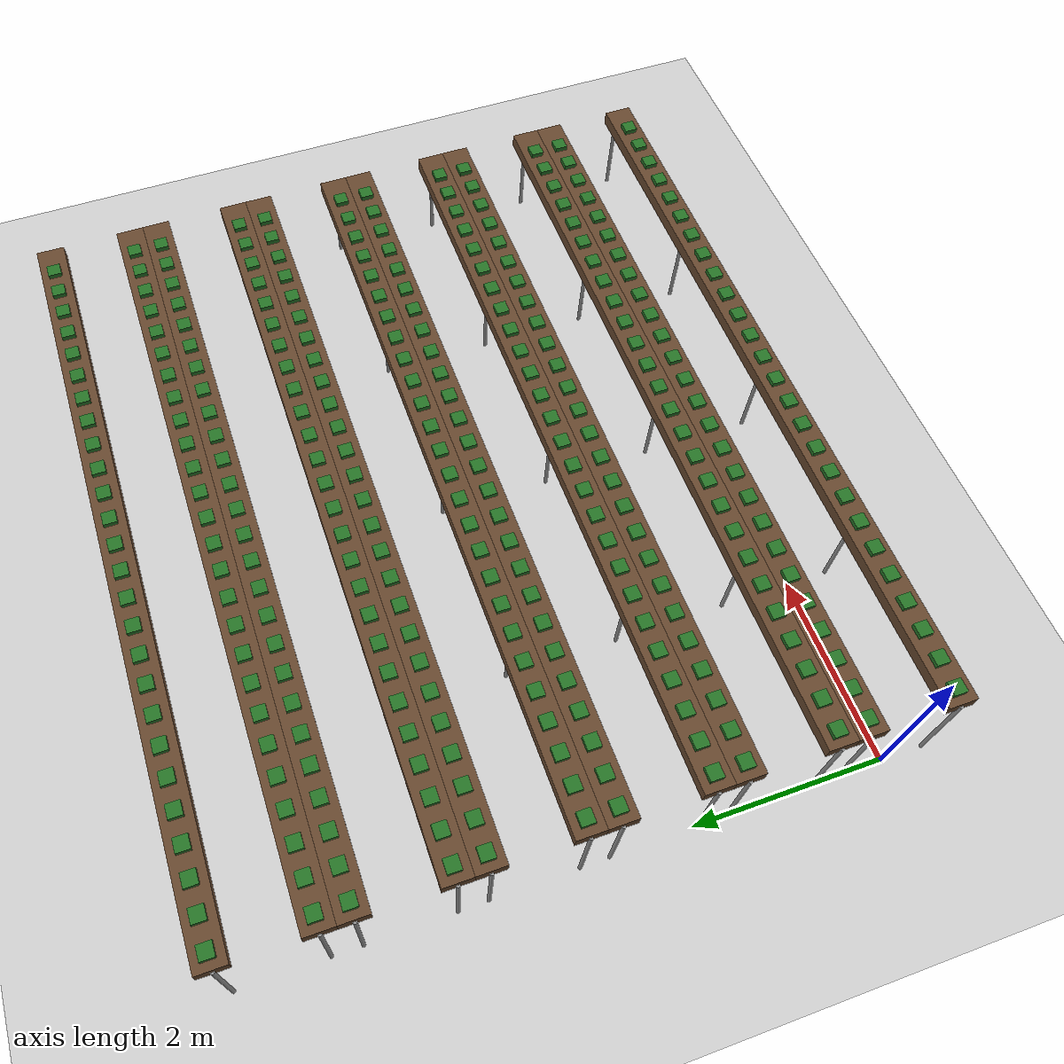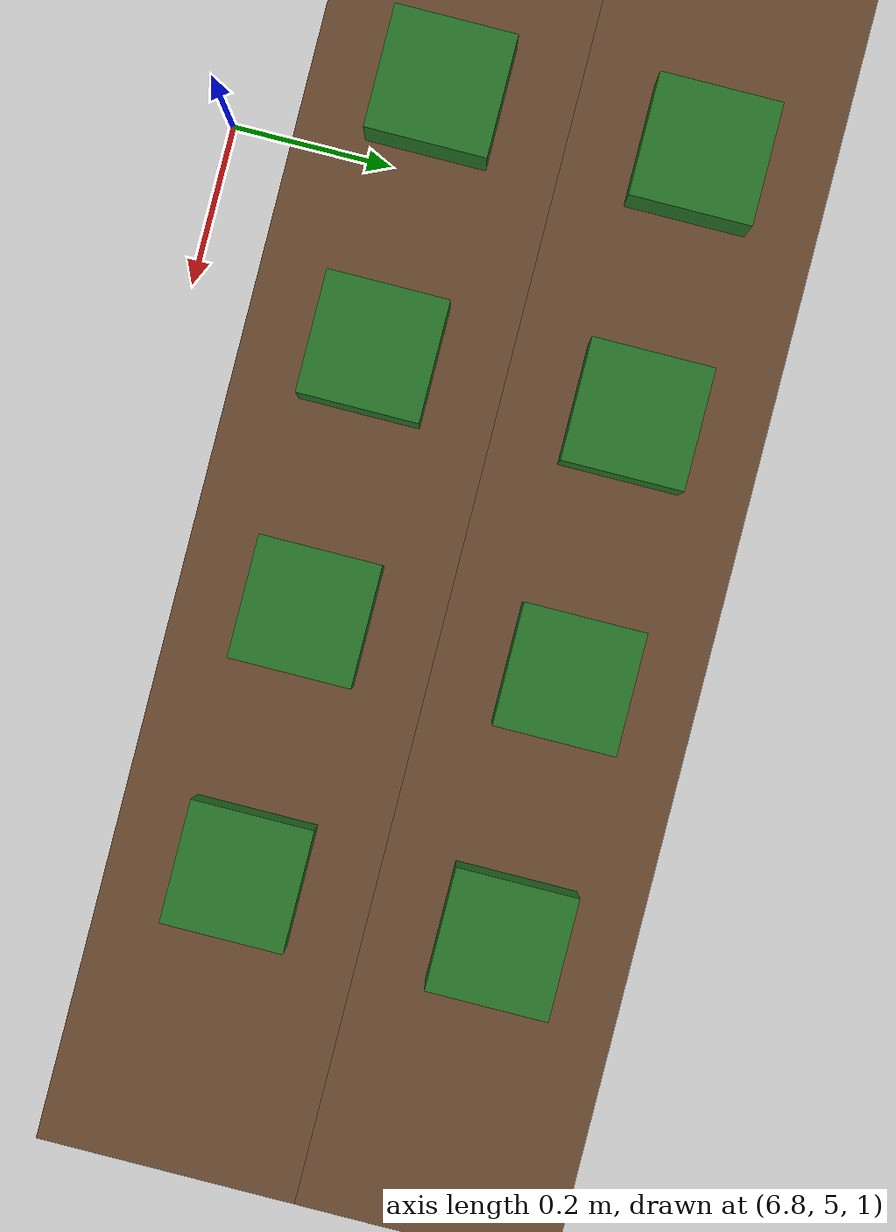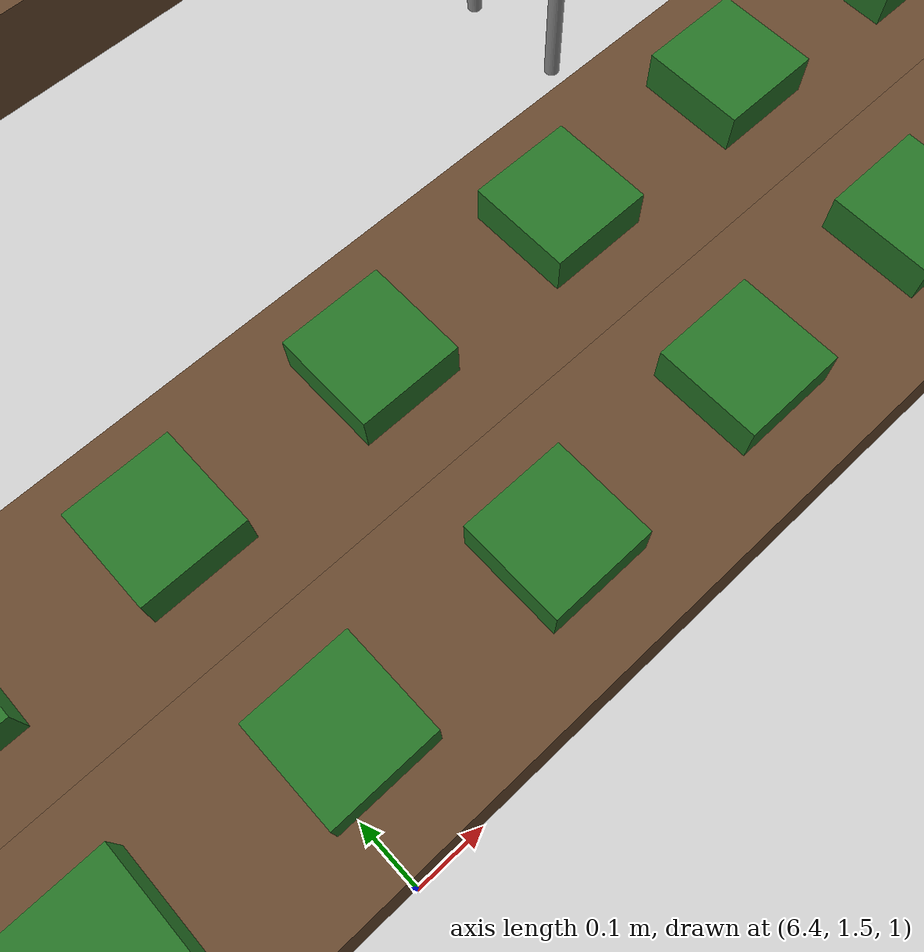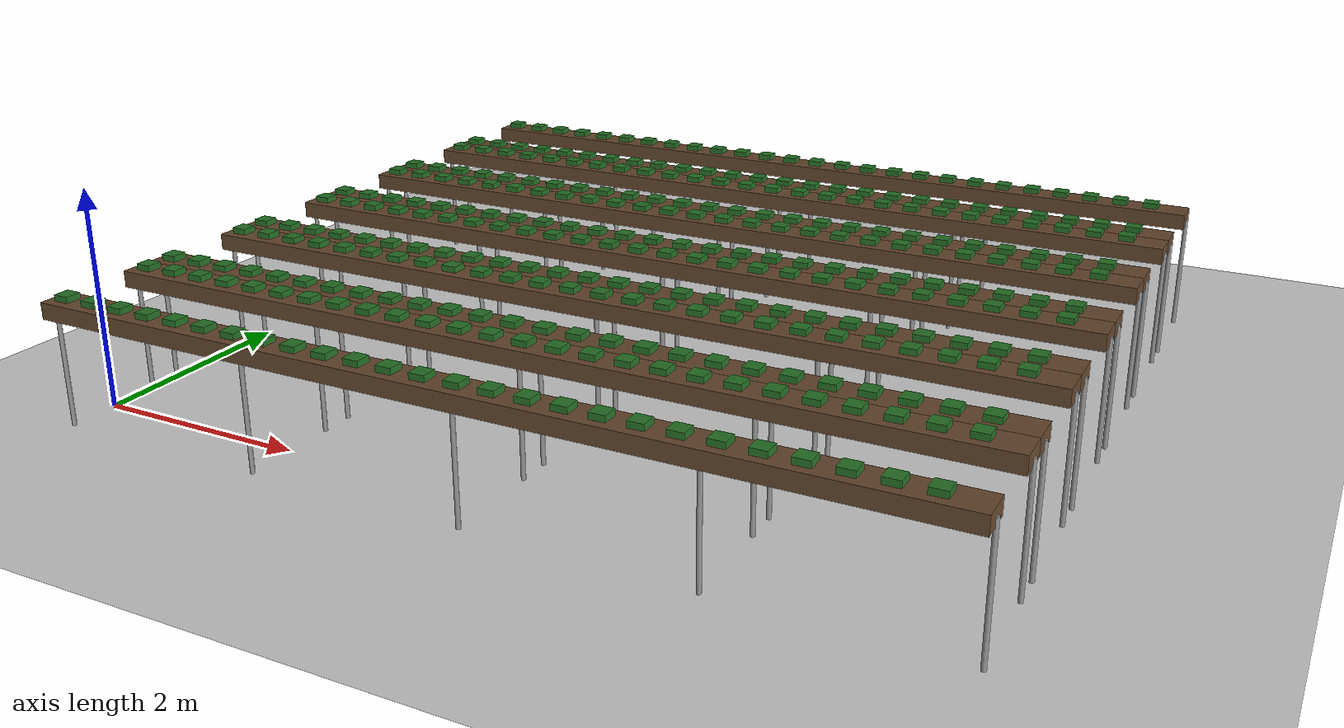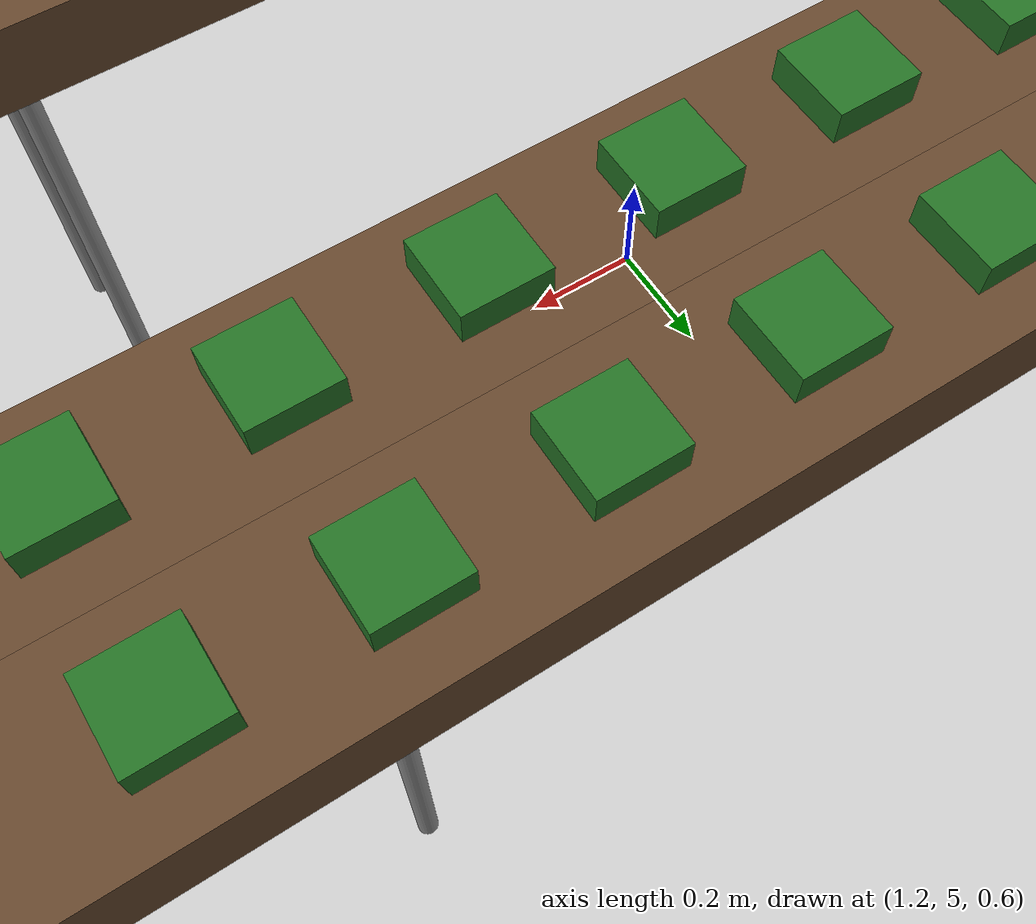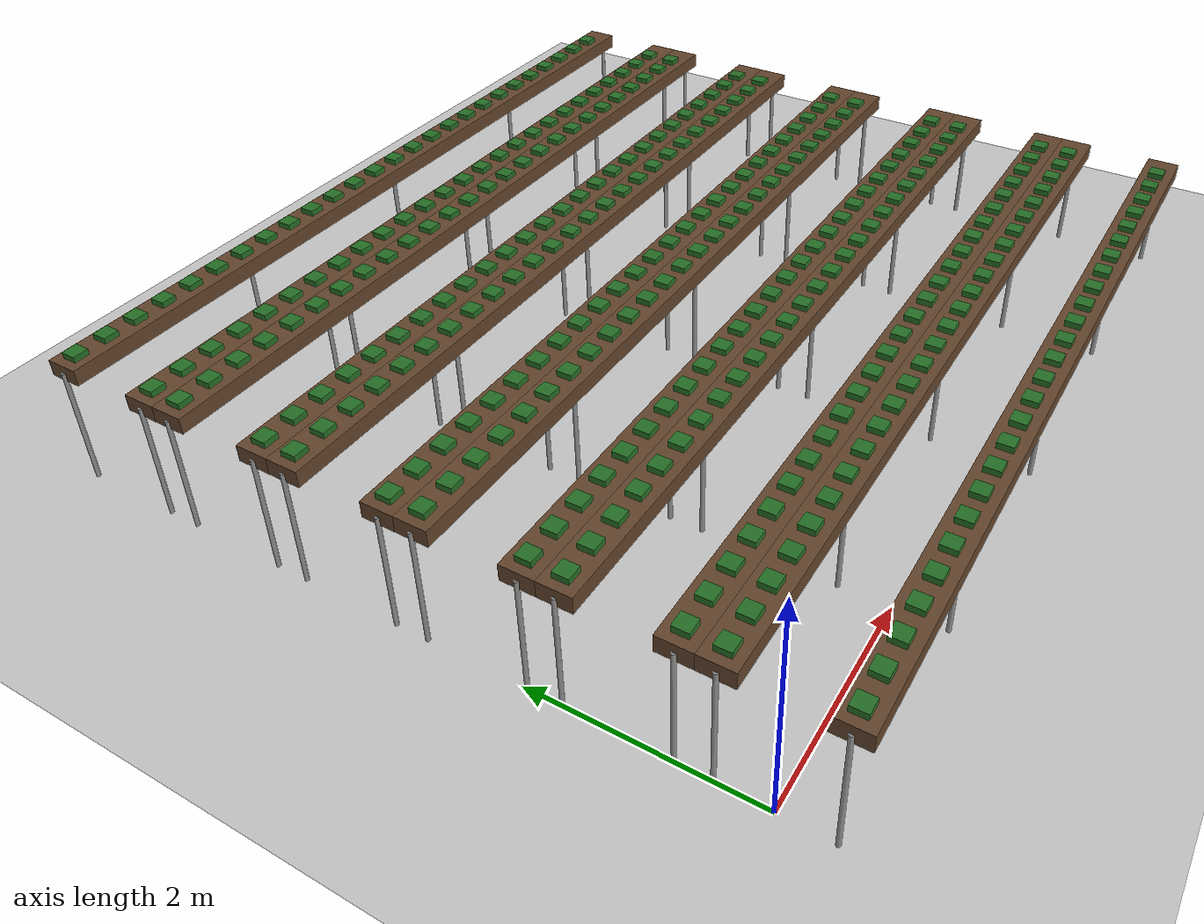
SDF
<?xml version="1.0" ?>
<sdf version="1.7">
  <world name="irish_polytunnel">
    <include><uri>model://sun</uri></include>
    <include><uri>model://ground_plane</uri></include>

    <physics type="ode">
      <max_step_size>0.001</max_step_size>
      <real_time_factor>1.0</real_time_factor>
      <real_time_update_rate>1000</real_time_update_rate>
    </physics>

    <!-- diffuse, indoor-polytunnel-like lighting rather than harsh direct
         sun; a rough approximation only, see the sim URDF's note on
         Gazebo Classic's rendering not being photorealistic -->
    <scene>
      <ambient>0.6 0.6 0.6 1</ambient>
      <background>0.7 0.7 0.7 1</background>
      <shadows>false</shadows>
    </scene>

    <model name="row0_L_post0">
      <static>true</static>
      <pose>0.000 0.450 0.550 0 0 0</pose>
      <link name="link">
        <collision name="collision">
          <geometry><cylinder><radius>0.02</radius><length>1.100</length></cylinder></geometry>
        </collision>
        <visual name="visual">
          <geometry><cylinder><radius>0.02</radius><length>1.100</length></cylinder></geometry>
          <material><ambient>0.5 0.5 0.5 1</ambient><diffuse>0.55 0.55 0.55 1</diffuse></material>
        </visual>
      </link>
    </model>

    <model name="row0_L_post1">
      <static>true</static>
      <pose>2.000 0.450 0.550 0 0 0</pose>
      <link name="link">
        <collision name="collision">
          <geometry><cylinder><radius>0.02</radius><length>1.100</length></cylinder></geometry>
        </collision>
        <visual name="visual">
          <geometry><cylinder><radius>0.02</radius><length>1.100</length></cylinder></geometry>
          <material><ambient>0.5 0.5 0.5 1</ambient><diffuse>0.55 0.55 0.55 1</diffuse></material>
        </visual>
      </link>
    </model>

    <model name="row0_L_post2">
      <static>true</static>
      <pose>4.000 0.450 0.550 0 0 0</pose>
      <link name="link">
        <collision name="collision">
          <geometry><cylinder><radius>0.02</radius><length>1.100</length></cylinder></geometry>
        </collision>
        <visual name="visual">
          <geometry><cylinder><radius>0.02</radius><length>1.100</length></cylinder></geometry>
          <material><ambient>0.5 0.5 0.5 1</ambient><diffuse>0.55 0.55 0.55 1</diffuse></material>
        </visual>
      </link>
    </model>

    <model name="row0_L_post3">
      <static>true</static>
      <pose>6.000 0.450 0.550 0 0 0</pose>
      <link name="link">
        <collision name="collision">
          <geometry><cylinder><radius>0.02</radius><length>1.100</length></cylinder></geometry>
        </collision>
        <visual name="visual">
          <geometry><cylinder><radius>0.02</radius><length>1.100</length></cylinder></geometry>
          <material><ambient>0.5 0.5 0.5 1</ambient><diffuse>0.55 0.55 0.55 1</diffuse></material>
        </visual>
      </link>
    </model>

    <model name="row0_L_post4">
      <static>true</static>
      <pose>8.000 0.450 0.550 0 0 0</pose>
      <link name="link">
        <collision name="collision">
          <geometry><cylinder><radius>0.02</radius><length>1.100</length></cylinder></geometry>
        </collision>
        <visual name="visual">
          <geometry><cylinder><radius>0.02</radius><length>1.100</length></cylinder></geometry>
          <material><ambient>0.5 0.5 0.5 1</ambient><diffuse>0.55 0.55 0.55 1</diffuse></material>
        </visual>
      </link>
    </model>

    <model name="row0_L_trough">
      <static>true</static>
      <pose>4.000 0.450 1.100 0 0 0</pose>
      <link name="link">
        <collision name="collision">
          <geometry><box><size>8.000 0.300 0.15</size></box></geometry>
        </collision>
        <visual name="visual">
          <geometry><box><size>8.000 0.300 0.15</size></box></geometry>
          <material><ambient>0.35 0.25 0.15 1</ambient><diffuse>0.4 0.28 0.18 1</diffuse></material>
        </visual>
      </link>
    </model>

    <model name="row0_L_plant0_foliage">
      <static>true</static>
      <pose>0.150 0.450 1.180 0 0 0</pose>
      <link name="link">
        <visual name="visual">
          <geometry><box><size>0.14 0.14 0.10</size></box></geometry>
          <material><ambient>0.10 0.35 0.10 1</ambient><diffuse>0.15 0.45 0.15 1</diffuse></material>
        </visual>
      </link>
    </model>
    <model name="row0_L_plant0_berry_0">
      <static>true</static>
      <pose>0.120 0.410 1.070 0 0 0</pose>
      <link name="link">
        <visual name="visual">
          <geometry><sphere><radius>0.012</radius></sphere></geometry>
          <material><ambient>0.75 0.05 0.05 1</ambient><diffuse>0.85 0.08 0.08 1</diffuse></material>
        </visual>
      </link>
    </model>
    <model name="row0_L_plant0_berry_1">
      <static>true</static>
      <pose>0.170 0.480 1.050 0 0 0</pose>
      <link name="link">
        <visual name="visual">
          <geometry><sphere><radius>0.012</radius></sphere></geometry>
          <material><ambient>0.75 0.05 0.05 1</ambient><diffuse>0.85 0.08 0.08 1</diffuse></material>
        </visual>
      </link>
    </model>

    <model name="row0_L_plant1_foliage">
      <static>true</static>
      <pose>0.450 0.450 1.180 0 0 0</pose>
      <link name="link">
        <visual name="visual">
          <geometry><box><size>0.14 0.14 0.10</size></box></geometry>
          <material><ambient>0.10 0.35 0.10 1</ambient><diffuse>0.15 0.45 0.15 1</diffuse></material>
        </visual>
      </link>
    </model>
    <model name="row0_L_plant1_berry_0">
      <static>true</static>
      <pose>0.420 0.410 1.070 0 0 0</pose>
      <link name="link">
        <visual name="visual">
          <geometry><sphere><radius>0.012</radius></sphere></geometry>
          <material><ambient>0.75 0.05 0.05 1</ambient><diffuse>0.85 0.08 0.08 1</diffuse></material>
        </visual>
      </link>
    </model>
    <model name="row0_L_plant1_berry_1">
      <static>true</static>
      <pose>0.470 0.480 1.050 0 0 0</pose>
      <link name="link">
        <visual name="visual">
          <geometry><sphere><radius>0.012</radius></sphere></geometry>
          <material><ambient>0.75 0.05 0.05 1</ambient><diffuse>0.85 0.08 0.08 1</diffuse></material>
        </visual>
      </link>
    </model>

    <model name="row0_L_plant2_foliage">
      <static>true</static>
      <pose>0.750 0.450 1.180 0 0 0</pose>
      <link name="link">
        <visual name="visual">
          <geometry><box><size>0.14 0.14 0.10</size></box></geometry>
          <material><ambient>0.10 0.35 0.10 1</ambient><diffuse>0.15 0.45 0.15 1</diffuse></material>
        </visual>
      </link>
    </model>
    <model name="row0_L_plant2_berry_0">
      <static>true</static>
      <pose>0.720 0.410 1.070 0 0 0</pose>
      <link name="link">
        <visual name="visual">
          <geometry><sphere><radius>0.012</radius></sphere></geometry>
          <material><ambient>0.75 0.05 0.05 1</ambient><diffuse>0.85 0.08 0.08 1</diffuse></material>
        </visual>
      </link>
    </model>
    <model name="row0_L_plant2_berry_1">
      <static>true</static>
      <pose>0.770 0.480 1.050 0 0 0</pose>
      <link name="link">
        <visual name="visual">
          <geometry><sphere><radius>0.012</radius></sphere></geometry>
          <material><ambient>0.75 0.05 0.05 1</ambient><diffuse>0.85 0.08 0.08 1</diffuse></material>
        </visual>
      </link>
    </model>

    <model name="row0_L_plant3_foliage">
      <static>true</static>
      <pose>1.050 0.450 1.180 0 0 0</pose>
      <link name="link">
        <visual name="visual">
          <geometry><box><size>0.14 0.14 0.10</size></box></geometry>
          <material><ambient>0.10 0.35 0.10 1</ambient><diffuse>0.15 0.45 0.15 1</diffuse></material>
        </visual>
      </link>
    </model>
    <model name="row0_L_plant3_berry_0">
      <static>true</static>
      <pose>1.020 0.410 1.070 0 0 0</pose>
      <link name="link">
        <visual name="visual">
          <geometry><sphere><radius>0.012</radius></sphere></geometry>
          <material><ambient>0.75 0.05 0.05 1</ambient><diffuse>0.85 0.08 0.08 1</diffuse></material>
        </visual>
      </link>
    </model>
    <model name="row0_L_plant3_berry_1">
      <static>true</static>
      <pose>1.070 0.480 1.050 0 0 0</pose>
      <link name="link">
        <visual name="visual">
          <geometry><sphere><radius>0.012</radius></sphere></geometry>
          <material><ambient>0.75 0.05 0.05 1</ambient><diffuse>0.85 0.08 0.08 1</diffuse></material>
        </visual>
      </link>
    </model>

    <model name="row0_L_plant4_foliage">
      <static>true</static>
      <pose>1.350 0.450 1.180 0 0 0</pose>
      <link name="link">
        <visual name="visual">
          <geometry><box><size>0.14 0.14 0.10</size></box></geometry>
          <material><ambient>0.10 0.35 0.10 1</ambient><diffuse>0.15 0.45 0.15 1</diffuse></material>
        </visual>
      </link>
    </model>
    <model name="row0_L_plant4_berry_0">
      <static>true</static>
      <pose>1.320 0.410 1.070 0 0 0</pose>
      <link name="link">
        <visual name="visual">
          <geometry><sphere><radius>0.012</radius></sphere></geometry>
          <material><ambient>0.75 0.05 0.05 1</ambient><diffuse>0.85 0.08 0.08 1</diffuse></material>
        </visual>
      </link>
    </model>
    <model name="row0_L_plant4_berry_1">
      <static>true</static>
      <pose>1.370 0.480 1.050 0 0 0</pose>
      <link name="link">
        <visual name="visual">
          <geometry><sphere><radius>0.012</radius></sphere></geometry>
          <material><ambient>0.75 0.05 0.05 1</ambient><diffuse>0.85 0.08 0.08 1</diffuse></material>
        </visual>
      </link>
    </model>

    <model name="row0_L_plant5_foliage">
      <static>true</static>
      <pose>1.650 0.450 1.180 0 0 0</pose>
      <link name="link">
        <visual name="visual">
          <geometry><box><size>0.14 0.14 0.10</size></box></geometry>
          <material><ambient>0.10 0.35 0.10 1</ambient><diffuse>0.15 0.45 0.15 1</diffuse></material>
        </visual>
      </link>
    </model>
    <model name="row0_L_plant5_berry_0">
      <static>true</static>
      <pose>1.620 0.410 1.070 0 0 0</pose>
      <link name="link">
        <visual name="visual">
          <geometry><sphere><radius>0.012</radius></sphere></geometry>
          <material><ambient>0.75 0.05 0.05 1</ambient><diffuse>0.85 0.08 0.08 1</diffuse></material>
        </visual>
      </link>
    </model>
    <model name="row0_L_plant5_berry_1">
      <static>true</static>
      <pose>1.670 0.480 1.050 0 0 0</pose>
      <link name="link">
        <visual name="visual">
          <geometry><sphere><radius>0.012</radius></sphere></geometry>
          <material><ambient>0.75 0.05 0.05 1</ambient><diffuse>0.85 0.08 0.08 1</diffuse></material>
        </visual>
      </link>
    </model>

    <model name="row0_L_plant6_foliage">
      <static>true</static>
      <pose>1.950 0.450 1.180 0 0 0</pose>
      <link name="link">
        <visual name="visual">
          <geometry><box><size>0.14 0.14 0.10</size></box></geometry>
          <material><ambient>0.10 0.35 0.10 1</ambient><diffuse>0.15 0.45 0.15 1</diffuse></material>
        </visual>
      </link>
    </model>
    <model name="row0_L_plant6_berry_0">
      <static>true</static>
      <pose>1.920 0.410 1.070 0 0 0</pose>
      <link name="link">
        <visual name="visual">
          <geometry><sphere><radius>0.012</radius></sphere></geometry>
          <material><ambient>0.75 0.05 0.05 1</ambient><diffuse>0.85 0.08 0.08 1</diffuse></material>
        </visual>
      </link>
    </model>
    <model name="row0_L_plant6_berry_1">
      <static>true</static>
      <pose>1.970 0.480 1.050 0 0 0</pose>
      <link name="link">
        <visual name="visual">
          <geometry><sphere><radius>0.012</radius></sphere></geometry>
          <material><ambient>0.75 0.05 0.05 1</ambient><diffuse>0.85 0.08 0.08 1</diffuse></material>
        </visual>
      </link>
    </model>

    <model name="row0_L_plant7_foliage">
      <static>true</static>
      <pose>2.250 0.450 1.180 0 0 0</pose>
      <link name="link">
        <visual name="visual">
          <geometry><box><size>0.14 0.14 0.10</size></box></geometry>
          <material><ambient>0.10 0.35 0.10 1</ambient><diffuse>0.15 0.45 0.15 1</diffuse></material>
        </visual>
      </link>
    </model>
    <model name="row0_L_plant7_berry_0">
      <static>true</static>
      <pose>2.220 0.410 1.070 0 0 0</pose>
      <link name="link">
        <visual name="visual">
          <geometry><sphere><radius>0.012</radius></sphere></geometry>
          <material><ambient>0.75 0.05 0.05 1</ambient><diffuse>0.85 0.08 0.08 1</diffuse></material>
        </visual>
      </link>
    </model>
    <model name="row0_L_plant7_berry_1">
      <static>true</static>
      <pose>2.270 0.480 1.050 0 0 0</pose>
      <link name="link">
        <visual name="visual">
          <geometry><sphere><radius>0.012</radius></sphere></geometry>
          <material><ambient>0.75 0.05 0.05 1</ambient><diffuse>0.85 0.08 0.08 1</diffuse></material>
        </visual>
      </link>
    </model>

    <model name="row0_L_plant8_foliage">
      <static>true</static>
      <pose>2.550 0.450 1.180 0 0 0</pose>
      <link name="link">
        <visual name="visual">
          <geometry><box><size>0.14 0.14 0.10</size></box></geometry>
          <material><ambient>0.10 0.35 0.10 1</ambient><diffuse>0.15 0.45 0.15 1</diffuse></material>
        </visual>
      </link>
    </model>
    <model name="row0_L_plant8_berry_0">
      <static>true</static>
      <pose>2.520 0.410 1.070 0 0 0</pose>
      <link name="link">
        <visual name="visual">
          <geometry><sphere><radius>0.012</radius></sphere></geometry>
          <material><ambient>0.75 0.05 0.05 1</ambient><diffuse>0.85 0.08 0.08 1</diffuse></material>
        </visual>
      </link>
    </model>
    <model name="row0_L_plant8_berry_1">
      <static>true</static>
      <pose>2.570 0.480 1.050 0 0 0</pose>
      <link name="link">
        <visual name="visual">
          <geometry><sphere><radius>0.012</radius></sphere></geometry>
          <material><ambient>0.75 0.05 0.05 1</ambient><diffuse>0.85 0.08 0.08 1</diffuse></material>
        </visual>
      </link>
    </model>

    <model name="row0_L_plant9_foliage">
      <static>true</static>
      <pose>2.850 0.450 1.180 0 0 0</pose>
      <link name="link">
        <visual name="visual">
          <geometry><box><size>0.14 0.14 0.10</size></box></geometry>
          <material><ambient>0.10 0.35 0.10 1</ambient><diffuse>0.15 0.45 0.15 1</diffuse></material>
        </visual>
      </link>
    </model>
    <model name="row0_L_plant9_berry_0">
      <static>true</static>
      <pose>2.820 0.410 1.070 0 0 0</pose>
      <link name="link">
        <visual name="visual">
          <geometry><sphere><radius>0.012</radius></sphere></geometry>
          <material><ambient>0.75 0.05 0.05 1</ambient><diffuse>0.85 0.08 0.08 1</diffuse></material>
        </visual>
      </link>
    </model>
    <model name="row0_L_plant9_berry_1">
      <static>true</static>
      <pose>2.870 0.480 1.050 0 0 0</pose>
      <link name="link">
        <visual name="visual">
          <geometry><sphere><radius>0.012</radius></sphere></geometry>
          <material><ambient>0.75 0.05 0.05 1</ambient><diffuse>0.85 0.08 0.08 1</diffuse></material>
        </visual>
      </link>
    </model>

    <model name="row0_L_plant10_foliage">
      <static>true</static>
      <pose>3.150 0.450 1.180 0 0 0</pose>
      <link name="link">
        <visual name="visual">
          <geometry><box><size>0.14 0.14 0.10</size></box></geometry>
          <material><ambient>0.10 0.35 0.10 1</ambient><diffuse>0.15 0.45 0.15 1</diffuse></material>
        </visual>
      </link>
    </model>
    <model name="row0_L_plant10_berry_0">
      <static>true</static>
      <pose>3.120 0.410 1.070 0 0 0</pose>
      <link name="link">
        <visual name="visual">
          <geometry><sphere><radius>0.012</radius></sphere></geometry>
          <material><ambient>0.75 0.05 0.05 1</ambient><diffuse>0.85 0.08 0.08 1</diffuse></material>
        </visual>
      </link>
    </model>
    <model name="row0_L_plant10_berry_1">
      <static>true</static>
      <pose>3.170 0.480 1.050 0 0 0</pose>
      <link name="link">
        <visual name="visual">
          <geometry><sphere><radius>0.012</radius></sphere></geometry>
          <material><ambient>0.75 0.05 0.05 1</ambient><diffuse>0.85 0.08 0.08 1</diffuse></material>
        </visual>
      </link>
    </model>

    <model name="row0_L_plant11_foliage">
      <static>true</static>
      <pose>3.450 0.450 1.180 0 0 0</pose>
      <link name="link">
        <visual name="visual">
          <geometry><box><size>0.14 0.14 0.10</size></box></geometry>
          <material><ambient>0.10 0.35 0.10 1</ambient><diffuse>0.15 0.45 0.15 1</diffuse></material>
        </visual>
      </link>
    </model>
    <model name="row0_L_plant11_berry_0">
      <static>true</static>
      <pose>3.420 0.410 1.070 0 0 0</pose>
      <link name="link">
        <visual name="visual">
          <geometry><sphere><radius>0.012</radius></sphere></geometry>
          <material><ambient>0.75 0.05 0.05 1</ambient><diffuse>0.85 0.08 0.08 1</diffuse></material>
        </visual>
      </link>
    </model>
    <model name="row0_L_plant11_berry_1">
      <static>true</static>
      <pose>3.470 0.480 1.050 0 0 0</pose>
      <link name="link">
        <visual name="visual">
          <geometry><sphere><radius>0.012</radius></sphere></geometry>
          <material><ambient>0.75 0.05 0.05 1</ambient><diffuse>0.85 0.08 0.08 1</diffuse></material>
        </visual>
      </link>
    </model>

    <model name="row0_L_plant12_foliage">
      <static>true</static>
      <pose>3.750 0.450 1.180 0 0 0</pose>
      <link name="link">
        <visual name="visual">
          <geometry><box><size>0.14 0.14 0.10</size></box></geometry>
          <material><ambient>0.10 0.35 0.10 1</ambient><diffuse>0.15 0.45 0.15 1</diffuse></material>
        </visual>
      </link>
    </model>
    <model name="row0_L_plant12_berry_0">
      <static>true</static>
      <pose>3.720 0.410 1.070 0 0 0</pose>
      <link name="link">
        <visual name="visual">
          <geometry><sphere><radius>0.012</radius></sphere></geometry>
          <material><ambient>0.75 0.05 0.05 1</ambient><diffuse>0.85 0.08 0.08 1</diffuse></material>
        </visual>
      </link>
    </model>
    <model name="row0_L_plant12_berry_1">
      <static>true</static>
      <pose>3.770 0.480 1.050 0 0 0</pose>
      <link name="link">
        <visual name="visual">
          <geometry><sphere><radius>0.012</radius></sphere></geometry>
          <material><ambient>0.75 0.05 0.05 1</ambient><diffuse>0.85 0.08 0.08 1</diffuse></material>
        </visual>
      </link>
    </model>

    <model name="row0_L_plant13_foliage">
      <static>true</static>
      <pose>4.050 0.450 1.180 0 0 0</pose>
      <link name="link">
        <visual name="visual">
          <geometry><box><size>0.14 0.14 0.10</size></box></geometry>
          <material><ambient>0.10 0.35 0.10 1</ambient><diffuse>0.15 0.45 0.15 1</diffuse></material>
        </visual>
      </link>
    </model>
    <model name="row0_L_plant13_berry_0">
      <static>true</static>
      <pose>4.020 0.410 1.070 0 0 0</pose>
      <link name="link">
        <visual name="visual">
          <geometry><sphere><radius>0.012</radius></sphere></geometry>
          <material><ambient>0.75 0.05 0.05 1</ambient><diffuse>0.85 0.08 0.08 1</diffuse></material>
        </visual>
      </link>
    </model>
    <model name="row0_L_plant13_berry_1">
      <static>true</static>
      <pose>4.070 0.480 1.050 0 0 0</pose>
      <link name="link">
        <visual name="visual">
          <geometry><sphere><radius>0.012</radius></sphere></geometry>
          <material><ambient>0.75 0.05 0.05 1</ambient><diffuse>0.85 0.08 0.08 1</diffuse></material>
        </visual>
      </link>
    </model>

    <model name="row0_L_plant14_foliage">
      <static>true</static>
      <pose>4.350 0.450 1.180 0 0 0</pose>
      <link name="link">
        <visual name="visual">
          <geometry><box><size>0.14 0.14 0.10</size></box></geometry>
          <material><ambient>0.10 0.35 0.10 1</ambient><diffuse>0.15 0.45 0.15 1</diffuse></material>
        </visual>
      </link>
    </model>
    <model name="row0_L_plant14_berry_0">
      <static>true</static>
      <pose>4.320 0.410 1.070 0 0 0</pose>
      <link name="link">
        <visual name="visual">
          <geometry><sphere><radius>0.012</radius></sphere></geometry>
          <material><ambient>0.75 0.05 0.05 1</ambient><diffuse>0.85 0.08 0.08 1</diffuse></material>
        </visual>
      </link>
    </model>
    <model name="row0_L_plant14_berry_1">
      <static>true</static>
      <pose>4.370 0.480 1.050 0 0 0</pose>
      <link name="link">
        <visual name="visual">
          <geometry><sphere><radius>0.012</radius></sphere></geometry>
          <material><ambient>0.75 0.05 0.05 1</ambient><diffuse>0.85 0.08 0.08 1</diffuse></material>
        </visual>
      </link>
    </model>

    <model name="row0_L_plant15_foliage">
      <static>true</static>
      <pose>4.650 0.450 1.180 0 0 0</pose>
      <link name="link">
        <visual name="visual">
          <geometry><box><size>0.14 0.14 0.10</size></box></geometry>
          <material><ambient>0.10 0.35 0.10 1</ambient><diffuse>0.15 0.45 0.15 1</diffuse></material>
        </visual>
      </link>
    </model>
    <model name="row0_L_plant15_berry_0">
      <static>true</static>
      <pose>4.620 0.410 1.070 0 0 0</pose>
      <link name="link">
        <visual name="visual">
          <geometry><sphere><radius>0.012</radius></sphere></geometry>
          <material><ambient>0.75 0.05 0.05 1</ambient><diffuse>0.85 0.08 0.08 1</diffuse></material>
        </visual>
      </link>
    </model>
    <model name="row0_L_plant15_berry_1">
      <static>true</static>
      <pose>4.670 0.480 1.050 0 0 0</pose>
      <link name="link">
        <visual name="visual">
          <geometry><sphere><radius>0.012</radius></sphere></geometry>
          <material><ambient>0.75 0.05 0.05 1</ambient><diffuse>0.85 0.08 0.08 1</diffuse></material>
        </visual>
      </link>
    </model>

    <model name="row0_L_plant16_foliage">
      <static>true</static>
      <pose>4.950 0.450 1.180 0 0 0</pose>
      <link name="link">
        <visual name="visual">
          <geometry><box><size>0.14 0.14 0.10</size></box></geometry>
          <material><ambient>0.10 0.35 0.10 1</ambient><diffuse>0.15 0.45 0.15 1</diffuse></material>
        </visual>
      </link>
    </model>
    <model name="row0_L_plant16_berry_0">
      <static>true</static>
      <pose>4.920 0.410 1.070 0 0 0</pose>
      <link name="link">
        <visual name="visual">
          <geometry><sphere><radius>0.012</radius></sphere></geometry>
          <material><ambient>0.75 0.05 0.05 1</ambient><diffuse>0.85 0.08 0.08 1</diffuse></material>
        </visual>
      </link>
    </model>
    <model name="row0_L_plant16_berry_1">
      <static>true</static>
      <pose>4.970 0.480 1.050 0 0 0</pose>
      <link name="link">
        <visual name="visual">
          <geometry><sphere><radius>0.012</radius></sphere></geometry>
          <material><ambient>0.75 0.05 0.05 1</ambient><diffuse>0.85 0.08 0.08 1</diffuse></material>
        </visual>
      </link>
    </model>

    <model name="row0_L_plant17_foliage">
      <static>true</static>
      <pose>5.250 0.450 1.180 0 0 0</pose>
      <link name="link">
        <visual name="visual">
          <geometry><box><size>0.14 0.14 0.10</size></box></geometry>
          <material><ambient>0.10 0.35 0.10 1</ambient><diffuse>0.15 0.45 0.15 1</diffuse></material>
        </visual>
      </link>
    </model>
    <model name="row0_L_plant17_berry_0">
      <static>true</static>
      <pose>5.220 0.410 1.070 0 0 0</pose>
      <link name="link">
        <visual name="visual">
          <geometry><sphere><radius>0.012</radius></sphere></geometry>
          <material><ambient>0.75 0.05 0.05 1</ambient><diffuse>0.85 0.08 0.08 1</diffuse></material>
        </visual>
      </link>
    </model>
    <model name="row0_L_plant17_berry_1">
      <static>true</static>
      <pose>5.270 0.480 1.050 0 0 0</pose>
      <link name="link">
        <visual name="visual">
          <geometry><sphere><radius>0.012</radius></sphere></geometry>
          <material><ambient>0.75 0.05 0.05 1</ambient><diffuse>0.85 0.08 0.08 1</diffuse></material>
        </visual>
      </link>
    </model>

    <model name="row0_L_plant18_foliage">
      <static>true</static>
      <pose>5.550 0.450 1.180 0 0 0</pose>
      <link name="link">
        <visual name="visual">
          <geometry><box><size>0.14 0.14 0.10</size></box></geometry>
          <material><ambient>0.10 0.35 0.10 1</ambient><diffuse>0.15 0.45 0.15 1</diffuse></material>
        </visual>
      </link>
    </model>
    <model name="row0_L_plant18_berry_0">
      <static>true</static>
      <pose>5.520 0.410 1.070 0 0 0</pose>
      <link name="link">
        <visual name="visual">
          <geometry><sphere><radius>0.012</radius></sphere></geometry>
          <material><ambient>0.75 0.05 0.05 1</ambient><diffuse>0.85 0.08 0.08 1</diffuse></material>
        </visual>
      </link>
    </model>
    <model name="row0_L_plant18_berry_1">
      <static>true</static>
      <pose>5.570 0.480 1.050 0 0 0</pose>
      <link name="link">
        <visual name="visual">
          <geometry><sphere><radius>0.012</radius></sphere></geometry>
          <material><ambient>0.75 0.05 0.05 1</ambient><diffuse>0.85 0.08 0.08 1</diffuse></material>
        </visual>
      </link>
    </model>

    <model name="row0_L_plant19_foliage">
      <static>true</static>
      <pose>5.850 0.450 1.180 0 0 0</pose>
      <link name="link">
        <visual name="visual">
          <geometry><box><size>0.14 0.14 0.10</size></box></geometry>
          <material><ambient>0.10 0.35 0.10 1</ambient><diffuse>0.15 0.45 0.15 1</diffuse></material>
        </visual>
      </link>
    </model>
    <model name="row0_L_plant19_berry_0">
      <static>true</static>
      <pose>5.820 0.410 1.070 0 0 0</pose>
      <link name="link">
        <visual name="visual">
          <geometry><sphere><radius>0.012</radius></sphere></geometry>
          <material><ambient>0.75 0.05 0.05 1</ambient><diffuse>0.85 0.08 0.08 1</diffuse></material>
        </visual>
      </link>
    </model>
    <model name="row0_L_plant19_berry_1">
      <static>true</static>
      <pose>5.870 0.480 1.050 0 0 0</pose>
      <link name="link">
        <visual name="visual">
          <geometry><sphere><radius>0.012</radius></sphere></geometry>
          <material><ambient>0.75 0.05 0.05 1</ambient><diffuse>0.85 0.08 0.08 1</diffuse></material>
        </visual>
      </link>
    </model>

    <model name="row0_L_plant20_foliage">
      <static>true</static>
      <pose>6.150 0.450 1.180 0 0 0</pose>
      <link name="link">
        <visual name="visual">
          <geometry><box><size>0.14 0.14 0.10</size></box></geometry>
          <material><ambient>0.10 0.35 0.10 1</ambient><diffuse>0.15 0.45 0.15 1</diffuse></material>
        </visual>
      </link>
    </model>
    <model name="row0_L_plant20_berry_0">
      <static>true</static>
      <pose>6.120 0.410 1.070 0 0 0</pose>
      <link name="link">
        <visual name="visual">
          <geometry><sphere><radius>0.012</radius></sphere></geometry>
          <material><ambient>0.75 0.05 0.05 1</ambient><diffuse>0.85 0.08 0.08 1</diffuse></material>
        </visual>
      </link>
    </model>
    <model name="row0_L_plant20_berry_1">
      <static>true</static>
      <pose>6.170 0.480 1.050 0 0 0</pose>
      <link name="link">
        <visual name="visual">
          <geometry><sphere><radius>0.012</radius></sphere></geometry>
          <material><ambient>0.75 0.05 0.05 1</ambient><diffuse>0.85 0.08 0.08 1</diffuse></material>
        </visual>
      </link>
    </model>

    <model name="row0_L_plant21_foliage">
      <static>true</static>
      <pose>6.450 0.450 1.180 0 0 0</pose>
      <link name="link">
        <visual name="visual">
          <geometry><box><size>0.14 0.14 0.10</size></box></geometry>
          <material><ambient>0.10 0.35 0.10 1</ambient><diffuse>0.15 0.45 0.15 1</diffuse></material>
        </visual>
      </link>
    </model>
    <model name="row0_L_plant21_berry_0">
      <static>true</static>
      <pose>6.420 0.410 1.070 0 0 0</pose>
      <link name="link">
        <visual name="visual">
          <geometry><sphere><radius>0.012</radius></sphere></geometry>
          <material><ambient>0.75 0.05 0.05 1</ambient><diffuse>0.85 0.08 0.08 1</diffuse></material>
        </visual>
      </link>
    </model>
    <model name="row0_L_plant21_berry_1">
      <static>true</static>
      <pose>6.470 0.480 1.050 0 0 0</pose>
      <link name="link">
        <visual name="visual">
          <geometry><sphere><radius>0.012</radius></sphere></geometry>
          <material><ambient>0.75 0.05 0.05 1</ambient><diffuse>0.85 0.08 0.08 1</diffuse></material>
        </visual>
      </link>
    </model>

    <model name="row0_L_plant22_foliage">
      <static>true</static>
      <pose>6.750 0.450 1.180 0 0 0</pose>
      <link name="link">
        <visual name="visual">
          <geometry><box><size>0.14 0.14 0.10</size></box></geometry>
          <material><ambient>0.10 0.35 0.10 1</ambient><diffuse>0.15 0.45 0.15 1</diffuse></material>
        </visual>
      </link>
    </model>
    <model name="row0_L_plant22_berry_0">
      <static>true</static>
      <pose>6.720 0.410 1.070 0 0 0</pose>
      <link name="link">
        <visual name="visual">
          <geometry><sphere><radius>0.012</radius></sphere></geometry>
          <material><ambient>0.75 0.05 0.05 1</ambient><diffuse>0.85 0.08 0.08 1</diffuse></material>
        </visual>
      </link>
    </model>
    <model name="row0_L_plant22_berry_1">
      <static>true</static>
      <pose>6.770 0.480 1.050 0 0 0</pose>
      <link name="link">
        <visual name="visual">
          <geometry><sphere><radius>0.012</radius></sphere></geometry>
          <material><ambient>0.75 0.05 0.05 1</ambient><diffuse>0.85 0.08 0.08 1</diffuse></material>
        </visual>
      </link>
    </model>

    <model name="row0_L_plant23_foliage">
      <static>true</static>
      <pose>7.050 0.450 1.180 0 0 0</pose>
      <link name="link">
        <visual name="visual">
          <geometry><box><size>0.14 0.14 0.10</size></box></geometry>
          <material><ambient>0.10 0.35 0.10 1</ambient><diffuse>0.15 0.45 0.15 1</diffuse></material>
        </visual>
      </link>
    </model>
    <model name="row0_L_plant23_berry_0">
      <static>true</static>
      <pose>7.020 0.410 1.070 0 0 0</pose>
      <link name="link">
        <visual name="visual">
          <geometry><sphere><radius>0.012</radius></sphere></geometry>
          <material><ambient>0.75 0.05 0.05 1</ambient><diffuse>0.85 0.08 0.08 1</diffuse></material>
        </visual>
      </link>
    </model>
    <model name="row0_L_plant23_berry_1">
      <static>true</static>
      <pose>7.070 0.480 1.050 0 0 0</pose>
      <link name="link">
        <visual name="visual">
          <geometry><sphere><radius>0.012</radius></sphere></geometry>
          <material><ambient>0.75 0.05 0.05 1</ambient><diffuse>0.85 0.08 0.08 1</diffuse></material>
        </visual>
      </link>
    </model>

    <model name="row0_L_plant24_foliage">
      <static>true</static>
      <pose>7.350 0.450 1.180 0 0 0</pose>
      <link name="link">
        <visual name="visual">
          <geometry><box><size>0.14 0.14 0.10</size></box></geometry>
          <material><ambient>0.10 0.35 0.10 1</ambient><diffuse>0.15 0.45 0.15 1</diffuse></material>
        </visual>
      </link>
    </model>
    <model name="row0_L_plant24_berry_0">
      <static>true</static>
      <pose>7.320 0.410 1.070 0 0 0</pose>
      <link name="link">
        <visual name="visual">
          <geometry><sphere><radius>0.012</radius></sphere></geometry>
          <material><ambient>0.75 0.05 0.05 1</ambient><diffuse>0.85 0.08 0.08 1</diffuse></material>
        </visual>
      </link>
    </model>
    <model name="row0_L_plant24_berry_1">
      <static>true</static>
      <pose>7.370 0.480 1.050 0 0 0</pose>
      <link name="link">
        <visual name="visual">
          <geometry><sphere><radius>0.012</radius></sphere></geometry>
          <material><ambient>0.75 0.05 0.05 1</ambient><diffuse>0.85 0.08 0.08 1</diffuse></material>
        </visual>
      </link>
    </model>

    <model name="row0_L_plant25_foliage">
      <static>true</static>
      <pose>7.650 0.450 1.180 0 0 0</pose>
      <link name="link">
        <visual name="visual">
          <geometry><box><size>0.14 0.14 0.10</size></box></geometry>
          <material><ambient>0.10 0.35 0.10 1</ambient><diffuse>0.15 0.45 0.15 1</diffuse></material>
        </visual>
      </link>
    </model>
    <model name="row0_L_plant25_berry_0">
      <static>true</static>
      <pose>7.620 0.410 1.070 0 0 0</pose>
      <link name="link">
        <visual name="visual">
          <geometry><sphere><radius>0.012</radius></sphere></geometry>
          <material><ambient>0.75 0.05 0.05 1</ambient><diffuse>0.85 0.08 0.08 1</diffuse></material>
        </visual>
      </link>
    </model>
    <model name="row0_L_plant25_berry_1">
      <static>true</static>
      <pose>7.670 0.480 1.050 0 0 0</pose>
      <link name="link">
        <visual name="visual">
          <geometry><sphere><radius>0.012</radius></sphere></geometry>
          <material><ambient>0.75 0.05 0.05 1</ambient><diffuse>0.85 0.08 0.08 1</diffuse></material>
        </visual>
      </link>
    </model>

    <model name="row0_R_post0">
      <static>true</static>
      <pose>0.000 -0.450 0.550 0 0 0</pose>
      <link name="link">
        <collision name="collision">
          <geometry><cylinder><radius>0.02</radius><length>1.100</length></cylinder></geometry>
        </collision>
        <visual name="visual">
          <geometry><cylinder><radius>0.02</radius><length>1.100</length></cylinder></geometry>
          <material><ambient>0.5 0.5 0.5 1</ambient><diffuse>0.55 0.55 0.55 1</diffuse></material>
        </visual>
      </link>
    </model>

    <model name="row0_R_post1">
      <static>true</static>
      <pose>2.000 -0.450 0.550 0 0 0</pose>
      <link name="link">
        <collision name="collision">
          <geometry><cylinder><radius>0.02</radius><length>1.100</length></cylinder></geometry>
        </collision>
        <visual name="visual">
          <geometry><cylinder><radius>0.02</radius><length>1.100</length></cylinder></geometry>
          <material><ambient>0.5 0.5 0.5 1</ambient><diffuse>0.55 0.55 0.55 1</diffuse></material>
        </visual>
      </link>
    </model>

    <model name="row0_R_post2">
      <static>true</static>
      <pose>4.000 -0.450 0.550 0 0 0</pose>
      <link name="link">
        <collision name="collision">
          <geometry><cylinder><radius>0.02</radius><length>1.100</length></cylinder></geometry>
        </collision>
        <visual name="visual">
          <geometry><cylinder><radius>0.02</radius><length>1.100</length></cylinder></geometry>
          <material><ambient>0.5 0.5 0.5 1</ambient><diffuse>0.55 0.55 0.55 1</diffuse></material>
        </visual>
      </link>
    </model>

    <model name="row0_R_post3">
      <static>true</static>
      <pose>6.000 -0.450 0.550 0 0 0</pose>
      <link name="link">
        <collision name="collision">
          <geometry><cylinder><radius>0.02</radius><length>1.100</length></cylinder></geometry>
        </collision>
        <visual name="visual">
          <geometry><cylinder><radius>0.02</radius><length>1.100</length></cylinder></geometry>
          <material><ambient>0.5 0.5 0.5 1</ambient><diffuse>0.55 0.55 0.55 1</diffuse></material>
        </visual>
      </link>
    </model>

    <model name="row0_R_post4">
      <static>true</static>
      <pose>8.000 -0.450 0.550 0 0 0</pose>
      <link name="link">
        <collision name="collision">
          <geometry><cylinder><radius>0.02</radius><length>1.100</length></cylinder></geometry>
        </collision>
        <visual name="visual">
          <geometry><cylinder><radius>0.02</radius><length>1.100</length></cylinder></geometry>
          <material><ambient>0.5 0.5 0.5 1</ambient><diffuse>0.55 0.55 0.55 1</diffuse></material>
        </visual>
      </link>
    </model>

    <model name="row0_R_trough">
      <static>true</static>
      <pose>4.000 -0.450 1.100 0 0 0</pose>
      <link name="link">
        <collision name="collision">
          <geometry><box><size>8.000 0.300 0.15</size></box></geometry>
        </collision>
        <visual name="visual">
          <geometry><box><size>8.000 0.300 0.15</size></box></geometry>
          <material><ambient>0.35 0.25 0.15 1</ambient><diffuse>0.4 0.28 0.18 1</diffuse></material>
        </visual>
      </link>
    </model>

    <model name="row0_R_plant0_foliage">
      <static>true</static>
      <pose>0.150 -0.450 1.180 0 0 0</pose>
      <link name="link">
        <visual name="visual">
          <geometry><box><size>0.14 0.14 0.10</size></box></geometry>
          <material><ambient>0.10 0.35 0.10 1</ambient><diffuse>0.15 0.45 0.15 1</diffuse></material>
        </visual>
      </link>
    </model>
    <model name="row0_R_plant0_berry_0">
      <static>true</static>
      <pose>0.120 -0.490 1.070 0 0 0</pose>
      <link name="link">
        <visual name="visual">
          <geometry><sphere><radius>0.012</radius></sphere></geometry>
          <material><ambient>0.75 0.05 0.05 1</ambient><diffuse>0.85 0.08 0.08 1</diffuse></material>
        </visual>
      </link>
    </model>
    <model name="row0_R_plant0_berry_1">
      <static>true</static>
      <pose>0.170 -0.420 1.050 0 0 0</pose>
      <link name="link">
        <visual name="visual">
          <geometry><sphere><radius>0.012</radius></sphere></geometry>
          <material><ambient>0.75 0.05 0.05 1</ambient><diffuse>0.85 0.08 0.08 1</diffuse></material>
        </visual>
      </link>
    </model>

    <model name="row0_R_plant1_foliage">
      <static>true</static>
      <pose>0.450 -0.450 1.180 0 0 0</pose>
      <link name="link">
        <visual name="visual">
          <geometry><box><size>0.14 0.14 0.10</size></box></geometry>
          <material><ambient>0.10 0.35 0.10 1</ambient><diffuse>0.15 0.45 0.15 1</diffuse></material>
        </visual>
      </link>
    </model>
    <model name="row0_R_plant1_berry_0">
      <static>true</static>
      <pose>0.420 -0.490 1.070 0 0 0</pose>
      <link name="link">
        <visual name="visual">
          <geometry><sphere><radius>0.012</radius></sphere></geometry>
          <material><ambient>0.75 0.05 0.05 1</ambient><diffuse>0.85 0.08 0.08 1</diffuse></material>
        </visual>
      </link>
    </model>
    <model name="row0_R_plant1_berry_1">
      <static>true</static>
      <pose>0.470 -0.420 1.050 0 0 0</pose>
      <link name="link">
        <visual name="visual">
          <geometry><sphere><radius>0.012</radius></sphere></geometry>
          <material><ambient>0.75 0.05 0.05 1</ambient><diffuse>0.85 0.08 0.08 1</diffuse></material>
        </visual>
      </link>
    </model>

    <model name="row0_R_plant2_foliage">
      <static>true</static>
      <pose>0.750 -0.450 1.180 0 0 0</pose>
      <link name="link">
        <visual name="visual">
          <geometry><box><size>0.14 0.14 0.10</size></box></geometry>
          <material><ambient>0.10 0.35 0.10 1</ambient><diffuse>0.15 0.45 0.15 1</diffuse></material>
        </visual>
      </link>
    </model>
    <model name="row0_R_plant2_berry_0">
      <static>true</static>
      <pose>0.720 -0.490 1.070 0 0 0</pose>
      <link name="link">
        <visual name="visual">
          <geometry><sphere><radius>0.012</radius></sphere></geometry>
          <material><ambient>0.75 0.05 0.05 1</ambient><diffuse>0.85 0.08 0.08 1</diffuse></material>
        </visual>
      </link>
    </model>
    <model name="row0_R_plant2_berry_1">
      <static>true</static>
      <pose>0.770 -0.420 1.050 0 0 0</pose>
      <link name="link">
        <visual name="visual">
          <geometry><sphere><radius>0.012</radius></sphere></geometry>
          <material><ambient>0.75 0.05 0.05 1</ambient><diffuse>0.85 0.08 0.08 1</diffuse></material>
        </visual>
      </link>
    </model>

    <model name="row0_R_plant3_foliage">
      <static>true</static>
      <pose>1.050 -0.450 1.180 0 0 0</pose>
      <link name="link">
        <visual name="visual">
          <geometry><box><size>0.14 0.14 0.10</size></box></geometry>
          <material><ambient>0.10 0.35 0.10 1</ambient><diffuse>0.15 0.45 0.15 1</diffuse></material>
        </visual>
      </link>
    </model>
    <model name="row0_R_plant3_berry_0">
      <static>true</static>
      <pose>1.020 -0.490 1.070 0 0 0</pose>
      <link name="link">
        <visual name="visual">
          <geometry><sphere><radius>0.012</radius></sphere></geometry>
          <material><ambient>0.75 0.05 0.05 1</ambient><diffuse>0.85 0.08 0.08 1</diffuse></material>
        </visual>
      </link>
    </model>
    <model name="row0_R_plant3_berry_1">
      <static>true</static>
      <pose>1.070 -0.420 1.050 0 0 0</pose>
      <link name="link">
        <visual name="visual">
          <geometry><sphere><radius>0.012</radius></sphere></geometry>
          <material><ambient>0.75 0.05 0.05 1</ambient><diffuse>0.85 0.08 0.08 1</diffuse></material>
        </visual>
      </link>
    </model>

    <model name="row0_R_plant4_foliage">
      <static>true</static>
      <pose>1.350 -0.450 1.180 0 0 0</pose>
      <link name="link">
        <visual name="visual">
          <geometry><box><size>0.14 0.14 0.10</size></box></geometry>
          <material><ambient>0.10 0.35 0.10 1</ambient><diffuse>0.15 0.45 0.15 1</diffuse></material>
        </visual>
      </link>
    </model>
    <model name="row0_R_plant4_berry_0">
      <static>true</static>
      <pose>1.320 -0.490 1.070 0 0 0</pose>
      <link name="link">
        <visual name="visual">
          <geometry><sphere><radius>0.012</radius></sphere></geometry>
          <material><ambient>0.75 0.05 0.05 1</ambient><diffuse>0.85 0.08 0.08 1</diffuse></material>
        </visual>
      </link>
    </model>
    <model name="row0_R_plant4_berry_1">
      <static>true</static>
      <pose>1.370 -0.420 1.050 0 0 0</pose>
      <link name="link">
        <visual name="visual">
          <geometry><sphere><radius>0.012</radius></sphere></geometry>
          <material><ambient>0.75 0.05 0.05 1</ambient><diffuse>0.85 0.08 0.08 1</diffuse></material>
        </visual>
      </link>
    </model>

    <model name="row0_R_plant5_foliage">
      <static>true</static>
      <pose>1.650 -0.450 1.180 0 0 0</pose>
      <link name="link">
        <visual name="visual">
          <geometry><box><size>0.14 0.14 0.10</size></box></geometry>
          <material><ambient>0.10 0.35 0.10 1</ambient><diffuse>0.15 0.45 0.15 1</diffuse></material>
        </visual>
      </link>
    </model>
    <model name="row0_R_plant5_berry_0">
      <static>true</static>
      <pose>1.620 -0.490 1.070 0 0 0</pose>
      <link name="link">
        <visual name="visual">
          <geometry><sphere><radius>0.012</radius></sphere></geometry>
          <material><ambient>0.75 0.05 0.05 1</ambient><diffuse>0.85 0.08 0.08 1</diffuse></material>
        </visual>
      </link>
    </model>
    <model name="row0_R_plant5_berry_1">
      <static>true</static>
      <pose>1.670 -0.420 1.050 0 0 0</pose>
      <link name="link">
        <visual name="visual">
          <geometry><sphere><radius>0.012</radius></sphere></geometry>
          <material><ambient>0.75 0.05 0.05 1</ambient><diffuse>0.85 0.08 0.08 1</diffuse></material>
        </visual>
      </link>
    </model>

    <model name="row0_R_plant6_foliage">
      <static>true</static>
      <pose>1.950 -0.450 1.180 0 0 0</pose>
      <link name="link">
        <visual name="visual">
          <geometry><box><size>0.14 0.14 0.10</size></box></geometry>
          <material><ambient>0.10 0.35 0.10 1</ambient><diffuse>0.15 0.45 0.15 1</diffuse></material>
        </visual>
      </link>
    </model>
    <model name="row0_R_plant6_berry_0">
      <static>true</static>
      <pose>1.920 -0.490 1.070 0 0 0</pose>
      <link name="link">
        <visual name="visual">
          <geometry><sphere><radius>0.012</radius></sphere></geometry>
          <material><ambient>0.75 0.05 0.05 1</ambient><diffuse>0.85 0.08 0.08 1</diffuse></material>
        </visual>
      </link>
    </model>
    <model name="row0_R_plant6_berry_1">
      <static>true</static>
      <pose>1.970 -0.420 1.050 0 0 0</pose>
      <link name="link">
        <visual name="visual">
          <geometry><sphere><radius>0.012</radius></sphere></geometry>
          <material><ambient>0.75 0.05 0.05 1</ambient><diffuse>0.85 0.08 0.08 1</diffuse></material>
        </visual>
      </link>
    </model>

    <model name="row0_R_plant7_foliage">
      <static>true</static>
      <pose>2.250 -0.450 1.180 0 0 0</pose>
      <link name="link">
        <visual name="visual">
          <geometry><box><size>0.14 0.14 0.10</size></box></geometry>
          <material><ambient>0.10 0.35 0.10 1</ambient><diffuse>0.15 0.45 0.15 1</diffuse></material>
        </visual>
      </link>
    </model>
    <model name="row0_R_plant7_berry_0">
      <static>true</static>
      <pose>2.220 -0.490 1.070 0 0 0</pose>
      <link name="link">
        <visual name="visual">
          <geometry><sphere><radius>0.012</radius></sphere></geometry>
          <material><ambient>0.75 0.05 0.05 1</ambient><diffuse>0.85 0.08 0.08 1</diffuse></material>
        </visual>
      </link>
    </model>
    <model name="row0_R_plant7_berry_1">
      <static>true</static>
      <pose>2.270 -0.420 1.050 0 0 0</pose>
      <link name="link">
        <visual name="visual">
          <geometry><sphere><radius>0.012</radius></sphere></geometry>
          <material><ambient>0.75 0.05 0.05 1</ambient><diffuse>0.85 0.08 0.08 1</diffuse></material>
        </visual>
      </link>
    </model>

    <model name="row0_R_plant8_foliage">
      <static>true</static>
      <pose>2.550 -0.450 1.180 0 0 0</pose>
      <link name="link">
        <visual name="visual">
          <geometry><box><size>0.14 0.14 0.10</size></box></geometry>
          <material><ambient>0.10 0.35 0.10 1</ambient><diffuse>0.15 0.45 0.15 1</diffuse></material>
        </visual>
      </link>
    </model>
    <model name="row0_R_plant8_berry_0">
      <static>true</static>
      <pose>2.520 -0.490 1.070 0 0 0</pose>
      <link name="link">
        <visual name="visual">
          <geometry><sphere><radius>0.012</radius></sphere></geometry>
          <material><ambient>0.75 0.05 0.05 1</ambient><diffuse>0.85 0.08 0.08 1</diffuse></material>
        </visual>
      </link>
    </model>
    <model name="row0_R_plant8_berry_1">
      <static>true</static>
      <pose>2.570 -0.420 1.050 0 0 0</pose>
      <link name="link">
        <visual name="visual">
          <geometry><sphere><radius>0.012</radius></sphere></geometry>
          <material><ambient>0.75 0.05 0.05 1</ambient><diffuse>0.85 0.08 0.08 1</diffuse></material>
        </visual>
      </link>
    </model>

    <model name="row0_R_plant9_foliage">
      <static>true</static>
      <pose>2.850 -0.450 1.180 0 0 0</pose>
      <link name="link">
        <visual name="visual">
          <geometry><box><size>0.14 0.14 0.10</size></box></geometry>
          <material><ambient>0.10 0.35 0.10 1</ambient><diffuse>0.15 0.45 0.15 1</diffuse></material>
        </visual>
      </link>
    </model>
    <model name="row0_R_plant9_berry_0">
      <static>true</static>
      <pose>2.820 -0.490 1.070 0 0 0</pose>
      <link name="link">
        <visual name="visual">
          <geometry><sphere><radius>0.012</radius></sphere></geometry>
          <material><ambient>0.75 0.05 0.05 1</ambient><diffuse>0.85 0.08 0.08 1</diffuse></material>
        </visual>
      </link>
    </model>
    <model name="row0_R_plant9_berry_1">
      <static>true</static>
      <pose>2.870 -0.420 1.050 0 0 0</pose>
      <link name="link">
        <visual name="visual">
          <geometry><sphere><radius>0.012</radius></sphere></geometry>
          <material><ambient>0.75 0.05 0.05 1</ambient><diffuse>0.85 0.08 0.08 1</diffuse></material>
        </visual>
      </link>
    </model>

    <model name="row0_R_plant10_foliage">
      <static>true</static>
      <pose>3.150 -0.450 1.180 0 0 0</pose>
      <link name="link">
        <visual name="visual">
          <geometry><box><size>0.14 0.14 0.10</size></box></geometry>
          <material><ambient>0.10 0.35 0.10 1</ambient><diffuse>0.15 0.45 0.15 1</diffuse></material>
        </visual>
      </link>
    </model>
    <model name="row0_R_plant10_berry_0">
      <static>true</static>
      <pose>3.120 -0.490 1.070 0 0 0</pose>
      <link name="link">
        <visual name="visual">
          <geometry><sphere><radius>0.012</radius></sphere></geometry>
          <material><ambient>0.75 0.05 0.05 1</ambient><diffuse>0.85 0.08 0.08 1</diffuse></material>
        </visual>
      </link>
    </model>
    <model name="row0_R_plant10_berry_1">
      <static>true</static>
      <pose>3.170 -0.420 1.050 0 0 0</pose>
      <link name="link">
        <visual name="visual">
          <geometry><sphere><radius>0.012</radius></sphere></geometry>
          <material><ambient>0.75 0.05 0.05 1</ambient><diffuse>0.85 0.08 0.08 1</diffuse></material>
        </visual>
      </link>
    </model>

    <model name="row0_R_plant11_foliage">
      <static>true</static>
      <pose>3.450 -0.450 1.180 0 0 0</pose>
      <link name="link">
        <visual name="visual">
          <geometry><box><size>0.14 0.14 0.10</size></box></geometry>
          <material><ambient>0.10 0.35 0.10 1</ambient><diffuse>0.15 0.45 0.15 1</diffuse></material>
        </visual>
      </link>
    </model>
    <model name="row0_R_plant11_berry_0">
      <static>true</static>
      <pose>3.420 -0.490 1.070 0 0 0</pose>
      <link name="link">
        <visual name="visual">
          <geometry><sphere><radius>0.012</radius></sphere></geometry>
          <material><ambient>0.75 0.05 0.05 1</ambient><diffuse>0.85 0.08 0.08 1</diffuse></material>
        </visual>
      </link>
    </model>
    <model name="row0_R_plant11_berry_1">
      <static>true</static>
      <pose>3.470 -0.420 1.050 0 0 0</pose>
      <link name="link">
        <visual name="visual">
          <geometry><sphere><radius>0.012</radius></sphere></geometry>
          <material><ambient>0.75 0.05 0.05 1</ambient><diffuse>0.85 0.08 0.08 1</diffuse></material>
        </visual>
      </link>
    </model>

    <model name="row0_R_plant12_foliage">
      <static>true</static>
      <pose>3.750 -0.450 1.180 0 0 0</pose>
      <link name="link">
        <visual name="visual">
          <geometry><box><size>0.14 0.14 0.10</size></box></geometry>
          <material><ambient>0.10 0.35 0.10 1</ambient><diffuse>0.15 0.45 0.15 1</diffuse></material>
        </visual>
      </link>
    </model>
    <model name="row0_R_plant12_berry_0">
      <static>true</static>
      <pose>3.720 -0.490 1.070 0 0 0</pose>
      <link name="link">
        <visual name="visual">
          <geometry><sphere><radius>0.012</radius></sphere></geometry>
          <material><ambient>0.75 0.05 0.05 1</ambient><diffuse>0.85 0.08 0.08 1</diffuse></material>
        </visual>
      </link>
    </model>
    <model name="row0_R_plant12_berry_1">
      <static>true</static>
      <pose>3.770 -0.420 1.050 0 0 0</pose>
      <link name="link">
        <visual name="visual">
          <geometry><sphere><radius>0.012</radius></sphere></geometry>
          <material><ambient>0.75 0.05 0.05 1</ambient><diffuse>0.85 0.08 0.08 1</diffuse></material>
        </visual>
      </link>
    </model>

    <model name="row0_R_plant13_foliage">
      <static>true</static>
      <pose>4.050 -0.450 1.180 0 0 0</pose>
      <link name="link">
        <visual name="visual">
          <geometry><box><size>0.14 0.14 0.10</size></box></geometry>
          <material><ambient>0.10 0.35 0.10 1</ambient><diffuse>0.15 0.45 0.15 1</diffuse></material>
        </visual>
      </link>
    </model>
    <model name="row0_R_plant13_berry_0">
      <static>true</static>
      <pose>4.020 -0.490 1.070 0 0 0</pose>
      <link name="link">
        <visual name="visual">
          <geometry><sphere><radius>0.012</radius></sphere></geometry>
          <material><ambient>0.75 0.05 0.05 1</ambient><diffuse>0.85 0.08 0.08 1</diffuse></material>
        </visual>
      </link>
    </model>
    <model name="row0_R_plant13_berry_1">
      <static>true</static>
      <pose>4.070 -0.420 1.050 0 0 0</pose>
      <link name="link">
        <visual name="visual">
          <geometry><sphere><radius>0.012</radius></sphere></geometry>
          <material><ambient>0.75 0.05 0.05 1</ambient><diffuse>0.85 0.08 0.08 1</diffuse></material>
        </visual>
      </link>
    </model>

    <model name="row0_R_plant14_foliage">
      <static>true</static>
      <pose>4.350 -0.450 1.180 0 0 0</pose>
      <link name="link">
        <visual name="visual">
          <geometry><box><size>0.14 0.14 0.10</size></box></geometry>
          <material><ambient>0.10 0.35 0.10 1</ambient><diffuse>0.15 0.45 0.15 1</diffuse></material>
        </visual>
      </link>
    </model>
    <model name="row0_R_plant14_berry_0">
      <static>true</static>
      <pose>4.320 -0.490 1.070 0 0 0</pose>
      <link name="link">
        <visual name="visual">
          <geometry><sphere><radius>0.012</radius></sphere></geometry>
          <material><ambient>0.75 0.05 0.05 1</ambient><diffuse>0.85 0.08 0.08 1</diffuse></material>
        </visual>
      </link>
    </model>
    <model name="row0_R_plant14_berry_1">
      <static>true</static>
      <pose>4.370 -0.420 1.050 0 0 0</pose>
      <link name="link">
        <visual name="visual">
          <geometry><sphere><radius>0.012</radius></sphere></geometry>
          <material><ambient>0.75 0.05 0.05 1</ambient><diffuse>0.85 0.08 0.08 1</diffuse></material>
        </visual>
      </link>
    </model>

    <model name="row0_R_plant15_foliage">
      <static>true</static>
      <pose>4.650 -0.450 1.180 0 0 0</pose>
      <link name="link">
        <visual name="visual">
          <geometry><box><size>0.14 0.14 0.10</size></box></geometry>
          <material><ambient>0.10 0.35 0.10 1</ambient><diffuse>0.15 0.45 0.15 1</diffuse></material>
        </visual>
      </link>
    </model>
    <model name="row0_R_plant15_berry_0">
      <static>true</static>
      <pose>4.620 -0.490 1.070 0 0 0</pose>
      <link name="link">
        <visual name="visual">
          <geometry><sphere><radius>0.012</radius></sphere></geometry>
          <material><ambient>0.75 0.05 0.05 1</ambient><diffuse>0.85 0.08 0.08 1</diffuse></material>
        </visual>
      </link>
    </model>
    <model name="row0_R_plant15_berry_1">
      <static>true</static>
      <pose>4.670 -0.420 1.050 0 0 0</pose>
      <link name="link">
        <visual name="visual">
          <geometry><sphere><radius>0.012</radius></sphere></geometry>
          <material><ambient>0.75 0.05 0.05 1</ambient><diffuse>0.85 0.08 0.08 1</diffuse></material>
        </visual>
      </link>
    </model>

    <model name="row0_R_plant16_foliage">
      <static>true</static>
      <pose>4.950 -0.450 1.180 0 0 0</pose>
      <link name="link">
        <visual name="visual">
          <geometry><box><size>0.14 0.14 0.10</size></box></geometry>
          <material><ambient>0.10 0.35 0.10 1</ambient><diffuse>0.15 0.45 0.15 1</diffuse></material>
        </visual>
      </link>
    </model>
    <model name="row0_R_plant16_berry_0">
      <static>true</static>
      <pose>4.920 -0.490 1.070 0 0 0</pose>
      <link name="link">
        <visual name="visual">
          <geometry><sphere><radius>0.012</radius></sphere></geometry>
          <material><ambient>0.75 0.05 0.05 1</ambient><diffuse>0.85 0.08 0.08 1</diffuse></material>
        </visual>
      </link>
    </model>
    <model name="row0_R_plant16_berry_1">
      <static>true</static>
      <pose>4.970 -0.420 1.050 0 0 0</pose>
      <link name="link">
        <visual name="visual">
          <geometry><sphere><radius>0.012</radius></sphere></geometry>
          <material><ambient>0.75 0.05 0.05 1</ambient><diffuse>0.85 0.08 0.08 1</diffuse></material>
        </visual>
      </link>
    </model>

    <model name="row0_R_plant17_foliage">
      <static>true</static>
      <pose>5.250 -0.450 1.180 0 0 0</pose>
      <link name="link">
        <visual name="visual">
          <geometry><box><size>0.14 0.14 0.10</size></box></geometry>
          <material><ambient>0.10 0.35 0.10 1</ambient><diffuse>0.15 0.45 0.15 1</diffuse></material>
        </visual>
      </link>
    </model>
    <model name="row0_R_plant17_berry_0">
      <static>true</static>
      <pose>5.220 -0.490 1.070 0 0 0</pose>
      <link name="link">
        <visual name="visual">
          <geometry><sphere><radius>0.012</radius></sphere></geometry>
          <material><ambient>0.75 0.05 0.05 1</ambient><diffuse>0.85 0.08 0.08 1</diffuse></material>
        </visual>
      </link>
    </model>
    <model name="row0_R_plant17_berry_1">
      <static>true</static>
      <pose>5.270 -0.420 1.050 0 0 0</pose>
      <link name="link">
        <visual name="visual">
          <geometry><sphere><radius>0.012</radius></sphere></geometry>
          <material><ambient>0.75 0.05 0.05 1</ambient><diffuse>0.85 0.08 0.08 1</diffuse></material>
        </visual>
      </link>
    </model>

    <model name="row0_R_plant18_foliage">
      <static>true</static>
      <pose>5.550 -0.450 1.180 0 0 0</pose>
      <link name="link">
        <visual name="visual">
          <geometry><box><size>0.14 0.14 0.10</size></box></geometry>
          <material><ambient>0.10 0.35 0.10 1</ambient><diffuse>0.15 0.45 0.15 1</diffuse></material>
        </visual>
      </link>
    </model>
    <model name="row0_R_plant18_berry_0">
      <static>true</static>
      <pose>5.520 -0.490 1.070 0 0 0</pose>
      <link name="link">
        <visual name="visual">
          <geometry><sphere><radius>0.012</radius></sphere></geometry>
          <material><ambient>0.75 0.05 0.05 1</ambient><diffuse>0.85 0.08 0.08 1</diffuse></material>
        </visual>
      </link>
    </model>
    <model name="row0_R_plant18_berry_1">
      <static>true</static>
      <pose>5.570 -0.420 1.050 0 0 0</pose>
      <link name="link">
        <visual name="visual">
          <geometry><sphere><radius>0.012</radius></sphere></geometry>
          <material><ambient>0.75 0.05 0.05 1</ambient><diffuse>0.85 0.08 0.08 1</diffuse></material>
        </visual>
      </link>
    </model>

    <model name="row0_R_plant19_foliage">
      <static>true</static>
      <pose>5.850 -0.450 1.180 0 0 0</pose>
      <link name="link">
        <visual name="visual">
          <geometry><box><size>0.14 0.14 0.10</size></box></geometry>
          <material><ambient>0.10 0.35 0.10 1</ambient><diffuse>0.15 0.45 0.15 1</diffuse></material>
        </visual>
      </link>
    </model>
    <model name="row0_R_plant19_berry_0">
      <static>true</static>
      <pose>5.820 -0.490 1.070 0 0 0</pose>
      <link name="link">
        <visual name="visual">
          <geometry><sphere><radius>0.012</radius></sphere></geometry>
          <material><ambient>0.75 0.05 0.05 1</ambient><diffuse>0.85 0.08 0.08 1</diffuse></material>
        </visual>
      </link>
    </model>
    <model name="row0_R_plant19_berry_1">
      <static>true</static>
      <pose>5.870 -0.420 1.050 0 0 0</pose>
      <link name="link">
        <visual name="visual">
          <geometry><sphere><radius>0.012</radius></sphere></geometry>
          <material><ambient>0.75 0.05 0.05 1</ambient><diffuse>0.85 0.08 0.08 1</diffuse></material>
        </visual>
      </link>
    </model>

    <model name="row0_R_plant20_foliage">
      <static>true</static>
      <pose>6.150 -0.450 1.180 0 0 0</pose>
      <link name="link">
        <visual name="visual">
          <geometry><box><size>0.14 0.14 0.10</size></box></geometry>
          <material><ambient>0.10 0.35 0.10 1</ambient><diffuse>0.15 0.45 0.15 1</diffuse></material>
        </visual>
      </link>
    </model>
    <model name="row0_R_plant20_berry_0">
      <static>true</static>
      <pose>6.120 -0.490 1.070 0 0 0</pose>
      <link name="link">
        <visual name="visual">
          <geometry><sphere><radius>0.012</radius></sphere></geometry>
          <material><ambient>0.75 0.05 0.05 1</ambient><diffuse>0.85 0.08 0.08 1</diffuse></material>
        </visual>
      </link>
    </model>
    <model name="row0_R_plant20_berry_1">
      <static>true</static>
      <pose>6.170 -0.420 1.050 0 0 0</pose>
      <link name="link">
        <visual name="visual">
          <geometry><sphere><radius>0.012</radius></sphere></geometry>
          <material><ambient>0.75 0.05 0.05 1</ambient><diffuse>0.85 0.08 0.08 1</diffuse></material>
        </visual>
      </link>
    </model>

    <model name="row0_R_plant21_foliage">
      <static>true</static>
      <pose>6.450 -0.450 1.180 0 0 0</pose>
      <link name="link">
        <visual name="visual">
          <geometry><box><size>0.14 0.14 0.10</size></box></geometry>
          <material><ambient>0.10 0.35 0.10 1</ambient><diffuse>0.15 0.45 0.15 1</diffuse></material>
        </visual>
      </link>
    </model>
    <model name="row0_R_plant21_berry_0">
      <static>true</static>
      <pose>6.420 -0.490 1.070 0 0 0</pose>
      <link name="link">
        <visual name="visual">
          <geometry><sphere><radius>0.012</radius></sphere></geometry>
          <material><ambient>0.75 0.05 0.05 1</ambient><diffuse>0.85 0.08 0.08 1</diffuse></material>
        </visual>
      </link>
    </model>
    <model name="row0_R_plant21_berry_1">
      <static>true</static>
      <pose>6.470 -0.420 1.050 0 0 0</pose>
      <link name="link">
        <visual name="visual">
          <geometry><sphere><radius>0.012</radius></sphere></geometry>
          <material><ambient>0.75 0.05 0.05 1</ambient><diffuse>0.85 0.08 0.08 1</diffuse></material>
        </visual>
      </link>
    </model>

    <model name="row0_R_plant22_foliage">
      <static>true</static>
      <pose>6.750 -0.450 1.180 0 0 0</pose>
      <link name="link">
        <visual name="visual">
          <geometry><box><size>0.14 0.14 0.10</size></box></geometry>
          <material><ambient>0.10 0.35 0.10 1</ambient><diffuse>0.15 0.45 0.15 1</diffuse></material>
        </visual>
      </link>
    </model>
    <model name="row0_R_plant22_berry_0">
      <static>true</static>
      <pose>6.720 -0.490 1.070 0 0 0</pose>
      <link name="link">
        <visual name="visual">
          <geometry><sphere><radius>0.012</radius></sphere></geometry>
          <material><ambient>0.75 0.05 0.05 1</ambient><diffuse>0.85 0.08 0.08 1</diffuse></material>
        </visual>
      </link>
    </model>
    <model name="row0_R_plant22_berry_1">
      <static>true</static>
      <pose>6.770 -0.420 1.050 0 0 0</pose>
      <link name="link">
        <visual name="visual">
          <geometry><sphere><radius>0.012</radius></sphere></geometry>
          <material><ambient>0.75 0.05 0.05 1</ambient><diffuse>0.85 0.08 0.08 1</diffuse></material>
        </visual>
      </link>
    </model>

    <model name="row0_R_plant23_foliage">
      <static>true</static>
      <pose>7.050 -0.450 1.180 0 0 0</pose>
      <link name="link">
        <visual name="visual">
          <geometry><box><size>0.14 0.14 0.10</size></box></geometry>
          <material><ambient>0.10 0.35 0.10 1</ambient><diffuse>0.15 0.45 0.15 1</diffuse></material>
        </visual>
      </link>
    </model>
    <model name="row0_R_plant23_berry_0">
      <static>true</static>
      <pose>7.020 -0.490 1.070 0 0 0</pose>
      <link name="link">
        <visual name="visual">
          <geometry><sphere><radius>0.012</radius></sphere></geometry>
          <material><ambient>0.75 0.05 0.05 1</ambient><diffuse>0.85 0.08 0.08 1</diffuse></material>
        </visual>
      </link>
    </model>
    <model name="row0_R_plant23_berry_1">
      <static>true</static>
      <pose>7.070 -0.420 1.050 0 0 0</pose>
      <link name="link">
        <visual name="visual">
          <geometry><sphere><radius>0.012</radius></sphere></geometry>
          <material><ambient>0.75 0.05 0.05 1</ambient><diffuse>0.85 0.08 0.08 1</diffuse></material>
        </visual>
      </link>
    </model>

    <model name="row0_R_plant24_foliage">
      <static>true</static>
      <pose>7.350 -0.450 1.180 0 0 0</pose>
      <link name="link">
        <visual name="visual">
          <geometry><box><size>0.14 0.14 0.10</size></box></geometry>
          <material><ambient>0.10 0.35 0.10 1</ambient><diffuse>0.15 0.45 0.15 1</diffuse></material>
        </visual>
      </link>
    </model>
    <model name="row0_R_plant24_berry_0">
      <static>true</static>
      <pose>7.320 -0.490 1.070 0 0 0</pose>
      <link name="link">
        <visual name="visual">
          <geometry><sphere><radius>0.012</radius></sphere></geometry>
          <material><ambient>0.75 0.05 0.05 1</ambient><diffuse>0.85 0.08 0.08 1</diffuse></material>
        </visual>
      </link>
    </model>
    <model name="row0_R_plant24_berry_1">
      <static>true</static>
      <pose>7.370 -0.420 1.050 0 0 0</pose>
      <link name="link">
        <visual name="visual">
          <geometry><sphere><radius>0.012</radius></sphere></geometry>
          <material><ambient>0.75 0.05 0.05 1</ambient><diffuse>0.85 0.08 0.08 1</diffuse></material>
        </visual>
      </link>
    </model>

    <model name="row0_R_plant25_foliage">
      <static>true</static>
      <pose>7.650 -0.450 1.180 0 0 0</pose>
      <link name="link">
        <visual name="visual">
          <geometry><box><size>0.14 0.14 0.10</size></box></geometry>
          <material><ambient>0.10 0.35 0.10 1</ambient><diffuse>0.15 0.45 0.15 1</diffuse></material>
        </visual>
      </link>
    </model>
    <model name="row0_R_plant25_berry_0">
      <static>true</static>
      <pose>7.620 -0.490 1.070 0 0 0</pose>
      <link name="link">
        <visual name="visual">
          <geometry><sphere><radius>0.012</radius></sphere></geometry>
          <material><ambient>0.75 0.05 0.05 1</ambient><diffuse>0.85 0.08 0.08 1</diffuse></material>
        </visual>
      </link>
    </model>
    <model name="row0_R_plant25_berry_1">
      <static>true</static>
      <pose>7.670 -0.420 1.050 0 0 0</pose>
      <link name="link">
        <visual name="visual">
          <geometry><sphere><radius>0.012</radius></sphere></geometry>
          <material><ambient>0.75 0.05 0.05 1</ambient><diffuse>0.85 0.08 0.08 1</diffuse></material>
        </visual>
      </link>
    </model>

    <model name="row1_L_post0">
      <static>true</static>
      <pose>0.000 1.650 0.550 0 0 0</pose>
      <link name="link">
        <collision name="collision">
          <geometry><cylinder><radius>0.02</radius><length>1.100</length></cylinder></geometry>
        </collision>
        <visual name="visual">
          <geometry><cylinder><radius>0.02</radius><length>1.100</length></cylinder></geometry>
          <material><ambient>0.5 0.5 0.5 1</ambient><diffuse>0.55 0.55 0.55 1</diffuse></material>
        </visual>
      </link>
    </model>

    <model name="row1_L_post1">
      <static>true</static>
      <pose>2.000 1.650 0.550 0 0 0</pose>
      <link name="link">
        <collision name="collision">
          <geometry><cylinder><radius>0.02</radius><length>1.100</length></cylinder></geometry>
        </collision>
        <visual name="visual">
          <geometry><cylinder><radius>0.02</radius><length>1.100</length></cylinder></geometry>
          <material><ambient>0.5 0.5 0.5 1</ambient><diffuse>0.55 0.55 0.55 1</diffuse></material>
        </visual>
      </link>
    </model>

    <model name="row1_L_post2">
      <static>true</static>
      <pose>4.000 1.650 0.550 0 0 0</pose>
      <link name="link">
        <collision name="collision">
          <geometry><cylinder><radius>0.02</radius><length>1.100</length></cylinder></geometry>
        </collision>
        <visual name="visual">
          <geometry><cylinder><radius>0.02</radius><length>1.100</length></cylinder></geometry>
          <material><ambient>0.5 0.5 0.5 1</ambient><diffuse>0.55 0.55 0.55 1</diffuse></material>
        </visual>
      </link>
    </model>

    <model name="row1_L_post3">
      <static>true</static>
      <pose>6.000 1.650 0.550 0 0 0</pose>
      <link name="link">
        <collision name="collision">
          <geometry><cylinder><radius>0.02</radius><length>1.100</length></cylinder></geometry>
        </collision>
        <visual name="visual">
          <geometry><cylinder><radius>0.02</radius><length>1.100</length></cylinder></geometry>
          <material><ambient>0.5 0.5 0.5 1</ambient><diffuse>0.55 0.55 0.55 1</diffuse></material>
        </visual>
      </link>
    </model>

    <model name="row1_L_post4">
      <static>true</static>
      <pose>8.000 1.650 0.550 0 0 0</pose>
      <link name="link">
        <collision name="collision">
          <geometry><cylinder><radius>0.02</radius><length>1.100</length></cylinder></geometry>
        </collision>
        <visual name="visual">
          <geometry><cylinder><radius>0.02</radius><length>1.100</length></cylinder></geometry>
          <material><ambient>0.5 0.5 0.5 1</ambient><diffuse>0.55 0.55 0.55 1</diffuse></material>
        </visual>
      </link>
    </model>

    <model name="row1_L_trough">
      <static>true</static>
      <pose>4.000 1.650 1.100 0 0 0</pose>
      <link name="link">
        <collision name="collision">
          <geometry><box><size>8.000 0.300 0.15</size></box></geometry>
        </collision>
        <visual name="visual">
          <geometry><box><size>8.000 0.300 0.15</size></box></geometry>
          <material><ambient>0.35 0.25 0.15 1</ambient><diffuse>0.4 0.28 0.18 1</diffuse></material>
        </visual>
      </link>
    </model>

    <model name="row1_L_plant0_foliage">
      <static>true</static>
      <pose>0.150 1.650 1.180 0 0 0</pose>
      <link name="link">
        <visual name="visual">
          <geometry><box><size>0.14 0.14 0.10</size></box></geometry>
          <material><ambient>0.10 0.35 0.10 1</ambient><diffuse>0.15 0.45 0.15 1</diffuse></material>
        </visual>
      </link>
    </model>
    <model name="row1_L_plant0_berry_0">
      <static>true</static>
      <pose>0.120 1.610 1.070 0 0 0</pose>
      <link name="link">
        <visual name="visual">
          <geometry><sphere><radius>0.012</radius></sphere></geometry>
          <material><ambient>0.75 0.05 0.05 1</ambient><diffuse>0.85 0.08 0.08 1</diffuse></material>
        </visual>
      </link>
    </model>
    <model name="row1_L_plant0_berry_1">
      <static>true</static>
      <pose>0.170 1.680 1.050 0 0 0</pose>
      <link name="link">
        <visual name="visual">
          <geometry><sphere><radius>0.012</radius></sphere></geometry>
          <material><ambient>0.75 0.05 0.05 1</ambient><diffuse>0.85 0.08 0.08 1</diffuse></material>
        </visual>
      </link>
    </model>

    <model name="row1_L_plant1_foliage">
      <static>true</static>
      <pose>0.450 1.650 1.180 0 0 0</pose>
      <link name="link">
        <visual name="visual">
          <geometry><box><size>0.14 0.14 0.10</size></box></geometry>
          <material><ambient>0.10 0.35 0.10 1</ambient><diffuse>0.15 0.45 0.15 1</diffuse></material>
        </visual>
      </link>
    </model>
    <model name="row1_L_plant1_berry_0">
      <static>true</static>
      <pose>0.420 1.610 1.070 0 0 0</pose>
      <link name="link">
        <visual name="visual">
          <geometry><sphere><radius>0.012</radius></sphere></geometry>
          <material><ambient>0.75 0.05 0.05 1</ambient><diffuse>0.85 0.08 0.08 1</diffuse></material>
        </visual>
      </link>
    </model>
    <model name="row1_L_plant1_berry_1">
      <static>true</static>
      <pose>0.470 1.680 1.050 0 0 0</pose>
      <link name="link">
        <visual name="visual">
          <geometry><sphere><radius>0.012</radius></sphere></geometry>
          <material><ambient>0.75 0.05 0.05 1</ambient><diffuse>0.85 0.08 0.08 1</diffuse></material>
        </visual>
      </link>
    </model>

    <model name="row1_L_plant2_foliage">
      <static>true</static>
      <pose>0.750 1.650 1.180 0 0 0</pose>
      <link name="link">
        <visual name="visual">
          <geometry><box><size>0.14 0.14 0.10</size></box></geometry>
          <material><ambient>0.10 0.35 0.10 1</ambient><diffuse>0.15 0.45 0.15 1</diffuse></material>
        </visual>
      </link>
    </model>
    <model name="row1_L_plant2_berry_0">
      <static>true</static>
      <pose>0.720 1.610 1.070 0 0 0</pose>
      <link name="link">
        <visual name="visual">
          <geometry><sphere><radius>0.012</radius></sphere></geometry>
          <material><ambient>0.75 0.05 0.05 1</ambient><diffuse>0.85 0.08 0.08 1</diffuse></material>
        </visual>
      </link>
    </model>
    <model name="row1_L_plant2_berry_1">
      <static>true</static>
      <pose>0.770 1.680 1.050 0 0 0</pose>
      <link name="link">
        <visual name="visual">
          <geometry><sphere><radius>0.012</radius></sphere></geometry>
          <material><ambient>0.75 0.05 0.05 1</ambient><diffuse>0.85 0.08 0.08 1</diffuse></material>
        </visual>
      </link>
    </model>

    <model name="row1_L_plant3_foliage">
      <static>true</static>
      <pose>1.050 1.650 1.180 0 0 0</pose>
      <link name="link">
        <visual name="visual">
          <geometry><box><size>0.14 0.14 0.10</size></box></geometry>
          <material><ambient>0.10 0.35 0.10 1</ambient><diffuse>0.15 0.45 0.15 1</diffuse></material>
        </visual>
      </link>
    </model>
    <model name="row1_L_plant3_berry_0">
      <static>true</static>
      <pose>1.020 1.610 1.070 0 0 0</pose>
      <link name="link">
        <visual name="visual">
          <geometry><sphere><radius>0.012</radius></sphere></geometry>
          <material><ambient>0.75 0.05 0.05 1</ambient><diffuse>0.85 0.08 0.08 1</diffuse></material>
        </visual>
      </link>
    </model>
    <model name="row1_L_plant3_berry_1">
      <static>true</static>
      <pose>1.070 1.680 1.050 0 0 0</pose>
      <link name="link">
        <visual name="visual">
          <geometry><sphere><radius>0.012</radius></sphere></geometry>
          <material><ambient>0.75 0.05 0.05 1</ambient><diffuse>0.85 0.08 0.08 1</diffuse></material>
        </visual>
      </link>
    </model>

    <model name="row1_L_plant4_foliage">
      <static>true</static>
      <pose>1.350 1.650 1.180 0 0 0</pose>
      <link name="link">
        <visual name="visual">
          <geometry><box><size>0.14 0.14 0.10</size></box></geometry>
          <material><ambient>0.10 0.35 0.10 1</ambient><diffuse>0.15 0.45 0.15 1</diffuse></material>
        </visual>
      </link>
    </model>
    <model name="row1_L_plant4_berry_0">
      <static>true</static>
      <pose>1.320 1.610 1.070 0 0 0</pose>
      <link name="link">
        <visual name="visual">
          <geometry><sphere><radius>0.012</radius></sphere></geometry>
          <material><ambient>0.75 0.05 0.05 1</ambient><diffuse>0.85 0.08 0.08 1</diffuse></material>
        </visual>
      </link>
    </model>
    <model name="row1_L_plant4_berry_1">
      <static>true</static>
      <pose>1.370 1.680 1.050 0 0 0</pose>
      <link name="link">
        <visual name="visual">
          <geometry><sphere><radius>0.012</radius></sphere></geometry>
          <material><ambient>0.75 0.05 0.05 1</ambient><diffuse>0.85 0.08 0.08 1</diffuse></material>
        </visual>
      </link>
    </model>

    <model name="row1_L_plant5_foliage">
      <static>true</static>
      <pose>1.650 1.650 1.180 0 0 0</pose>
      <link name="link">
        <visual name="visual">
          <geometry><box><size>0.14 0.14 0.10</size></box></geometry>
          <material><ambient>0.10 0.35 0.10 1</ambient><diffuse>0.15 0.45 0.15 1</diffuse></material>
        </visual>
      </link>
    </model>
    <model name="row1_L_plant5_berry_0">
      <static>true</static>
      <pose>1.620 1.610 1.070 0 0 0</pose>
      <link name="link">
        <visual name="visual">
          <geometry><sphere><radius>0.012</radius></sphere></geometry>
          <material><ambient>0.75 0.05 0.05 1</ambient><diffuse>0.85 0.08 0.08 1</diffuse></material>
        </visual>
      </link>
    </model>
    <model name="row1_L_plant5_berry_1">
      <static>true</static>
      <pose>1.670 1.680 1.050 0 0 0</pose>
      <link name="link">
        <visual name="visual">
          <geometry><sphere><radius>0.012</radius></sphere></geometry>
          <material><ambient>0.75 0.05 0.05 1</ambient><diffuse>0.85 0.08 0.08 1</diffuse></material>
        </visual>
      </link>
    </model>

    <model name="row1_L_plant6_foliage">
      <static>true</static>
      <pose>1.950 1.650 1.180 0 0 0</pose>
      <link name="link">
        <visual name="visual">
          <geometry><box><size>0.14 0.14 0.10</size></box></geometry>
          <material><ambient>0.10 0.35 0.10 1</ambient><diffuse>0.15 0.45 0.15 1</diffuse></material>
        </visual>
      </link>
    </model>
    <model name="row1_L_plant6_berry_0">
      <static>true</static>
      <pose>1.920 1.610 1.070 0 0 0</pose>
      <link name="link">
        <visual name="visual">
          <geometry><sphere><radius>0.012</radius></sphere></geometry>
          <material><ambient>0.75 0.05 0.05 1</ambient><diffuse>0.85 0.08 0.08 1</diffuse></material>
        </visual>
      </link>
    </model>
    <model name="row1_L_plant6_berry_1">
      <static>true</static>
      <pose>1.970 1.680 1.050 0 0 0</pose>
      <link name="link">
        <visual name="visual">
          <geometry><sphere><radius>0.012</radius></sphere></geometry>
          <material><ambient>0.75 0.05 0.05 1</ambient><diffuse>0.85 0.08 0.08 1</diffuse></material>
        </visual>
      </link>
    </model>

    <model name="row1_L_plant7_foliage">
      <static>true</static>
      <pose>2.250 1.650 1.180 0 0 0</pose>
      <link name="link">
        <visual name="visual">
          <geometry><box><size>0.14 0.14 0.10</size></box></geometry>
          <material><ambient>0.10 0.35 0.10 1</ambient><diffuse>0.15 0.45 0.15 1</diffuse></material>
        </visual>
      </link>
    </model>
    <model name="row1_L_plant7_berry_0">
      <static>true</static>
      <pose>2.220 1.610 1.070 0 0 0</pose>
      <link name="link">
        <visual name="visual">
          <geometry><sphere><radius>0.012</radius></sphere></geometry>
          <material><ambient>0.75 0.05 0.05 1</ambient><diffuse>0.85 0.08 0.08 1</diffuse></material>
        </visual>
      </link>
    </model>
    <model name="row1_L_plant7_berry_1">
      <static>true</static>
      <pose>2.270 1.680 1.050 0 0 0</pose>
      <link name="link">
        <visual name="visual">
          <geometry><sphere><radius>0.012</radius></sphere></geometry>
          <material><ambient>0.75 0.05 0.05 1</ambient><diffuse>0.85 0.08 0.08 1</diffuse></material>
        </visual>
      </link>
    </model>

    <model name="row1_L_plant8_foliage">
      <static>true</static>
      <pose>2.550 1.650 1.180 0 0 0</pose>
      <link name="link">
        <visual name="visual">
          <geometry><box><size>0.14 0.14 0.10</size></box></geometry>
          <material><ambient>0.10 0.35 0.10 1</ambient><diffuse>0.15 0.45 0.15 1</diffuse></material>
        </visual>
      </link>
    </model>
    <model name="row1_L_plant8_berry_0">
      <static>true</static>
      <pose>2.520 1.610 1.070 0 0 0</pose>
      <link name="link">
        <visual name="visual">
          <geometry><sphere><radius>0.012</radius></sphere></geometry>
          <material><ambient>0.75 0.05 0.05 1</ambient><diffuse>0.85 0.08 0.08 1</diffuse></material>
        </visual>
      </link>
    </model>
    <model name="row1_L_plant8_berry_1">
      <static>true</static>
      <pose>2.570 1.680 1.050 0 0 0</pose>
      <link name="link">
        <visual name="visual">
          <geometry><sphere><radius>0.012</radius></sphere></geometry>
          <material><ambient>0.75 0.05 0.05 1</ambient><diffuse>0.85 0.08 0.08 1</diffuse></material>
        </visual>
      </link>
    </model>

    <model name="row1_L_plant9_foliage">
      <static>true</static>
      <pose>2.850 1.650 1.180 0 0 0</pose>
      <link name="link">
        <visual name="visual">
          <geometry><box><size>0.14 0.14 0.10</size></box></geometry>
          <material><ambient>0.10 0.35 0.10 1</ambient><diffuse>0.15 0.45 0.15 1</diffuse></material>
        </visual>
      </link>
    </model>
    <model name="row1_L_plant9_berry_0">
      <static>true</static>
      <pose>2.820 1.610 1.070 0 0 0</pose>
      <link name="link">
        <visual name="visual">
          <geometry><sphere><radius>0.012</radius></sphere></geometry>
          <material><ambient>0.75 0.05 0.05 1</ambient><diffuse>0.85 0.08 0.08 1</diffuse></material>
        </visual>
      </link>
    </model>
    <model name="row1_L_plant9_berry_1">
      <static>true</static>
      <pose>2.870 1.680 1.050 0 0 0</pose>
      <link name="link">
        <visual name="visual">
          <geometry><sphere><radius>0.012</radius></sphere></geometry>
          <material><ambient>0.75 0.05 0.05 1</ambient><diffuse>0.85 0.08 0.08 1</diffuse></material>
        </visual>
      </link>
    </model>

    <model name="row1_L_plant10_foliage">
      <static>true</static>
      <pose>3.150 1.650 1.180 0 0 0</pose>
      <link name="link">
        <visual name="visual">
          <geometry><box><size>0.14 0.14 0.10</size></box></geometry>
          <material><ambient>0.10 0.35 0.10 1</ambient><diffuse>0.15 0.45 0.15 1</diffuse></material>
        </visual>
      </link>
    </model>
    <model name="row1_L_plant10_berry_0">
      <static>true</static>
      <pose>3.120 1.610 1.070 0 0 0</pose>
      <link name="link">
        <visual name="visual">
          <geometry><sphere><radius>0.012</radius></sphere></geometry>
          <material><ambient>0.75 0.05 0.05 1</ambient><diffuse>0.85 0.08 0.08 1</diffuse></material>
        </visual>
      </link>
    </model>
    <model name="row1_L_plant10_berry_1">
      <static>true</static>
      <pose>3.170 1.680 1.050 0 0 0</pose>
      <link name="link">
        <visual name="visual">
          <geometry><sphere><radius>0.012</radius></sphere></geometry>
          <material><ambient>0.75 0.05 0.05 1</ambient><diffuse>0.85 0.08 0.08 1</diffuse></material>
        </visual>
      </link>
    </model>

    <model name="row1_L_plant11_foliage">
      <static>true</static>
      <pose>3.450 1.650 1.180 0 0 0</pose>
      <link name="link">
        <visual name="visual">
          <geometry><box><size>0.14 0.14 0.10</size></box></geometry>
          <material><ambient>0.10 0.35 0.10 1</ambient><diffuse>0.15 0.45 0.15 1</diffuse></material>
        </visual>
      </link>
    </model>
    <model name="row1_L_plant11_berry_0">
      <static>true</static>
      <pose>3.420 1.610 1.070 0 0 0</pose>
      <link name="link">
        <visual name="visual">
          <geometry><sphere><radius>0.012</radius></sphere></geometry>
          <material><ambient>0.75 0.05 0.05 1</ambient><diffuse>0.85 0.08 0.08 1</diffuse></material>
        </visual>
      </link>
    </model>
    <model name="row1_L_plant11_berry_1">
      <static>true</static>
      <pose>3.470 1.680 1.050 0 0 0</pose>
      <link name="link">
        <visual name="visual">
          <geometry><sphere><radius>0.012</radius></sphere></geometry>
          <material><ambient>0.75 0.05 0.05 1</ambient><diffuse>0.85 0.08 0.08 1</diffuse></material>
        </visual>
      </link>
    </model>

    <model name="row1_L_plant12_foliage">
      <static>true</static>
      <pose>3.750 1.650 1.180 0 0 0</pose>
      <link name="link">
        <visual name="visual">
          <geometry><box><size>0.14 0.14 0.10</size></box></geometry>
          <material><ambient>0.10 0.35 0.10 1</ambient><diffuse>0.15 0.45 0.15 1</diffuse></material>
        </visual>
      </link>
    </model>
    <model name="row1_L_plant12_berry_0">
      <static>true</static>
      <pose>3.720 1.610 1.070 0 0 0</pose>
      <link name="link">
        <visual name="visual">
          <geometry><sphere><radius>0.012</radius></sphere></geometry>
          <material><ambient>0.75 0.05 0.05 1</ambient><diffuse>0.85 0.08 0.08 1</diffuse></material>
        </visual>
      </link>
    </model>
    <model name="row1_L_plant12_berry_1">
      <static>true</static>
      <pose>3.770 1.680 1.050 0 0 0</pose>
      <link name="link">
        <visual name="visual">
          <geometry><sphere><radius>0.012</radius></sphere></geometry>
          <material><ambient>0.75 0.05 0.05 1</ambient><diffuse>0.85 0.08 0.08 1</diffuse></material>
        </visual>
      </link>
    </model>

    <model name="row1_L_plant13_foliage">
      <static>true</static>
      <pose>4.050 1.650 1.180 0 0 0</pose>
      <link name="link">
        <visual name="visual">
          <geometry><box><size>0.14 0.14 0.10</size></box></geometry>
          <material><ambient>0.10 0.35 0.10 1</ambient><diffuse>0.15 0.45 0.15 1</diffuse></material>
        </visual>
      </link>
    </model>
    <model name="row1_L_plant13_berry_0">
      <static>true</static>
      <pose>4.020 1.610 1.070 0 0 0</pose>
      <link name="link">
        <visual name="visual">
          <geometry><sphere><radius>0.012</radius></sphere></geometry>
          <material><ambient>0.75 0.05 0.05 1</ambient><diffuse>0.85 0.08 0.08 1</diffuse></material>
        </visual>
      </link>
    </model>
    <model name="row1_L_plant13_berry_1">
      <static>true</static>
      <pose>4.070 1.680 1.050 0 0 0</pose>
      <link name="link">
        <visual name="visual">
          <geometry><sphere><radius>0.012</radius></sphere></geometry>
          <material><ambient>0.75 0.05 0.05 1</ambient><diffuse>0.85 0.08 0.08 1</diffuse></material>
        </visual>
      </link>
    </model>

    <model name="row1_L_plant14_foliage">
      <static>true</static>
      <pose>4.350 1.650 1.180 0 0 0</pose>
      <link name="link">
        <visual name="visual">
          <geometry><box><size>0.14 0.14 0.10</size></box></geometry>
          <material><ambient>0.10 0.35 0.10 1</ambient><diffuse>0.15 0.45 0.15 1</diffuse></material>
        </visual>
      </link>
    </model>
    <model name="row1_L_plant14_berry_0">
      <static>true</static>
      <pose>4.320 1.610 1.070 0 0 0</pose>
      <link name="link">
        <visual name="visual">
          <geometry><sphere><radius>0.012</radius></sphere></geometry>
          <material><ambient>0.75 0.05 0.05 1</ambient><diffuse>0.85 0.08 0.08 1</diffuse></material>
        </visual>
      </link>
    </model>
    <model name="row1_L_plant14_berry_1">
      <static>true</static>
      <pose>4.370 1.680 1.050 0 0 0</pose>
      <link name="link">
        <visual name="visual">
          <geometry><sphere><radius>0.012</radius></sphere></geometry>
          <material><ambient>0.75 0.05 0.05 1</ambient><diffuse>0.85 0.08 0.08 1</diffuse></material>
        </visual>
      </link>
    </model>

    <model name="row1_L_plant15_foliage">
      <static>true</static>
      <pose>4.650 1.650 1.180 0 0 0</pose>
      <link name="link">
        <visual name="visual">
          <geometry><box><size>0.14 0.14 0.10</size></box></geometry>
          <material><ambient>0.10 0.35 0.10 1</ambient><diffuse>0.15 0.45 0.15 1</diffuse></material>
        </visual>
      </link>
    </model>
    <model name="row1_L_plant15_berry_0">
      <static>true</static>
      <pose>4.620 1.610 1.070 0 0 0</pose>
      <link name="link">
        <visual name="visual">
          <geometry><sphere><radius>0.012</radius></sphere></geometry>
          <material><ambient>0.75 0.05 0.05 1</ambient><diffuse>0.85 0.08 0.08 1</diffuse></material>
        </visual>
      </link>
    </model>
    <model name="row1_L_plant15_berry_1">
      <static>true</static>
      <pose>4.670 1.680 1.050 0 0 0</pose>
      <link name="link">
        <visual name="visual">
          <geometry><sphere><radius>0.012</radius></sphere></geometry>
          <material><ambient>0.75 0.05 0.05 1</ambient><diffuse>0.85 0.08 0.08 1</diffuse></material>
        </visual>
      </link>
    </model>

    <model name="row1_L_plant16_foliage">
      <static>true</static>
      <pose>4.950 1.650 1.180 0 0 0</pose>
      <link name="link">
        <visual name="visual">
          <geometry><box><size>0.14 0.14 0.10</size></box></geometry>
          <material><ambient>0.10 0.35 0.10 1</ambient><diffuse>0.15 0.45 0.15 1</diffuse></material>
        </visual>
      </link>
    </model>
    <model name="row1_L_plant16_berry_0">
      <static>true</static>
      <pose>4.920 1.610 1.070 0 0 0</pose>
      <link name="link">
        <visual name="visual">
          <geometry><sphere><radius>0.012</radius></sphere></geometry>
          <material><ambient>0.75 0.05 0.05 1</ambient><diffuse>0.85 0.08 0.08 1</diffuse></material>
        </visual>
      </link>
    </model>
    <model name="row1_L_plant16_berry_1">
      <static>true</static>
      <pose>4.970 1.680 1.050 0 0 0</pose>
      <link name="link">
        <visual name="visual">
          <geometry><sphere><radius>0.012</radius></sphere></geometry>
          <material><ambient>0.75 0.05 0.05 1</ambient><diffuse>0.85 0.08 0.08 1</diffuse></material>
        </visual>
      </link>
    </model>

    <model name="row1_L_plant17_foliage">
      <static>true</static>
      <pose>5.250 1.650 1.180 0 0 0</pose>
      <link name="link">
        <visual name="visual">
          <geometry><box><size>0.14 0.14 0.10</size></box></geometry>
          <material><ambient>0.10 0.35 0.10 1</ambient><diffuse>0.15 0.45 0.15 1</diffuse></material>
        </visual>
      </link>
    </model>
    <model name="row1_L_plant17_berry_0">
      <static>true</static>
      <pose>5.220 1.610 1.070 0 0 0</pose>
      <link name="link">
        <visual name="visual">
          <geometry><sphere><radius>0.012</radius></sphere></geometry>
          <material><ambient>0.75 0.05 0.05 1</ambient><diffuse>0.85 0.08 0.08 1</diffuse></material>
        </visual>
      </link>
    </model>
    <model name="row1_L_plant17_berry_1">
      <static>true</static>
      <pose>5.270 1.680 1.050 0 0 0</pose>
      <link name="link">
        <visual name="visual">
          <geometry><sphere><radius>0.012</radius></sphere></geometry>
          <material><ambient>0.75 0.05 0.05 1</ambient><diffuse>0.85 0.08 0.08 1</diffuse></material>
        </visual>
      </link>
    </model>

    <model name="row1_L_plant18_foliage">
      <static>true</static>
      <pose>5.550 1.650 1.180 0 0 0</pose>
      <link name="link">
        <visual name="visual">
          <geometry><box><size>0.14 0.14 0.10</size></box></geometry>
          <material><ambient>0.10 0.35 0.10 1</ambient><diffuse>0.15 0.45 0.15 1</diffuse></material>
        </visual>
      </link>
    </model>
    <model name="row1_L_plant18_berry_0">
      <static>true</static>
      <pose>5.520 1.610 1.070 0 0 0</pose>
      <link name="link">
        <visual name="visual">
          <geometry><sphere><radius>0.012</radius></sphere></geometry>
          <material><ambient>0.75 0.05 0.05 1</ambient><diffuse>0.85 0.08 0.08 1</diffuse></material>
        </visual>
      </link>
    </model>
    <model name="row1_L_plant18_berry_1">
      <static>true</static>
      <pose>5.570 1.680 1.050 0 0 0</pose>
      <link name="link">
        <visual name="visual">
          <geometry><sphere><radius>0.012</radius></sphere></geometry>
          <material><ambient>0.75 0.05 0.05 1</ambient><diffuse>0.85 0.08 0.08 1</diffuse></material>
        </visual>
      </link>
    </model>

    <model name="row1_L_plant19_foliage">
      <static>true</static>
      <pose>5.850 1.650 1.180 0 0 0</pose>
      <link name="link">
        <visual name="visual">
          <geometry><box><size>0.14 0.14 0.10</size></box></geometry>
          <material><ambient>0.10 0.35 0.10 1</ambient><diffuse>0.15 0.45 0.15 1</diffuse></material>
        </visual>
      </link>
    </model>
    <model name="row1_L_plant19_berry_0">
      <static>true</static>
      <pose>5.820 1.610 1.070 0 0 0</pose>
      <link name="link">
        <visual name="visual">
          <geometry><sphere><radius>0.012</radius></sphere></geometry>
          <material><ambient>0.75 0.05 0.05 1</ambient><diffuse>0.85 0.08 0.08 1</diffuse></material>
        </visual>
      </link>
    </model>
    <model name="row1_L_plant19_berry_1">
      <static>true</static>
      <pose>5.870 1.680 1.050 0 0 0</pose>
      <link name="link">
        <visual name="visual">
          <geometry><sphere><radius>0.012</radius></sphere></geometry>
          <material><ambient>0.75 0.05 0.05 1</ambient><diffuse>0.85 0.08 0.08 1</diffuse></material>
        </visual>
      </link>
    </model>

    <model name="row1_L_plant20_foliage">
      <static>true</static>
      <pose>6.150 1.650 1.180 0 0 0</pose>
      <link name="link">
        <visual name="visual">
          <geometry><box><size>0.14 0.14 0.10</size></box></geometry>
          <material><ambient>0.10 0.35 0.10 1</ambient><diffuse>0.15 0.45 0.15 1</diffuse></material>
        </visual>
      </link>
    </model>
    <model name="row1_L_plant20_berry_0">
      <static>true</static>
      <pose>6.120 1.610 1.070 0 0 0</pose>
      <link name="link">
        <visual name="visual">
          <geometry><sphere><radius>0.012</radius></sphere></geometry>
          <material><ambient>0.75 0.05 0.05 1</ambient><diffuse>0.85 0.08 0.08 1</diffuse></material>
        </visual>
      </link>
    </model>
    <model name="row1_L_plant20_berry_1">
      <static>true</static>
      <pose>6.170 1.680 1.050 0 0 0</pose>
      <link name="link">
        <visual name="visual">
          <geometry><sphere><radius>0.012</radius></sphere></geometry>
          <material><ambient>0.75 0.05 0.05 1</ambient><diffuse>0.85 0.08 0.08 1</diffuse></material>
        </visual>
      </link>
    </model>

    <model name="row1_L_plant21_foliage">
      <static>true</static>
      <pose>6.450 1.650 1.180 0 0 0</pose>
      <link name="link">
        <visual name="visual">
          <geometry><box><size>0.14 0.14 0.10</size></box></geometry>
          <material><ambient>0.10 0.35 0.10 1</ambient><diffuse>0.15 0.45 0.15 1</diffuse></material>
        </visual>
      </link>
    </model>
    <model name="row1_L_plant21_berry_0">
      <static>true</static>
      <pose>6.420 1.610 1.070 0 0 0</pose>
      <link name="link">
        <visual name="visual">
          <geometry><sphere><radius>0.012</radius></sphere></geometry>
          <material><ambient>0.75 0.05 0.05 1</ambient><diffuse>0.85 0.08 0.08 1</diffuse></material>
        </visual>
      </link>
    </model>
    <model name="row1_L_plant21_berry_1">
      <static>true</static>
      <pose>6.470 1.680 1.050 0 0 0</pose>
      <link name="link">
        <visual name="visual">
          <geometry><sphere><radius>0.012</radius></sphere></geometry>
          <material><ambient>0.75 0.05 0.05 1</ambient><diffuse>0.85 0.08 0.08 1</diffuse></material>
        </visual>
      </link>
    </model>

    <model name="row1_L_plant22_foliage">
      <static>true</static>
      <pose>6.750 1.650 1.180 0 0 0</pose>
      <link name="link">
        <visual name="visual">
          <geometry><box><size>0.14 0.14 0.10</size></box></geometry>
          <material><ambient>0.10 0.35 0.10 1</ambient><diffuse>0.15 0.45 0.15 1</diffuse></material>
        </visual>
      </link>
    </model>
    <model name="row1_L_plant22_berry_0">
      <static>true</static>
      <pose>6.720 1.610 1.070 0 0 0</pose>
      <link name="link">
        <visual name="visual">
          <geometry><sphere><radius>0.012</radius></sphere></geometry>
          <material><ambient>0.75 0.05 0.05 1</ambient><diffuse>0.85 0.08 0.08 1</diffuse></material>
        </visual>
      </link>
    </model>
    <model name="row1_L_plant22_berry_1">
      <static>true</static>
      <pose>6.770 1.680 1.050 0 0 0</pose>
      <link name="link">
        <visual name="visual">
          <geometry><sphere><radius>0.012</radius></sphere></geometry>
          <material><ambient>0.75 0.05 0.05 1</ambient><diffuse>0.85 0.08 0.08 1</diffuse></material>
        </visual>
      </link>
    </model>

    <model name="row1_L_plant23_foliage">
      <static>true</static>
      <pose>7.050 1.650 1.180 0 0 0</pose>
      <link name="link">
        <visual name="visual">
          <geometry><box><size>0.14 0.14 0.10</size></box></geometry>
          <material><ambient>0.10 0.35 0.10 1</ambient><diffuse>0.15 0.45 0.15 1</diffuse></material>
        </visual>
      </link>
    </model>
    <model name="row1_L_plant23_berry_0">
      <static>true</static>
      <pose>7.020 1.610 1.070 0 0 0</pose>
      <link name="link">
        <visual name="visual">
          <geometry><sphere><radius>0.012</radius></sphere></geometry>
          <material><ambient>0.75 0.05 0.05 1</ambient><diffuse>0.85 0.08 0.08 1</diffuse></material>
        </visual>
      </link>
    </model>
    <model name="row1_L_plant23_berry_1">
      <static>true</static>
      <pose>7.070 1.680 1.050 0 0 0</pose>
      <link name="link">
        <visual name="visual">
          <geometry><sphere><radius>0.012</radius></sphere></geometry>
          <material><ambient>0.75 0.05 0.05 1</ambient><diffuse>0.85 0.08 0.08 1</diffuse></material>
        </visual>
      </link>
    </model>

    <model name="row1_L_plant24_foliage">
      <static>true</static>
      <pose>7.350 1.650 1.180 0 0 0</pose>
      <link name="link">
        <visual name="visual">
          <geometry><box><size>0.14 0.14 0.10</size></box></geometry>
          <material><ambient>0.10 0.35 0.10 1</ambient><diffuse>0.15 0.45 0.15 1</diffuse></material>
        </visual>
      </link>
    </model>
    <model name="row1_L_plant24_berry_0">
      <static>true</static>
      <pose>7.320 1.610 1.070 0 0 0</pose>
      <link name="link">
        <visual name="visual">
          <geometry><sphere><radius>0.012</radius></sphere></geometry>
          <material><ambient>0.75 0.05 0.05 1</ambient><diffuse>0.85 0.08 0.08 1</diffuse></material>
        </visual>
      </link>
    </model>
    <model name="row1_L_plant24_berry_1">
      <static>true</static>
      <pose>7.370 1.680 1.050 0 0 0</pose>
      <link name="link">
        <visual name="visual">
          <geometry><sphere><radius>0.012</radius></sphere></geometry>
          <material><ambient>0.75 0.05 0.05 1</ambient><diffuse>0.85 0.08 0.08 1</diffuse></material>
        </visual>
      </link>
    </model>

    <model name="row1_L_plant25_foliage">
      <static>true</static>
      <pose>7.650 1.650 1.180 0 0 0</pose>
      <link name="link">
        <visual name="visual">
          <geometry><box><size>0.14 0.14 0.10</size></box></geometry>
          <material><ambient>0.10 0.35 0.10 1</ambient><diffuse>0.15 0.45 0.15 1</diffuse></material>
        </visual>
      </link>
    </model>
    <model name="row1_L_plant25_berry_0">
      <static>true</static>
      <pose>7.620 1.610 1.070 0 0 0</pose>
      <link name="link">
        <visual name="visual">
          <geometry><sphere><radius>0.012</radius></sphere></geometry>
          <material><ambient>0.75 0.05 0.05 1</ambient><diffuse>0.85 0.08 0.08 1</diffuse></material>
        </visual>
      </link>
    </model>
    <model name="row1_L_plant25_berry_1">
      <static>true</static>
      <pose>7.670 1.680 1.050 0 0 0</pose>
      <link name="link">
        <visual name="visual">
          <geometry><sphere><radius>0.012</radius></sphere></geometry>
          <material><ambient>0.75 0.05 0.05 1</ambient><diffuse>0.85 0.08 0.08 1</diffuse></material>
        </visual>
      </link>
    </model>

    <model name="row1_R_post0">
      <static>true</static>
      <pose>0.000 0.750 0.550 0 0 0</pose>
      <link name="link">
        <collision name="collision">
          <geometry><cylinder><radius>0.02</radius><length>1.100</length></cylinder></geometry>
        </collision>
        <visual name="visual">
          <geometry><cylinder><radius>0.02</radius><length>1.100</length></cylinder></geometry>
          <material><ambient>0.5 0.5 0.5 1</ambient><diffuse>0.55 0.55 0.55 1</diffuse></material>
        </visual>
      </link>
    </model>

    <model name="row1_R_post1">
      <static>true</static>
      <pose>2.000 0.750 0.550 0 0 0</pose>
      <link name="link">
        <collision name="collision">
          <geometry><cylinder><radius>0.02</radius><length>1.100</length></cylinder></geometry>
        </collision>
        <visual name="visual">
          <geometry><cylinder><radius>0.02</radius><length>1.100</length></cylinder></geometry>
          <material><ambient>0.5 0.5 0.5 1</ambient><diffuse>0.55 0.55 0.55 1</diffuse></material>
        </visual>
      </link>
    </model>

    <model name="row1_R_post2">
      <static>true</static>
      <pose>4.000 0.750 0.550 0 0 0</pose>
      <link name="link">
        <collision name="collision">
          <geometry><cylinder><radius>0.02</radius><length>1.100</length></cylinder></geometry>
        </collision>
        <visual name="visual">
          <geometry><cylinder><radius>0.02</radius><length>1.100</length></cylinder></geometry>
          <material><ambient>0.5 0.5 0.5 1</ambient><diffuse>0.55 0.55 0.55 1</diffuse></material>
        </visual>
      </link>
    </model>

    <model name="row1_R_post3">
      <static>true</static>
      <pose>6.000 0.750 0.550 0 0 0</pose>
      <link name="link">
        <collision name="collision">
          <geometry><cylinder><radius>0.02</radius><length>1.100</length></cylinder></geometry>
        </collision>
        <visual name="visual">
          <geometry><cylinder><radius>0.02</radius><length>1.100</length></cylinder></geometry>
          <material><ambient>0.5 0.5 0.5 1</ambient><diffuse>0.55 0.55 0.55 1</diffuse></material>
        </visual>
      </link>
    </model>

    <model name="row1_R_post4">
      <static>true</static>
      <pose>8.000 0.750 0.550 0 0 0</pose>
      <link name="link">
        <collision name="collision">
          <geometry><cylinder><radius>0.02</radius><length>1.100</length></cylinder></geometry>
        </collision>
        <visual name="visual">
          <geometry><cylinder><radius>0.02</radius><length>1.100</length></cylinder></geometry>
          <material><ambient>0.5 0.5 0.5 1</ambient><diffuse>0.55 0.55 0.55 1</diffuse></material>
        </visual>
      </link>
    </model>

    <model name="row1_R_trough">
      <static>true</static>
      <pose>4.000 0.750 1.100 0 0 0</pose>
      <link name="link">
        <collision name="collision">
          <geometry><box><size>8.000 0.300 0.15</size></box></geometry>
        </collision>
        <visual name="visual">
          <geometry><box><size>8.000 0.300 0.15</size></box></geometry>
          <material><ambient>0.35 0.25 0.15 1</ambient><diffuse>0.4 0.28 0.18 1</diffuse></material>
        </visual>
      </link>
    </model>

    <model name="row1_R_plant0_foliage">
      <static>true</static>
      <pose>0.150 0.750 1.180 0 0 0</pose>
      <link name="link">
        <visual name="visual">
          <geometry><box><size>0.14 0.14 0.10</size></box></geometry>
          <material><ambient>0.10 0.35 0.10 1</ambient><diffuse>0.15 0.45 0.15 1</diffuse></material>
        </visual>
      </link>
    </model>
    <model name="row1_R_plant0_berry_0">
      <static>true</static>
      <pose>0.120 0.710 1.070 0 0 0</pose>
      <link name="link">
        <visual name="visual">
          <geometry><sphere><radius>0.012</radius></sphere></geometry>
          <material><ambient>0.75 0.05 0.05 1</ambient><diffuse>0.85 0.08 0.08 1</diffuse></material>
        </visual>
      </link>
    </model>
    <model name="row1_R_plant0_berry_1">
      <static>true</static>
      <pose>0.170 0.780 1.050 0 0 0</pose>
      <link name="link">
        <visual name="visual">
          <geometry><sphere><radius>0.012</radius></sphere></geometry>
          <material><ambient>0.75 0.05 0.05 1</ambient><diffuse>0.85 0.08 0.08 1</diffuse></material>
        </visual>
      </link>
    </model>

    <model name="row1_R_plant1_foliage">
      <static>true</static>
      <pose>0.450 0.750 1.180 0 0 0</pose>
      <link name="link">
        <visual name="visual">
          <geometry><box><size>0.14 0.14 0.10</size></box></geometry>
          <material><ambient>0.10 0.35 0.10 1</ambient><diffuse>0.15 0.45 0.15 1</diffuse></material>
        </visual>
      </link>
    </model>
    <model name="row1_R_plant1_berry_0">
      <static>true</static>
      <pose>0.420 0.710 1.070 0 0 0</pose>
      <link name="link">
        <visual name="visual">
          <geometry><sphere><radius>0.012</radius></sphere></geometry>
          <material><ambient>0.75 0.05 0.05 1</ambient><diffuse>0.85 0.08 0.08 1</diffuse></material>
        </visual>
      </link>
    </model>
    <model name="row1_R_plant1_berry_1">
      <static>true</static>
      <pose>0.470 0.780 1.050 0 0 0</pose>
      <link name="link">
        <visual name="visual">
          <geometry><sphere><radius>0.012</radius></sphere></geometry>
          <material><ambient>0.75 0.05 0.05 1</ambient><diffuse>0.85 0.08 0.08 1</diffuse></material>
        </visual>
      </link>
    </model>

    <model name="row1_R_plant2_foliage">
      <static>true</static>
      <pose>0.750 0.750 1.180 0 0 0</pose>
      <link name="link">
        <visual name="visual">
          <geometry><box><size>0.14 0.14 0.10</size></box></geometry>
          <material><ambient>0.10 0.35 0.10 1</ambient><diffuse>0.15 0.45 0.15 1</diffuse></material>
        </visual>
      </link>
    </model>
    <model name="row1_R_plant2_berry_0">
      <static>true</static>
      <pose>0.720 0.710 1.070 0 0 0</pose>
      <link name="link">
        <visual name="visual">
          <geometry><sphere><radius>0.012</radius></sphere></geometry>
          <material><ambient>0.75 0.05 0.05 1</ambient><diffuse>0.85 0.08 0.08 1</diffuse></material>
        </visual>
      </link>
    </model>
    <model name="row1_R_plant2_berry_1">
      <static>true</static>
      <pose>0.770 0.780 1.050 0 0 0</pose>
      <link name="link">
        <visual name="visual">
          <geometry><sphere><radius>0.012</radius></sphere></geometry>
          <material><ambient>0.75 0.05 0.05 1</ambient><diffuse>0.85 0.08 0.08 1</diffuse></material>
        </visual>
      </link>
    </model>

    <model name="row1_R_plant3_foliage">
      <static>true</static>
      <pose>1.050 0.750 1.180 0 0 0</pose>
      <link name="link">
        <visual name="visual">
          <geometry><box><size>0.14 0.14 0.10</size></box></geometry>
          <material><ambient>0.10 0.35 0.10 1</ambient><diffuse>0.15 0.45 0.15 1</diffuse></material>
        </visual>
      </link>
    </model>
    <model name="row1_R_plant3_berry_0">
      <static>true</static>
      <pose>1.020 0.710 1.070 0 0 0</pose>
      <link name="link">
        <visual name="visual">
          <geometry><sphere><radius>0.012</radius></sphere></geometry>
          <material><ambient>0.75 0.05 0.05 1</ambient><diffuse>0.85 0.08 0.08 1</diffuse></material>
        </visual>
      </link>
    </model>
    <model name="row1_R_plant3_berry_1">
      <static>true</static>
      <pose>1.070 0.780 1.050 0 0 0</pose>
      <link name="link">
        <visual name="visual">
          <geometry><sphere><radius>0.012</radius></sphere></geometry>
          <material><ambient>0.75 0.05 0.05 1</ambient><diffuse>0.85 0.08 0.08 1</diffuse></material>
        </visual>
      </link>
    </model>

    <model name="row1_R_plant4_foliage">
      <static>true</static>
      <pose>1.350 0.750 1.180 0 0 0</pose>
      <link name="link">
        <visual name="visual">
          <geometry><box><size>0.14 0.14 0.10</size></box></geometry>
          <material><ambient>0.10 0.35 0.10 1</ambient><diffuse>0.15 0.45 0.15 1</diffuse></material>
        </visual>
      </link>
    </model>
    <model name="row1_R_plant4_berry_0">
      <static>true</static>
      <pose>1.320 0.710 1.070 0 0 0</pose>
      <link name="link">
        <visual name="visual">
          <geometry><sphere><radius>0.012</radius></sphere></geometry>
          <material><ambient>0.75 0.05 0.05 1</ambient><diffuse>0.85 0.08 0.08 1</diffuse></material>
        </visual>
      </link>
    </model>
    <model name="row1_R_plant4_berry_1">
      <static>true</static>
      <pose>1.370 0.780 1.050 0 0 0</pose>
      <link name="link">
        <visual name="visual">
          <geometry><sphere><radius>0.012</radius></sphere></geometry>
          <material><ambient>0.75 0.05 0.05 1</ambient><diffuse>0.85 0.08 0.08 1</diffuse></material>
        </visual>
      </link>
    </model>

    <model name="row1_R_plant5_foliage">
      <static>true</static>
      <pose>1.650 0.750 1.180 0 0 0</pose>
      <link name="link">
        <visual name="visual">
          <geometry><box><size>0.14 0.14 0.10</size></box></geometry>
          <material><ambient>0.10 0.35 0.10 1</ambient><diffuse>0.15 0.45 0.15 1</diffuse></material>
        </visual>
      </link>
    </model>
    <model name="row1_R_plant5_berry_0">
      <static>true</static>
      <pose>1.620 0.710 1.070 0 0 0</pose>
      <link name="link">
        <visual name="visual">
          <geometry><sphere><radius>0.012</radius></sphere></geometry>
          <material><ambient>0.75 0.05 0.05 1</ambient><diffuse>0.85 0.08 0.08 1</diffuse></material>
        </visual>
      </link>
    </model>
    <model name="row1_R_plant5_berry_1">
      <static>true</static>
      <pose>1.670 0.780 1.050 0 0 0</pose>
      <link name="link">
        <visual name="visual">
          <geometry><sphere><radius>0.012</radius></sphere></geometry>
          <material><ambient>0.75 0.05 0.05 1</ambient><diffuse>0.85 0.08 0.08 1</diffuse></material>
        </visual>
      </link>
    </model>

    <model name="row1_R_plant6_foliage">
      <static>true</static>
      <pose>1.950 0.750 1.180 0 0 0</pose>
      <link name="link">
        <visual name="visual">
          <geometry><box><size>0.14 0.14 0.10</size></box></geometry>
          <material><ambient>0.10 0.35 0.10 1</ambient><diffuse>0.15 0.45 0.15 1</diffuse></material>
        </visual>
      </link>
    </model>
    <model name="row1_R_plant6_berry_0">
      <static>true</static>
      <pose>1.920 0.710 1.070 0 0 0</pose>
      <link name="link">
        <visual name="visual">
          <geometry><sphere><radius>0.012</radius></sphere></geometry>
          <material><ambient>0.75 0.05 0.05 1</ambient><diffuse>0.85 0.08 0.08 1</diffuse></material>
        </visual>
      </link>
    </model>
    <model name="row1_R_plant6_berry_1">
      <static>true</static>
      <pose>1.970 0.780 1.050 0 0 0</pose>
      <link name="link">
        <visual name="visual">
          <geometry><sphere><radius>0.012</radius></sphere></geometry>
          <material><ambient>0.75 0.05 0.05 1</ambient><diffuse>0.85 0.08 0.08 1</diffuse></material>
        </visual>
      </link>
    </model>

    <model name="row1_R_plant7_foliage">
      <static>true</static>
      <pose>2.250 0.750 1.180 0 0 0</pose>
      <link name="link">
        <visual name="visual">
          <geometry><box><size>0.14 0.14 0.10</size></box></geometry>
          <material><ambient>0.10 0.35 0.10 1</ambient><diffuse>0.15 0.45 0.15 1</diffuse></material>
        </visual>
      </link>
    </model>
    <model name="row1_R_plant7_berry_0">
      <static>true</static>
      <pose>2.220 0.710 1.070 0 0 0</pose>
      <link name="link">
        <visual name="visual">
          <geometry><sphere><radius>0.012</radius></sphere></geometry>
          <material><ambient>0.75 0.05 0.05 1</ambient><diffuse>0.85 0.08 0.08 1</diffuse></material>
        </visual>
      </link>
    </model>
    <model name="row1_R_plant7_berry_1">
      <static>true</static>
      <pose>2.270 0.780 1.050 0 0 0</pose>
      <link name="link">
        <visual name="visual">
          <geometry><sphere><radius>0.012</radius></sphere></geometry>
          <material><ambient>0.75 0.05 0.05 1</ambient><diffuse>0.85 0.08 0.08 1</diffuse></material>
        </visual>
      </link>
    </model>

    <model name="row1_R_plant8_foliage">
      <static>true</static>
      <pose>2.550 0.750 1.180 0 0 0</pose>
      <link name="link">
        <visual name="visual">
          <geometry><box><size>0.14 0.14 0.10</size></box></geometry>
          <material><ambient>0.10 0.35 0.10 1</ambient><diffuse>0.15 0.45 0.15 1</diffuse></material>
        </visual>
      </link>
    </model>
    <model name="row1_R_plant8_berry_0">
      <static>true</static>
      <pose>2.520 0.710 1.070 0 0 0</pose>
      <link name="link">
        <visual name="visual">
          <geometry><sphere><radius>0.012</radius></sphere></geometry>
          <material><ambient>0.75 0.05 0.05 1</ambient><diffuse>0.85 0.08 0.08 1</diffuse></material>
        </visual>
      </link>
    </model>
    <model name="row1_R_plant8_berry_1">
      <static>true</static>
      <pose>2.570 0.780 1.050 0 0 0</pose>
      <link name="link">
        <visual name="visual">
          <geometry><sphere><radius>0.012</radius></sphere></geometry>
          <material><ambient>0.75 0.05 0.05 1</ambient><diffuse>0.85 0.08 0.08 1</diffuse></material>
        </visual>
      </link>
    </model>

    <model name="row1_R_plant9_foliage">
      <static>true</static>
      <pose>2.850 0.750 1.180 0 0 0</pose>
      <link name="link">
        <visual name="visual">
          <geometry><box><size>0.14 0.14 0.10</size></box></geometry>
          <material><ambient>0.10 0.35 0.10 1</ambient><diffuse>0.15 0.45 0.15 1</diffuse></material>
        </visual>
      </link>
    </model>
    <model name="row1_R_plant9_berry_0">
      <static>true</static>
      <pose>2.820 0.710 1.070 0 0 0</pose>
      <link name="link">
        <visual name="visual">
          <geometry><sphere><radius>0.012</radius></sphere></geometry>
          <material><ambient>0.75 0.05 0.05 1</ambient><diffuse>0.85 0.08 0.08 1</diffuse></material>
        </visual>
      </link>
    </model>
    <model name="row1_R_plant9_berry_1">
      <static>true</static>
      <pose>2.870 0.780 1.050 0 0 0</pose>
      <link name="link">
        <visual name="visual">
          <geometry><sphere><radius>0.012</radius></sphere></geometry>
          <material><ambient>0.75 0.05 0.05 1</ambient><diffuse>0.85 0.08 0.08 1</diffuse></material>
        </visual>
      </link>
    </model>

    <model name="row1_R_plant10_foliage">
      <static>true</static>
      <pose>3.150 0.750 1.180 0 0 0</pose>
      <link name="link">
        <visual name="visual">
          <geometry><box><size>0.14 0.14 0.10</size></box></geometry>
          <material><ambient>0.10 0.35 0.10 1</ambient><diffuse>0.15 0.45 0.15 1</diffuse></material>
        </visual>
      </link>
    </model>
    <model name="row1_R_plant10_berry_0">
      <static>true</static>
      <pose>3.120 0.710 1.070 0 0 0</pose>
      <link name="link">
        <visual name="visual">
          <geometry><sphere><radius>0.012</radius></sphere></geometry>
          <material><ambient>0.75 0.05 0.05 1</ambient><diffuse>0.85 0.08 0.08 1</diffuse></material>
        </visual>
      </link>
    </model>
    <model name="row1_R_plant10_berry_1">
      <static>true</static>
      <pose>3.170 0.780 1.050 0 0 0</pose>
      <link name="link">
        <visual name="visual">
          <geometry><sphere><radius>0.012</radius></sphere></geometry>
          <material><ambient>0.75 0.05 0.05 1</ambient><diffuse>0.85 0.08 0.08 1</diffuse></material>
        </visual>
      </link>
    </model>

    <model name="row1_R_plant11_foliage">
      <static>true</static>
      <pose>3.450 0.750 1.180 0 0 0</pose>
      <link name="link">
        <visual name="visual">
          <geometry><box><size>0.14 0.14 0.10</size></box></geometry>
          <material><ambient>0.10 0.35 0.10 1</ambient><diffuse>0.15 0.45 0.15 1</diffuse></material>
        </visual>
      </link>
    </model>
    <model name="row1_R_plant11_berry_0">
      <static>true</static>
      <pose>3.420 0.710 1.070 0 0 0</pose>
      <link name="link">
        <visual name="visual">
          <geometry><sphere><radius>0.012</radius></sphere></geometry>
          <material><ambient>0.75 0.05 0.05 1</ambient><diffuse>0.85 0.08 0.08 1</diffuse></material>
        </visual>
      </link>
    </model>
    <model name="row1_R_plant11_berry_1">
      <static>true</static>
      <pose>3.470 0.780 1.050 0 0 0</pose>
      <link name="link">
        <visual name="visual">
          <geometry><sphere><radius>0.012</radius></sphere></geometry>
          <material><ambient>0.75 0.05 0.05 1</ambient><diffuse>0.85 0.08 0.08 1</diffuse></material>
        </visual>
      </link>
    </model>

    <model name="row1_R_plant12_foliage">
      <static>true</static>
      <pose>3.750 0.750 1.180 0 0 0</pose>
      <link name="link">
        <visual name="visual">
          <geometry><box><size>0.14 0.14 0.10</size></box></geometry>
          <material><ambient>0.10 0.35 0.10 1</ambient><diffuse>0.15 0.45 0.15 1</diffuse></material>
        </visual>
      </link>
    </model>
    <model name="row1_R_plant12_berry_0">
      <static>true</static>
      <pose>3.720 0.710 1.070 0 0 0</pose>
      <link name="link">
        <visual name="visual">
          <geometry><sphere><radius>0.012</radius></sphere></geometry>
          <material><ambient>0.75 0.05 0.05 1</ambient><diffuse>0.85 0.08 0.08 1</diffuse></material>
        </visual>
      </link>
    </model>
    <model name="row1_R_plant12_berry_1">
      <static>true</static>
      <pose>3.770 0.780 1.050 0 0 0</pose>
      <link name="link">
        <visual name="visual">
          <geometry><sphere><radius>0.012</radius></sphere></geometry>
          <material><ambient>0.75 0.05 0.05 1</ambient><diffuse>0.85 0.08 0.08 1</diffuse></material>
        </visual>
      </link>
    </model>

    <model name="row1_R_plant13_foliage">
      <static>true</static>
      <pose>4.050 0.750 1.180 0 0 0</pose>
      <link name="link">
        <visual name="visual">
          <geometry><box><size>0.14 0.14 0.10</size></box></geometry>
          <material><ambient>0.10 0.35 0.10 1</ambient><diffuse>0.15 0.45 0.15 1</diffuse></material>
        </visual>
      </link>
    </model>
    <model name="row1_R_plant13_berry_0">
      <static>true</static>
      <pose>4.020 0.710 1.070 0 0 0</pose>
      <link name="link">
        <visual name="visual">
          <geometry><sphere><radius>0.012</radius></sphere></geometry>
          <material><ambient>0.75 0.05 0.05 1</ambient><diffuse>0.85 0.08 0.08 1</diffuse></material>
        </visual>
      </link>
    </model>
    <model name="row1_R_plant13_berry_1">
      <static>true</static>
      <pose>4.070 0.780 1.050 0 0 0</pose>
      <link name="link">
        <visual name="visual">
          <geometry><sphere><radius>0.012</radius></sphere></geometry>
          <material><ambient>0.75 0.05 0.05 1</ambient><diffuse>0.85 0.08 0.08 1</diffuse></material>
        </visual>
      </link>
    </model>

    <model name="row1_R_plant14_foliage">
      <static>true</static>
      <pose>4.350 0.750 1.180 0 0 0</pose>
      <link name="link">
        <visual name="visual">
          <geometry><box><size>0.14 0.14 0.10</size></box></geometry>
          <material><ambient>0.10 0.35 0.10 1</ambient><diffuse>0.15 0.45 0.15 1</diffuse></material>
        </visual>
      </link>
    </model>
    <model name="row1_R_plant14_berry_0">
      <static>true</static>
      <pose>4.320 0.710 1.070 0 0 0</pose>
      <link name="link">
        <visual name="visual">
          <geometry><sphere><radius>0.012</radius></sphere></geometry>
          <material><ambient>0.75 0.05 0.05 1</ambient><diffuse>0.85 0.08 0.08 1</diffuse></material>
        </visual>
      </link>
    </model>
    <model name="row1_R_plant14_berry_1">
      <static>true</static>
      <pose>4.370 0.780 1.050 0 0 0</pose>
      <link name="link">
        <visual name="visual">
          <geometry><sphere><radius>0.012</radius></sphere></geometry>
          <material><ambient>0.75 0.05 0.05 1</ambient><diffuse>0.85 0.08 0.08 1</diffuse></material>
        </visual>
      </link>
    </model>

    <model name="row1_R_plant15_foliage">
      <static>true</static>
      <pose>4.650 0.750 1.180 0 0 0</pose>
      <link name="link">
        <visual name="visual">
          <geometry><box><size>0.14 0.14 0.10</size></box></geometry>
          <material><ambient>0.10 0.35 0.10 1</ambient><diffuse>0.15 0.45 0.15 1</diffuse></material>
        </visual>
      </link>
    </model>
    <model name="row1_R_plant15_berry_0">
      <static>true</static>
      <pose>4.620 0.710 1.070 0 0 0</pose>
      <link name="link">
        <visual name="visual">
          <geometry><sphere><radius>0.012</radius></sphere></geometry>
          <material><ambient>0.75 0.05 0.05 1</ambient><diffuse>0.85 0.08 0.08 1</diffuse></material>
        </visual>
      </link>
    </model>
    <model name="row1_R_plant15_berry_1">
      <static>true</static>
      <pose>4.670 0.780 1.050 0 0 0</pose>
      <link name="link">
        <visual name="visual">
          <geometry><sphere><radius>0.012</radius></sphere></geometry>
          <material><ambient>0.75 0.05 0.05 1</ambient><diffuse>0.85 0.08 0.08 1</diffuse></material>
        </visual>
      </link>
    </model>

    <model name="row1_R_plant16_foliage">
      <static>true</static>
      <pose>4.950 0.750 1.180 0 0 0</pose>
      <link name="link">
        <visual name="visual">
          <geometry><box><size>0.14 0.14 0.10</size></box></geometry>
          <material><ambient>0.10 0.35 0.10 1</ambient><diffuse>0.15 0.45 0.15 1</diffuse></material>
        </visual>
      </link>
    </model>
    <model name="row1_R_plant16_berry_0">
      <static>true</static>
      <pose>4.920 0.710 1.070 0 0 0</pose>
      <link name="link">
        <visual name="visual">
          <geometry><sphere><radius>0.012</radius></sphere></geometry>
          <material><ambient>0.75 0.05 0.05 1</ambient><diffuse>0.85 0.08 0.08 1</diffuse></material>
        </visual>
      </link>
    </model>
    <model name="row1_R_plant16_berry_1">
      <static>true</static>
      <pose>4.970 0.780 1.050 0 0 0</pose>
      <link name="link">
        <visual name="visual">
          <geometry><sphere><radius>0.012</radius></sphere></geometry>
          <material><ambient>0.75 0.05 0.05 1</ambient><diffuse>0.85 0.08 0.08 1</diffuse></material>
        </visual>
      </link>
    </model>

    <model name="row1_R_plant17_foliage">
      <static>true</static>
      <pose>5.250 0.750 1.180 0 0 0</pose>
      <link name="link">
        <visual name="visual">
          <geometry><box><size>0.14 0.14 0.10</size></box></geometry>
          <material><ambient>0.10 0.35 0.10 1</ambient><diffuse>0.15 0.45 0.15 1</diffuse></material>
        </visual>
      </link>
    </model>
    <model name="row1_R_plant17_berry_0">
      <static>true</static>
      <pose>5.220 0.710 1.070 0 0 0</pose>
      <link name="link">
        <visual name="visual">
          <geometry><sphere><radius>0.012</radius></sphere></geometry>
          <material><ambient>0.75 0.05 0.05 1</ambient><diffuse>0.85 0.08 0.08 1</diffuse></material>
        </visual>
      </link>
    </model>
    <model name="row1_R_plant17_berry_1">
      <static>true</static>
      <pose>5.270 0.780 1.050 0 0 0</pose>
      <link name="link">
        <visual name="visual">
          <geometry><sphere><radius>0.012</radius></sphere></geometry>
          <material><ambient>0.75 0.05 0.05 1</ambient><diffuse>0.85 0.08 0.08 1</diffuse></material>
        </visual>
      </link>
    </model>

    <model name="row1_R_plant18_foliage">
      <static>true</static>
      <pose>5.550 0.750 1.180 0 0 0</pose>
      <link name="link">
        <visual name="visual">
          <geometry><box><size>0.14 0.14 0.10</size></box></geometry>
          <material><ambient>0.10 0.35 0.10 1</ambient><diffuse>0.15 0.45 0.15 1</diffuse></material>
        </visual>
      </link>
    </model>
    <model name="row1_R_plant18_berry_0">
      <static>true</static>
      <pose>5.520 0.710 1.070 0 0 0</pose>
      <link name="link">
        <visual name="visual">
          <geometry><sphere><radius>0.012</radius></sphere></geometry>
          <material><ambient>0.75 0.05 0.05 1</ambient><diffuse>0.85 0.08 0.08 1</diffuse></material>
        </visual>
      </link>
    </model>
    <model name="row1_R_plant18_berry_1">
      <static>true</static>
      <pose>5.570 0.780 1.050 0 0 0</pose>
      <link name="link">
        <visual name="visual">
          <geometry><sphere><radius>0.012</radius></sphere></geometry>
          <material><ambient>0.75 0.05 0.05 1</ambient><diffuse>0.85 0.08 0.08 1</diffuse></material>
        </visual>
      </link>
    </model>

    <model name="row1_R_plant19_foliage">
      <static>true</static>
      <pose>5.850 0.750 1.180 0 0 0</pose>
      <link name="link">
        <visual name="visual">
          <geometry><box><size>0.14 0.14 0.10</size></box></geometry>
          <material><ambient>0.10 0.35 0.10 1</ambient><diffuse>0.15 0.45 0.15 1</diffuse></material>
        </visual>
      </link>
    </model>
    <model name="row1_R_plant19_berry_0">
      <static>true</static>
      <pose>5.820 0.710 1.070 0 0 0</pose>
      <link name="link">
        <visual name="visual">
          <geometry><sphere><radius>0.012</radius></sphere></geometry>
          <material><ambient>0.75 0.05 0.05 1</ambient><diffuse>0.85 0.08 0.08 1</diffuse></material>
        </visual>
      </link>
    </model>
    <model name="row1_R_plant19_berry_1">
      <static>true</static>
      <pose>5.870 0.780 1.050 0 0 0</pose>
      <link name="link">
        <visual name="visual">
          <geometry><sphere><radius>0.012</radius></sphere></geometry>
          <material><ambient>0.75 0.05 0.05 1</ambient><diffuse>0.85 0.08 0.08 1</diffuse></material>
        </visual>
      </link>
    </model>

    <model name="row1_R_plant20_foliage">
      <static>true</static>
      <pose>6.150 0.750 1.180 0 0 0</pose>
      <link name="link">
        <visual name="visual">
          <geometry><box><size>0.14 0.14 0.10</size></box></geometry>
          <material><ambient>0.10 0.35 0.10 1</ambient><diffuse>0.15 0.45 0.15 1</diffuse></material>
        </visual>
      </link>
    </model>
    <model name="row1_R_plant20_berry_0">
      <static>true</static>
      <pose>6.120 0.710 1.070 0 0 0</pose>
      <link name="link">
        <visual name="visual">
          <geometry><sphere><radius>0.012</radius></sphere></geometry>
          <material><ambient>0.75 0.05 0.05 1</ambient><diffuse>0.85 0.08 0.08 1</diffuse></material>
        </visual>
      </link>
    </model>
    <model name="row1_R_plant20_berry_1">
      <static>true</static>
      <pose>6.170 0.780 1.050 0 0 0</pose>
      <link name="link">
        <visual name="visual">
          <geometry><sphere><radius>0.012</radius></sphere></geometry>
          <material><ambient>0.75 0.05 0.05 1</ambient><diffuse>0.85 0.08 0.08 1</diffuse></material>
        </visual>
      </link>
    </model>

    <model name="row1_R_plant21_foliage">
      <static>true</static>
      <pose>6.450 0.750 1.180 0 0 0</pose>
      <link name="link">
        <visual name="visual">
          <geometry><box><size>0.14 0.14 0.10</size></box></geometry>
          <material><ambient>0.10 0.35 0.10 1</ambient><diffuse>0.15 0.45 0.15 1</diffuse></material>
        </visual>
      </link>
    </model>
    <model name="row1_R_plant21_berry_0">
      <static>true</static>
      <pose>6.420 0.710 1.070 0 0 0</pose>
      <link name="link">
        <visual name="visual">
          <geometry><sphere><radius>0.012</radius></sphere></geometry>
          <material><ambient>0.75 0.05 0.05 1</ambient><diffuse>0.85 0.08 0.08 1</diffuse></material>
        </visual>
      </link>
    </model>
    <model name="row1_R_plant21_berry_1">
      <static>true</static>
      <pose>6.470 0.780 1.050 0 0 0</pose>
      <link name="link">
        <visual name="visual">
          <geometry><sphere><radius>0.012</radius></sphere></geometry>
          <material><ambient>0.75 0.05 0.05 1</ambient><diffuse>0.85 0.08 0.08 1</diffuse></material>
        </visual>
      </link>
    </model>

    <model name="row1_R_plant22_foliage">
      <static>true</static>
      <pose>6.750 0.750 1.180 0 0 0</pose>
      <link name="link">
        <visual name="visual">
          <geometry><box><size>0.14 0.14 0.10</size></box></geometry>
          <material><ambient>0.10 0.35 0.10 1</ambient><diffuse>0.15 0.45 0.15 1</diffuse></material>
        </visual>
      </link>
    </model>
    <model name="row1_R_plant22_berry_0">
      <static>true</static>
      <pose>6.720 0.710 1.070 0 0 0</pose>
      <link name="link">
        <visual name="visual">
          <geometry><sphere><radius>0.012</radius></sphere></geometry>
          <material><ambient>0.75 0.05 0.05 1</ambient><diffuse>0.85 0.08 0.08 1</diffuse></material>
        </visual>
      </link>
    </model>
    <model name="row1_R_plant22_berry_1">
      <static>true</static>
      <pose>6.770 0.780 1.050 0 0 0</pose>
      <link name="link">
        <visual name="visual">
          <geometry><sphere><radius>0.012</radius></sphere></geometry>
          <material><ambient>0.75 0.05 0.05 1</ambient><diffuse>0.85 0.08 0.08 1</diffuse></material>
        </visual>
      </link>
    </model>

    <model name="row1_R_plant23_foliage">
      <static>true</static>
      <pose>7.050 0.750 1.180 0 0 0</pose>
      <link name="link">
        <visual name="visual">
          <geometry><box><size>0.14 0.14 0.10</size></box></geometry>
          <material><ambient>0.10 0.35 0.10 1</ambient><diffuse>0.15 0.45 0.15 1</diffuse></material>
        </visual>
      </link>
    </model>
    <model name="row1_R_plant23_berry_0">
      <static>true</static>
      <pose>7.020 0.710 1.070 0 0 0</pose>
      <link name="link">
        <visual name="visual">
          <geometry><sphere><radius>0.012</radius></sphere></geometry>
          <material><ambient>0.75 0.05 0.05 1</ambient><diffuse>0.85 0.08 0.08 1</diffuse></material>
        </visual>
      </link>
    </model>
    <model name="row1_R_plant23_berry_1">
      <static>true</static>
      <pose>7.070 0.780 1.050 0 0 0</pose>
      <link name="link">
        <visual name="visual">
          <geometry><sphere><radius>0.012</radius></sphere></geometry>
          <material><ambient>0.75 0.05 0.05 1</ambient><diffuse>0.85 0.08 0.08 1</diffuse></material>
        </visual>
      </link>
    </model>

    <model name="row1_R_plant24_foliage">
      <static>true</static>
      <pose>7.350 0.750 1.180 0 0 0</pose>
      <link name="link">
        <visual name="visual">
          <geometry><box><size>0.14 0.14 0.10</size></box></geometry>
          <material><ambient>0.10 0.35 0.10 1</ambient><diffuse>0.15 0.45 0.15 1</diffuse></material>
        </visual>
      </link>
    </model>
    <model name="row1_R_plant24_berry_0">
      <static>true</static>
      <pose>7.320 0.710 1.070 0 0 0</pose>
      <link name="link">
        <visual name="visual">
          <geometry><sphere><radius>0.012</radius></sphere></geometry>
          <material><ambient>0.75 0.05 0.05 1</ambient><diffuse>0.85 0.08 0.08 1</diffuse></material>
        </visual>
      </link>
    </model>
    <model name="row1_R_plant24_berry_1">
      <static>true</static>
      <pose>7.370 0.780 1.050 0 0 0</pose>
      <link name="link">
        <visual name="visual">
          <geometry><sphere><radius>0.012</radius></sphere></geometry>
          <material><ambient>0.75 0.05 0.05 1</ambient><diffuse>0.85 0.08 0.08 1</diffuse></material>
        </visual>
      </link>
    </model>

    <model name="row1_R_plant25_foliage">
      <static>true</static>
      <pose>7.650 0.750 1.180 0 0 0</pose>
      <link name="link">
        <visual name="visual">
          <geometry><box><size>0.14 0.14 0.10</size></box></geometry>
          <material><ambient>0.10 0.35 0.10 1</ambient><diffuse>0.15 0.45 0.15 1</diffuse></material>
        </visual>
      </link>
    </model>
    <model name="row1_R_plant25_berry_0">
      <static>true</static>
      <pose>7.620 0.710 1.070 0 0 0</pose>
      <link name="link">
        <visual name="visual">
          <geometry><sphere><radius>0.012</radius></sphere></geometry>
          <material><ambient>0.75 0.05 0.05 1</ambient><diffuse>0.85 0.08 0.08 1</diffuse></material>
        </visual>
      </link>
    </model>
    <model name="row1_R_plant25_berry_1">
      <static>true</static>
      <pose>7.670 0.780 1.050 0 0 0</pose>
      <link name="link">
        <visual name="visual">
          <geometry><sphere><radius>0.012</radius></sphere></geometry>
          <material><ambient>0.75 0.05 0.05 1</ambient><diffuse>0.85 0.08 0.08 1</diffuse></material>
        </visual>
      </link>
    </model>

    <model name="row2_L_post0">
      <static>true</static>
      <pose>0.000 2.850 0.550 0 0 0</pose>
      <link name="link">
        <collision name="collision">
          <geometry><cylinder><radius>0.02</radius><length>1.100</length></cylinder></geometry>
        </collision>
        <visual name="visual">
          <geometry><cylinder><radius>0.02</radius><length>1.100</length></cylinder></geometry>
          <material><ambient>0.5 0.5 0.5 1</ambient><diffuse>0.55 0.55 0.55 1</diffuse></material>
        </visual>
      </link>
    </model>

    <model name="row2_L_post1">
      <static>true</static>
      <pose>2.000 2.850 0.550 0 0 0</pose>
      <link name="link">
        <collision name="collision">
          <geometry><cylinder><radius>0.02</radius><length>1.100</length></cylinder></geometry>
        </collision>
        <visual name="visual">
          <geometry><cylinder><radius>0.02</radius><length>1.100</length></cylinder></geometry>
          <material><ambient>0.5 0.5 0.5 1</ambient><diffuse>0.55 0.55 0.55 1</diffuse></material>
        </visual>
      </link>
    </model>

    <model name="row2_L_post2">
      <static>true</static>
      <pose>4.000 2.850 0.550 0 0 0</pose>
      <link name="link">
        <collision name="collision">
          <geometry><cylinder><radius>0.02</radius><length>1.100</length></cylinder></geometry>
        </collision>
        <visual name="visual">
          <geometry><cylinder><radius>0.02</radius><length>1.100</length></cylinder></geometry>
          <material><ambient>0.5 0.5 0.5 1</ambient><diffuse>0.55 0.55 0.55 1</diffuse></material>
        </visual>
      </link>
    </model>

    <model name="row2_L_post3">
      <static>true</static>
      <pose>6.000 2.850 0.550 0 0 0</pose>
      <link name="link">
        <collision name="collision">
          <geometry><cylinder><radius>0.02</radius><length>1.100</length></cylinder></geometry>
        </collision>
        <visual name="visual">
          <geometry><cylinder><radius>0.02</radius><length>1.100</length></cylinder></geometry>
          <material><ambient>0.5 0.5 0.5 1</ambient><diffuse>0.55 0.55 0.55 1</diffuse></material>
        </visual>
      </link>
    </model>

    <model name="row2_L_post4">
      <static>true</static>
      <pose>8.000 2.850 0.550 0 0 0</pose>
      <link name="link">
        <collision name="collision">
          <geometry><cylinder><radius>0.02</radius><length>1.100</length></cylinder></geometry>
        </collision>
        <visual name="visual">
          <geometry><cylinder><radius>0.02</radius><length>1.100</length></cylinder></geometry>
          <material><ambient>0.5 0.5 0.5 1</ambient><diffuse>0.55 0.55 0.55 1</diffuse></material>
        </visual>
      </link>
    </model>

    <model name="row2_L_trough">
      <static>true</static>
      <pose>4.000 2.850 1.100 0 0 0</pose>
      <link name="link">
        <collision name="collision">
          <geometry><box><size>8.000 0.300 0.15</size></box></geometry>
        </collision>
        <visual name="visual">
          <geometry><box><size>8.000 0.300 0.15</size></box></geometry>
          <material><ambient>0.35 0.25 0.15 1</ambient><diffuse>0.4 0.28 0.18 1</diffuse></material>
        </visual>
      </link>
    </model>

    <model name="row2_L_plant0_foliage">
      <static>true</static>
      <pose>0.150 2.850 1.180 0 0 0</pose>
      <link name="link">
        <visual name="visual">
          <geometry><box><size>0.14 0.14 0.10</size></box></geometry>
          <material><ambient>0.10 0.35 0.10 1</ambient><diffuse>0.15 0.45 0.15 1</diffuse></material>
        </visual>
      </link>
    </model>
    <model name="row2_L_plant0_berry_0">
      <static>true</static>
      <pose>0.120 2.810 1.070 0 0 0</pose>
      <link name="link">
        <visual name="visual">
          <geometry><sphere><radius>0.012</radius></sphere></geometry>
          <material><ambient>0.75 0.05 0.05 1</ambient><diffuse>0.85 0.08 0.08 1</diffuse></material>
        </visual>
      </link>
    </model>
    <model name="row2_L_plant0_berry_1">
      <static>true</static>
      <pose>0.170 2.880 1.050 0 0 0</pose>
      <link name="link">
        <visual name="visual">
          <geometry><sphere><radius>0.012</radius></sphere></geometry>
          <material><ambient>0.75 0.05 0.05 1</ambient><diffuse>0.85 0.08 0.08 1</diffuse></material>
        </visual>
      </link>
    </model>

    <model name="row2_L_plant1_foliage">
      <static>true</static>
      <pose>0.450 2.850 1.180 0 0 0</pose>
      <link name="link">
        <visual name="visual">
          <geometry><box><size>0.14 0.14 0.10</size></box></geometry>
          <material><ambient>0.10 0.35 0.10 1</ambient><diffuse>0.15 0.45 0.15 1</diffuse></material>
        </visual>
      </link>
    </model>
    <model name="row2_L_plant1_berry_0">
      <static>true</static>
      <pose>0.420 2.810 1.070 0 0 0</pose>
      <link name="link">
        <visual name="visual">
          <geometry><sphere><radius>0.012</radius></sphere></geometry>
          <material><ambient>0.75 0.05 0.05 1</ambient><diffuse>0.85 0.08 0.08 1</diffuse></material>
        </visual>
      </link>
    </model>
    <model name="row2_L_plant1_berry_1">
      <static>true</static>
      <pose>0.470 2.880 1.050 0 0 0</pose>
      <link name="link">
        <visual name="visual">
          <geometry><sphere><radius>0.012</radius></sphere></geometry>
          <material><ambient>0.75 0.05 0.05 1</ambient><diffuse>0.85 0.08 0.08 1</diffuse></material>
        </visual>
      </link>
    </model>

    <model name="row2_L_plant2_foliage">
      <static>true</static>
      <pose>0.750 2.850 1.180 0 0 0</pose>
      <link name="link">
        <visual name="visual">
          <geometry><box><size>0.14 0.14 0.10</size></box></geometry>
          <material><ambient>0.10 0.35 0.10 1</ambient><diffuse>0.15 0.45 0.15 1</diffuse></material>
        </visual>
      </link>
    </model>
    <model name="row2_L_plant2_berry_0">
      <static>true</static>
      <pose>0.720 2.810 1.070 0 0 0</pose>
      <link name="link">
        <visual name="visual">
          <geometry><sphere><radius>0.012</radius></sphere></geometry>
          <material><ambient>0.75 0.05 0.05 1</ambient><diffuse>0.85 0.08 0.08 1</diffuse></material>
        </visual>
      </link>
    </model>
    <model name="row2_L_plant2_berry_1">
      <static>true</static>
      <pose>0.770 2.880 1.050 0 0 0</pose>
      <link name="link">
        <visual name="visual">
          <geometry><sphere><radius>0.012</radius></sphere></geometry>
          <material><ambient>0.75 0.05 0.05 1</ambient><diffuse>0.85 0.08 0.08 1</diffuse></material>
        </visual>
      </link>
    </model>

    <model name="row2_L_plant3_foliage">
      <static>true</static>
      <pose>1.050 2.850 1.180 0 0 0</pose>
      <link name="link">
        <visual name="visual">
          <geometry><box><size>0.14 0.14 0.10</size></box></geometry>
          <material><ambient>0.10 0.35 0.10 1</ambient><diffuse>0.15 0.45 0.15 1</diffuse></material>
        </visual>
      </link>
    </model>
    <model name="row2_L_plant3_berry_0">
      <static>true</static>
      <pose>1.020 2.810 1.070 0 0 0</pose>
      <link name="link">
        <visual name="visual">
          <geometry><sphere><radius>0.012</radius></sphere></geometry>
          <material><ambient>0.75 0.05 0.05 1</ambient><diffuse>0.85 0.08 0.08 1</diffuse></material>
        </visual>
      </link>
    </model>
    <model name="row2_L_plant3_berry_1">
      <static>true</static>
      <pose>1.070 2.880 1.050 0 0 0</pose>
      <link name="link">
        <visual name="visual">
          <geometry><sphere><radius>0.012</radius></sphere></geometry>
          <material><ambient>0.75 0.05 0.05 1</ambient><diffuse>0.85 0.08 0.08 1</diffuse></material>
        </visual>
      </link>
    </model>

    <model name="row2_L_plant4_foliage">
      <static>true</static>
      <pose>1.350 2.850 1.180 0 0 0</pose>
      <link name="link">
        <visual name="visual">
          <geometry><box><size>0.14 0.14 0.10</size></box></geometry>
          <material><ambient>0.10 0.35 0.10 1</ambient><diffuse>0.15 0.45 0.15 1</diffuse></material>
        </visual>
      </link>
    </model>
    <model name="row2_L_plant4_berry_0">
      <static>true</static>
      <pose>1.320 2.810 1.070 0 0 0</pose>
      <link name="link">
        <visual name="visual">
          <geometry><sphere><radius>0.012</radius></sphere></geometry>
          <material><ambient>0.75 0.05 0.05 1</ambient><diffuse>0.85 0.08 0.08 1</diffuse></material>
        </visual>
      </link>
    </model>
    <model name="row2_L_plant4_berry_1">
      <static>true</static>
      <pose>1.370 2.880 1.050 0 0 0</pose>
      <link name="link">
        <visual name="visual">
          <geometry><sphere><radius>0.012</radius></sphere></geometry>
          <material><ambient>0.75 0.05 0.05 1</ambient><diffuse>0.85 0.08 0.08 1</diffuse></material>
        </visual>
      </link>
    </model>

    <model name="row2_L_plant5_foliage">
      <static>true</static>
      <pose>1.650 2.850 1.180 0 0 0</pose>
      <link name="link">
        <visual name="visual">
          <geometry><box><size>0.14 0.14 0.10</size></box></geometry>
          <material><ambient>0.10 0.35 0.10 1</ambient><diffuse>0.15 0.45 0.15 1</diffuse></material>
        </visual>
      </link>
    </model>
    <model name="row2_L_plant5_berry_0">
      <static>true</static>
      <pose>1.620 2.810 1.070 0 0 0</pose>
      <link name="link">
        <visual name="visual">
          <geometry><sphere><radius>0.012</radius></sphere></geometry>
          <material><ambient>0.75 0.05 0.05 1</ambient><diffuse>0.85 0.08 0.08 1</diffuse></material>
        </visual>
      </link>
    </model>
    <model name="row2_L_plant5_berry_1">
      <static>true</static>
      <pose>1.670 2.880 1.050 0 0 0</pose>
      <link name="link">
        <visual name="visual">
          <geometry><sphere><radius>0.012</radius></sphere></geometry>
          <material><ambient>0.75 0.05 0.05 1</ambient><diffuse>0.85 0.08 0.08 1</diffuse></material>
        </visual>
      </link>
    </model>

    <model name="row2_L_plant6_foliage">
      <static>true</static>
      <pose>1.950 2.850 1.180 0 0 0</pose>
      <link name="link">
        <visual name="visual">
          <geometry><box><size>0.14 0.14 0.10</size></box></geometry>
          <material><ambient>0.10 0.35 0.10 1</ambient><diffuse>0.15 0.45 0.15 1</diffuse></material>
        </visual>
      </link>
    </model>
    <model name="row2_L_plant6_berry_0">
      <static>true</static>
      <pose>1.920 2.810 1.070 0 0 0</pose>
      <link name="link">
        <visual name="visual">
          <geometry><sphere><radius>0.012</radius></sphere></geometry>
          <material><ambient>0.75 0.05 0.05 1</ambient><diffuse>0.85 0.08 0.08 1</diffuse></material>
        </visual>
      </link>
    </model>
    <model name="row2_L_plant6_berry_1">
      <static>true</static>
      <pose>1.970 2.880 1.050 0 0 0</pose>
      <link name="link">
        <visual name="visual">
          <geometry><sphere><radius>0.012</radius></sphere></geometry>
          <material><ambient>0.75 0.05 0.05 1</ambient><diffuse>0.85 0.08 0.08 1</diffuse></material>
        </visual>
      </link>
    </model>

    <model name="row2_L_plant7_foliage">
      <static>true</static>
      <pose>2.250 2.850 1.180 0 0 0</pose>
      <link name="link">
        <visual name="visual">
          <geometry><box><size>0.14 0.14 0.10</size></box></geometry>
          <material><ambient>0.10 0.35 0.10 1</ambient><diffuse>0.15 0.45 0.15 1</diffuse></material>
        </visual>
      </link>
    </model>
    <model name="row2_L_plant7_berry_0">
      <static>true</static>
      <pose>2.220 2.810 1.070 0 0 0</pose>
      <link name="link">
        <visual name="visual">
          <geometry><sphere><radius>0.012</radius></sphere></geometry>
          <material><ambient>0.75 0.05 0.05 1</ambient><diffuse>0.85 0.08 0.08 1</diffuse></material>
        </visual>
      </link>
    </model>
    <model name="row2_L_plant7_berry_1">
      <static>true</static>
      <pose>2.270 2.880 1.050 0 0 0</pose>
      <link name="link">
        <visual name="visual">
          <geometry><sphere><radius>0.012</radius></sphere></geometry>
          <material><ambient>0.75 0.05 0.05 1</ambient><diffuse>0.85 0.08 0.08 1</diffuse></material>
        </visual>
      </link>
    </model>

    <model name="row2_L_plant8_foliage">
      <static>true</static>
      <pose>2.550 2.850 1.180 0 0 0</pose>
      <link name="link">
        <visual name="visual">
          <geometry><box><size>0.14 0.14 0.10</size></box></geometry>
          <material><ambient>0.10 0.35 0.10 1</ambient><diffuse>0.15 0.45 0.15 1</diffuse></material>
        </visual>
      </link>
    </model>
    <model name="row2_L_plant8_berry_0">
      <static>true</static>
      <pose>2.520 2.810 1.070 0 0 0</pose>
      <link name="link">
        <visual name="visual">
          <geometry><sphere><radius>0.012</radius></sphere></geometry>
          <material><ambient>0.75 0.05 0.05 1</ambient><diffuse>0.85 0.08 0.08 1</diffuse></material>
        </visual>
      </link>
    </model>
    <model name="row2_L_plant8_berry_1">
      <static>true</static>
      <pose>2.570 2.880 1.050 0 0 0</pose>
      <link name="link">
        <visual name="visual">
          <geometry><sphere><radius>0.012</radius></sphere></geometry>
          <material><ambient>0.75 0.05 0.05 1</ambient><diffuse>0.85 0.08 0.08 1</diffuse></material>
        </visual>
      </link>
    </model>

    <model name="row2_L_plant9_foliage">
      <static>true</static>
      <pose>2.850 2.850 1.180 0 0 0</pose>
      <link name="link">
        <visual name="visual">
          <geometry><box><size>0.14 0.14 0.10</size></box></geometry>
          <material><ambient>0.10 0.35 0.10 1</ambient><diffuse>0.15 0.45 0.15 1</diffuse></material>
        </visual>
      </link>
    </model>
    <model name="row2_L_plant9_berry_0">
      <static>true</static>
      <pose>2.820 2.810 1.070 0 0 0</pose>
      <link name="link">
        <visual name="visual">
          <geometry><sphere><radius>0.012</radius></sphere></geometry>
          <material><ambient>0.75 0.05 0.05 1</ambient><diffuse>0.85 0.08 0.08 1</diffuse></material>
        </visual>
      </link>
    </model>
    <model name="row2_L_plant9_berry_1">
      <static>true</static>
      <pose>2.870 2.880 1.050 0 0 0</pose>
      <link name="link">
        <visual name="visual">
          <geometry><sphere><radius>0.012</radius></sphere></geometry>
          <material><ambient>0.75 0.05 0.05 1</ambient><diffuse>0.85 0.08 0.08 1</diffuse></material>
        </visual>
      </link>
    </model>

    <model name="row2_L_plant10_foliage">
      <static>true</static>
      <pose>3.150 2.850 1.180 0 0 0</pose>
      <link name="link">
        <visual name="visual">
          <geometry><box><size>0.14 0.14 0.10</size></box></geometry>
          <material><ambient>0.10 0.35 0.10 1</ambient><diffuse>0.15 0.45 0.15 1</diffuse></material>
        </visual>
      </link>
    </model>
    <model name="row2_L_plant10_berry_0">
      <static>true</static>
      <pose>3.120 2.810 1.070 0 0 0</pose>
      <link name="link">
        <visual name="visual">
          <geometry><sphere><radius>0.012</radius></sphere></geometry>
          <material><ambient>0.75 0.05 0.05 1</ambient><diffuse>0.85 0.08 0.08 1</diffuse></material>
        </visual>
      </link>
    </model>
    <model name="row2_L_plant10_berry_1">
      <static>true</static>
      <pose>3.170 2.880 1.050 0 0 0</pose>
      <link name="link">
        <visual name="visual">
          <geometry><sphere><radius>0.012</radius></sphere></geometry>
          <material><ambient>0.75 0.05 0.05 1</ambient><diffuse>0.85 0.08 0.08 1</diffuse></material>
        </visual>
      </link>
    </model>

    <model name="row2_L_plant11_foliage">
      <static>true</static>
      <pose>3.450 2.850 1.180 0 0 0</pose>
      <link name="link">
        <visual name="visual">
          <geometry><box><size>0.14 0.14 0.10</size></box></geometry>
          <material><ambient>0.10 0.35 0.10 1</ambient><diffuse>0.15 0.45 0.15 1</diffuse></material>
        </visual>
      </link>
    </model>
    <model name="row2_L_plant11_berry_0">
      <static>true</static>
      <pose>3.420 2.810 1.070 0 0 0</pose>
      <link name="link">
        <visual name="visual">
          <geometry><sphere><radius>0.012</radius></sphere></geometry>
          <material><ambient>0.75 0.05 0.05 1</ambient><diffuse>0.85 0.08 0.08 1</diffuse></material>
        </visual>
      </link>
    </model>
    <model name="row2_L_plant11_berry_1">
      <static>true</static>
      <pose>3.470 2.880 1.050 0 0 0</pose>
      <link name="link">
        <visual name="visual">
          <geometry><sphere><radius>0.012</radius></sphere></geometry>
          <material><ambient>0.75 0.05 0.05 1</ambient><diffuse>0.85 0.08 0.08 1</diffuse></material>
        </visual>
      </link>
    </model>

    <model name="row2_L_plant12_foliage">
      <static>true</static>
      <pose>3.750 2.850 1.180 0 0 0</pose>
      <link name="link">
        <visual name="visual">
          <geometry><box><size>0.14 0.14 0.10</size></box></geometry>
          <material><ambient>0.10 0.35 0.10 1</ambient><diffuse>0.15 0.45 0.15 1</diffuse></material>
        </visual>
      </link>
    </model>
    <model name="row2_L_plant12_berry_0">
      <static>true</static>
      <pose>3.720 2.810 1.070 0 0 0</pose>
      <link name="link">
        <visual name="visual">
          <geometry><sphere><radius>0.012</radius></sphere></geometry>
          <material><ambient>0.75 0.05 0.05 1</ambient><diffuse>0.85 0.08 0.08 1</diffuse></material>
        </visual>
      </link>
    </model>
    <model name="row2_L_plant12_berry_1">
      <static>true</static>
      <pose>3.770 2.880 1.050 0 0 0</pose>
      <link name="link">
        <visual name="visual">
          <geometry><sphere><radius>0.012</radius></sphere></geometry>
          <material><ambient>0.75 0.05 0.05 1</ambient><diffuse>0.85 0.08 0.08 1</diffuse></material>
        </visual>
      </link>
    </model>

    <model name="row2_L_plant13_foliage">
      <static>true</static>
      <pose>4.050 2.850 1.180 0 0 0</pose>
      <link name="link">
        <visual name="visual">
          <geometry><box><size>0.14 0.14 0.10</size></box></geometry>
          <material><ambient>0.10 0.35 0.10 1</ambient><diffuse>0.15 0.45 0.15 1</diffuse></material>
        </visual>
      </link>
    </model>
    <model name="row2_L_plant13_berry_0">
      <static>true</static>
      <pose>4.020 2.810 1.070 0 0 0</pose>
      <link name="link">
        <visual name="visual">
          <geometry><sphere><radius>0.012</radius></sphere></geometry>
          <material><ambient>0.75 0.05 0.05 1</ambient><diffuse>0.85 0.08 0.08 1</diffuse></material>
        </visual>
      </link>
    </model>
    <model name="row2_L_plant13_berry_1">
      <static>true</static>
      <pose>4.070 2.880 1.050 0 0 0</pose>
      <link name="link">
        <visual name="visual">
          <geometry><sphere><radius>0.012</radius></sphere></geometry>
          <material><ambient>0.75 0.05 0.05 1</ambient><diffuse>0.85 0.08 0.08 1</diffuse></material>
        </visual>
      </link>
    </model>

    <model name="row2_L_plant14_foliage">
      <static>true</static>
      <pose>4.350 2.850 1.180 0 0 0</pose>
      <link name="link">
        <visual name="visual">
          <geometry><box><size>0.14 0.14 0.10</size></box></geometry>
          <material><ambient>0.10 0.35 0.10 1</ambient><diffuse>0.15 0.45 0.15 1</diffuse></material>
        </visual>
      </link>
    </model>
    <model name="row2_L_plant14_berry_0">
      <static>true</static>
      <pose>4.320 2.810 1.070 0 0 0</pose>
      <link name="link">
        <visual name="visual">
          <geometry><sphere><radius>0.012</radius></sphere></geometry>
          <material><ambient>0.75 0.05 0.05 1</ambient><diffuse>0.85 0.08 0.08 1</diffuse></material>
        </visual>
      </link>
    </model>
    <model name="row2_L_plant14_berry_1">
      <static>true</static>
      <pose>4.370 2.880 1.050 0 0 0</pose>
      <link name="link">
        <visual name="visual">
          <geometry><sphere><radius>0.012</radius></sphere></geometry>
          <material><ambient>0.75 0.05 0.05 1</ambient><diffuse>0.85 0.08 0.08 1</diffuse></material>
        </visual>
      </link>
    </model>

    <model name="row2_L_plant15_foliage">
      <static>true</static>
      <pose>4.650 2.850 1.180 0 0 0</pose>
      <link name="link">
        <visual name="visual">
          <geometry><box><size>0.14 0.14 0.10</size></box></geometry>
          <material><ambient>0.10 0.35 0.10 1</ambient><diffuse>0.15 0.45 0.15 1</diffuse></material>
        </visual>
      </link>
    </model>
    <model name="row2_L_plant15_berry_0">
      <static>true</static>
      <pose>4.620 2.810 1.070 0 0 0</pose>
      <link name="link">
        <visual name="visual">
          <geometry><sphere><radius>0.012</radius></sphere></geometry>
          <material><ambient>0.75 0.05 0.05 1</ambient><diffuse>0.85 0.08 0.08 1</diffuse></material>
        </visual>
      </link>
    </model>
    <model name="row2_L_plant15_berry_1">
      <static>true</static>
      <pose>4.670 2.880 1.050 0 0 0</pose>
      <link name="link">
        <visual name="visual">
          <geometry><sphere><radius>0.012</radius></sphere></geometry>
          <material><ambient>0.75 0.05 0.05 1</ambient><diffuse>0.85 0.08 0.08 1</diffuse></material>
        </visual>
      </link>
    </model>

    <model name="row2_L_plant16_foliage">
      <static>true</static>
      <pose>4.950 2.850 1.180 0 0 0</pose>
      <link name="link">
        <visual name="visual">
          <geometry><box><size>0.14 0.14 0.10</size></box></geometry>
          <material><ambient>0.10 0.35 0.10 1</ambient><diffuse>0.15 0.45 0.15 1</diffuse></material>
        </visual>
      </link>
    </model>
    <model name="row2_L_plant16_berry_0">
      <static>true</static>
      <pose>4.920 2.810 1.070 0 0 0</pose>
      <link name="link">
        <visual name="visual">
          <geometry><sphere><radius>0.012</radius></sphere></geometry>
          <material><ambient>0.75 0.05 0.05 1</ambient><diffuse>0.85 0.08 0.08 1</diffuse></material>
        </visual>
      </link>
    </model>
    <model name="row2_L_plant16_berry_1">
      <static>true</static>
      <pose>4.970 2.880 1.050 0 0 0</pose>
      <link name="link">
        <visual name="visual">
          <geometry><sphere><radius>0.012</radius></sphere></geometry>
          <material><ambient>0.75 0.05 0.05 1</ambient><diffuse>0.85 0.08 0.08 1</diffuse></material>
        </visual>
      </link>
    </model>

    <model name="row2_L_plant17_foliage">
      <static>true</static>
      <pose>5.250 2.850 1.180 0 0 0</pose>
      <link name="link">
        <visual name="visual">
          <geometry><box><size>0.14 0.14 0.10</size></box></geometry>
          <material><ambient>0.10 0.35 0.10 1</ambient><diffuse>0.15 0.45 0.15 1</diffuse></material>
        </visual>
      </link>
    </model>
    <model name="row2_L_plant17_berry_0">
      <static>true</static>
      <pose>5.220 2.810 1.070 0 0 0</pose>
      <link name="link">
        <visual name="visual">
          <geometry><sphere><radius>0.012</radius></sphere></geometry>
          <material><ambient>0.75 0.05 0.05 1</ambient><diffuse>0.85 0.08 0.08 1</diffuse></material>
        </visual>
      </link>
    </model>
    <model name="row2_L_plant17_berry_1">
      <static>true</static>
      <pose>5.270 2.880 1.050 0 0 0</pose>
      <link name="link">
        <visual name="visual">
          <geometry><sphere><radius>0.012</radius></sphere></geometry>
          <material><ambient>0.75 0.05 0.05 1</ambient><diffuse>0.85 0.08 0.08 1</diffuse></material>
        </visual>
      </link>
    </model>

    <model name="row2_L_plant18_foliage">
      <static>true</static>
      <pose>5.550 2.850 1.180 0 0 0</pose>
      <link name="link">
        <visual name="visual">
          <geometry><box><size>0.14 0.14 0.10</size></box></geometry>
          <material><ambient>0.10 0.35 0.10 1</ambient><diffuse>0.15 0.45 0.15 1</diffuse></material>
        </visual>
      </link>
    </model>
    <model name="row2_L_plant18_berry_0">
      <static>true</static>
      <pose>5.520 2.810 1.070 0 0 0</pose>
      <link name="link">
        <visual name="visual">
          <geometry><sphere><radius>0.012</radius></sphere></geometry>
          <material><ambient>0.75 0.05 0.05 1</ambient><diffuse>0.85 0.08 0.08 1</diffuse></material>
        </visual>
      </link>
    </model>
    <model name="row2_L_plant18_berry_1">
      <static>true</static>
      <pose>5.570 2.880 1.050 0 0 0</pose>
      <link name="link">
        <visual name="visual">
          <geometry><sphere><radius>0.012</radius></sphere></geometry>
          <material><ambient>0.75 0.05 0.05 1</ambient><diffuse>0.85 0.08 0.08 1</diffuse></material>
        </visual>
      </link>
    </model>

    <model name="row2_L_plant19_foliage">
      <static>true</static>
      <pose>5.850 2.850 1.180 0 0 0</pose>
      <link name="link">
        <visual name="visual">
          <geometry><box><size>0.14 0.14 0.10</size></box></geometry>
          <material><ambient>0.10 0.35 0.10 1</ambient><diffuse>0.15 0.45 0.15 1</diffuse></material>
        </visual>
      </link>
    </model>
    <model name="row2_L_plant19_berry_0">
      <static>true</static>
      <pose>5.820 2.810 1.070 0 0 0</pose>
      <link name="link">
        <visual name="visual">
          <geometry><sphere><radius>0.012</radius></sphere></geometry>
          <material><ambient>0.75 0.05 0.05 1</ambient><diffuse>0.85 0.08 0.08 1</diffuse></material>
        </visual>
      </link>
    </model>
    <model name="row2_L_plant19_berry_1">
      <static>true</static>
      <pose>5.870 2.880 1.050 0 0 0</pose>
      <link name="link">
        <visual name="visual">
          <geometry><sphere><radius>0.012</radius></sphere></geometry>
          <material><ambient>0.75 0.05 0.05 1</ambient><diffuse>0.85 0.08 0.08 1</diffuse></material>
        </visual>
      </link>
    </model>

    <model name="row2_L_plant20_foliage">
      <static>true</static>
      <pose>6.150 2.850 1.180 0 0 0</pose>
      <link name="link">
        <visual name="visual">
          <geometry><box><size>0.14 0.14 0.10</size></box></geometry>
          <material><ambient>0.10 0.35 0.10 1</ambient><diffuse>0.15 0.45 0.15 1</diffuse></material>
        </visual>
      </link>
    </model>
    <model name="row2_L_plant20_berry_0">
      <static>true</static>
      <pose>6.120 2.810 1.070 0 0 0</pose>
      <link name="link">
        <visual name="visual">
          <geometry><sphere><radius>0.012</radius></sphere></geometry>
          <material><ambient>0.75 0.05 0.05 1</ambient><diffuse>0.85 0.08 0.08 1</diffuse></material>
        </visual>
      </link>
    </model>
    <model name="row2_L_plant20_berry_1">
      <static>true</static>
      <pose>6.170 2.880 1.050 0 0 0</pose>
      <link name="link">
        <visual name="visual">
          <geometry><sphere><radius>0.012</radius></sphere></geometry>
          <material><ambient>0.75 0.05 0.05 1</ambient><diffuse>0.85 0.08 0.08 1</diffuse></material>
        </visual>
      </link>
    </model>

    <model name="row2_L_plant21_foliage">
      <static>true</static>
      <pose>6.450 2.850 1.180 0 0 0</pose>
      <link name="link">
        <visual name="visual">
          <geometry><box><size>0.14 0.14 0.10</size></box></geometry>
          <material><ambient>0.10 0.35 0.10 1</ambient><diffuse>0.15 0.45 0.15 1</diffuse></material>
        </visual>
      </link>
    </model>
    <model name="row2_L_plant21_berry_0">
      <static>true</static>
      <pose>6.420 2.810 1.070 0 0 0</pose>
      <link name="link">
        <visual name="visual">
          <geometry><sphere><radius>0.012</radius></sphere></geometry>
          <material><ambient>0.75 0.05 0.05 1</ambient><diffuse>0.85 0.08 0.08 1</diffuse></material>
        </visual>
      </link>
    </model>
    <model name="row2_L_plant21_berry_1">
      <static>true</static>
      <pose>6.470 2.880 1.050 0 0 0</pose>
      <link name="link">
        <visual name="visual">
          <geometry><sphere><radius>0.012</radius></sphere></geometry>
          <material><ambient>0.75 0.05 0.05 1</ambient><diffuse>0.85 0.08 0.08 1</diffuse></material>
        </visual>
      </link>
    </model>

    <model name="row2_L_plant22_foliage">
      <static>true</static>
      <pose>6.750 2.850 1.180 0 0 0</pose>
      <link name="link">
        <visual name="visual">
          <geometry><box><size>0.14 0.14 0.10</size></box></geometry>
          <material><ambient>0.10 0.35 0.10 1</ambient><diffuse>0.15 0.45 0.15 1</diffuse></material>
        </visual>
      </link>
    </model>
    <model name="row2_L_plant22_berry_0">
      <static>true</static>
      <pose>6.720 2.810 1.070 0 0 0</pose>
      <link name="link">
        <visual name="visual">
          <geometry><sphere><radius>0.012</radius></sphere></geometry>
          <material><ambient>0.75 0.05 0.05 1</ambient><diffuse>0.85 0.08 0.08 1</diffuse></material>
        </visual>
      </link>
    </model>
    <model name="row2_L_plant22_berry_1">
      <static>true</static>
      <pose>6.770 2.880 1.050 0 0 0</pose>
      <link name="link">
        <visual name="visual">
          <geometry><sphere><radius>0.012</radius></sphere></geometry>
          <material><ambient>0.75 0.05 0.05 1</ambient><diffuse>0.85 0.08 0.08 1</diffuse></material>
        </visual>
      </link>
    </model>

    <model name="row2_L_plant23_foliage">
      <static>true</static>
      <pose>7.050 2.850 1.180 0 0 0</pose>
      <link name="link">
        <visual name="visual">
          <geometry><box><size>0.14 0.14 0.10</size></box></geometry>
          <material><ambient>0.10 0.35 0.10 1</ambient><diffuse>0.15 0.45 0.15 1</diffuse></material>
        </visual>
      </link>
    </model>
    <model name="row2_L_plant23_berry_0">
      <static>true</static>
      <pose>7.020 2.810 1.070 0 0 0</pose>
      <link name="link">
        <visual name="visual">
          <geometry><sphere><radius>0.012</radius></sphere></geometry>
          <material><ambient>0.75 0.05 0.05 1</ambient><diffuse>0.85 0.08 0.08 1</diffuse></material>
        </visual>
      </link>
    </model>
    <model name="row2_L_plant23_berry_1">
      <static>true</static>
      <pose>7.070 2.880 1.050 0 0 0</pose>
      <link name="link">
        <visual name="visual">
          <geometry><sphere><radius>0.012</radius></sphere></geometry>
          <material><ambient>0.75 0.05 0.05 1</ambient><diffuse>0.85 0.08 0.08 1</diffuse></material>
        </visual>
      </link>
    </model>

    <model name="row2_L_plant24_foliage">
      <static>true</static>
      <pose>7.350 2.850 1.180 0 0 0</pose>
      <link name="link">
        <visual name="visual">
          <geometry><box><size>0.14 0.14 0.10</size></box></geometry>
          <material><ambient>0.10 0.35 0.10 1</ambient><diffuse>0.15 0.45 0.15 1</diffuse></material>
        </visual>
      </link>
    </model>
    <model name="row2_L_plant24_berry_0">
      <static>true</static>
      <pose>7.320 2.810 1.070 0 0 0</pose>
      <link name="link">
        <visual name="visual">
          <geometry><sphere><radius>0.012</radius></sphere></geometry>
          <material><ambient>0.75 0.05 0.05 1</ambient><diffuse>0.85 0.08 0.08 1</diffuse></material>
        </visual>
      </link>
    </model>
    <model name="row2_L_plant24_berry_1">
      <static>true</static>
      <pose>7.370 2.880 1.050 0 0 0</pose>
      <link name="link">
        <visual name="visual">
          <geometry><sphere><radius>0.012</radius></sphere></geometry>
          <material><ambient>0.75 0.05 0.05 1</ambient><diffuse>0.85 0.08 0.08 1</diffuse></material>
        </visual>
      </link>
    </model>

    <model name="row2_L_plant25_foliage">
      <static>true</static>
      <pose>7.650 2.850 1.180 0 0 0</pose>
      <link name="link">
        <visual name="visual">
          <geometry><box><size>0.14 0.14 0.10</size></box></geometry>
          <material><ambient>0.10 0.35 0.10 1</ambient><diffuse>0.15 0.45 0.15 1</diffuse></material>
        </visual>
      </link>
    </model>
    <model name="row2_L_plant25_berry_0">
      <static>true</static>
      <pose>7.620 2.810 1.070 0 0 0</pose>
      <link name="link">
        <visual name="visual">
          <geometry><sphere><radius>0.012</radius></sphere></geometry>
          <material><ambient>0.75 0.05 0.05 1</ambient><diffuse>0.85 0.08 0.08 1</diffuse></material>
        </visual>
      </link>
    </model>
    <model name="row2_L_plant25_berry_1">
      <static>true</static>
      <pose>7.670 2.880 1.050 0 0 0</pose>
      <link name="link">
        <visual name="visual">
          <geometry><sphere><radius>0.012</radius></sphere></geometry>
          <material><ambient>0.75 0.05 0.05 1</ambient><diffuse>0.85 0.08 0.08 1</diffuse></material>
        </visual>
      </link>
    </model>

    <model name="row2_R_post0">
      <static>true</static>
      <pose>0.000 1.950 0.550 0 0 0</pose>
      <link name="link">
        <collision name="collision">
          <geometry><cylinder><radius>0.02</radius><length>1.100</length></cylinder></geometry>
        </collision>
        <visual name="visual">
          <geometry><cylinder><radius>0.02</radius><length>1.100</length></cylinder></geometry>
          <material><ambient>0.5 0.5 0.5 1</ambient><diffuse>0.55 0.55 0.55 1</diffuse></material>
        </visual>
      </link>
    </model>

    <model name="row2_R_post1">
      <static>true</static>
      <pose>2.000 1.950 0.550 0 0 0</pose>
      <link name="link">
        <collision name="collision">
          <geometry><cylinder><radius>0.02</radius><length>1.100</length></cylinder></geometry>
        </collision>
        <visual name="visual">
          <geometry><cylinder><radius>0.02</radius><length>1.100</length></cylinder></geometry>
          <material><ambient>0.5 0.5 0.5 1</ambient><diffuse>0.55 0.55 0.55 1</diffuse></material>
        </visual>
      </link>
    </model>

    <model name="row2_R_post2">
      <static>true</static>
      <pose>4.000 1.950 0.550 0 0 0</pose>
      <link name="link">
        <collision name="collision">
          <geometry><cylinder><radius>0.02</radius><length>1.100</length></cylinder></geometry>
        </collision>
        <visual name="visual">
          <geometry><cylinder><radius>0.02</radius><length>1.100</length></cylinder></geometry>
          <material><ambient>0.5 0.5 0.5 1</ambient><diffuse>0.55 0.55 0.55 1</diffuse></material>
        </visual>
      </link>
    </model>

    <model name="row2_R_post3">
      <static>true</static>
      <pose>6.000 1.950 0.550 0 0 0</pose>
      <link name="link">
        <collision name="collision">
          <geometry><cylinder><radius>0.02</radius><length>1.100</length></cylinder></geometry>
        </collision>
        <visual name="visual">
          <geometry><cylinder><radius>0.02</radius><length>1.100</length></cylinder></geometry>
          <material><ambient>0.5 0.5 0.5 1</ambient><diffuse>0.55 0.55 0.55 1</diffuse></material>
        </visual>
      </link>
    </model>

    <model name="row2_R_post4">
      <static>true</static>
      <pose>8.000 1.950 0.550 0 0 0</pose>
      <link name="link">
        <collision name="collision">
          <geometry><cylinder><radius>0.02</radius><length>1.100</length></cylinder></geometry>
        </collision>
        <visual name="visual">
          <geometry><cylinder><radius>0.02</radius><length>1.100</length></cylinder></geometry>
          <material><ambient>0.5 0.5 0.5 1</ambient><diffuse>0.55 0.55 0.55 1</diffuse></material>
        </visual>
      </link>
    </model>

    <model name="row2_R_trough">
      <static>true</static>
      <pose>4.000 1.950 1.100 0 0 0</pose>
      <link name="link">
        <collision name="collision">
          <geometry><box><size>8.000 0.300 0.15</size></box></geometry>
        </collision>
        <visual name="visual">
          <geometry><box><size>8.000 0.300 0.15</size></box></geometry>
          <material><ambient>0.35 0.25 0.15 1</ambient><diffuse>0.4 0.28 0.18 1</diffuse></material>
        </visual>
      </link>
    </model>

    <model name="row2_R_plant0_foliage">
      <static>true</static>
      <pose>0.150 1.950 1.180 0 0 0</pose>
      <link name="link">
        <visual name="visual">
          <geometry><box><size>0.14 0.14 0.10</size></box></geometry>
          <material><ambient>0.10 0.35 0.10 1</ambient><diffuse>0.15 0.45 0.15 1</diffuse></material>
        </visual>
      </link>
    </model>
    <model name="row2_R_plant0_berry_0">
      <static>true</static>
      <pose>0.120 1.910 1.070 0 0 0</pose>
      <link name="link">
        <visual name="visual">
          <geometry><sphere><radius>0.012</radius></sphere></geometry>
          <material><ambient>0.75 0.05 0.05 1</ambient><diffuse>0.85 0.08 0.08 1</diffuse></material>
        </visual>
      </link>
    </model>
    <model name="row2_R_plant0_berry_1">
      <static>true</static>
      <pose>0.170 1.980 1.050 0 0 0</pose>
      <link name="link">
        <visual name="visual">
          <geometry><sphere><radius>0.012</radius></sphere></geometry>
          <material><ambient>0.75 0.05 0.05 1</ambient><diffuse>0.85 0.08 0.08 1</diffuse></material>
        </visual>
      </link>
    </model>

    <model name="row2_R_plant1_foliage">
      <static>true</static>
      <pose>0.450 1.950 1.180 0 0 0</pose>
      <link name="link">
        <visual name="visual">
          <geometry><box><size>0.14 0.14 0.10</size></box></geometry>
          <material><ambient>0.10 0.35 0.10 1</ambient><diffuse>0.15 0.45 0.15 1</diffuse></material>
        </visual>
      </link>
    </model>
    <model name="row2_R_plant1_berry_0">
      <static>true</static>
      <pose>0.420 1.910 1.070 0 0 0</pose>
      <link name="link">
        <visual name="visual">
          <geometry><sphere><radius>0.012</radius></sphere></geometry>
          <material><ambient>0.75 0.05 0.05 1</ambient><diffuse>0.85 0.08 0.08 1</diffuse></material>
        </visual>
      </link>
    </model>
    <model name="row2_R_plant1_berry_1">
      <static>true</static>
      <pose>0.470 1.980 1.050 0 0 0</pose>
      <link name="link">
        <visual name="visual">
          <geometry><sphere><radius>0.012</radius></sphere></geometry>
          <material><ambient>0.75 0.05 0.05 1</ambient><diffuse>0.85 0.08 0.08 1</diffuse></material>
        </visual>
      </link>
    </model>

    <model name="row2_R_plant2_foliage">
      <static>true</static>
      <pose>0.750 1.950 1.180 0 0 0</pose>
      <link name="link">
        <visual name="visual">
          <geometry><box><size>0.14 0.14 0.10</size></box></geometry>
          <material><ambient>0.10 0.35 0.10 1</ambient><diffuse>0.15 0.45 0.15 1</diffuse></material>
        </visual>
      </link>
    </model>
    <model name="row2_R_plant2_berry_0">
      <static>true</static>
      <pose>0.720 1.910 1.070 0 0 0</pose>
      <link name="link">
        <visual name="visual">
          <geometry><sphere><radius>0.012</radius></sphere></geometry>
          <material><ambient>0.75 0.05 0.05 1</ambient><diffuse>0.85 0.08 0.08 1</diffuse></material>
        </visual>
      </link>
    </model>
    <model name="row2_R_plant2_berry_1">
      <static>true</static>
      <pose>0.770 1.980 1.050 0 0 0</pose>
      <link name="link">
        <visual name="visual">
          <geometry><sphere><radius>0.012</radius></sphere></geometry>
          <material><ambient>0.75 0.05 0.05 1</ambient><diffuse>0.85 0.08 0.08 1</diffuse></material>
        </visual>
      </link>
    </model>

    <model name="row2_R_plant3_foliage">
      <static>true</static>
      <pose>1.050 1.950 1.180 0 0 0</pose>
      <link name="link">
        <visual name="visual">
          <geometry><box><size>0.14 0.14 0.10</size></box></geometry>
          <material><ambient>0.10 0.35 0.10 1</ambient><diffuse>0.15 0.45 0.15 1</diffuse></material>
        </visual>
      </link>
    </model>
    <model name="row2_R_plant3_berry_0">
      <static>true</static>
      <pose>1.020 1.910 1.070 0 0 0</pose>
      <link name="link">
        <visual name="visual">
          <geometry><sphere><radius>0.012</radius></sphere></geometry>
          <material><ambient>0.75 0.05 0.05 1</ambient><diffuse>0.85 0.08 0.08 1</diffuse></material>
        </visual>
      </link>
    </model>
    <model name="row2_R_plant3_berry_1">
      <static>true</static>
      <pose>1.070 1.980 1.050 0 0 0</pose>
      <link name="link">
        <visual name="visual">
          <geometry><sphere><radius>0.012</radius></sphere></geometry>
          <material><ambient>0.75 0.05 0.05 1</ambient><diffuse>0.85 0.08 0.08 1</diffuse></material>
        </visual>
      </link>
    </model>

    <model name="row2_R_plant4_foliage">
      <static>true</static>
      <pose>1.350 1.950 1.180 0 0 0</pose>
      <link name="link">
        <visual name="visual">
          <geometry><box><size>0.14 0.14 0.10</size></box></geometry>
          <material><ambient>0.10 0.35 0.10 1</ambient><diffuse>0.15 0.45 0.15 1</diffuse></material>
        </visual>
      </link>
    </model>
    <model name="row2_R_plant4_berry_0">
      <static>true</static>
      <pose>1.320 1.910 1.070 0 0 0</pose>
      <link name="link">
        <visual name="visual">
          <geometry><sphere><radius>0.012</radius></sphere></geometry>
          <material><ambient>0.75 0.05 0.05 1</ambient><diffuse>0.85 0.08 0.08 1</diffuse></material>
        </visual>
      </link>
    </model>
    <model name="row2_R_plant4_berry_1">
      <static>true</static>
      <pose>1.370 1.980 1.050 0 0 0</pose>
      <link name="link">
        <visual name="visual">
          <geometry><sphere><radius>0.012</radius></sphere></geometry>
          <material><ambient>0.75 0.05 0.05 1</ambient><diffuse>0.85 0.08 0.08 1</diffuse></material>
        </visual>
      </link>
    </model>

    <model name="row2_R_plant5_foliage">
      <static>true</static>
      <pose>1.650 1.950 1.180 0 0 0</pose>
      <link name="link">
        <visual name="visual">
          <geometry><box><size>0.14 0.14 0.10</size></box></geometry>
          <material><ambient>0.10 0.35 0.10 1</ambient><diffuse>0.15 0.45 0.15 1</diffuse></material>
        </visual>
      </link>
    </model>
    <model name="row2_R_plant5_berry_0">
      <static>true</static>
      <pose>1.620 1.910 1.070 0 0 0</pose>
      <link name="link">
        <visual name="visual">
          <geometry><sphere><radius>0.012</radius></sphere></geometry>
          <material><ambient>0.75 0.05 0.05 1</ambient><diffuse>0.85 0.08 0.08 1</diffuse></material>
        </visual>
      </link>
    </model>
    <model name="row2_R_plant5_berry_1">
      <static>true</static>
      <pose>1.670 1.980 1.050 0 0 0</pose>
      <link name="link">
        <visual name="visual">
          <geometry><sphere><radius>0.012</radius></sphere></geometry>
          <material><ambient>0.75 0.05 0.05 1</ambient><diffuse>0.85 0.08 0.08 1</diffuse></material>
        </visual>
      </link>
    </model>

    <model name="row2_R_plant6_foliage">
      <static>true</static>
      <pose>1.950 1.950 1.180 0 0 0</pose>
      <link name="link">
        <visual name="visual">
          <geometry><box><size>0.14 0.14 0.10</size></box></geometry>
          <material><ambient>0.10 0.35 0.10 1</ambient><diffuse>0.15 0.45 0.15 1</diffuse></material>
        </visual>
      </link>
    </model>
    <model name="row2_R_plant6_berry_0">
      <static>true</static>
      <pose>1.920 1.910 1.070 0 0 0</pose>
      <link name="link">
        <visual name="visual">
          <geometry><sphere><radius>0.012</radius></sphere></geometry>
          <material><ambient>0.75 0.05 0.05 1</ambient><diffuse>0.85 0.08 0.08 1</diffuse></material>
        </visual>
      </link>
    </model>
    <model name="row2_R_plant6_berry_1">
      <static>true</static>
      <pose>1.970 1.980 1.050 0 0 0</pose>
      <link name="link">
        <visual name="visual">
          <geometry><sphere><radius>0.012</radius></sphere></geometry>
          <material><ambient>0.75 0.05 0.05 1</ambient><diffuse>0.85 0.08 0.08 1</diffuse></material>
        </visual>
      </link>
    </model>

    <model name="row2_R_plant7_foliage">
      <static>true</static>
      <pose>2.250 1.950 1.180 0 0 0</pose>
      <link name="link">
        <visual name="visual">
          <geometry><box><size>0.14 0.14 0.10</size></box></geometry>
          <material><ambient>0.10 0.35 0.10 1</ambient><diffuse>0.15 0.45 0.15 1</diffuse></material>
        </visual>
      </link>
    </model>
    <model name="row2_R_plant7_berry_0">
      <static>true</static>
      <pose>2.220 1.910 1.070 0 0 0</pose>
      <link name="link">
        <visual name="visual">
          <geometry><sphere><radius>0.012</radius></sphere></geometry>
          <material><ambient>0.75 0.05 0.05 1</ambient><diffuse>0.85 0.08 0.08 1</diffuse></material>
        </visual>
      </link>
    </model>
    <model name="row2_R_plant7_berry_1">
      <static>true</static>
      <pose>2.270 1.980 1.050 0 0 0</pose>
      <link name="link">
        <visual name="visual">
          <geometry><sphere><radius>0.012</radius></sphere></geometry>
          <material><ambient>0.75 0.05 0.05 1</ambient><diffuse>0.85 0.08 0.08 1</diffuse></material>
        </visual>
      </link>
    </model>

    <model name="row2_R_plant8_foliage">
      <static>true</static>
      <pose>2.550 1.950 1.180 0 0 0</pose>
      <link name="link">
        <visual name="visual">
          <geometry><box><size>0.14 0.14 0.10</size></box></geometry>
          <material><ambient>0.10 0.35 0.10 1</ambient><diffuse>0.15 0.45 0.15 1</diffuse></material>
        </visual>
      </link>
    </model>
    <model name="row2_R_plant8_berry_0">
      <static>true</static>
      <pose>2.520 1.910 1.070 0 0 0</pose>
      <link name="link">
        <visual name="visual">
          <geometry><sphere><radius>0.012</radius></sphere></geometry>
          <material><ambient>0.75 0.05 0.05 1</ambient><diffuse>0.85 0.08 0.08 1</diffuse></material>
        </visual>
      </link>
    </model>
    <model name="row2_R_plant8_berry_1">
      <static>true</static>
      <pose>2.570 1.980 1.050 0 0 0</pose>
      <link name="link">
        <visual name="visual">
          <geometry><sphere><radius>0.012</radius></sphere></geometry>
          <material><ambient>0.75 0.05 0.05 1</ambient><diffuse>0.85 0.08 0.08 1</diffuse></material>
        </visual>
      </link>
    </model>

    <model name="row2_R_plant9_foliage">
      <static>true</static>
      <pose>2.850 1.950 1.180 0 0 0</pose>
      <link name="link">
        <visual name="visual">
          <geometry><box><size>0.14 0.14 0.10</size></box></geometry>
          <material><ambient>0.10 0.35 0.10 1</ambient><diffuse>0.15 0.45 0.15 1</diffuse></material>
        </visual>
      </link>
    </model>
    <model name="row2_R_plant9_berry_0">
      <static>true</static>
      <pose>2.820 1.910 1.070 0 0 0</pose>
      <link name="link">
        <visual name="visual">
          <geometry><sphere><radius>0.012</radius></sphere></geometry>
          <material><ambient>0.75 0.05 0.05 1</ambient><diffuse>0.85 0.08 0.08 1</diffuse></material>
        </visual>
      </link>
    </model>
    <model name="row2_R_plant9_berry_1">
      <static>true</static>
      <pose>2.870 1.980 1.050 0 0 0</pose>
      <link name="link">
        <visual name="visual">
          <geometry><sphere><radius>0.012</radius></sphere></geometry>
          <material><ambient>0.75 0.05 0.05 1</ambient><diffuse>0.85 0.08 0.08 1</diffuse></material>
        </visual>
      </link>
    </model>

    <model name="row2_R_plant10_foliage">
      <static>true</static>
      <pose>3.150 1.950 1.180 0 0 0</pose>
      <link name="link">
        <visual name="visual">
          <geometry><box><size>0.14 0.14 0.10</size></box></geometry>
          <material><ambient>0.10 0.35 0.10 1</ambient><diffuse>0.15 0.45 0.15 1</diffuse></material>
        </visual>
      </link>
    </model>
    <model name="row2_R_plant10_berry_0">
      <static>true</static>
      <pose>3.120 1.910 1.070 0 0 0</pose>
      <link name="link">
        <visual name="visual">
          <geometry><sphere><radius>0.012</radius></sphere></geometry>
          <material><ambient>0.75 0.05 0.05 1</ambient><diffuse>0.85 0.08 0.08 1</diffuse></material>
        </visual>
      </link>
    </model>
    <model name="row2_R_plant10_berry_1">
      <static>true</static>
      <pose>3.170 1.980 1.050 0 0 0</pose>
      <link name="link">
        <visual name="visual">
          <geometry><sphere><radius>0.012</radius></sphere></geometry>
          <material><ambient>0.75 0.05 0.05 1</ambient><diffuse>0.85 0.08 0.08 1</diffuse></material>
        </visual>
      </link>
    </model>

    <model name="row2_R_plant11_foliage">
      <static>true</static>
      <pose>3.450 1.950 1.180 0 0 0</pose>
      <link name="link">
        <visual name="visual">
          <geometry><box><size>0.14 0.14 0.10</size></box></geometry>
          <material><ambient>0.10 0.35 0.10 1</ambient><diffuse>0.15 0.45 0.15 1</diffuse></material>
        </visual>
      </link>
    </model>
    <model name="row2_R_plant11_berry_0">
      <static>true</static>
      <pose>3.420 1.910 1.070 0 0 0</pose>
      <link name="link">
        <visual name="visual">
          <geometry><sphere><radius>0.012</radius></sphere></geometry>
          <material><ambient>0.75 0.05 0.05 1</ambient><diffuse>0.85 0.08 0.08 1</diffuse></material>
        </visual>
      </link>
    </model>
    <model name="row2_R_plant11_berry_1">
      <static>true</static>
      <pose>3.470 1.980 1.050 0 0 0</pose>
      <link name="link">
        <visual name="visual">
          <geometry><sphere><radius>0.012</radius></sphere></geometry>
          <material><ambient>0.75 0.05 0.05 1</ambient><diffuse>0.85 0.08 0.08 1</diffuse></material>
        </visual>
      </link>
    </model>

    <model name="row2_R_plant12_foliage">
      <static>true</static>
      <pose>3.750 1.950 1.180 0 0 0</pose>
      <link name="link">
        <visual name="visual">
          <geometry><box><size>0.14 0.14 0.10</size></box></geometry>
          <material><ambient>0.10 0.35 0.10 1</ambient><diffuse>0.15 0.45 0.15 1</diffuse></material>
        </visual>
      </link>
    </model>
    <model name="row2_R_plant12_berry_0">
      <static>true</static>
      <pose>3.720 1.910 1.070 0 0 0</pose>
      <link name="link">
        <visual name="visual">
          <geometry><sphere><radius>0.012</radius></sphere></geometry>
          <material><ambient>0.75 0.05 0.05 1</ambient><diffuse>0.85 0.08 0.08 1</diffuse></material>
        </visual>
      </link>
    </model>
    <model name="row2_R_plant12_berry_1">
      <static>true</static>
      <pose>3.770 1.980 1.050 0 0 0</pose>
      <link name="link">
        <visual name="visual">
          <geometry><sphere><radius>0.012</radius></sphere></geometry>
          <material><ambient>0.75 0.05 0.05 1</ambient><diffuse>0.85 0.08 0.08 1</diffuse></material>
        </visual>
      </link>
    </model>

    <model name="row2_R_plant13_foliage">
      <static>true</static>
      <pose>4.050 1.950 1.180 0 0 0</pose>
      <link name="link">
        <visual name="visual">
          <geometry><box><size>0.14 0.14 0.10</size></box></geometry>
          <material><ambient>0.10 0.35 0.10 1</ambient><diffuse>0.15 0.45 0.15 1</diffuse></material>
        </visual>
      </link>
    </model>
    <model name="row2_R_plant13_berry_0">
      <static>true</static>
      <pose>4.020 1.910 1.070 0 0 0</pose>
      <link name="link">
        <visual name="visual">
          <geometry><sphere><radius>0.012</radius></sphere></geometry>
          <material><ambient>0.75 0.05 0.05 1</ambient><diffuse>0.85 0.08 0.08 1</diffuse></material>
        </visual>
      </link>
    </model>
    <model name="row2_R_plant13_berry_1">
      <static>true</static>
      <pose>4.070 1.980 1.050 0 0 0</pose>
      <link name="link">
        <visual name="visual">
          <geometry><sphere><radius>0.012</radius></sphere></geometry>
          <material><ambient>0.75 0.05 0.05 1</ambient><diffuse>0.85 0.08 0.08 1</diffuse></material>
        </visual>
      </link>
    </model>

    <model name="row2_R_plant14_foliage">
      <static>true</static>
      <pose>4.350 1.950 1.180 0 0 0</pose>
      <link name="link">
        <visual name="visual">
          <geometry><box><size>0.14 0.14 0.10</size></box></geometry>
          <material><ambient>0.10 0.35 0.10 1</ambient><diffuse>0.15 0.45 0.15 1</diffuse></material>
        </visual>
      </link>
    </model>
    <model name="row2_R_plant14_berry_0">
      <static>true</static>
      <pose>4.320 1.910 1.070 0 0 0</pose>
      <link name="link">
        <visual name="visual">
          <geometry><sphere><radius>0.012</radius></sphere></geometry>
          <material><ambient>0.75 0.05 0.05 1</ambient><diffuse>0.85 0.08 0.08 1</diffuse></material>
        </visual>
      </link>
    </model>
    <model name="row2_R_plant14_berry_1">
      <static>true</static>
      <pose>4.370 1.980 1.050 0 0 0</pose>
      <link name="link">
        <visual name="visual">
          <geometry><sphere><radius>0.012</radius></sphere></geometry>
          <material><ambient>0.75 0.05 0.05 1</ambient><diffuse>0.85 0.08 0.08 1</diffuse></material>
        </visual>
      </link>
    </model>

    <model name="row2_R_plant15_foliage">
      <static>true</static>
      <pose>4.650 1.950 1.180 0 0 0</pose>
      <link name="link">
        <visual name="visual">
          <geometry><box><size>0.14 0.14 0.10</size></box></geometry>
          <material><ambient>0.10 0.35 0.10 1</ambient><diffuse>0.15 0.45 0.15 1</diffuse></material>
        </visual>
      </link>
    </model>
    <model name="row2_R_plant15_berry_0">
      <static>true</static>
      <pose>4.620 1.910 1.070 0 0 0</pose>
      <link name="link">
        <visual name="visual">
          <geometry><sphere><radius>0.012</radius></sphere></geometry>
          <material><ambient>0.75 0.05 0.05 1</ambient><diffuse>0.85 0.08 0.08 1</diffuse></material>
        </visual>
      </link>
    </model>
    <model name="row2_R_plant15_berry_1">
      <static>true</static>
      <pose>4.670 1.980 1.050 0 0 0</pose>
      <link name="link">
        <visual name="visual">
          <geometry><sphere><radius>0.012</radius></sphere></geometry>
          <material><ambient>0.75 0.05 0.05 1</ambient><diffuse>0.85 0.08 0.08 1</diffuse></material>
        </visual>
      </link>
    </model>

    <model name="row2_R_plant16_foliage">
      <static>true</static>
      <pose>4.950 1.950 1.180 0 0 0</pose>
      <link name="link">
        <visual name="visual">
          <geometry><box><size>0.14 0.14 0.10</size></box></geometry>
          <material><ambient>0.10 0.35 0.10 1</ambient><diffuse>0.15 0.45 0.15 1</diffuse></material>
        </visual>
      </link>
    </model>
    <model name="row2_R_plant16_berry_0">
      <static>true</static>
      <pose>4.920 1.910 1.070 0 0 0</pose>
      <link name="link">
        <visual name="visual">
          <geometry><sphere><radius>0.012</radius></sphere></geometry>
          <material><ambient>0.75 0.05 0.05 1</ambient><diffuse>0.85 0.08 0.08 1</diffuse></material>
        </visual>
      </link>
    </model>
    <model name="row2_R_plant16_berry_1">
      <static>true</static>
      <pose>4.970 1.980 1.050 0 0 0</pose>
      <link name="link">
        <visual name="visual">
          <geometry><sphere><radius>0.012</radius></sphere></geometry>
          <material><ambient>0.75 0.05 0.05 1</ambient><diffuse>0.85 0.08 0.08 1</diffuse></material>
        </visual>
      </link>
    </model>

    <model name="row2_R_plant17_foliage">
      <static>true</static>
      <pose>5.250 1.950 1.180 0 0 0</pose>
      <link name="link">
        <visual name="visual">
          <geometry><box><size>0.14 0.14 0.10</size></box></geometry>
          <material><ambient>0.10 0.35 0.10 1</ambient><diffuse>0.15 0.45 0.15 1</diffuse></material>
        </visual>
      </link>
    </model>
    <model name="row2_R_plant17_berry_0">
      <static>true</static>
      <pose>5.220 1.910 1.070 0 0 0</pose>
      <link name="link">
        <visual name="visual">
          <geometry><sphere><radius>0.012</radius></sphere></geometry>
          <material><ambient>0.75 0.05 0.05 1</ambient><diffuse>0.85 0.08 0.08 1</diffuse></material>
        </visual>
      </link>
    </model>
    <model name="row2_R_plant17_berry_1">
      <static>true</static>
      <pose>5.270 1.980 1.050 0 0 0</pose>
      <link name="link">
        <visual name="visual">
          <geometry><sphere><radius>0.012</radius></sphere></geometry>
          <material><ambient>0.75 0.05 0.05 1</ambient><diffuse>0.85 0.08 0.08 1</diffuse></material>
        </visual>
      </link>
    </model>

    <model name="row2_R_plant18_foliage">
      <static>true</static>
      <pose>5.550 1.950 1.180 0 0 0</pose>
      <link name="link">
        <visual name="visual">
          <geometry><box><size>0.14 0.14 0.10</size></box></geometry>
          <material><ambient>0.10 0.35 0.10 1</ambient><diffuse>0.15 0.45 0.15 1</diffuse></material>
        </visual>
      </link>
    </model>
    <model name="row2_R_plant18_berry_0">
      <static>true</static>
      <pose>5.520 1.910 1.070 0 0 0</pose>
      <link name="link">
        <visual name="visual">
          <geometry><sphere><radius>0.012</radius></sphere></geometry>
          <material><ambient>0.75 0.05 0.05 1</ambient><diffuse>0.85 0.08 0.08 1</diffuse></material>
        </visual>
      </link>
    </model>
    <model name="row2_R_plant18_berry_1">
      <static>true</static>
      <pose>5.570 1.980 1.050 0 0 0</pose>
      <link name="link">
        <visual name="visual">
          <geometry><sphere><radius>0.012</radius></sphere></geometry>
          <material><ambient>0.75 0.05 0.05 1</ambient><diffuse>0.85 0.08 0.08 1</diffuse></material>
        </visual>
      </link>
    </model>

    <model name="row2_R_plant19_foliage">
      <static>true</static>
      <pose>5.850 1.950 1.180 0 0 0</pose>
      <link name="link">
        <visual name="visual">
          <geometry><box><size>0.14 0.14 0.10</size></box></geometry>
          <material><ambient>0.10 0.35 0.10 1</ambient><diffuse>0.15 0.45 0.15 1</diffuse></material>
        </visual>
      </link>
    </model>
    <model name="row2_R_plant19_berry_0">
      <static>true</static>
      <pose>5.820 1.910 1.070 0 0 0</pose>
      <link name="link">
        <visual name="visual">
          <geometry><sphere><radius>0.012</radius></sphere></geometry>
          <material><ambient>0.75 0.05 0.05 1</ambient><diffuse>0.85 0.08 0.08 1</diffuse></material>
        </visual>
      </link>
    </model>
    <model name="row2_R_plant19_berry_1">
      <static>true</static>
      <pose>5.870 1.980 1.050 0 0 0</pose>
      <link name="link">
        <visual name="visual">
          <geometry><sphere><radius>0.012</radius></sphere></geometry>
          <material><ambient>0.75 0.05 0.05 1</ambient><diffuse>0.85 0.08 0.08 1</diffuse></material>
        </visual>
      </link>
    </model>

    <model name="row2_R_plant20_foliage">
      <static>true</static>
      <pose>6.150 1.950 1.180 0 0 0</pose>
      <link name="link">
        <visual name="visual">
          <geometry><box><size>0.14 0.14 0.10</size></box></geometry>
          <material><ambient>0.10 0.35 0.10 1</ambient><diffuse>0.15 0.45 0.15 1</diffuse></material>
        </visual>
      </link>
    </model>
    <model name="row2_R_plant20_berry_0">
      <static>true</static>
      <pose>6.120 1.910 1.070 0 0 0</pose>
      <link name="link">
        <visual name="visual">
          <geometry><sphere><radius>0.012</radius></sphere></geometry>
          <material><ambient>0.75 0.05 0.05 1</ambient><diffuse>0.85 0.08 0.08 1</diffuse></material>
        </visual>
      </link>
    </model>
    <model name="row2_R_plant20_berry_1">
      <static>true</static>
      <pose>6.170 1.980 1.050 0 0 0</pose>
      <link name="link">
        <visual name="visual">
          <geometry><sphere><radius>0.012</radius></sphere></geometry>
          <material><ambient>0.75 0.05 0.05 1</ambient><diffuse>0.85 0.08 0.08 1</diffuse></material>
        </visual>
      </link>
    </model>

    <model name="row2_R_plant21_foliage">
      <static>true</static>
      <pose>6.450 1.950 1.180 0 0 0</pose>
      <link name="link">
        <visual name="visual">
          <geometry><box><size>0.14 0.14 0.10</size></box></geometry>
          <material><ambient>0.10 0.35 0.10 1</ambient><diffuse>0.15 0.45 0.15 1</diffuse></material>
        </visual>
      </link>
    </model>
    <model name="row2_R_plant21_berry_0">
      <static>true</static>
      <pose>6.420 1.910 1.070 0 0 0</pose>
      <link name="link">
        <visual name="visual">
          <geometry><sphere><radius>0.012</radius></sphere></geometry>
          <material><ambient>0.75 0.05 0.05 1</ambient><diffuse>0.85 0.08 0.08 1</diffuse></material>
        </visual>
      </link>
    </model>
    <model name="row2_R_plant21_berry_1">
      <static>true</static>
      <pose>6.470 1.980 1.050 0 0 0</pose>
      <link name="link">
        <visual name="visual">
          <geometry><sphere><radius>0.012</radius></sphere></geometry>
          <material><ambient>0.75 0.05 0.05 1</ambient><diffuse>0.85 0.08 0.08 1</diffuse></material>
        </visual>
      </link>
    </model>

    <model name="row2_R_plant22_foliage">
      <static>true</static>
      <pose>6.750 1.950 1.180 0 0 0</pose>
      <link name="link">
        <visual name="visual">
          <geometry><box><size>0.14 0.14 0.10</size></box></geometry>
          <material><ambient>0.10 0.35 0.10 1</ambient><diffuse>0.15 0.45 0.15 1</diffuse></material>
        </visual>
      </link>
    </model>
    <model name="row2_R_plant22_berry_0">
      <static>true</static>
      <pose>6.720 1.910 1.070 0 0 0</pose>
      <link name="link">
        <visual name="visual">
          <geometry><sphere><radius>0.012</radius></sphere></geometry>
          <material><ambient>0.75 0.05 0.05 1</ambient><diffuse>0.85 0.08 0.08 1</diffuse></material>
        </visual>
      </link>
    </model>
    <model name="row2_R_plant22_berry_1">
      <static>true</static>
      <pose>6.770 1.980 1.050 0 0 0</pose>
      <link name="link">
        <visual name="visual">
          <geometry><sphere><radius>0.012</radius></sphere></geometry>
          <material><ambient>0.75 0.05 0.05 1</ambient><diffuse>0.85 0.08 0.08 1</diffuse></material>
        </visual>
      </link>
    </model>

    <model name="row2_R_plant23_foliage">
      <static>true</static>
      <pose>7.050 1.950 1.180 0 0 0</pose>
      <link name="link">
        <visual name="visual">
          <geometry><box><size>0.14 0.14 0.10</size></box></geometry>
          <material><ambient>0.10 0.35 0.10 1</ambient><diffuse>0.15 0.45 0.15 1</diffuse></material>
        </visual>
      </link>
    </model>
    <model name="row2_R_plant23_berry_0">
      <static>true</static>
      <pose>7.020 1.910 1.070 0 0 0</pose>
      <link name="link">
        <visual name="visual">
          <geometry><sphere><radius>0.012</radius></sphere></geometry>
          <material><ambient>0.75 0.05 0.05 1</ambient><diffuse>0.85 0.08 0.08 1</diffuse></material>
        </visual>
      </link>
    </model>
    <model name="row2_R_plant23_berry_1">
      <static>true</static>
      <pose>7.070 1.980 1.050 0 0 0</pose>
      <link name="link">
        <visual name="visual">
          <geometry><sphere><radius>0.012</radius></sphere></geometry>
          <material><ambient>0.75 0.05 0.05 1</ambient><diffuse>0.85 0.08 0.08 1</diffuse></material>
        </visual>
      </link>
    </model>

    <model name="row2_R_plant24_foliage">
      <static>true</static>
      <pose>7.350 1.950 1.180 0 0 0</pose>
      <link name="link">
        <visual name="visual">
          <geometry><box><size>0.14 0.14 0.10</size></box></geometry>
          <material><ambient>0.10 0.35 0.10 1</ambient><diffuse>0.15 0.45 0.15 1</diffuse></material>
        </visual>
      </link>
    </model>
    <model name="row2_R_plant24_berry_0">
      <static>true</static>
      <pose>7.320 1.910 1.070 0 0 0</pose>
      <link name="link">
        <visual name="visual">
          <geometry><sphere><radius>0.012</radius></sphere></geometry>
          <material><ambient>0.75 0.05 0.05 1</ambient><diffuse>0.85 0.08 0.08 1</diffuse></material>
        </visual>
      </link>
    </model>
    <model name="row2_R_plant24_berry_1">
      <static>true</static>
      <pose>7.370 1.980 1.050 0 0 0</pose>
      <link name="link">
        <visual name="visual">
          <geometry><sphere><radius>0.012</radius></sphere></geometry>
          <material><ambient>0.75 0.05 0.05 1</ambient><diffuse>0.85 0.08 0.08 1</diffuse></material>
        </visual>
      </link>
    </model>

    <model name="row2_R_plant25_foliage">
      <static>true</static>
      <pose>7.650 1.950 1.180 0 0 0</pose>
      <link name="link">
        <visual name="visual">
          <geometry><box><size>0.14 0.14 0.10</size></box></geometry>
          <material><ambient>0.10 0.35 0.10 1</ambient><diffuse>0.15 0.45 0.15 1</diffuse></material>
        </visual>
      </link>
    </model>
    <model name="row2_R_plant25_berry_0">
      <static>true</static>
      <pose>7.620 1.910 1.070 0 0 0</pose>
      <link name="link">
        <visual name="visual">
          <geometry><sphere><radius>0.012</radius></sphere></geometry>
          <material><ambient>0.75 0.05 0.05 1</ambient><diffuse>0.85 0.08 0.08 1</diffuse></material>
        </visual>
      </link>
    </model>
    <model name="row2_R_plant25_berry_1">
      <static>true</static>
      <pose>7.670 1.980 1.050 0 0 0</pose>
      <link name="link">
        <visual name="visual">
          <geometry><sphere><radius>0.012</radius></sphere></geometry>
          <material><ambient>0.75 0.05 0.05 1</ambient><diffuse>0.85 0.08 0.08 1</diffuse></material>
        </visual>
      </link>
    </model>

    <model name="row3_L_post0">
      <static>true</static>
      <pose>0.000 4.050 0.550 0 0 0</pose>
      <link name="link">
        <collision name="collision">
          <geometry><cylinder><radius>0.02</radius><length>1.100</length></cylinder></geometry>
        </collision>
        <visual name="visual">
          <geometry><cylinder><radius>0.02</radius><length>1.100</length></cylinder></geometry>
          <material><ambient>0.5 0.5 0.5 1</ambient><diffuse>0.55 0.55 0.55 1</diffuse></material>
        </visual>
      </link>
    </model>

    <model name="row3_L_post1">
      <static>true</static>
      <pose>2.000 4.050 0.550 0 0 0</pose>
      <link name="link">
        <collision name="collision">
          <geometry><cylinder><radius>0.02</radius><length>1.100</length></cylinder></geometry>
        </collision>
        <visual name="visual">
          <geometry><cylinder><radius>0.02</radius><length>1.100</length></cylinder></geometry>
          <material><ambient>0.5 0.5 0.5 1</ambient><diffuse>0.55 0.55 0.55 1</diffuse></material>
        </visual>
      </link>
    </model>

    <model name="row3_L_post2">
      <static>true</static>
      <pose>4.000 4.050 0.550 0 0 0</pose>
      <link name="link">
        <collision name="collision">
          <geometry><cylinder><radius>0.02</radius><length>1.100</length></cylinder></geometry>
        </collision>
        <visual name="visual">
          <geometry><cylinder><radius>0.02</radius><length>1.100</length></cylinder></geometry>
          <material><ambient>0.5 0.5 0.5 1</ambient><diffuse>0.55 0.55 0.55 1</diffuse></material>
        </visual>
      </link>
    </model>

    <model name="row3_L_post3">
      <static>true</static>
      <pose>6.000 4.050 0.550 0 0 0</pose>
      <link name="link">
        <collision name="collision">
          <geometry><cylinder><radius>0.02</radius><length>1.100</length></cylinder></geometry>
        </collision>
        <visual name="visual">
          <geometry><cylinder><radius>0.02</radius><length>1.100</length></cylinder></geometry>
          <material><ambient>0.5 0.5 0.5 1</ambient><diffuse>0.55 0.55 0.55 1</diffuse></material>
        </visual>
      </link>
    </model>

    <model name="row3_L_post4">
      <static>true</static>
      <pose>8.000 4.050 0.550 0 0 0</pose>
      <link name="link">
        <collision name="collision">
          <geometry><cylinder><radius>0.02</radius><length>1.100</length></cylinder></geometry>
        </collision>
        <visual name="visual">
          <geometry><cylinder><radius>0.02</radius><length>1.100</length></cylinder></geometry>
          <material><ambient>0.5 0.5 0.5 1</ambient><diffuse>0.55 0.55 0.55 1</diffuse></material>
        </visual>
      </link>
    </model>

    <model name="row3_L_trough">
      <static>true</static>
      <pose>4.000 4.050 1.100 0 0 0</pose>
      <link name="link">
        <collision name="collision">
          <geometry><box><size>8.000 0.300 0.15</size></box></geometry>
        </collision>
        <visual name="visual">
          <geometry><box><size>8.000 0.300 0.15</size></box></geometry>
          <material><ambient>0.35 0.25 0.15 1</ambient><diffuse>0.4 0.28 0.18 1</diffuse></material>
        </visual>
      </link>
    </model>

    <model name="row3_L_plant0_foliage">
      <static>true</static>
      <pose>0.150 4.050 1.180 0 0 0</pose>
      <link name="link">
        <visual name="visual">
          <geometry><box><size>0.14 0.14 0.10</size></box></geometry>
          <material><ambient>0.10 0.35 0.10 1</ambient><diffuse>0.15 0.45 0.15 1</diffuse></material>
        </visual>
      </link>
    </model>
    <model name="row3_L_plant0_berry_0">
      <static>true</static>
      <pose>0.120 4.010 1.070 0 0 0</pose>
      <link name="link">
        <visual name="visual">
          <geometry><sphere><radius>0.012</radius></sphere></geometry>
          <material><ambient>0.75 0.05 0.05 1</ambient><diffuse>0.85 0.08 0.08 1</diffuse></material>
        </visual>
      </link>
    </model>
    <model name="row3_L_plant0_berry_1">
      <static>true</static>
      <pose>0.170 4.080 1.050 0 0 0</pose>
      <link name="link">
        <visual name="visual">
          <geometry><sphere><radius>0.012</radius></sphere></geometry>
          <material><ambient>0.75 0.05 0.05 1</ambient><diffuse>0.85 0.08 0.08 1</diffuse></material>
        </visual>
      </link>
    </model>

    <model name="row3_L_plant1_foliage">
      <static>true</static>
      <pose>0.450 4.050 1.180 0 0 0</pose>
      <link name="link">
        <visual name="visual">
          <geometry><box><size>0.14 0.14 0.10</size></box></geometry>
          <material><ambient>0.10 0.35 0.10 1</ambient><diffuse>0.15 0.45 0.15 1</diffuse></material>
        </visual>
      </link>
    </model>
    <model name="row3_L_plant1_berry_0">
      <static>true</static>
      <pose>0.420 4.010 1.070 0 0 0</pose>
      <link name="link">
        <visual name="visual">
          <geometry><sphere><radius>0.012</radius></sphere></geometry>
          <material><ambient>0.75 0.05 0.05 1</ambient><diffuse>0.85 0.08 0.08 1</diffuse></material>
        </visual>
      </link>
    </model>
    <model name="row3_L_plant1_berry_1">
      <static>true</static>
      <pose>0.470 4.080 1.050 0 0 0</pose>
      <link name="link">
        <visual name="visual">
          <geometry><sphere><radius>0.012</radius></sphere></geometry>
          <material><ambient>0.75 0.05 0.05 1</ambient><diffuse>0.85 0.08 0.08 1</diffuse></material>
        </visual>
      </link>
    </model>

    <model name="row3_L_plant2_foliage">
      <static>true</static>
      <pose>0.750 4.050 1.180 0 0 0</pose>
      <link name="link">
        <visual name="visual">
          <geometry><box><size>0.14 0.14 0.10</size></box></geometry>
          <material><ambient>0.10 0.35 0.10 1</ambient><diffuse>0.15 0.45 0.15 1</diffuse></material>
        </visual>
      </link>
    </model>
    <model name="row3_L_plant2_berry_0">
      <static>true</static>
      <pose>0.720 4.010 1.070 0 0 0</pose>
      <link name="link">
        <visual name="visual">
          <geometry><sphere><radius>0.012</radius></sphere></geometry>
          <material><ambient>0.75 0.05 0.05 1</ambient><diffuse>0.85 0.08 0.08 1</diffuse></material>
        </visual>
      </link>
    </model>
    <model name="row3_L_plant2_berry_1">
      <static>true</static>
      <pose>0.770 4.080 1.050 0 0 0</pose>
      <link name="link">
        <visual name="visual">
          <geometry><sphere><radius>0.012</radius></sphere></geometry>
          <material><ambient>0.75 0.05 0.05 1</ambient><diffuse>0.85 0.08 0.08 1</diffuse></material>
        </visual>
      </link>
    </model>

    <model name="row3_L_plant3_foliage">
      <static>true</static>
      <pose>1.050 4.050 1.180 0 0 0</pose>
      <link name="link">
        <visual name="visual">
          <geometry><box><size>0.14 0.14 0.10</size></box></geometry>
          <material><ambient>0.10 0.35 0.10 1</ambient><diffuse>0.15 0.45 0.15 1</diffuse></material>
        </visual>
      </link>
    </model>
    <model name="row3_L_plant3_berry_0">
      <static>true</static>
      <pose>1.020 4.010 1.070 0 0 0</pose>
      <link name="link">
        <visual name="visual">
          <geometry><sphere><radius>0.012</radius></sphere></geometry>
          <material><ambient>0.75 0.05 0.05 1</ambient><diffuse>0.85 0.08 0.08 1</diffuse></material>
        </visual>
      </link>
    </model>
    <model name="row3_L_plant3_berry_1">
      <static>true</static>
      <pose>1.070 4.080 1.050 0 0 0</pose>
      <link name="link">
        <visual name="visual">
          <geometry><sphere><radius>0.012</radius></sphere></geometry>
          <material><ambient>0.75 0.05 0.05 1</ambient><diffuse>0.85 0.08 0.08 1</diffuse></material>
        </visual>
      </link>
    </model>

    <model name="row3_L_plant4_foliage">
      <static>true</static>
      <pose>1.350 4.050 1.180 0 0 0</pose>
      <link name="link">
        <visual name="visual">
          <geometry><box><size>0.14 0.14 0.10</size></box></geometry>
          <material><ambient>0.10 0.35 0.10 1</ambient><diffuse>0.15 0.45 0.15 1</diffuse></material>
        </visual>
      </link>
    </model>
    <model name="row3_L_plant4_berry_0">
      <static>true</static>
      <pose>1.320 4.010 1.070 0 0 0</pose>
      <link name="link">
        <visual name="visual">
          <geometry><sphere><radius>0.012</radius></sphere></geometry>
          <material><ambient>0.75 0.05 0.05 1</ambient><diffuse>0.85 0.08 0.08 1</diffuse></material>
        </visual>
      </link>
    </model>
    <model name="row3_L_plant4_berry_1">
      <static>true</static>
      <pose>1.370 4.080 1.050 0 0 0</pose>
      <link name="link">
        <visual name="visual">
          <geometry><sphere><radius>0.012</radius></sphere></geometry>
          <material><ambient>0.75 0.05 0.05 1</ambient><diffuse>0.85 0.08 0.08 1</diffuse></material>
        </visual>
      </link>
    </model>

    <model name="row3_L_plant5_foliage">
      <static>true</static>
      <pose>1.650 4.050 1.180 0 0 0</pose>
      <link name="link">
        <visual name="visual">
          <geometry><box><size>0.14 0.14 0.10</size></box></geometry>
          <material><ambient>0.10 0.35 0.10 1</ambient><diffuse>0.15 0.45 0.15 1</diffuse></material>
        </visual>
      </link>
    </model>
    <model name="row3_L_plant5_berry_0">
      <static>true</static>
      <pose>1.620 4.010 1.070 0 0 0</pose>
      <link name="link">
        <visual name="visual">
          <geometry><sphere><radius>0.012</radius></sphere></geometry>
          <material><ambient>0.75 0.05 0.05 1</ambient><diffuse>0.85 0.08 0.08 1</diffuse></material>
        </visual>
      </link>
    </model>
    <model name="row3_L_plant5_berry_1">
      <static>true</static>
      <pose>1.670 4.080 1.050 0 0 0</pose>
      <link name="link">
        <visual name="visual">
          <geometry><sphere><radius>0.012</radius></sphere></geometry>
          <material><ambient>0.75 0.05 0.05 1</ambient><diffuse>0.85 0.08 0.08 1</diffuse></material>
        </visual>
      </link>
    </model>

    <model name="row3_L_plant6_foliage">
      <static>true</static>
      <pose>1.950 4.050 1.180 0 0 0</pose>
      <link name="link">
        <visual name="visual">
          <geometry><box><size>0.14 0.14 0.10</size></box></geometry>
          <material><ambient>0.10 0.35 0.10 1</ambient><diffuse>0.15 0.45 0.15 1</diffuse></material>
        </visual>
      </link>
    </model>
    <model name="row3_L_plant6_berry_0">
      <static>true</static>
      <pose>1.920 4.010 1.070 0 0 0</pose>
      <link name="link">
        <visual name="visual">
          <geometry><sphere><radius>0.012</radius></sphere></geometry>
          <material><ambient>0.75 0.05 0.05 1</ambient><diffuse>0.85 0.08 0.08 1</diffuse></material>
        </visual>
      </link>
    </model>
    <model name="row3_L_plant6_berry_1">
      <static>true</static>
      <pose>1.970 4.080 1.050 0 0 0</pose>
      <link name="link">
        <visual name="visual">
          <geometry><sphere><radius>0.012</radius></sphere></geometry>
          <material><ambient>0.75 0.05 0.05 1</ambient><diffuse>0.85 0.08 0.08 1</diffuse></material>
        </visual>
      </link>
    </model>

    <model name="row3_L_plant7_foliage">
      <static>true</static>
      <pose>2.250 4.050 1.180 0 0 0</pose>
      <link name="link">
        <visual name="visual">
          <geometry><box><size>0.14 0.14 0.10</size></box></geometry>
          <material><ambient>0.10 0.35 0.10 1</ambient><diffuse>0.15 0.45 0.15 1</diffuse></material>
        </visual>
      </link>
    </model>
    <model name="row3_L_plant7_berry_0">
      <static>true</static>
      <pose>2.220 4.010 1.070 0 0 0</pose>
      <link name="link">
        <visual name="visual">
          <geometry><sphere><radius>0.012</radius></sphere></geometry>
          <material><ambient>0.75 0.05 0.05 1</ambient><diffuse>0.85 0.08 0.08 1</diffuse></material>
        </visual>
      </link>
    </model>
    <model name="row3_L_plant7_berry_1">
      <static>true</static>
      <pose>2.270 4.080 1.050 0 0 0</pose>
      <link name="link">
        <visual name="visual">
          <geometry><sphere><radius>0.012</radius></sphere></geometry>
          <material><ambient>0.75 0.05 0.05 1</ambient><diffuse>0.85 0.08 0.08 1</diffuse></material>
        </visual>
      </link>
    </model>

    <model name="row3_L_plant8_foliage">
      <static>true</static>
      <pose>2.550 4.050 1.180 0 0 0</pose>
      <link name="link">
        <visual name="visual">
          <geometry><box><size>0.14 0.14 0.10</size></box></geometry>
          <material><ambient>0.10 0.35 0.10 1</ambient><diffuse>0.15 0.45 0.15 1</diffuse></material>
        </visual>
      </link>
    </model>
    <model name="row3_L_plant8_berry_0">
      <static>true</static>
      <pose>2.520 4.010 1.070 0 0 0</pose>
      <link name="link">
        <visual name="visual">
          <geometry><sphere><radius>0.012</radius></sphere></geometry>
          <material><ambient>0.75 0.05 0.05 1</ambient><diffuse>0.85 0.08 0.08 1</diffuse></material>
        </visual>
      </link>
    </model>
    <model name="row3_L_plant8_berry_1">
      <static>true</static>
      <pose>2.570 4.080 1.050 0 0 0</pose>
      <link name="link">
        <visual name="visual">
          <geometry><sphere><radius>0.012</radius></sphere></geometry>
          <material><ambient>0.75 0.05 0.05 1</ambient><diffuse>0.85 0.08 0.08 1</diffuse></material>
        </visual>
      </link>
    </model>

    <model name="row3_L_plant9_foliage">
      <static>true</static>
      <pose>2.850 4.050 1.180 0 0 0</pose>
      <link name="link">
        <visual name="visual">
          <geometry><box><size>0.14 0.14 0.10</size></box></geometry>
          <material><ambient>0.10 0.35 0.10 1</ambient><diffuse>0.15 0.45 0.15 1</diffuse></material>
        </visual>
      </link>
    </model>
    <model name="row3_L_plant9_berry_0">
      <static>true</static>
      <pose>2.820 4.010 1.070 0 0 0</pose>
      <link name="link">
        <visual name="visual">
          <geometry><sphere><radius>0.012</radius></sphere></geometry>
          <material><ambient>0.75 0.05 0.05 1</ambient><diffuse>0.85 0.08 0.08 1</diffuse></material>
        </visual>
      </link>
    </model>
    <model name="row3_L_plant9_berry_1">
      <static>true</static>
      <pose>2.870 4.080 1.050 0 0 0</pose>
      <link name="link">
        <visual name="visual">
          <geometry><sphere><radius>0.012</radius></sphere></geometry>
          <material><ambient>0.75 0.05 0.05 1</ambient><diffuse>0.85 0.08 0.08 1</diffuse></material>
        </visual>
      </link>
    </model>

    <model name="row3_L_plant10_foliage">
      <static>true</static>
      <pose>3.150 4.050 1.180 0 0 0</pose>
      <link name="link">
        <visual name="visual">
          <geometry><box><size>0.14 0.14 0.10</size></box></geometry>
          <material><ambient>0.10 0.35 0.10 1</ambient><diffuse>0.15 0.45 0.15 1</diffuse></material>
        </visual>
      </link>
    </model>
    <model name="row3_L_plant10_berry_0">
      <static>true</static>
      <pose>3.120 4.010 1.070 0 0 0</pose>
      <link name="link">
        <visual name="visual">
          <geometry><sphere><radius>0.012</radius></sphere></geometry>
          <material><ambient>0.75 0.05 0.05 1</ambient><diffuse>0.85 0.08 0.08 1</diffuse></material>
        </visual>
      </link>
    </model>
    <model name="row3_L_plant10_berry_1">
      <static>true</static>
      <pose>3.170 4.080 1.050 0 0 0</pose>
      <link name="link">
        <visual name="visual">
          <geometry><sphere><radius>0.012</radius></sphere></geometry>
          <material><ambient>0.75 0.05 0.05 1</ambient><diffuse>0.85 0.08 0.08 1</diffuse></material>
        </visual>
      </link>
    </model>

    <model name="row3_L_plant11_foliage">
      <static>true</static>
      <pose>3.450 4.050 1.180 0 0 0</pose>
      <link name="link">
        <visual name="visual">
          <geometry><box><size>0.14 0.14 0.10</size></box></geometry>
          <material><ambient>0.10 0.35 0.10 1</ambient><diffuse>0.15 0.45 0.15 1</diffuse></material>
        </visual>
      </link>
    </model>
    <model name="row3_L_plant11_berry_0">
      <static>true</static>
      <pose>3.420 4.010 1.070 0 0 0</pose>
      <link name="link">
        <visual name="visual">
          <geometry><sphere><radius>0.012</radius></sphere></geometry>
          <material><ambient>0.75 0.05 0.05 1</ambient><diffuse>0.85 0.08 0.08 1</diffuse></material>
        </visual>
      </link>
    </model>
    <model name="row3_L_plant11_berry_1">
      <static>true</static>
      <pose>3.470 4.080 1.050 0 0 0</pose>
      <link name="link">
        <visual name="visual">
          <geometry><sphere><radius>0.012</radius></sphere></geometry>
          <material><ambient>0.75 0.05 0.05 1</ambient><diffuse>0.85 0.08 0.08 1</diffuse></material>
        </visual>
      </link>
    </model>

    <model name="row3_L_plant12_foliage">
      <static>true</static>
      <pose>3.750 4.050 1.180 0 0 0</pose>
      <link name="link">
        <visual name="visual">
          <geometry><box><size>0.14 0.14 0.10</size></box></geometry>
          <material><ambient>0.10 0.35 0.10 1</ambient><diffuse>0.15 0.45 0.15 1</diffuse></material>
        </visual>
      </link>
    </model>
    <model name="row3_L_plant12_berry_0">
      <static>true</static>
      <pose>3.720 4.010 1.070 0 0 0</pose>
      <link name="link">
        <visual name="visual">
          <geometry><sphere><radius>0.012</radius></sphere></geometry>
          <material><ambient>0.75 0.05 0.05 1</ambient><diffuse>0.85 0.08 0.08 1</diffuse></material>
        </visual>
      </link>
    </model>
    <model name="row3_L_plant12_berry_1">
      <static>true</static>
      <pose>3.770 4.080 1.050 0 0 0</pose>
      <link name="link">
        <visual name="visual">
          <geometry><sphere><radius>0.012</radius></sphere></geometry>
          <material><ambient>0.75 0.05 0.05 1</ambient><diffuse>0.85 0.08 0.08 1</diffuse></material>
        </visual>
      </link>
    </model>

    <model name="row3_L_plant13_foliage">
      <static>true</static>
      <pose>4.050 4.050 1.180 0 0 0</pose>
      <link name="link">
        <visual name="visual">
          <geometry><box><size>0.14 0.14 0.10</size></box></geometry>
          <material><ambient>0.10 0.35 0.10 1</ambient><diffuse>0.15 0.45 0.15 1</diffuse></material>
        </visual>
      </link>
    </model>
    <model name="row3_L_plant13_berry_0">
      <static>true</static>
      <pose>4.020 4.010 1.070 0 0 0</pose>
      <link name="link">
        <visual name="visual">
          <geometry><sphere><radius>0.012</radius></sphere></geometry>
          <material><ambient>0.75 0.05 0.05 1</ambient><diffuse>0.85 0.08 0.08 1</diffuse></material>
        </visual>
      </link>
    </model>
    <model name="row3_L_plant13_berry_1">
      <static>true</static>
      <pose>4.070 4.080 1.050 0 0 0</pose>
      <link name="link">
        <visual name="visual">
          <geometry><sphere><radius>0.012</radius></sphere></geometry>
          <material><ambient>0.75 0.05 0.05 1</ambient><diffuse>0.85 0.08 0.08 1</diffuse></material>
        </visual>
      </link>
    </model>

    <model name="row3_L_plant14_foliage">
      <static>true</static>
      <pose>4.350 4.050 1.180 0 0 0</pose>
      <link name="link">
        <visual name="visual">
          <geometry><box><size>0.14 0.14 0.10</size></box></geometry>
          <material><ambient>0.10 0.35 0.10 1</ambient><diffuse>0.15 0.45 0.15 1</diffuse></material>
        </visual>
      </link>
    </model>
    <model name="row3_L_plant14_berry_0">
      <static>true</static>
      <pose>4.320 4.010 1.070 0 0 0</pose>
      <link name="link">
        <visual name="visual">
          <geometry><sphere><radius>0.012</radius></sphere></geometry>
          <material><ambient>0.75 0.05 0.05 1</ambient><diffuse>0.85 0.08 0.08 1</diffuse></material>
        </visual>
      </link>
    </model>
    <model name="row3_L_plant14_berry_1">
      <static>true</static>
      <pose>4.370 4.080 1.050 0 0 0</pose>
      <link name="link">
        <visual name="visual">
          <geometry><sphere><radius>0.012</radius></sphere></geometry>
          <material><ambient>0.75 0.05 0.05 1</ambient><diffuse>0.85 0.08 0.08 1</diffuse></material>
        </visual>
      </link>
    </model>

    <model name="row3_L_plant15_foliage">
      <static>true</static>
      <pose>4.650 4.050 1.180 0 0 0</pose>
      <link name="link">
        <visual name="visual">
          <geometry><box><size>0.14 0.14 0.10</size></box></geometry>
          <material><ambient>0.10 0.35 0.10 1</ambient><diffuse>0.15 0.45 0.15 1</diffuse></material>
        </visual>
      </link>
    </model>
    <model name="row3_L_plant15_berry_0">
      <static>true</static>
      <pose>4.620 4.010 1.070 0 0 0</pose>
      <link name="link">
        <visual name="visual">
          <geometry><sphere><radius>0.012</radius></sphere></geometry>
          <material><ambient>0.75 0.05 0.05 1</ambient><diffuse>0.85 0.08 0.08 1</diffuse></material>
        </visual>
      </link>
    </model>
    <model name="row3_L_plant15_berry_1">
      <static>true</static>
      <pose>4.670 4.080 1.050 0 0 0</pose>
      <link name="link">
        <visual name="visual">
          <geometry><sphere><radius>0.012</radius></sphere></geometry>
          <material><ambient>0.75 0.05 0.05 1</ambient><diffuse>0.85 0.08 0.08 1</diffuse></material>
        </visual>
      </link>
    </model>

    <model name="row3_L_plant16_foliage">
      <static>true</static>
      <pose>4.950 4.050 1.180 0 0 0</pose>
      <link name="link">
        <visual name="visual">
          <geometry><box><size>0.14 0.14 0.10</size></box></geometry>
          <material><ambient>0.10 0.35 0.10 1</ambient><diffuse>0.15 0.45 0.15 1</diffuse></material>
        </visual>
      </link>
    </model>
    <model name="row3_L_plant16_berry_0">
      <static>true</static>
      <pose>4.920 4.010 1.070 0 0 0</pose>
      <link name="link">
        <visual name="visual">
          <geometry><sphere><radius>0.012</radius></sphere></geometry>
          <material><ambient>0.75 0.05 0.05 1</ambient><diffuse>0.85 0.08 0.08 1</diffuse></material>
        </visual>
      </link>
    </model>
    <model name="row3_L_plant16_berry_1">
      <static>true</static>
      <pose>4.970 4.080 1.050 0 0 0</pose>
      <link name="link">
        <visual name="visual">
          <geometry><sphere><radius>0.012</radius></sphere></geometry>
          <material><ambient>0.75 0.05 0.05 1</ambient><diffuse>0.85 0.08 0.08 1</diffuse></material>
        </visual>
      </link>
    </model>

    <model name="row3_L_plant17_foliage">
      <static>true</static>
      <pose>5.250 4.050 1.180 0 0 0</pose>
      <link name="link">
        <visual name="visual">
          <geometry><box><size>0.14 0.14 0.10</size></box></geometry>
          <material><ambient>0.10 0.35 0.10 1</ambient><diffuse>0.15 0.45 0.15 1</diffuse></material>
        </visual>
      </link>
    </model>
    <model name="row3_L_plant17_berry_0">
      <static>true</static>
      <pose>5.220 4.010 1.070 0 0 0</pose>
      <link name="link">
        <visual name="visual">
          <geometry><sphere><radius>0.012</radius></sphere></geometry>
          <material><ambient>0.75 0.05 0.05 1</ambient><diffuse>0.85 0.08 0.08 1</diffuse></material>
        </visual>
      </link>
    </model>
    <model name="row3_L_plant17_berry_1">
      <static>true</static>
      <pose>5.270 4.080 1.050 0 0 0</pose>
      <link name="link">
        <visual name="visual">
          <geometry><sphere><radius>0.012</radius></sphere></geometry>
          <material><ambient>0.75 0.05 0.05 1</ambient><diffuse>0.85 0.08 0.08 1</diffuse></material>
        </visual>
      </link>
    </model>

    <model name="row3_L_plant18_foliage">
      <static>true</static>
      <pose>5.550 4.050 1.180 0 0 0</pose>
      <link name="link">
        <visual name="visual">
          <geometry><box><size>0.14 0.14 0.10</size></box></geometry>
          <material><ambient>0.10 0.35 0.10 1</ambient><diffuse>0.15 0.45 0.15 1</diffuse></material>
        </visual>
      </link>
    </model>
    <model name="row3_L_plant18_berry_0">
      <static>true</static>
      <pose>5.520 4.010 1.070 0 0 0</pose>
      <link name="link">
        <visual name="visual">
          <geometry><sphere><radius>0.012</radius></sphere></geometry>
          <material><ambient>0.75 0.05 0.05 1</ambient><diffuse>0.85 0.08 0.08 1</diffuse></material>
        </visual>
      </link>
    </model>
    <model name="row3_L_plant18_berry_1">
      <static>true</static>
      <pose>5.570 4.080 1.050 0 0 0</pose>
      <link name="link">
        <visual name="visual">
          <geometry><sphere><radius>0.012</radius></sphere></geometry>
          <material><ambient>0.75 0.05 0.05 1</ambient><diffuse>0.85 0.08 0.08 1</diffuse></material>
        </visual>
      </link>
    </model>

    <model name="row3_L_plant19_foliage">
      <static>true</static>
      <pose>5.850 4.050 1.180 0 0 0</pose>
      <link name="link">
        <visual name="visual">
          <geometry><box><size>0.14 0.14 0.10</size></box></geometry>
          <material><ambient>0.10 0.35 0.10 1</ambient><diffuse>0.15 0.45 0.15 1</diffuse></material>
        </visual>
      </link>
    </model>
    <model name="row3_L_plant19_berry_0">
      <static>true</static>
      <pose>5.820 4.010 1.070 0 0 0</pose>
      <link name="link">
        <visual name="visual">
          <geometry><sphere><radius>0.012</radius></sphere></geometry>
          <material><ambient>0.75 0.05 0.05 1</ambient><diffuse>0.85 0.08 0.08 1</diffuse></material>
        </visual>
      </link>
    </model>
    <model name="row3_L_plant19_berry_1">
      <static>true</static>
      <pose>5.870 4.080 1.050 0 0 0</pose>
      <link name="link">
        <visual name="visual">
          <geometry><sphere><radius>0.012</radius></sphere></geometry>
          <material><ambient>0.75 0.05 0.05 1</ambient><diffuse>0.85 0.08 0.08 1</diffuse></material>
        </visual>
      </link>
    </model>

    <model name="row3_L_plant20_foliage">
      <static>true</static>
      <pose>6.150 4.050 1.180 0 0 0</pose>
      <link name="link">
        <visual name="visual">
          <geometry><box><size>0.14 0.14 0.10</size></box></geometry>
          <material><ambient>0.10 0.35 0.10 1</ambient><diffuse>0.15 0.45 0.15 1</diffuse></material>
        </visual>
      </link>
    </model>
    <model name="row3_L_plant20_berry_0">
      <static>true</static>
      <pose>6.120 4.010 1.070 0 0 0</pose>
      <link name="link">
        <visual name="visual">
          <geometry><sphere><radius>0.012</radius></sphere></geometry>
          <material><ambient>0.75 0.05 0.05 1</ambient><diffuse>0.85 0.08 0.08 1</diffuse></material>
        </visual>
      </link>
    </model>
    <model name="row3_L_plant20_berry_1">
      <static>true</static>
      <pose>6.170 4.080 1.050 0 0 0</pose>
      <link name="link">
        <visual name="visual">
          <geometry><sphere><radius>0.012</radius></sphere></geometry>
          <material><ambient>0.75 0.05 0.05 1</ambient><diffuse>0.85 0.08 0.08 1</diffuse></material>
        </visual>
      </link>
    </model>

    <model name="row3_L_plant21_foliage">
      <static>true</static>
      <pose>6.450 4.050 1.180 0 0 0</pose>
      <link name="link">
        <visual name="visual">
          <geometry><box><size>0.14 0.14 0.10</size></box></geometry>
          <material><ambient>0.10 0.35 0.10 1</ambient><diffuse>0.15 0.45 0.15 1</diffuse></material>
        </visual>
      </link>
    </model>
    <model name="row3_L_plant21_berry_0">
      <static>true</static>
      <pose>6.420 4.010 1.070 0 0 0</pose>
      <link name="link">
        <visual name="visual">
          <geometry><sphere><radius>0.012</radius></sphere></geometry>
          <material><ambient>0.75 0.05 0.05 1</ambient><diffuse>0.85 0.08 0.08 1</diffuse></material>
        </visual>
      </link>
    </model>
    <model name="row3_L_plant21_berry_1">
      <static>true</static>
      <pose>6.470 4.080 1.050 0 0 0</pose>
      <link name="link">
        <visual name="visual">
          <geometry><sphere><radius>0.012</radius></sphere></geometry>
          <material><ambient>0.75 0.05 0.05 1</ambient><diffuse>0.85 0.08 0.08 1</diffuse></material>
        </visual>
      </link>
    </model>

    <model name="row3_L_plant22_foliage">
      <static>true</static>
      <pose>6.750 4.050 1.180 0 0 0</pose>
      <link name="link">
        <visual name="visual">
          <geometry><box><size>0.14 0.14 0.10</size></box></geometry>
          <material><ambient>0.10 0.35 0.10 1</ambient><diffuse>0.15 0.45 0.15 1</diffuse></material>
        </visual>
      </link>
    </model>
    <model name="row3_L_plant22_berry_0">
      <static>true</static>
      <pose>6.720 4.010 1.070 0 0 0</pose>
      <link name="link">
        <visual name="visual">
          <geometry><sphere><radius>0.012</radius></sphere></geometry>
          <material><ambient>0.75 0.05 0.05 1</ambient><diffuse>0.85 0.08 0.08 1</diffuse></material>
        </visual>
      </link>
    </model>
    <model name="row3_L_plant22_berry_1">
      <static>true</static>
      <pose>6.770 4.080 1.050 0 0 0</pose>
      <link name="link">
        <visual name="visual">
          <geometry><sphere><radius>0.012</radius></sphere></geometry>
          <material><ambient>0.75 0.05 0.05 1</ambient><diffuse>0.85 0.08 0.08 1</diffuse></material>
        </visual>
      </link>
    </model>

    <model name="row3_L_plant23_foliage">
      <static>true</static>
      <pose>7.050 4.050 1.180 0 0 0</pose>
      <link name="link">
        <visual name="visual">
          <geometry><box><size>0.14 0.14 0.10</size></box></geometry>
          <material><ambient>0.10 0.35 0.10 1</ambient><diffuse>0.15 0.45 0.15 1</diffuse></material>
        </visual>
      </link>
    </model>
    <model name="row3_L_plant23_berry_0">
      <static>true</static>
      <pose>7.020 4.010 1.070 0 0 0</pose>
      <link name="link">
        <visual name="visual">
          <geometry><sphere><radius>0.012</radius></sphere></geometry>
          <material><ambient>0.75 0.05 0.05 1</ambient><diffuse>0.85 0.08 0.08 1</diffuse></material>
        </visual>
      </link>
    </model>
    <model name="row3_L_plant23_berry_1">
      <static>true</static>
      <pose>7.070 4.080 1.050 0 0 0</pose>
      <link name="link">
        <visual name="visual">
          <geometry><sphere><radius>0.012</radius></sphere></geometry>
          <material><ambient>0.75 0.05 0.05 1</ambient><diffuse>0.85 0.08 0.08 1</diffuse></material>
        </visual>
      </link>
    </model>

    <model name="row3_L_plant24_foliage">
      <static>true</static>
      <pose>7.350 4.050 1.180 0 0 0</pose>
      <link name="link">
        <visual name="visual">
          <geometry><box><size>0.14 0.14 0.10</size></box></geometry>
          <material><ambient>0.10 0.35 0.10 1</ambient><diffuse>0.15 0.45 0.15 1</diffuse></material>
        </visual>
      </link>
    </model>
    <model name="row3_L_plant24_berry_0">
      <static>true</static>
      <pose>7.320 4.010 1.070 0 0 0</pose>
      <link name="link">
        <visual name="visual">
          <geometry><sphere><radius>0.012</radius></sphere></geometry>
          <material><ambient>0.75 0.05 0.05 1</ambient><diffuse>0.85 0.08 0.08 1</diffuse></material>
        </visual>
      </link>
    </model>
    <model name="row3_L_plant24_berry_1">
      <static>true</static>
      <pose>7.370 4.080 1.050 0 0 0</pose>
      <link name="link">
        <visual name="visual">
          <geometry><sphere><radius>0.012</radius></sphere></geometry>
          <material><ambient>0.75 0.05 0.05 1</ambient><diffuse>0.85 0.08 0.08 1</diffuse></material>
        </visual>
      </link>
    </model>

    <model name="row3_L_plant25_foliage">
      <static>true</static>
      <pose>7.650 4.050 1.180 0 0 0</pose>
      <link name="link">
        <visual name="visual">
          <geometry><box><size>0.14 0.14 0.10</size></box></geometry>
          <material><ambient>0.10 0.35 0.10 1</ambient><diffuse>0.15 0.45 0.15 1</diffuse></material>
        </visual>
      </link>
    </model>
    <model name="row3_L_plant25_berry_0">
      <static>true</static>
      <pose>7.620 4.010 1.070 0 0 0</pose>
      <link name="link">
        <visual name="visual">
          <geometry><sphere><radius>0.012</radius></sphere></geometry>
          <material><ambient>0.75 0.05 0.05 1</ambient><diffuse>0.85 0.08 0.08 1</diffuse></material>
        </visual>
      </link>
    </model>
    <model name="row3_L_plant25_berry_1">
      <static>true</static>
      <pose>7.670 4.080 1.050 0 0 0</pose>
      <link name="link">
        <visual name="visual">
          <geometry><sphere><radius>0.012</radius></sphere></geometry>
          <material><ambient>0.75 0.05 0.05 1</ambient><diffuse>0.85 0.08 0.08 1</diffuse></material>
        </visual>
      </link>
    </model>

    <model name="row3_R_post0">
      <static>true</static>
      <pose>0.000 3.150 0.550 0 0 0</pose>
      <link name="link">
        <collision name="collision">
          <geometry><cylinder><radius>0.02</radius><length>1.100</length></cylinder></geometry>
        </collision>
        <visual name="visual">
          <geometry><cylinder><radius>0.02</radius><length>1.100</length></cylinder></geometry>
          <material><ambient>0.5 0.5 0.5 1</ambient><diffuse>0.55 0.55 0.55 1</diffuse></material>
        </visual>
      </link>
    </model>

    <model name="row3_R_post1">
      <static>true</static>
      <pose>2.000 3.150 0.550 0 0 0</pose>
      <link name="link">
        <collision name="collision">
          <geometry><cylinder><radius>0.02</radius><length>1.100</length></cylinder></geometry>
        </collision>
        <visual name="visual">
          <geometry><cylinder><radius>0.02</radius><length>1.100</length></cylinder></geometry>
          <material><ambient>0.5 0.5 0.5 1</ambient><diffuse>0.55 0.55 0.55 1</diffuse></material>
        </visual>
      </link>
    </model>

    <model name="row3_R_post2">
      <static>true</static>
      <pose>4.000 3.150 0.550 0 0 0</pose>
      <link name="link">
        <collision name="collision">
          <geometry><cylinder><radius>0.02</radius><length>1.100</length></cylinder></geometry>
        </collision>
        <visual name="visual">
          <geometry><cylinder><radius>0.02</radius><length>1.100</length></cylinder></geometry>
          <material><ambient>0.5 0.5 0.5 1</ambient><diffuse>0.55 0.55 0.55 1</diffuse></material>
        </visual>
      </link>
    </model>

    <model name="row3_R_post3">
      <static>true</static>
      <pose>6.000 3.150 0.550 0 0 0</pose>
      <link name="link">
        <collision name="collision">
          <geometry><cylinder><radius>0.02</radius><length>1.100</length></cylinder></geometry>
        </collision>
        <visual name="visual">
          <geometry><cylinder><radius>0.02</radius><length>1.100</length></cylinder></geometry>
          <material><ambient>0.5 0.5 0.5 1</ambient><diffuse>0.55 0.55 0.55 1</diffuse></material>
        </visual>
      </link>
    </model>

    <model name="row3_R_post4">
      <static>true</static>
      <pose>8.000 3.150 0.550 0 0 0</pose>
      <link name="link">
        <collision name="collision">
          <geometry><cylinder><radius>0.02</radius><length>1.100</length></cylinder></geometry>
        </collision>
        <visual name="visual">
          <geometry><cylinder><radius>0.02</radius><length>1.100</length></cylinder></geometry>
          <material><ambient>0.5 0.5 0.5 1</ambient><diffuse>0.55 0.55 0.55 1</diffuse></material>
        </visual>
      </link>
    </model>

    <model name="row3_R_trough">
      <static>true</static>
      <pose>4.000 3.150 1.100 0 0 0</pose>
      <link name="link">
        <collision name="collision">
          <geometry><box><size>8.000 0.300 0.15</size></box></geometry>
        </collision>
        <visual name="visual">
          <geometry><box><size>8.000 0.300 0.15</size></box></geometry>
          <material><ambient>0.35 0.25 0.15 1</ambient><diffuse>0.4 0.28 0.18 1</diffuse></material>
        </visual>
      </link>
    </model>

    <model name="row3_R_plant0_foliage">
      <static>true</static>
      <pose>0.150 3.150 1.180 0 0 0</pose>
      <link name="link">
        <visual name="visual">
          <geometry><box><size>0.14 0.14 0.10</size></box></geometry>
          <material><ambient>0.10 0.35 0.10 1</ambient><diffuse>0.15 0.45 0.15 1</diffuse></material>
        </visual>
      </link>
    </model>
    <model name="row3_R_plant0_berry_0">
      <static>true</static>
      <pose>0.120 3.110 1.070 0 0 0</pose>
      <link name="link">
        <visual name="visual">
          <geometry><sphere><radius>0.012</radius></sphere></geometry>
          <material><ambient>0.75 0.05 0.05 1</ambient><diffuse>0.85 0.08 0.08 1</diffuse></material>
        </visual>
      </link>
    </model>
    <model name="row3_R_plant0_berry_1">
      <static>true</static>
      <pose>0.170 3.180 1.050 0 0 0</pose>
      <link name="link">
        <visual name="visual">
          <geometry><sphere><radius>0.012</radius></sphere></geometry>
          <material><ambient>0.75 0.05 0.05 1</ambient><diffuse>0.85 0.08 0.08 1</diffuse></material>
        </visual>
      </link>
    </model>

    <model name="row3_R_plant1_foliage">
      <static>true</static>
      <pose>0.450 3.150 1.180 0 0 0</pose>
      <link name="link">
        <visual name="visual">
          <geometry><box><size>0.14 0.14 0.10</size></box></geometry>
          <material><ambient>0.10 0.35 0.10 1</ambient><diffuse>0.15 0.45 0.15 1</diffuse></material>
        </visual>
      </link>
    </model>
    <model name="row3_R_plant1_berry_0">
      <static>true</static>
      <pose>0.420 3.110 1.070 0 0 0</pose>
      <link name="link">
        <visual name="visual">
          <geometry><sphere><radius>0.012</radius></sphere></geometry>
          <material><ambient>0.75 0.05 0.05 1</ambient><diffuse>0.85 0.08 0.08 1</diffuse></material>
        </visual>
      </link>
    </model>
    <model name="row3_R_plant1_berry_1">
      <static>true</static>
      <pose>0.470 3.180 1.050 0 0 0</pose>
      <link name="link">
        <visual name="visual">
          <geometry><sphere><radius>0.012</radius></sphere></geometry>
          <material><ambient>0.75 0.05 0.05 1</ambient><diffuse>0.85 0.08 0.08 1</diffuse></material>
        </visual>
      </link>
    </model>

    <model name="row3_R_plant2_foliage">
      <static>true</static>
      <pose>0.750 3.150 1.180 0 0 0</pose>
      <link name="link">
        <visual name="visual">
          <geometry><box><size>0.14 0.14 0.10</size></box></geometry>
          <material><ambient>0.10 0.35 0.10 1</ambient><diffuse>0.15 0.45 0.15 1</diffuse></material>
        </visual>
      </link>
    </model>
    <model name="row3_R_plant2_berry_0">
      <static>true</static>
      <pose>0.720 3.110 1.070 0 0 0</pose>
      <link name="link">
        <visual name="visual">
          <geometry><sphere><radius>0.012</radius></sphere></geometry>
          <material><ambient>0.75 0.05 0.05 1</ambient><diffuse>0.85 0.08 0.08 1</diffuse></material>
        </visual>
      </link>
    </model>
    <model name="row3_R_plant2_berry_1">
      <static>true</static>
      <pose>0.770 3.180 1.050 0 0 0</pose>
      <link name="link">
        <visual name="visual">
          <geometry><sphere><radius>0.012</radius></sphere></geometry>
          <material><ambient>0.75 0.05 0.05 1</ambient><diffuse>0.85 0.08 0.08 1</diffuse></material>
        </visual>
      </link>
    </model>

    <model name="row3_R_plant3_foliage">
      <static>true</static>
      <pose>1.050 3.150 1.180 0 0 0</pose>
      <link name="link">
        <visual name="visual">
          <geometry><box><size>0.14 0.14 0.10</size></box></geometry>
          <material><ambient>0.10 0.35 0.10 1</ambient><diffuse>0.15 0.45 0.15 1</diffuse></material>
        </visual>
      </link>
    </model>
    <model name="row3_R_plant3_berry_0">
      <static>true</static>
      <pose>1.020 3.110 1.070 0 0 0</pose>
      <link name="link">
        <visual name="visual">
          <geometry><sphere><radius>0.012</radius></sphere></geometry>
          <material><ambient>0.75 0.05 0.05 1</ambient><diffuse>0.85 0.08 0.08 1</diffuse></material>
        </visual>
      </link>
    </model>
    <model name="row3_R_plant3_berry_1">
      <static>true</static>
      <pose>1.070 3.180 1.050 0 0 0</pose>
      <link name="link">
        <visual name="visual">
          <geometry><sphere><radius>0.012</radius></sphere></geometry>
          <material><ambient>0.75 0.05 0.05 1</ambient><diffuse>0.85 0.08 0.08 1</diffuse></material>
        </visual>
      </link>
    </model>

    <model name="row3_R_plant4_foliage">
      <static>true</static>
      <pose>1.350 3.150 1.180 0 0 0</pose>
      <link name="link">
        <visual name="visual">
          <geometry><box><size>0.14 0.14 0.10</size></box></geometry>
          <material><ambient>0.10 0.35 0.10 1</ambient><diffuse>0.15 0.45 0.15 1</diffuse></material>
        </visual>
      </link>
    </model>
    <model name="row3_R_plant4_berry_0">
      <static>true</static>
      <pose>1.320 3.110 1.070 0 0 0</pose>
      <link name="link">
        <visual name="visual">
          <geometry><sphere><radius>0.012</radius></sphere></geometry>
          <material><ambient>0.75 0.05 0.05 1</ambient><diffuse>0.85 0.08 0.08 1</diffuse></material>
        </visual>
      </link>
    </model>
    <model name="row3_R_plant4_berry_1">
      <static>true</static>
      <pose>1.370 3.180 1.050 0 0 0</pose>
      <link name="link">
        <visual name="visual">
          <geometry><sphere><radius>0.012</radius></sphere></geometry>
          <material><ambient>0.75 0.05 0.05 1</ambient><diffuse>0.85 0.08 0.08 1</diffuse></material>
        </visual>
      </link>
    </model>

    <model name="row3_R_plant5_foliage">
      <static>true</static>
      <pose>1.650 3.150 1.180 0 0 0</pose>
      <link name="link">
        <visual name="visual">
          <geometry><box><size>0.14 0.14 0.10</size></box></geometry>
          <material><ambient>0.10 0.35 0.10 1</ambient><diffuse>0.15 0.45 0.15 1</diffuse></material>
        </visual>
      </link>
    </model>
    <model name="row3_R_plant5_berry_0">
      <static>true</static>
      <pose>1.620 3.110 1.070 0 0 0</pose>
      <link name="link">
        <visual name="visual">
          <geometry><sphere><radius>0.012</radius></sphere></geometry>
          <material><ambient>0.75 0.05 0.05 1</ambient><diffuse>0.85 0.08 0.08 1</diffuse></material>
        </visual>
      </link>
    </model>
    <model name="row3_R_plant5_berry_1">
      <static>true</static>
      <pose>1.670 3.180 1.050 0 0 0</pose>
      <link name="link">
        <visual name="visual">
          <geometry><sphere><radius>0.012</radius></sphere></geometry>
          <material><ambient>0.75 0.05 0.05 1</ambient><diffuse>0.85 0.08 0.08 1</diffuse></material>
        </visual>
      </link>
    </model>

    <model name="row3_R_plant6_foliage">
      <static>true</static>
      <pose>1.950 3.150 1.180 0 0 0</pose>
      <link name="link">
        <visual name="visual">
          <geometry><box><size>0.14 0.14 0.10</size></box></geometry>
          <material><ambient>0.10 0.35 0.10 1</ambient><diffuse>0.15 0.45 0.15 1</diffuse></material>
        </visual>
      </link>
    </model>
    <model name="row3_R_plant6_berry_0">
      <static>true</static>
      <pose>1.920 3.110 1.070 0 0 0</pose>
      <link name="link">
        <visual name="visual">
          <geometry><sphere><radius>0.012</radius></sphere></geometry>
          <material><ambient>0.75 0.05 0.05 1</ambient><diffuse>0.85 0.08 0.08 1</diffuse></material>
        </visual>
      </link>
    </model>
    <model name="row3_R_plant6_berry_1">
      <static>true</static>
      <pose>1.970 3.180 1.050 0 0 0</pose>
      <link name="link">
        <visual name="visual">
          <geometry><sphere><radius>0.012</radius></sphere></geometry>
          <material><ambient>0.75 0.05 0.05 1</ambient><diffuse>0.85 0.08 0.08 1</diffuse></material>
        </visual>
      </link>
    </model>

    <model name="row3_R_plant7_foliage">
      <static>true</static>
      <pose>2.250 3.150 1.180 0 0 0</pose>
      <link name="link">
        <visual name="visual">
          <geometry><box><size>0.14 0.14 0.10</size></box></geometry>
          <material><ambient>0.10 0.35 0.10 1</ambient><diffuse>0.15 0.45 0.15 1</diffuse></material>
        </visual>
      </link>
    </model>
    <model name="row3_R_plant7_berry_0">
      <static>true</static>
      <pose>2.220 3.110 1.070 0 0 0</pose>
      <link name="link">
        <visual name="visual">
          <geometry><sphere><radius>0.012</radius></sphere></geometry>
          <material><ambient>0.75 0.05 0.05 1</ambient><diffuse>0.85 0.08 0.08 1</diffuse></material>
        </visual>
      </link>
    </model>
    <model name="row3_R_plant7_berry_1">
      <static>true</static>
      <pose>2.270 3.180 1.050 0 0 0</pose>
      <link name="link">
        <visual name="visual">
          <geometry><sphere><radius>0.012</radius></sphere></geometry>
          <material><ambient>0.75 0.05 0.05 1</ambient><diffuse>0.85 0.08 0.08 1</diffuse></material>
        </visual>
      </link>
    </model>

    <model name="row3_R_plant8_foliage">
      <static>true</static>
      <pose>2.550 3.150 1.180 0 0 0</pose>
      <link name="link">
        <visual name="visual">
          <geometry><box><size>0.14 0.14 0.10</size></box></geometry>
          <material><ambient>0.10 0.35 0.10 1</ambient><diffuse>0.15 0.45 0.15 1</diffuse></material>
        </visual>
      </link>
    </model>
    <model name="row3_R_plant8_berry_0">
      <static>true</static>
      <pose>2.520 3.110 1.070 0 0 0</pose>
      <link name="link">
        <visual name="visual">
          <geometry><sphere><radius>0.012</radius></sphere></geometry>
          <material><ambient>0.75 0.05 0.05 1</ambient><diffuse>0.85 0.08 0.08 1</diffuse></material>
        </visual>
      </link>
    </model>
    <model name="row3_R_plant8_berry_1">
      <static>true</static>
      <pose>2.570 3.180 1.050 0 0 0</pose>
      <link name="link">
        <visual name="visual">
          <geometry><sphere><radius>0.012</radius></sphere></geometry>
          <material><ambient>0.75 0.05 0.05 1</ambient><diffuse>0.85 0.08 0.08 1</diffuse></material>
        </visual>
      </link>
    </model>

    <model name="row3_R_plant9_foliage">
      <static>true</static>
      <pose>2.850 3.150 1.180 0 0 0</pose>
      <link name="link">
        <visual name="visual">
          <geometry><box><size>0.14 0.14 0.10</size></box></geometry>
          <material><ambient>0.10 0.35 0.10 1</ambient><diffuse>0.15 0.45 0.15 1</diffuse></material>
        </visual>
      </link>
    </model>
    <model name="row3_R_plant9_berry_0">
      <static>true</static>
      <pose>2.820 3.110 1.070 0 0 0</pose>
      <link name="link">
        <visual name="visual">
          <geometry><sphere><radius>0.012</radius></sphere></geometry>
          <material><ambient>0.75 0.05 0.05 1</ambient><diffuse>0.85 0.08 0.08 1</diffuse></material>
        </visual>
      </link>
    </model>
    <model name="row3_R_plant9_berry_1">
      <static>true</static>
      <pose>2.870 3.180 1.050 0 0 0</pose>
      <link name="link">
        <visual name="visual">
          <geometry><sphere><radius>0.012</radius></sphere></geometry>
          <material><ambient>0.75 0.05 0.05 1</ambient><diffuse>0.85 0.08 0.08 1</diffuse></material>
        </visual>
      </link>
    </model>

    <model name="row3_R_plant10_foliage">
      <static>true</static>
      <pose>3.150 3.150 1.180 0 0 0</pose>
      <link name="link">
        <visual name="visual">
          <geometry><box><size>0.14 0.14 0.10</size></box></geometry>
          <material><ambient>0.10 0.35 0.10 1</ambient><diffuse>0.15 0.45 0.15 1</diffuse></material>
        </visual>
      </link>
    </model>
    <model name="row3_R_plant10_berry_0">
      <static>true</static>
      <pose>3.120 3.110 1.070 0 0 0</pose>
      <link name="link">
        <visual name="visual">
          <geometry><sphere><radius>0.012</radius></sphere></geometry>
          <material><ambient>0.75 0.05 0.05 1</ambient><diffuse>0.85 0.08 0.08 1</diffuse></material>
        </visual>
      </link>
    </model>
    <model name="row3_R_plant10_berry_1">
      <static>true</static>
      <pose>3.170 3.180 1.050 0 0 0</pose>
      <link name="link">
        <visual name="visual">
          <geometry><sphere><radius>0.012</radius></sphere></geometry>
          <material><ambient>0.75 0.05 0.05 1</ambient><diffuse>0.85 0.08 0.08 1</diffuse></material>
        </visual>
      </link>
    </model>

    <model name="row3_R_plant11_foliage">
      <static>true</static>
      <pose>3.450 3.150 1.180 0 0 0</pose>
      <link name="link">
        <visual name="visual">
          <geometry><box><size>0.14 0.14 0.10</size></box></geometry>
          <material><ambient>0.10 0.35 0.10 1</ambient><diffuse>0.15 0.45 0.15 1</diffuse></material>
        </visual>
      </link>
    </model>
    <model name="row3_R_plant11_berry_0">
      <static>true</static>
      <pose>3.420 3.110 1.070 0 0 0</pose>
      <link name="link">
        <visual name="visual">
          <geometry><sphere><radius>0.012</radius></sphere></geometry>
          <material><ambient>0.75 0.05 0.05 1</ambient><diffuse>0.85 0.08 0.08 1</diffuse></material>
        </visual>
      </link>
    </model>
    <model name="row3_R_plant11_berry_1">
      <static>true</static>
      <pose>3.470 3.180 1.050 0 0 0</pose>
      <link name="link">
        <visual name="visual">
          <geometry><sphere><radius>0.012</radius></sphere></geometry>
          <material><ambient>0.75 0.05 0.05 1</ambient><diffuse>0.85 0.08 0.08 1</diffuse></material>
        </visual>
      </link>
    </model>

    <model name="row3_R_plant12_foliage">
      <static>true</static>
      <pose>3.750 3.150 1.180 0 0 0</pose>
      <link name="link">
        <visual name="visual">
          <geometry><box><size>0.14 0.14 0.10</size></box></geometry>
          <material><ambient>0.10 0.35 0.10 1</ambient><diffuse>0.15 0.45 0.15 1</diffuse></material>
        </visual>
      </link>
    </model>
    <model name="row3_R_plant12_berry_0">
      <static>true</static>
      <pose>3.720 3.110 1.070 0 0 0</pose>
      <link name="link">
        <visual name="visual">
          <geometry><sphere><radius>0.012</radius></sphere></geometry>
          <material><ambient>0.75 0.05 0.05 1</ambient><diffuse>0.85 0.08 0.08 1</diffuse></material>
        </visual>
      </link>
    </model>
    <model name="row3_R_plant12_berry_1">
      <static>true</static>
      <pose>3.770 3.180 1.050 0 0 0</pose>
      <link name="link">
        <visual name="visual">
          <geometry><sphere><radius>0.012</radius></sphere></geometry>
          <material><ambient>0.75 0.05 0.05 1</ambient><diffuse>0.85 0.08 0.08 1</diffuse></material>
        </visual>
      </link>
    </model>

    <model name="row3_R_plant13_foliage">
      <static>true</static>
      <pose>4.050 3.150 1.180 0 0 0</pose>
      <link name="link">
        <visual name="visual">
          <geometry><box><size>0.14 0.14 0.10</size></box></geometry>
          <material><ambient>0.10 0.35 0.10 1</ambient><diffuse>0.15 0.45 0.15 1</diffuse></material>
        </visual>
      </link>
    </model>
    <model name="row3_R_plant13_berry_0">
      <static>true</static>
      <pose>4.020 3.110 1.070 0 0 0</pose>
      <link name="link">
        <visual name="visual">
          <geometry><sphere><radius>0.012</radius></sphere></geometry>
          <material><ambient>0.75 0.05 0.05 1</ambient><diffuse>0.85 0.08 0.08 1</diffuse></material>
        </visual>
      </link>
    </model>
    <model name="row3_R_plant13_berry_1">
      <static>true</static>
      <pose>4.070 3.180 1.050 0 0 0</pose>
      <link name="link">
        <visual name="visual">
          <geometry><sphere><radius>0.012</radius></sphere></geometry>
          <material><ambient>0.75 0.05 0.05 1</ambient><diffuse>0.85 0.08 0.08 1</diffuse></material>
        </visual>
      </link>
    </model>

    <model name="row3_R_plant14_foliage">
      <static>true</static>
      <pose>4.350 3.150 1.180 0 0 0</pose>
      <link name="link">
        <visual name="visual">
          <geometry><box><size>0.14 0.14 0.10</size></box></geometry>
          <material><ambient>0.10 0.35 0.10 1</ambient><diffuse>0.15 0.45 0.15 1</diffuse></material>
        </visual>
      </link>
    </model>
    <model name="row3_R_plant14_berry_0">
      <static>true</static>
      <pose>4.320 3.110 1.070 0 0 0</pose>
      <link name="link">
        <visual name="visual">
          <geometry><sphere><radius>0.012</radius></sphere></geometry>
          <material><ambient>0.75 0.05 0.05 1</ambient><diffuse>0.85 0.08 0.08 1</diffuse></material>
        </visual>
      </link>
    </model>
    <model name="row3_R_plant14_berry_1">
      <static>true</static>
      <pose>4.370 3.180 1.050 0 0 0</pose>
      <link name="link">
        <visual name="visual">
          <geometry><sphere><radius>0.012</radius></sphere></geometry>
          <material><ambient>0.75 0.05 0.05 1</ambient><diffuse>0.85 0.08 0.08 1</diffuse></material>
        </visual>
      </link>
    </model>

    <model name="row3_R_plant15_foliage">
      <static>true</static>
      <pose>4.650 3.150 1.180 0 0 0</pose>
      <link name="link">
        <visual name="visual">
          <geometry><box><size>0.14 0.14 0.10</size></box></geometry>
          <material><ambient>0.10 0.35 0.10 1</ambient><diffuse>0.15 0.45 0.15 1</diffuse></material>
        </visual>
      </link>
    </model>
    <model name="row3_R_plant15_berry_0">
      <static>true</static>
      <pose>4.620 3.110 1.070 0 0 0</pose>
      <link name="link">
        <visual name="visual">
          <geometry><sphere><radius>0.012</radius></sphere></geometry>
          <material><ambient>0.75 0.05 0.05 1</ambient><diffuse>0.85 0.08 0.08 1</diffuse></material>
        </visual>
      </link>
    </model>
    <model name="row3_R_plant15_berry_1">
      <static>true</static>
      <pose>4.670 3.180 1.050 0 0 0</pose>
      <link name="link">
        <visual name="visual">
          <geometry><sphere><radius>0.012</radius></sphere></geometry>
          <material><ambient>0.75 0.05 0.05 1</ambient><diffuse>0.85 0.08 0.08 1</diffuse></material>
        </visual>
      </link>
    </model>

    <model name="row3_R_plant16_foliage">
      <static>true</static>
      <pose>4.950 3.150 1.180 0 0 0</pose>
      <link name="link">
        <visual name="visual">
          <geometry><box><size>0.14 0.14 0.10</size></box></geometry>
          <material><ambient>0.10 0.35 0.10 1</ambient><diffuse>0.15 0.45 0.15 1</diffuse></material>
        </visual>
      </link>
    </model>
    <model name="row3_R_plant16_berry_0">
      <static>true</static>
      <pose>4.920 3.110 1.070 0 0 0</pose>
      <link name="link">
        <visual name="visual">
          <geometry><sphere><radius>0.012</radius></sphere></geometry>
          <material><ambient>0.75 0.05 0.05 1</ambient><diffuse>0.85 0.08 0.08 1</diffuse></material>
        </visual>
      </link>
    </model>
    <model name="row3_R_plant16_berry_1">
      <static>true</static>
      <pose>4.970 3.180 1.050 0 0 0</pose>
      <link name="link">
        <visual name="visual">
          <geometry><sphere><radius>0.012</radius></sphere></geometry>
          <material><ambient>0.75 0.05 0.05 1</ambient><diffuse>0.85 0.08 0.08 1</diffuse></material>
        </visual>
      </link>
    </model>

    <model name="row3_R_plant17_foliage">
      <static>true</static>
      <pose>5.250 3.150 1.180 0 0 0</pose>
      <link name="link">
        <visual name="visual">
          <geometry><box><size>0.14 0.14 0.10</size></box></geometry>
          <material><ambient>0.10 0.35 0.10 1</ambient><diffuse>0.15 0.45 0.15 1</diffuse></material>
        </visual>
      </link>
    </model>
    <model name="row3_R_plant17_berry_0">
      <static>true</static>
      <pose>5.220 3.110 1.070 0 0 0</pose>
      <link name="link">
        <visual name="visual">
          <geometry><sphere><radius>0.012</radius></sphere></geometry>
          <material><ambient>0.75 0.05 0.05 1</ambient><diffuse>0.85 0.08 0.08 1</diffuse></material>
        </visual>
      </link>
    </model>
    <model name="row3_R_plant17_berry_1">
      <static>true</static>
      <pose>5.270 3.180 1.050 0 0 0</pose>
      <link name="link">
        <visual name="visual">
          <geometry><sphere><radius>0.012</radius></sphere></geometry>
          <material><ambient>0.75 0.05 0.05 1</ambient><diffuse>0.85 0.08 0.08 1</diffuse></material>
        </visual>
      </link>
    </model>

    <model name="row3_R_plant18_foliage">
      <static>true</static>
      <pose>5.550 3.150 1.180 0 0 0</pose>
      <link name="link">
        <visual name="visual">
          <geometry><box><size>0.14 0.14 0.10</size></box></geometry>
          <material><ambient>0.10 0.35 0.10 1</ambient><diffuse>0.15 0.45 0.15 1</diffuse></material>
        </visual>
      </link>
    </model>
    <model name="row3_R_plant18_berry_0">
      <static>true</static>
      <pose>5.520 3.110 1.070 0 0 0</pose>
      <link name="link">
        <visual name="visual">
          <geometry><sphere><radius>0.012</radius></sphere></geometry>
          <material><ambient>0.75 0.05 0.05 1</ambient><diffuse>0.85 0.08 0.08 1</diffuse></material>
        </visual>
      </link>
    </model>
    <model name="row3_R_plant18_berry_1">
      <static>true</static>
      <pose>5.570 3.180 1.050 0 0 0</pose>
      <link name="link">
        <visual name="visual">
          <geometry><sphere><radius>0.012</radius></sphere></geometry>
          <material><ambient>0.75 0.05 0.05 1</ambient><diffuse>0.85 0.08 0.08 1</diffuse></material>
        </visual>
      </link>
    </model>

    <model name="row3_R_plant19_foliage">
      <static>true</static>
      <pose>5.850 3.150 1.180 0 0 0</pose>
      <link name="link">
        <visual name="visual">
          <geometry><box><size>0.14 0.14 0.10</size></box></geometry>
          <material><ambient>0.10 0.35 0.10 1</ambient><diffuse>0.15 0.45 0.15 1</diffuse></material>
        </visual>
      </link>
    </model>
    <model name="row3_R_plant19_berry_0">
      <static>true</static>
      <pose>5.820 3.110 1.070 0 0 0</pose>
      <link name="link">
        <visual name="visual">
          <geometry><sphere><radius>0.012</radius></sphere></geometry>
          <material><ambient>0.75 0.05 0.05 1</ambient><diffuse>0.85 0.08 0.08 1</diffuse></material>
        </visual>
      </link>
    </model>
    <model name="row3_R_plant19_berry_1">
      <static>true</static>
      <pose>5.870 3.180 1.050 0 0 0</pose>
      <link name="link">
        <visual name="visual">
          <geometry><sphere><radius>0.012</radius></sphere></geometry>
          <material><ambient>0.75 0.05 0.05 1</ambient><diffuse>0.85 0.08 0.08 1</diffuse></material>
        </visual>
      </link>
    </model>

    <model name="row3_R_plant20_foliage">
      <static>true</static>
      <pose>6.150 3.150 1.180 0 0 0</pose>
      <link name="link">
        <visual name="visual">
          <geometry><box><size>0.14 0.14 0.10</size></box></geometry>
          <material><ambient>0.10 0.35 0.10 1</ambient><diffuse>0.15 0.45 0.15 1</diffuse></material>
        </visual>
      </link>
    </model>
    <model name="row3_R_plant20_berry_0">
      <static>true</static>
      <pose>6.120 3.110 1.070 0 0 0</pose>
      <link name="link">
        <visual name="visual">
          <geometry><sphere><radius>0.012</radius></sphere></geometry>
          <material><ambient>0.75 0.05 0.05 1</ambient><diffuse>0.85 0.08 0.08 1</diffuse></material>
        </visual>
      </link>
    </model>
    <model name="row3_R_plant20_berry_1">
      <static>true</static>
      <pose>6.170 3.180 1.050 0 0 0</pose>
      <link name="link">
        <visual name="visual">
          <geometry><sphere><radius>0.012</radius></sphere></geometry>
          <material><ambient>0.75 0.05 0.05 1</ambient><diffuse>0.85 0.08 0.08 1</diffuse></material>
        </visual>
      </link>
    </model>

    <model name="row3_R_plant21_foliage">
      <static>true</static>
      <pose>6.450 3.150 1.180 0 0 0</pose>
      <link name="link">
        <visual name="visual">
          <geometry><box><size>0.14 0.14 0.10</size></box></geometry>
          <material><ambient>0.10 0.35 0.10 1</ambient><diffuse>0.15 0.45 0.15 1</diffuse></material>
        </visual>
      </link>
    </model>
    <model name="row3_R_plant21_berry_0">
      <static>true</static>
      <pose>6.420 3.110 1.070 0 0 0</pose>
      <link name="link">
        <visual name="visual">
          <geometry><sphere><radius>0.012</radius></sphere></geometry>
          <material><ambient>0.75 0.05 0.05 1</ambient><diffuse>0.85 0.08 0.08 1</diffuse></material>
        </visual>
      </link>
    </model>
    <model name="row3_R_plant21_berry_1">
      <static>true</static>
      <pose>6.470 3.180 1.050 0 0 0</pose>
      <link name="link">
        <visual name="visual">
          <geometry><sphere><radius>0.012</radius></sphere></geometry>
          <material><ambient>0.75 0.05 0.05 1</ambient><diffuse>0.85 0.08 0.08 1</diffuse></material>
        </visual>
      </link>
    </model>

    <model name="row3_R_plant22_foliage">
      <static>true</static>
      <pose>6.750 3.150 1.180 0 0 0</pose>
      <link name="link">
        <visual name="visual">
          <geometry><box><size>0.14 0.14 0.10</size></box></geometry>
          <material><ambient>0.10 0.35 0.10 1</ambient><diffuse>0.15 0.45 0.15 1</diffuse></material>
        </visual>
      </link>
    </model>
    <model name="row3_R_plant22_berry_0">
      <static>true</static>
      <pose>6.720 3.110 1.070 0 0 0</pose>
      <link name="link">
        <visual name="visual">
          <geometry><sphere><radius>0.012</radius></sphere></geometry>
          <material><ambient>0.75 0.05 0.05 1</ambient><diffuse>0.85 0.08 0.08 1</diffuse></material>
        </visual>
      </link>
    </model>
    <model name="row3_R_plant22_berry_1">
      <static>true</static>
      <pose>6.770 3.180 1.050 0 0 0</pose>
      <link name="link">
        <visual name="visual">
          <geometry><sphere><radius>0.012</radius></sphere></geometry>
          <material><ambient>0.75 0.05 0.05 1</ambient><diffuse>0.85 0.08 0.08 1</diffuse></material>
        </visual>
      </link>
    </model>

    <model name="row3_R_plant23_foliage">
      <static>true</static>
      <pose>7.050 3.150 1.180 0 0 0</pose>
      <link name="link">
        <visual name="visual">
          <geometry><box><size>0.14 0.14 0.10</size></box></geometry>
          <material><ambient>0.10 0.35 0.10 1</ambient><diffuse>0.15 0.45 0.15 1</diffuse></material>
        </visual>
      </link>
    </model>
    <model name="row3_R_plant23_berry_0">
      <static>true</static>
      <pose>7.020 3.110 1.070 0 0 0</pose>
      <link name="link">
        <visual name="visual">
          <geometry><sphere><radius>0.012</radius></sphere></geometry>
          <material><ambient>0.75 0.05 0.05 1</ambient><diffuse>0.85 0.08 0.08 1</diffuse></material>
        </visual>
      </link>
    </model>
    <model name="row3_R_plant23_berry_1">
      <static>true</static>
      <pose>7.070 3.180 1.050 0 0 0</pose>
      <link name="link">
        <visual name="visual">
          <geometry><sphere><radius>0.012</radius></sphere></geometry>
          <material><ambient>0.75 0.05 0.05 1</ambient><diffuse>0.85 0.08 0.08 1</diffuse></material>
        </visual>
      </link>
    </model>

    <model name="row3_R_plant24_foliage">
      <static>true</static>
      <pose>7.350 3.150 1.180 0 0 0</pose>
      <link name="link">
        <visual name="visual">
          <geometry><box><size>0.14 0.14 0.10</size></box></geometry>
          <material><ambient>0.10 0.35 0.10 1</ambient><diffuse>0.15 0.45 0.15 1</diffuse></material>
        </visual>
      </link>
    </model>
    <model name="row3_R_plant24_berry_0">
      <static>true</static>
      <pose>7.320 3.110 1.070 0 0 0</pose>
      <link name="link">
        <visual name="visual">
          <geometry><sphere><radius>0.012</radius></sphere></geometry>
          <material><ambient>0.75 0.05 0.05 1</ambient><diffuse>0.85 0.08 0.08 1</diffuse></material>
        </visual>
      </link>
    </model>
    <model name="row3_R_plant24_berry_1">
      <static>true</static>
      <pose>7.370 3.180 1.050 0 0 0</pose>
      <link name="link">
        <visual name="visual">
          <geometry><sphere><radius>0.012</radius></sphere></geometry>
          <material><ambient>0.75 0.05 0.05 1</ambient><diffuse>0.85 0.08 0.08 1</diffuse></material>
        </visual>
      </link>
    </model>

    <model name="row3_R_plant25_foliage">
      <static>true</static>
      <pose>7.650 3.150 1.180 0 0 0</pose>
      <link name="link">
        <visual name="visual">
          <geometry><box><size>0.14 0.14 0.10</size></box></geometry>
          <material><ambient>0.10 0.35 0.10 1</ambient><diffuse>0.15 0.45 0.15 1</diffuse></material>
        </visual>
      </link>
    </model>
    <model name="row3_R_plant25_berry_0">
      <static>true</static>
      <pose>7.620 3.110 1.070 0 0 0</pose>
      <link name="link">
        <visual name="visual">
          <geometry><sphere><radius>0.012</radius></sphere></geometry>
          <material><ambient>0.75 0.05 0.05 1</ambient><diffuse>0.85 0.08 0.08 1</diffuse></material>
        </visual>
      </link>
    </model>
    <model name="row3_R_plant25_berry_1">
      <static>true</static>
      <pose>7.670 3.180 1.050 0 0 0</pose>
      <link name="link">
        <visual name="visual">
          <geometry><sphere><radius>0.012</radius></sphere></geometry>
          <material><ambient>0.75 0.05 0.05 1</ambient><diffuse>0.85 0.08 0.08 1</diffuse></material>
        </visual>
      </link>
    </model>

    <model name="row4_L_post0">
      <static>true</static>
      <pose>0.000 5.250 0.550 0 0 0</pose>
      <link name="link">
        <collision name="collision">
          <geometry><cylinder><radius>0.02</radius><length>1.100</length></cylinder></geometry>
        </collision>
        <visual name="visual">
          <geometry><cylinder><radius>0.02</radius><length>1.100</length></cylinder></geometry>
          <material><ambient>0.5 0.5 0.5 1</ambient><diffuse>0.55 0.55 0.55 1</diffuse></material>
        </visual>
      </link>
    </model>

    <model name="row4_L_post1">
      <static>true</static>
      <pose>2.000 5.250 0.550 0 0 0</pose>
      <link name="link">
        <collision name="collision">
          <geometry><cylinder><radius>0.02</radius><length>1.100</length></cylinder></geometry>
        </collision>
        <visual name="visual">
          <geometry><cylinder><radius>0.02</radius><length>1.100</length></cylinder></geometry>
          <material><ambient>0.5 0.5 0.5 1</ambient><diffuse>0.55 0.55 0.55 1</diffuse></material>
        </visual>
      </link>
    </model>

    <model name="row4_L_post2">
      <static>true</static>
      <pose>4.000 5.250 0.550 0 0 0</pose>
      <link name="link">
        <collision name="collision">
          <geometry><cylinder><radius>0.02</radius><length>1.100</length></cylinder></geometry>
        </collision>
        <visual name="visual">
          <geometry><cylinder><radius>0.02</radius><length>1.100</length></cylinder></geometry>
          <material><ambient>0.5 0.5 0.5 1</ambient><diffuse>0.55 0.55 0.55 1</diffuse></material>
        </visual>
      </link>
    </model>

    <model name="row4_L_post3">
      <static>true</static>
      <pose>6.000 5.250 0.550 0 0 0</pose>
      <link name="link">
        <collision name="collision">
          <geometry><cylinder><radius>0.02</radius><length>1.100</length></cylinder></geometry>
        </collision>
        <visual name="visual">
          <geometry><cylinder><radius>0.02</radius><length>1.100</length></cylinder></geometry>
          <material><ambient>0.5 0.5 0.5 1</ambient><diffuse>0.55 0.55 0.55 1</diffuse></material>
        </visual>
      </link>
    </model>

    <model name="row4_L_post4">
      <static>true</static>
      <pose>8.000 5.250 0.550 0 0 0</pose>
      <link name="link">
        <collision name="collision">
          <geometry><cylinder><radius>0.02</radius><length>1.100</length></cylinder></geometry>
        </collision>
        <visual name="visual">
          <geometry><cylinder><radius>0.02</radius><length>1.100</length></cylinder></geometry>
          <material><ambient>0.5 0.5 0.5 1</ambient><diffuse>0.55 0.55 0.55 1</diffuse></material>
        </visual>
      </link>
    </model>

    <model name="row4_L_trough">
      <static>true</static>
      <pose>4.000 5.250 1.100 0 0 0</pose>
      <link name="link">
        <collision name="collision">
          <geometry><box><size>8.000 0.300 0.15</size></box></geometry>
        </collision>
        <visual name="visual">
          <geometry><box><size>8.000 0.300 0.15</size></box></geometry>
          <material><ambient>0.35 0.25 0.15 1</ambient><diffuse>0.4 0.28 0.18 1</diffuse></material>
        </visual>
      </link>
    </model>

    <model name="row4_L_plant0_foliage">
      <static>true</static>
      <pose>0.150 5.250 1.180 0 0 0</pose>
      <link name="link">
        <visual name="visual">
          <geometry><box><size>0.14 0.14 0.10</size></box></geometry>
          <material><ambient>0.10 0.35 0.10 1</ambient><diffuse>0.15 0.45 0.15 1</diffuse></material>
        </visual>
      </link>
    </model>
    <model name="row4_L_plant0_berry_0">
      <static>true</static>
      <pose>0.120 5.210 1.070 0 0 0</pose>
      <link name="link">
        <visual name="visual">
          <geometry><sphere><radius>0.012</radius></sphere></geometry>
          <material><ambient>0.75 0.05 0.05 1</ambient><diffuse>0.85 0.08 0.08 1</diffuse></material>
        </visual>
      </link>
    </model>
    <model name="row4_L_plant0_berry_1">
      <static>true</static>
      <pose>0.170 5.280 1.050 0 0 0</pose>
      <link name="link">
        <visual name="visual">
          <geometry><sphere><radius>0.012</radius></sphere></geometry>
          <material><ambient>0.75 0.05 0.05 1</ambient><diffuse>0.85 0.08 0.08 1</diffuse></material>
        </visual>
      </link>
    </model>

    <model name="row4_L_plant1_foliage">
      <static>true</static>
      <pose>0.450 5.250 1.180 0 0 0</pose>
      <link name="link">
        <visual name="visual">
          <geometry><box><size>0.14 0.14 0.10</size></box></geometry>
          <material><ambient>0.10 0.35 0.10 1</ambient><diffuse>0.15 0.45 0.15 1</diffuse></material>
        </visual>
      </link>
    </model>
    <model name="row4_L_plant1_berry_0">
      <static>true</static>
      <pose>0.420 5.210 1.070 0 0 0</pose>
      <link name="link">
        <visual name="visual">
          <geometry><sphere><radius>0.012</radius></sphere></geometry>
          <material><ambient>0.75 0.05 0.05 1</ambient><diffuse>0.85 0.08 0.08 1</diffuse></material>
        </visual>
      </link>
    </model>
    <model name="row4_L_plant1_berry_1">
      <static>true</static>
      <pose>0.470 5.280 1.050 0 0 0</pose>
      <link name="link">
        <visual name="visual">
          <geometry><sphere><radius>0.012</radius></sphere></geometry>
          <material><ambient>0.75 0.05 0.05 1</ambient><diffuse>0.85 0.08 0.08 1</diffuse></material>
        </visual>
      </link>
    </model>

    <model name="row4_L_plant2_foliage">
      <static>true</static>
      <pose>0.750 5.250 1.180 0 0 0</pose>
      <link name="link">
        <visual name="visual">
          <geometry><box><size>0.14 0.14 0.10</size></box></geometry>
          <material><ambient>0.10 0.35 0.10 1</ambient><diffuse>0.15 0.45 0.15 1</diffuse></material>
        </visual>
      </link>
    </model>
    <model name="row4_L_plant2_berry_0">
      <static>true</static>
      <pose>0.720 5.210 1.070 0 0 0</pose>
      <link name="link">
        <visual name="visual">
          <geometry><sphere><radius>0.012</radius></sphere></geometry>
          <material><ambient>0.75 0.05 0.05 1</ambient><diffuse>0.85 0.08 0.08 1</diffuse></material>
        </visual>
      </link>
    </model>
    <model name="row4_L_plant2_berry_1">
      <static>true</static>
      <pose>0.770 5.280 1.050 0 0 0</pose>
      <link name="link">
        <visual name="visual">
          <geometry><sphere><radius>0.012</radius></sphere></geometry>
          <material><ambient>0.75 0.05 0.05 1</ambient><diffuse>0.85 0.08 0.08 1</diffuse></material>
        </visual>
      </link>
    </model>

    <model name="row4_L_plant3_foliage">
      <static>true</static>
      <pose>1.050 5.250 1.180 0 0 0</pose>
      <link name="link">
        <visual name="visual">
          <geometry><box><size>0.14 0.14 0.10</size></box></geometry>
          <material><ambient>0.10 0.35 0.10 1</ambient><diffuse>0.15 0.45 0.15 1</diffuse></material>
        </visual>
      </link>
    </model>
    <model name="row4_L_plant3_berry_0">
      <static>true</static>
      <pose>1.020 5.210 1.070 0 0 0</pose>
      <link name="link">
        <visual name="visual">
          <geometry><sphere><radius>0.012</radius></sphere></geometry>
          <material><ambient>0.75 0.05 0.05 1</ambient><diffuse>0.85 0.08 0.08 1</diffuse></material>
        </visual>
      </link>
    </model>
    <model name="row4_L_plant3_berry_1">
      <static>true</static>
      <pose>1.070 5.280 1.050 0 0 0</pose>
      <link name="link">
        <visual name="visual">
          <geometry><sphere><radius>0.012</radius></sphere></geometry>
          <material><ambient>0.75 0.05 0.05 1</ambient><diffuse>0.85 0.08 0.08 1</diffuse></material>
        </visual>
      </link>
    </model>

    <model name="row4_L_plant4_foliage">
      <static>true</static>
      <pose>1.350 5.250 1.180 0 0 0</pose>
      <link name="link">
        <visual name="visual">
          <geometry><box><size>0.14 0.14 0.10</size></box></geometry>
          <material><ambient>0.10 0.35 0.10 1</ambient><diffuse>0.15 0.45 0.15 1</diffuse></material>
        </visual>
      </link>
    </model>
    <model name="row4_L_plant4_berry_0">
      <static>true</static>
      <pose>1.320 5.210 1.070 0 0 0</pose>
      <link name="link">
        <visual name="visual">
          <geometry><sphere><radius>0.012</radius></sphere></geometry>
          <material><ambient>0.75 0.05 0.05 1</ambient><diffuse>0.85 0.08 0.08 1</diffuse></material>
        </visual>
      </link>
    </model>
    <model name="row4_L_plant4_berry_1">
      <static>true</static>
      <pose>1.370 5.280 1.050 0 0 0</pose>
      <link name="link">
        <visual name="visual">
          <geometry><sphere><radius>0.012</radius></sphere></geometry>
          <material><ambient>0.75 0.05 0.05 1</ambient><diffuse>0.85 0.08 0.08 1</diffuse></material>
        </visual>
      </link>
    </model>

    <model name="row4_L_plant5_foliage">
      <static>true</static>
      <pose>1.650 5.250 1.180 0 0 0</pose>
      <link name="link">
        <visual name="visual">
          <geometry><box><size>0.14 0.14 0.10</size></box></geometry>
          <material><ambient>0.10 0.35 0.10 1</ambient><diffuse>0.15 0.45 0.15 1</diffuse></material>
        </visual>
      </link>
    </model>
    <model name="row4_L_plant5_berry_0">
      <static>true</static>
      <pose>1.620 5.210 1.070 0 0 0</pose>
      <link name="link">
        <visual name="visual">
          <geometry><sphere><radius>0.012</radius></sphere></geometry>
          <material><ambient>0.75 0.05 0.05 1</ambient><diffuse>0.85 0.08 0.08 1</diffuse></material>
        </visual>
      </link>
    </model>
    <model name="row4_L_plant5_berry_1">
      <static>true</static>
      <pose>1.670 5.280 1.050 0 0 0</pose>
      <link name="link">
        <visual name="visual">
          <geometry><sphere><radius>0.012</radius></sphere></geometry>
          <material><ambient>0.75 0.05 0.05 1</ambient><diffuse>0.85 0.08 0.08 1</diffuse></material>
        </visual>
      </link>
    </model>

    <model name="row4_L_plant6_foliage">
      <static>true</static>
      <pose>1.950 5.250 1.180 0 0 0</pose>
      <link name="link">
        <visual name="visual">
          <geometry><box><size>0.14 0.14 0.10</size></box></geometry>
          <material><ambient>0.10 0.35 0.10 1</ambient><diffuse>0.15 0.45 0.15 1</diffuse></material>
        </visual>
      </link>
    </model>
    <model name="row4_L_plant6_berry_0">
      <static>true</static>
      <pose>1.920 5.210 1.070 0 0 0</pose>
      <link name="link">
        <visual name="visual">
          <geometry><sphere><radius>0.012</radius></sphere></geometry>
          <material><ambient>0.75 0.05 0.05 1</ambient><diffuse>0.85 0.08 0.08 1</diffuse></material>
        </visual>
      </link>
    </model>
    <model name="row4_L_plant6_berry_1">
      <static>true</static>
      <pose>1.970 5.280 1.050 0 0 0</pose>
      <link name="link">
        <visual name="visual">
          <geometry><sphere><radius>0.012</radius></sphere></geometry>
          <material><ambient>0.75 0.05 0.05 1</ambient><diffuse>0.85 0.08 0.08 1</diffuse></material>
        </visual>
      </link>
    </model>

    <model name="row4_L_plant7_foliage">
      <static>true</static>
      <pose>2.250 5.250 1.180 0 0 0</pose>
      <link name="link">
        <visual name="visual">
          <geometry><box><size>0.14 0.14 0.10</size></box></geometry>
          <material><ambient>0.10 0.35 0.10 1</ambient><diffuse>0.15 0.45 0.15 1</diffuse></material>
        </visual>
      </link>
    </model>
    <model name="row4_L_plant7_berry_0">
      <static>true</static>
      <pose>2.220 5.210 1.070 0 0 0</pose>
      <link name="link">
        <visual name="visual">
          <geometry><sphere><radius>0.012</radius></sphere></geometry>
          <material><ambient>0.75 0.05 0.05 1</ambient><diffuse>0.85 0.08 0.08 1</diffuse></material>
        </visual>
      </link>
    </model>
    <model name="row4_L_plant7_berry_1">
      <static>true</static>
      <pose>2.270 5.280 1.050 0 0 0</pose>
      <link name="link">
        <visual name="visual">
          <geometry><sphere><radius>0.012</radius></sphere></geometry>
          <material><ambient>0.75 0.05 0.05 1</ambient><diffuse>0.85 0.08 0.08 1</diffuse></material>
        </visual>
      </link>
    </model>

    <model name="row4_L_plant8_foliage">
      <static>true</static>
      <pose>2.550 5.250 1.180 0 0 0</pose>
      <link name="link">
        <visual name="visual">
          <geometry><box><size>0.14 0.14 0.10</size></box></geometry>
          <material><ambient>0.10 0.35 0.10 1</ambient><diffuse>0.15 0.45 0.15 1</diffuse></material>
        </visual>
      </link>
    </model>
    <model name="row4_L_plant8_berry_0">
      <static>true</static>
      <pose>2.520 5.210 1.070 0 0 0</pose>
      <link name="link">
        <visual name="visual">
          <geometry><sphere><radius>0.012</radius></sphere></geometry>
          <material><ambient>0.75 0.05 0.05 1</ambient><diffuse>0.85 0.08 0.08 1</diffuse></material>
        </visual>
      </link>
    </model>
    <model name="row4_L_plant8_berry_1">
      <static>true</static>
      <pose>2.570 5.280 1.050 0 0 0</pose>
      <link name="link">
        <visual name="visual">
          <geometry><sphere><radius>0.012</radius></sphere></geometry>
          <material><ambient>0.75 0.05 0.05 1</ambient><diffuse>0.85 0.08 0.08 1</diffuse></material>
        </visual>
      </link>
    </model>

    <model name="row4_L_plant9_foliage">
      <static>true</static>
      <pose>2.850 5.250 1.180 0 0 0</pose>
      <link name="link">
        <visual name="visual">
          <geometry><box><size>0.14 0.14 0.10</size></box></geometry>
          <material><ambient>0.10 0.35 0.10 1</ambient><diffuse>0.15 0.45 0.15 1</diffuse></material>
        </visual>
      </link>
    </model>
    <model name="row4_L_plant9_berry_0">
      <static>true</static>
      <pose>2.820 5.210 1.070 0 0 0</pose>
      <link name="link">
        <visual name="visual">
          <geometry><sphere><radius>0.012</radius></sphere></geometry>
          <material><ambient>0.75 0.05 0.05 1</ambient><diffuse>0.85 0.08 0.08 1</diffuse></material>
        </visual>
      </link>
    </model>
    <model name="row4_L_plant9_berry_1">
      <static>true</static>
      <pose>2.870 5.280 1.050 0 0 0</pose>
      <link name="link">
        <visual name="visual">
          <geometry><sphere><radius>0.012</radius></sphere></geometry>
          <material><ambient>0.75 0.05 0.05 1</ambient><diffuse>0.85 0.08 0.08 1</diffuse></material>
        </visual>
      </link>
    </model>

    <model name="row4_L_plant10_foliage">
      <static>true</static>
      <pose>3.150 5.250 1.180 0 0 0</pose>
      <link name="link">
        <visual name="visual">
          <geometry><box><size>0.14 0.14 0.10</size></box></geometry>
          <material><ambient>0.10 0.35 0.10 1</ambient><diffuse>0.15 0.45 0.15 1</diffuse></material>
        </visual>
      </link>
    </model>
    <model name="row4_L_plant10_berry_0">
      <static>true</static>
      <pose>3.120 5.210 1.070 0 0 0</pose>
      <link name="link">
        <visual name="visual">
          <geometry><sphere><radius>0.012</radius></sphere></geometry>
          <material><ambient>0.75 0.05 0.05 1</ambient><diffuse>0.85 0.08 0.08 1</diffuse></material>
        </visual>
      </link>
    </model>
    <model name="row4_L_plant10_berry_1">
      <static>true</static>
      <pose>3.170 5.280 1.050 0 0 0</pose>
      <link name="link">
        <visual name="visual">
          <geometry><sphere><radius>0.012</radius></sphere></geometry>
          <material><ambient>0.75 0.05 0.05 1</ambient><diffuse>0.85 0.08 0.08 1</diffuse></material>
        </visual>
      </link>
    </model>

    <model name="row4_L_plant11_foliage">
      <static>true</static>
      <pose>3.450 5.250 1.180 0 0 0</pose>
      <link name="link">
        <visual name="visual">
          <geometry><box><size>0.14 0.14 0.10</size></box></geometry>
          <material><ambient>0.10 0.35 0.10 1</ambient><diffuse>0.15 0.45 0.15 1</diffuse></material>
        </visual>
      </link>
    </model>
    <model name="row4_L_plant11_berry_0">
      <static>true</static>
      <pose>3.420 5.210 1.070 0 0 0</pose>
      <link name="link">
        <visual name="visual">
          <geometry><sphere><radius>0.012</radius></sphere></geometry>
          <material><ambient>0.75 0.05 0.05 1</ambient><diffuse>0.85 0.08 0.08 1</diffuse></material>
        </visual>
      </link>
    </model>
    <model name="row4_L_plant11_berry_1">
      <static>true</static>
      <pose>3.470 5.280 1.050 0 0 0</pose>
      <link name="link">
        <visual name="visual">
          <geometry><sphere><radius>0.012</radius></sphere></geometry>
          <material><ambient>0.75 0.05 0.05 1</ambient><diffuse>0.85 0.08 0.08 1</diffuse></material>
        </visual>
      </link>
    </model>

    <model name="row4_L_plant12_foliage">
      <static>true</static>
      <pose>3.750 5.250 1.180 0 0 0</pose>
      <link name="link">
        <visual name="visual">
          <geometry><box><size>0.14 0.14 0.10</size></box></geometry>
          <material><ambient>0.10 0.35 0.10 1</ambient><diffuse>0.15 0.45 0.15 1</diffuse></material>
        </visual>
      </link>
    </model>
    <model name="row4_L_plant12_berry_0">
      <static>true</static>
      <pose>3.720 5.210 1.070 0 0 0</pose>
      <link name="link">
        <visual name="visual">
          <geometry><sphere><radius>0.012</radius></sphere></geometry>
          <material><ambient>0.75 0.05 0.05 1</ambient><diffuse>0.85 0.08 0.08 1</diffuse></material>
        </visual>
      </link>
    </model>
    <model name="row4_L_plant12_berry_1">
      <static>true</static>
      <pose>3.770 5.280 1.050 0 0 0</pose>
      <link name="link">
        <visual name="visual">
          <geometry><sphere><radius>0.012</radius></sphere></geometry>
          <material><ambient>0.75 0.05 0.05 1</ambient><diffuse>0.85 0.08 0.08 1</diffuse></material>
        </visual>
      </link>
    </model>

    <model name="row4_L_plant13_foliage">
      <static>true</static>
      <pose>4.050 5.250 1.180 0 0 0</pose>
      <link name="link">
        <visual name="visual">
          <geometry><box><size>0.14 0.14 0.10</size></box></geometry>
          <material><ambient>0.10 0.35 0.10 1</ambient><diffuse>0.15 0.45 0.15 1</diffuse></material>
        </visual>
      </link>
    </model>
    <model name="row4_L_plant13_berry_0">
      <static>true</static>
      <pose>4.020 5.210 1.070 0 0 0</pose>
      <link name="link">
        <visual name="visual">
          <geometry><sphere><radius>0.012</radius></sphere></geometry>
          <material><ambient>0.75 0.05 0.05 1</ambient><diffuse>0.85 0.08 0.08 1</diffuse></material>
        </visual>
      </link>
    </model>
    <model name="row4_L_plant13_berry_1">
      <static>true</static>
      <pose>4.070 5.280 1.050 0 0 0</pose>
      <link name="link">
        <visual name="visual">
          <geometry><sphere><radius>0.012</radius></sphere></geometry>
          <material><ambient>0.75 0.05 0.05 1</ambient><diffuse>0.85 0.08 0.08 1</diffuse></material>
        </visual>
      </link>
    </model>

    <model name="row4_L_plant14_foliage">
      <static>true</static>
      <pose>4.350 5.250 1.180 0 0 0</pose>
      <link name="link">
        <visual name="visual">
          <geometry><box><size>0.14 0.14 0.10</size></box></geometry>
          <material><ambient>0.10 0.35 0.10 1</ambient><diffuse>0.15 0.45 0.15 1</diffuse></material>
        </visual>
      </link>
    </model>
    <model name="row4_L_plant14_berry_0">
      <static>true</static>
      <pose>4.320 5.210 1.070 0 0 0</pose>
      <link name="link">
        <visual name="visual">
          <geometry><sphere><radius>0.012</radius></sphere></geometry>
          <material><ambient>0.75 0.05 0.05 1</ambient><diffuse>0.85 0.08 0.08 1</diffuse></material>
        </visual>
      </link>
    </model>
    <model name="row4_L_plant14_berry_1">
      <static>true</static>
      <pose>4.370 5.280 1.050 0 0 0</pose>
      <link name="link">
        <visual name="visual">
          <geometry><sphere><radius>0.012</radius></sphere></geometry>
          <material><ambient>0.75 0.05 0.05 1</ambient><diffuse>0.85 0.08 0.08 1</diffuse></material>
        </visual>
      </link>
    </model>

    <model name="row4_L_plant15_foliage">
      <static>true</static>
      <pose>4.650 5.250 1.180 0 0 0</pose>
      <link name="link">
        <visual name="visual">
          <geometry><box><size>0.14 0.14 0.10</size></box></geometry>
          <material><ambient>0.10 0.35 0.10 1</ambient><diffuse>0.15 0.45 0.15 1</diffuse></material>
        </visual>
      </link>
    </model>
    <model name="row4_L_plant15_berry_0">
      <static>true</static>
      <pose>4.620 5.210 1.070 0 0 0</pose>
      <link name="link">
        <visual name="visual">
          <geometry><sphere><radius>0.012</radius></sphere></geometry>
          <material><ambient>0.75 0.05 0.05 1</ambient><diffuse>0.85 0.08 0.08 1</diffuse></material>
        </visual>
      </link>
    </model>
    <model name="row4_L_plant15_berry_1">
      <static>true</static>
      <pose>4.670 5.280 1.050 0 0 0</pose>
      <link name="link">
        <visual name="visual">
          <geometry><sphere><radius>0.012</radius></sphere></geometry>
          <material><ambient>0.75 0.05 0.05 1</ambient><diffuse>0.85 0.08 0.08 1</diffuse></material>
        </visual>
      </link>
    </model>

    <model name="row4_L_plant16_foliage">
      <static>true</static>
      <pose>4.950 5.250 1.180 0 0 0</pose>
      <link name="link">
        <visual name="visual">
          <geometry><box><size>0.14 0.14 0.10</size></box></geometry>
          <material><ambient>0.10 0.35 0.10 1</ambient><diffuse>0.15 0.45 0.15 1</diffuse></material>
        </visual>
      </link>
    </model>
    <model name="row4_L_plant16_berry_0">
      <static>true</static>
      <pose>4.920 5.210 1.070 0 0 0</pose>
      <link name="link">
        <visual name="visual">
          <geometry><sphere><radius>0.012</radius></sphere></geometry>
          <material><ambient>0.75 0.05 0.05 1</ambient><diffuse>0.85 0.08 0.08 1</diffuse></material>
        </visual>
      </link>
    </model>
    <model name="row4_L_plant16_berry_1">
      <static>true</static>
      <pose>4.970 5.280 1.050 0 0 0</pose>
      <link name="link">
        <visual name="visual">
          <geometry><sphere><radius>0.012</radius></sphere></geometry>
          <material><ambient>0.75 0.05 0.05 1</ambient><diffuse>0.85 0.08 0.08 1</diffuse></material>
        </visual>
      </link>
    </model>

    <model name="row4_L_plant17_foliage">
      <static>true</static>
      <pose>5.250 5.250 1.180 0 0 0</pose>
      <link name="link">
        <visual name="visual">
          <geometry><box><size>0.14 0.14 0.10</size></box></geometry>
          <material><ambient>0.10 0.35 0.10 1</ambient><diffuse>0.15 0.45 0.15 1</diffuse></material>
        </visual>
      </link>
    </model>
    <model name="row4_L_plant17_berry_0">
      <static>true</static>
      <pose>5.220 5.210 1.070 0 0 0</pose>
      <link name="link">
        <visual name="visual">
          <geometry><sphere><radius>0.012</radius></sphere></geometry>
          <material><ambient>0.75 0.05 0.05 1</ambient><diffuse>0.85 0.08 0.08 1</diffuse></material>
        </visual>
      </link>
    </model>
    <model name="row4_L_plant17_berry_1">
      <static>true</static>
      <pose>5.270 5.280 1.050 0 0 0</pose>
      <link name="link">
        <visual name="visual">
          <geometry><sphere><radius>0.012</radius></sphere></geometry>
          <material><ambient>0.75 0.05 0.05 1</ambient><diffuse>0.85 0.08 0.08 1</diffuse></material>
        </visual>
      </link>
    </model>

    <model name="row4_L_plant18_foliage">
      <static>true</static>
      <pose>5.550 5.250 1.180 0 0 0</pose>
      <link name="link">
        <visual name="visual">
          <geometry><box><size>0.14 0.14 0.10</size></box></geometry>
          <material><ambient>0.10 0.35 0.10 1</ambient><diffuse>0.15 0.45 0.15 1</diffuse></material>
        </visual>
      </link>
    </model>
    <model name="row4_L_plant18_berry_0">
      <static>true</static>
      <pose>5.520 5.210 1.070 0 0 0</pose>
      <link name="link">
        <visual name="visual">
          <geometry><sphere><radius>0.012</radius></sphere></geometry>
          <material><ambient>0.75 0.05 0.05 1</ambient><diffuse>0.85 0.08 0.08 1</diffuse></material>
        </visual>
      </link>
    </model>
    <model name="row4_L_plant18_berry_1">
      <static>true</static>
      <pose>5.570 5.280 1.050 0 0 0</pose>
      <link name="link">
        <visual name="visual">
          <geometry><sphere><radius>0.012</radius></sphere></geometry>
          <material><ambient>0.75 0.05 0.05 1</ambient><diffuse>0.85 0.08 0.08 1</diffuse></material>
        </visual>
      </link>
    </model>

    <model name="row4_L_plant19_foliage">
      <static>true</static>
      <pose>5.850 5.250 1.180 0 0 0</pose>
      <link name="link">
        <visual name="visual">
          <geometry><box><size>0.14 0.14 0.10</size></box></geometry>
          <material><ambient>0.10 0.35 0.10 1</ambient><diffuse>0.15 0.45 0.15 1</diffuse></material>
        </visual>
      </link>
    </model>
    <model name="row4_L_plant19_berry_0">
      <static>true</static>
      <pose>5.820 5.210 1.070 0 0 0</pose>
      <link name="link">
        <visual name="visual">
          <geometry><sphere><radius>0.012</radius></sphere></geometry>
          <material><ambient>0.75 0.05 0.05 1</ambient><diffuse>0.85 0.08 0.08 1</diffuse></material>
        </visual>
      </link>
    </model>
    <model name="row4_L_plant19_berry_1">
      <static>true</static>
      <pose>5.870 5.280 1.050 0 0 0</pose>
      <link name="link">
        <visual name="visual">
          <geometry><sphere><radius>0.012</radius></sphere></geometry>
          <material><ambient>0.75 0.05 0.05 1</ambient><diffuse>0.85 0.08 0.08 1</diffuse></material>
        </visual>
      </link>
    </model>

    <model name="row4_L_plant20_foliage">
      <static>true</static>
      <pose>6.150 5.250 1.180 0 0 0</pose>
      <link name="link">
        <visual name="visual">
          <geometry><box><size>0.14 0.14 0.10</size></box></geometry>
          <material><ambient>0.10 0.35 0.10 1</ambient><diffuse>0.15 0.45 0.15 1</diffuse></material>
        </visual>
      </link>
    </model>
    <model name="row4_L_plant20_berry_0">
      <static>true</static>
      <pose>6.120 5.210 1.070 0 0 0</pose>
      <link name="link">
        <visual name="visual">
          <geometry><sphere><radius>0.012</radius></sphere></geometry>
          <material><ambient>0.75 0.05 0.05 1</ambient><diffuse>0.85 0.08 0.08 1</diffuse></material>
        </visual>
      </link>
    </model>
    <model name="row4_L_plant20_berry_1">
      <static>true</static>
      <pose>6.170 5.280 1.050 0 0 0</pose>
      <link name="link">
        <visual name="visual">
          <geometry><sphere><radius>0.012</radius></sphere></geometry>
          <material><ambient>0.75 0.05 0.05 1</ambient><diffuse>0.85 0.08 0.08 1</diffuse></material>
        </visual>
      </link>
    </model>

    <model name="row4_L_plant21_foliage">
      <static>true</static>
      <pose>6.450 5.250 1.180 0 0 0</pose>
      <link name="link">
        <visual name="visual">
          <geometry><box><size>0.14 0.14 0.10</size></box></geometry>
          <material><ambient>0.10 0.35 0.10 1</ambient><diffuse>0.15 0.45 0.15 1</diffuse></material>
        </visual>
      </link>
    </model>
    <model name="row4_L_plant21_berry_0">
      <static>true</static>
      <pose>6.420 5.210 1.070 0 0 0</pose>
      <link name="link">
        <visual name="visual">
          <geometry><sphere><radius>0.012</radius></sphere></geometry>
          <material><ambient>0.75 0.05 0.05 1</ambient><diffuse>0.85 0.08 0.08 1</diffuse></material>
        </visual>
      </link>
    </model>
    <model name="row4_L_plant21_berry_1">
      <static>true</static>
      <pose>6.470 5.280 1.050 0 0 0</pose>
      <link name="link">
        <visual name="visual">
          <geometry><sphere><radius>0.012</radius></sphere></geometry>
          <material><ambient>0.75 0.05 0.05 1</ambient><diffuse>0.85 0.08 0.08 1</diffuse></material>
        </visual>
      </link>
    </model>

    <model name="row4_L_plant22_foliage">
      <static>true</static>
      <pose>6.750 5.250 1.180 0 0 0</pose>
      <link name="link">
        <visual name="visual">
          <geometry><box><size>0.14 0.14 0.10</size></box></geometry>
          <material><ambient>0.10 0.35 0.10 1</ambient><diffuse>0.15 0.45 0.15 1</diffuse></material>
        </visual>
      </link>
    </model>
    <model name="row4_L_plant22_berry_0">
      <static>true</static>
      <pose>6.720 5.210 1.070 0 0 0</pose>
      <link name="link">
        <visual name="visual">
          <geometry><sphere><radius>0.012</radius></sphere></geometry>
          <material><ambient>0.75 0.05 0.05 1</ambient><diffuse>0.85 0.08 0.08 1</diffuse></material>
        </visual>
      </link>
    </model>
    <model name="row4_L_plant22_berry_1">
      <static>true</static>
      <pose>6.770 5.280 1.050 0 0 0</pose>
      <link name="link">
        <visual name="visual">
          <geometry><sphere><radius>0.012</radius></sphere></geometry>
          <material><ambient>0.75 0.05 0.05 1</ambient><diffuse>0.85 0.08 0.08 1</diffuse></material>
        </visual>
      </link>
    </model>

    <model name="row4_L_plant23_foliage">
      <static>true</static>
      <pose>7.050 5.250 1.180 0 0 0</pose>
      <link name="link">
        <visual name="visual">
          <geometry><box><size>0.14 0.14 0.10</size></box></geometry>
          <material><ambient>0.10 0.35 0.10 1</ambient><diffuse>0.15 0.45 0.15 1</diffuse></material>
        </visual>
      </link>
    </model>
    <model name="row4_L_plant23_berry_0">
      <static>true</static>
      <pose>7.020 5.210 1.070 0 0 0</pose>
      <link name="link">
        <visual name="visual">
          <geometry><sphere><radius>0.012</radius></sphere></geometry>
          <material><ambient>0.75 0.05 0.05 1</ambient><diffuse>0.85 0.08 0.08 1</diffuse></material>
        </visual>
      </link>
    </model>
    <model name="row4_L_plant23_berry_1">
      <static>true</static>
      <pose>7.070 5.280 1.050 0 0 0</pose>
      <link name="link">
        <visual name="visual">
          <geometry><sphere><radius>0.012</radius></sphere></geometry>
          <material><ambient>0.75 0.05 0.05 1</ambient><diffuse>0.85 0.08 0.08 1</diffuse></material>
        </visual>
      </link>
    </model>

    <model name="row4_L_plant24_foliage">
      <static>true</static>
      <pose>7.350 5.250 1.180 0 0 0</pose>
      <link name="link">
        <visual name="visual">
          <geometry><box><size>0.14 0.14 0.10</size></box></geometry>
          <material><ambient>0.10 0.35 0.10 1</ambient><diffuse>0.15 0.45 0.15 1</diffuse></material>
        </visual>
      </link>
    </model>
    <model name="row4_L_plant24_berry_0">
      <static>true</static>
      <pose>7.320 5.210 1.070 0 0 0</pose>
      <link name="link">
        <visual name="visual">
          <geometry><sphere><radius>0.012</radius></sphere></geometry>
          <material><ambient>0.75 0.05 0.05 1</ambient><diffuse>0.85 0.08 0.08 1</diffuse></material>
        </visual>
      </link>
    </model>
    <model name="row4_L_plant24_berry_1">
      <static>true</static>
      <pose>7.370 5.280 1.050 0 0 0</pose>
      <link name="link">
        <visual name="visual">
          <geometry><sphere><radius>0.012</radius></sphere></geometry>
          <material><ambient>0.75 0.05 0.05 1</ambient><diffuse>0.85 0.08 0.08 1</diffuse></material>
        </visual>
      </link>
    </model>

    <model name="row4_L_plant25_foliage">
      <static>true</static>
      <pose>7.650 5.250 1.180 0 0 0</pose>
      <link name="link">
        <visual name="visual">
          <geometry><box><size>0.14 0.14 0.10</size></box></geometry>
          <material><ambient>0.10 0.35 0.10 1</ambient><diffuse>0.15 0.45 0.15 1</diffuse></material>
        </visual>
      </link>
    </model>
    <model name="row4_L_plant25_berry_0">
      <static>true</static>
      <pose>7.620 5.210 1.070 0 0 0</pose>
      <link name="link">
        <visual name="visual">
          <geometry><sphere><radius>0.012</radius></sphere></geometry>
          <material><ambient>0.75 0.05 0.05 1</ambient><diffuse>0.85 0.08 0.08 1</diffuse></material>
        </visual>
      </link>
    </model>
    <model name="row4_L_plant25_berry_1">
      <static>true</static>
      <pose>7.670 5.280 1.050 0 0 0</pose>
      <link name="link">
        <visual name="visual">
          <geometry><sphere><radius>0.012</radius></sphere></geometry>
          <material><ambient>0.75 0.05 0.05 1</ambient><diffuse>0.85 0.08 0.08 1</diffuse></material>
        </visual>
      </link>
    </model>

    <model name="row4_R_post0">
      <static>true</static>
      <pose>0.000 4.350 0.550 0 0 0</pose>
      <link name="link">
        <collision name="collision">
          <geometry><cylinder><radius>0.02</radius><length>1.100</length></cylinder></geometry>
        </collision>
        <visual name="visual">
          <geometry><cylinder><radius>0.02</radius><length>1.100</length></cylinder></geometry>
          <material><ambient>0.5 0.5 0.5 1</ambient><diffuse>0.55 0.55 0.55 1</diffuse></material>
        </visual>
      </link>
    </model>

    <model name="row4_R_post1">
      <static>true</static>
      <pose>2.000 4.350 0.550 0 0 0</pose>
      <link name="link">
        <collision name="collision">
          <geometry><cylinder><radius>0.02</radius><length>1.100</length></cylinder></geometry>
        </collision>
        <visual name="visual">
          <geometry><cylinder><radius>0.02</radius><length>1.100</length></cylinder></geometry>
          <material><ambient>0.5 0.5 0.5 1</ambient><diffuse>0.55 0.55 0.55 1</diffuse></material>
        </visual>
      </link>
    </model>

    <model name="row4_R_post2">
      <static>true</static>
      <pose>4.000 4.350 0.550 0 0 0</pose>
      <link name="link">
        <collision name="collision">
          <geometry><cylinder><radius>0.02</radius><length>1.100</length></cylinder></geometry>
        </collision>
        <visual name="visual">
          <geometry><cylinder><radius>0.02</radius><length>1.100</length></cylinder></geometry>
          <material><ambient>0.5 0.5 0.5 1</ambient><diffuse>0.55 0.55 0.55 1</diffuse></material>
        </visual>
      </link>
    </model>

    <model name="row4_R_post3">
      <static>true</static>
      <pose>6.000 4.350 0.550 0 0 0</pose>
      <link name="link">
        <collision name="collision">
          <geometry><cylinder><radius>0.02</radius><length>1.100</length></cylinder></geometry>
        </collision>
        <visual name="visual">
          <geometry><cylinder><radius>0.02</radius><length>1.100</length></cylinder></geometry>
          <material><ambient>0.5 0.5 0.5 1</ambient><diffuse>0.55 0.55 0.55 1</diffuse></material>
        </visual>
      </link>
    </model>

    <model name="row4_R_post4">
      <static>true</static>
      <pose>8.000 4.350 0.550 0 0 0</pose>
      <link name="link">
        <collision name="collision">
          <geometry><cylinder><radius>0.02</radius><length>1.100</length></cylinder></geometry>
        </collision>
        <visual name="visual">
          <geometry><cylinder><radius>0.02</radius><length>1.100</length></cylinder></geometry>
          <material><ambient>0.5 0.5 0.5 1</ambient><diffuse>0.55 0.55 0.55 1</diffuse></material>
        </visual>
      </link>
    </model>

    <model name="row4_R_trough">
      <static>true</static>
      <pose>4.000 4.350 1.100 0 0 0</pose>
      <link name="link">
        <collision name="collision">
          <geometry><box><size>8.000 0.300 0.15</size></box></geometry>
        </collision>
        <visual name="visual">
          <geometry><box><size>8.000 0.300 0.15</size></box></geometry>
          <material><ambient>0.35 0.25 0.15 1</ambient><diffuse>0.4 0.28 0.18 1</diffuse></material>
        </visual>
      </link>
    </model>

    <model name="row4_R_plant0_foliage">
      <static>true</static>
      <pose>0.150 4.350 1.180 0 0 0</pose>
      <link name="link">
        <visual name="visual">
          <geometry><box><size>0.14 0.14 0.10</size></box></geometry>
          <material><ambient>0.10 0.35 0.10 1</ambient><diffuse>0.15 0.45 0.15 1</diffuse></material>
        </visual>
      </link>
    </model>
    <model name="row4_R_plant0_berry_0">
      <static>true</static>
      <pose>0.120 4.310 1.070 0 0 0</pose>
      <link name="link">
        <visual name="visual">
          <geometry><sphere><radius>0.012</radius></sphere></geometry>
          <material><ambient>0.75 0.05 0.05 1</ambient><diffuse>0.85 0.08 0.08 1</diffuse></material>
        </visual>
      </link>
    </model>
    <model name="row4_R_plant0_berry_1">
      <static>true</static>
      <pose>0.170 4.380 1.050 0 0 0</pose>
      <link name="link">
        <visual name="visual">
          <geometry><sphere><radius>0.012</radius></sphere></geometry>
          <material><ambient>0.75 0.05 0.05 1</ambient><diffuse>0.85 0.08 0.08 1</diffuse></material>
        </visual>
      </link>
    </model>

    <model name="row4_R_plant1_foliage">
      <static>true</static>
      <pose>0.450 4.350 1.180 0 0 0</pose>
      <link name="link">
        <visual name="visual">
          <geometry><box><size>0.14 0.14 0.10</size></box></geometry>
          <material><ambient>0.10 0.35 0.10 1</ambient><diffuse>0.15 0.45 0.15 1</diffuse></material>
        </visual>
      </link>
    </model>
    <model name="row4_R_plant1_berry_0">
      <static>true</static>
      <pose>0.420 4.310 1.070 0 0 0</pose>
      <link name="link">
        <visual name="visual">
          <geometry><sphere><radius>0.012</radius></sphere></geometry>
          <material><ambient>0.75 0.05 0.05 1</ambient><diffuse>0.85 0.08 0.08 1</diffuse></material>
        </visual>
      </link>
    </model>
    <model name="row4_R_plant1_berry_1">
      <static>true</static>
      <pose>0.470 4.380 1.050 0 0 0</pose>
      <link name="link">
        <visual name="visual">
          <geometry><sphere><radius>0.012</radius></sphere></geometry>
          <material><ambient>0.75 0.05 0.05 1</ambient><diffuse>0.85 0.08 0.08 1</diffuse></material>
        </visual>
      </link>
    </model>

    <model name="row4_R_plant2_foliage">
      <static>true</static>
      <pose>0.750 4.350 1.180 0 0 0</pose>
      <link name="link">
        <visual name="visual">
          <geometry><box><size>0.14 0.14 0.10</size></box></geometry>
          <material><ambient>0.10 0.35 0.10 1</ambient><diffuse>0.15 0.45 0.15 1</diffuse></material>
        </visual>
      </link>
    </model>
    <model name="row4_R_plant2_berry_0">
      <static>true</static>
      <pose>0.720 4.310 1.070 0 0 0</pose>
      <link name="link">
        <visual name="visual">
          <geometry><sphere><radius>0.012</radius></sphere></geometry>
          <material><ambient>0.75 0.05 0.05 1</ambient><diffuse>0.85 0.08 0.08 1</diffuse></material>
        </visual>
      </link>
    </model>
    <model name="row4_R_plant2_berry_1">
      <static>true</static>
      <pose>0.770 4.380 1.050 0 0 0</pose>
      <link name="link">
        <visual name="visual">
          <geometry><sphere><radius>0.012</radius></sphere></geometry>
          <material><ambient>0.75 0.05 0.05 1</ambient><diffuse>0.85 0.08 0.08 1</diffuse></material>
        </visual>
      </link>
    </model>

    <model name="row4_R_plant3_foliage">
      <static>true</static>
      <pose>1.050 4.350 1.180 0 0 0</pose>
      <link name="link">
        <visual name="visual">
          <geometry><box><size>0.14 0.14 0.10</size></box></geometry>
          <material><ambient>0.10 0.35 0.10 1</ambient><diffuse>0.15 0.45 0.15 1</diffuse></material>
        </visual>
      </link>
    </model>
    <model name="row4_R_plant3_berry_0">
      <static>true</static>
      <pose>1.020 4.310 1.070 0 0 0</pose>
      <link name="link">
        <visual name="visual">
          <geometry><sphere><radius>0.012</radius></sphere></geometry>
          <material><ambient>0.75 0.05 0.05 1</ambient><diffuse>0.85 0.08 0.08 1</diffuse></material>
        </visual>
      </link>
    </model>
    <model name="row4_R_plant3_berry_1">
      <static>true</static>
      <pose>1.070 4.380 1.050 0 0 0</pose>
      <link name="link">
        <visual name="visual">
          <geometry><sphere><radius>0.012</radius></sphere></geometry>
          <material><ambient>0.75 0.05 0.05 1</ambient><diffuse>0.85 0.08 0.08 1</diffuse></material>
        </visual>
      </link>
    </model>

    <model name="row4_R_plant4_foliage">
      <static>true</static>
      <pose>1.350 4.350 1.180 0 0 0</pose>
      <link name="link">
        <visual name="visual">
          <geometry><box><size>0.14 0.14 0.10</size></box></geometry>
          <material><ambient>0.10 0.35 0.10 1</ambient><diffuse>0.15 0.45 0.15 1</diffuse></material>
        </visual>
      </link>
    </model>
    <model name="row4_R_plant4_berry_0">
      <static>true</static>
      <pose>1.320 4.310 1.070 0 0 0</pose>
      <link name="link">
        <visual name="visual">
          <geometry><sphere><radius>0.012</radius></sphere></geometry>
          <material><ambient>0.75 0.05 0.05 1</ambient><diffuse>0.85 0.08 0.08 1</diffuse></material>
        </visual>
      </link>
    </model>
    <model name="row4_R_plant4_berry_1">
      <static>true</static>
      <pose>1.370 4.380 1.050 0 0 0</pose>
      <link name="link">
        <visual name="visual">
          <geometry><sphere><radius>0.012</radius></sphere></geometry>
          <material><ambient>0.75 0.05 0.05 1</ambient><diffuse>0.85 0.08 0.08 1</diffuse></material>
        </visual>
      </link>
    </model>

    <model name="row4_R_plant5_foliage">
      <static>true</static>
      <pose>1.650 4.350 1.180 0 0 0</pose>
      <link name="link">
        <visual name="visual">
          <geometry><box><size>0.14 0.14 0.10</size></box></geometry>
          <material><ambient>0.10 0.35 0.10 1</ambient><diffuse>0.15 0.45 0.15 1</diffuse></material>
        </visual>
      </link>
    </model>
    <model name="row4_R_plant5_berry_0">
      <static>true</static>
      <pose>1.620 4.310 1.070 0 0 0</pose>
      <link name="link">
        <visual name="visual">
          <geometry><sphere><radius>0.012</radius></sphere></geometry>
          <material><ambient>0.75 0.05 0.05 1</ambient><diffuse>0.85 0.08 0.08 1</diffuse></material>
        </visual>
      </link>
    </model>
    <model name="row4_R_plant5_berry_1">
      <static>true</static>
      <pose>1.670 4.380 1.050 0 0 0</pose>
      <link name="link">
        <visual name="visual">
          <geometry><sphere><radius>0.012</radius></sphere></geometry>
          <material><ambient>0.75 0.05 0.05 1</ambient><diffuse>0.85 0.08 0.08 1</diffuse></material>
        </visual>
      </link>
    </model>

    <model name="row4_R_plant6_foliage">
      <static>true</static>
      <pose>1.950 4.350 1.180 0 0 0</pose>
      <link name="link">
        <visual name="visual">
          <geometry><box><size>0.14 0.14 0.10</size></box></geometry>
          <material><ambient>0.10 0.35 0.10 1</ambient><diffuse>0.15 0.45 0.15 1</diffuse></material>
        </visual>
      </link>
    </model>
    <model name="row4_R_plant6_berry_0">
      <static>true</static>
      <pose>1.920 4.310 1.070 0 0 0</pose>
      <link name="link">
        <visual name="visual">
          <geometry><sphere><radius>0.012</radius></sphere></geometry>
          <material><ambient>0.75 0.05 0.05 1</ambient><diffuse>0.85 0.08 0.08 1</diffuse></material>
        </visual>
      </link>
    </model>
    <model name="row4_R_plant6_berry_1">
      <static>true</static>
      <pose>1.970 4.380 1.050 0 0 0</pose>
      <link name="link">
        <visual name="visual">
          <geometry><sphere><radius>0.012</radius></sphere></geometry>
          <material><ambient>0.75 0.05 0.05 1</ambient><diffuse>0.85 0.08 0.08 1</diffuse></material>
        </visual>
      </link>
    </model>

    <model name="row4_R_plant7_foliage">
      <static>true</static>
      <pose>2.250 4.350 1.180 0 0 0</pose>
      <link name="link">
        <visual name="visual">
          <geometry><box><size>0.14 0.14 0.10</size></box></geometry>
          <material><ambient>0.10 0.35 0.10 1</ambient><diffuse>0.15 0.45 0.15 1</diffuse></material>
        </visual>
      </link>
    </model>
    <model name="row4_R_plant7_berry_0">
      <static>true</static>
      <pose>2.220 4.310 1.070 0 0 0</pose>
      <link name="link">
        <visual name="visual">
          <geometry><sphere><radius>0.012</radius></sphere></geometry>
          <material><ambient>0.75 0.05 0.05 1</ambient><diffuse>0.85 0.08 0.08 1</diffuse></material>
        </visual>
      </link>
    </model>
    <model name="row4_R_plant7_berry_1">
      <static>true</static>
      <pose>2.270 4.380 1.050 0 0 0</pose>
      <link name="link">
        <visual name="visual">
          <geometry><sphere><radius>0.012</radius></sphere></geometry>
          <material><ambient>0.75 0.05 0.05 1</ambient><diffuse>0.85 0.08 0.08 1</diffuse></material>
        </visual>
      </link>
    </model>

    <model name="row4_R_plant8_foliage">
      <static>true</static>
      <pose>2.550 4.350 1.180 0 0 0</pose>
      <link name="link">
        <visual name="visual">
          <geometry><box><size>0.14 0.14 0.10</size></box></geometry>
          <material><ambient>0.10 0.35 0.10 1</ambient><diffuse>0.15 0.45 0.15 1</diffuse></material>
        </visual>
      </link>
    </model>
    <model name="row4_R_plant8_berry_0">
      <static>true</static>
      <pose>2.520 4.310 1.070 0 0 0</pose>
      <link name="link">
        <visual name="visual">
          <geometry><sphere><radius>0.012</radius></sphere></geometry>
          <material><ambient>0.75 0.05 0.05 1</ambient><diffuse>0.85 0.08 0.08 1</diffuse></material>
        </visual>
      </link>
    </model>
    <model name="row4_R_plant8_berry_1">
      <static>true</static>
      <pose>2.570 4.380 1.050 0 0 0</pose>
      <link name="link">
        <visual name="visual">
          <geometry><sphere><radius>0.012</radius></sphere></geometry>
          <material><ambient>0.75 0.05 0.05 1</ambient><diffuse>0.85 0.08 0.08 1</diffuse></material>
        </visual>
      </link>
    </model>

    <model name="row4_R_plant9_foliage">
      <static>true</static>
      <pose>2.850 4.350 1.180 0 0 0</pose>
      <link name="link">
        <visual name="visual">
          <geometry><box><size>0.14 0.14 0.10</size></box></geometry>
          <material><ambient>0.10 0.35 0.10 1</ambient><diffuse>0.15 0.45 0.15 1</diffuse></material>
        </visual>
      </link>
    </model>
    <model name="row4_R_plant9_berry_0">
      <static>true</static>
      <pose>2.820 4.310 1.070 0 0 0</pose>
      <link name="link">
        <visual name="visual">
          <geometry><sphere><radius>0.012</radius></sphere></geometry>
          <material><ambient>0.75 0.05 0.05 1</ambient><diffuse>0.85 0.08 0.08 1</diffuse></material>
        </visual>
      </link>
    </model>
    <model name="row4_R_plant9_berry_1">
      <static>true</static>
      <pose>2.870 4.380 1.050 0 0 0</pose>
      <link name="link">
        <visual name="visual">
          <geometry><sphere><radius>0.012</radius></sphere></geometry>
          <material><ambient>0.75 0.05 0.05 1</ambient><diffuse>0.85 0.08 0.08 1</diffuse></material>
        </visual>
      </link>
    </model>

    <model name="row4_R_plant10_foliage">
      <static>true</static>
      <pose>3.150 4.350 1.180 0 0 0</pose>
      <link name="link">
        <visual name="visual">
          <geometry><box><size>0.14 0.14 0.10</size></box></geometry>
          <material><ambient>0.10 0.35 0.10 1</ambient><diffuse>0.15 0.45 0.15 1</diffuse></material>
        </visual>
      </link>
    </model>
    <model name="row4_R_plant10_berry_0">
      <static>true</static>
      <pose>3.120 4.310 1.070 0 0 0</pose>
      <link name="link">
        <visual name="visual">
          <geometry><sphere><radius>0.012</radius></sphere></geometry>
          <material><ambient>0.75 0.05 0.05 1</ambient><diffuse>0.85 0.08 0.08 1</diffuse></material>
        </visual>
      </link>
    </model>
    <model name="row4_R_plant10_berry_1">
      <static>true</static>
      <pose>3.170 4.380 1.050 0 0 0</pose>
      <link name="link">
        <visual name="visual">
          <geometry><sphere><radius>0.012</radius></sphere></geometry>
          <material><ambient>0.75 0.05 0.05 1</ambient><diffuse>0.85 0.08 0.08 1</diffuse></material>
        </visual>
      </link>
    </model>

    <model name="row4_R_plant11_foliage">
      <static>true</static>
      <pose>3.450 4.350 1.180 0 0 0</pose>
      <link name="link">
        <visual name="visual">
          <geometry><box><size>0.14 0.14 0.10</size></box></geometry>
          <material><ambient>0.10 0.35 0.10 1</ambient><diffuse>0.15 0.45 0.15 1</diffuse></material>
        </visual>
      </link>
    </model>
    <model name="row4_R_plant11_berry_0">
      <static>true</static>
      <pose>3.420 4.310 1.070 0 0 0</pose>
      <link name="link">
        <visual name="visual">
          <geometry><sphere><radius>0.012</radius></sphere></geometry>
          <material><ambient>0.75 0.05 0.05 1</ambient><diffuse>0.85 0.08 0.08 1</diffuse></material>
        </visual>
      </link>
    </model>
    <model name="row4_R_plant11_berry_1">
      <static>true</static>
      <pose>3.470 4.380 1.050 0 0 0</pose>
      <link name="link">
        <visual name="visual">
          <geometry><sphere><radius>0.012</radius></sphere></geometry>
          <material><ambient>0.75 0.05 0.05 1</ambient><diffuse>0.85 0.08 0.08 1</diffuse></material>
        </visual>
      </link>
    </model>

    <model name="row4_R_plant12_foliage">
      <static>true</static>
      <pose>3.750 4.350 1.180 0 0 0</pose>
      <link name="link">
        <visual name="visual">
          <geometry><box><size>0.14 0.14 0.10</size></box></geometry>
          <material><ambient>0.10 0.35 0.10 1</ambient><diffuse>0.15 0.45 0.15 1</diffuse></material>
        </visual>
      </link>
    </model>
    <model name="row4_R_plant12_berry_0">
      <static>true</static>
      <pose>3.720 4.310 1.070 0 0 0</pose>
      <link name="link">
        <visual name="visual">
          <geometry><sphere><radius>0.012</radius></sphere></geometry>
          <material><ambient>0.75 0.05 0.05 1</ambient><diffuse>0.85 0.08 0.08 1</diffuse></material>
        </visual>
      </link>
    </model>
    <model name="row4_R_plant12_berry_1">
      <static>true</static>
      <pose>3.770 4.380 1.050 0 0 0</pose>
      <link name="link">
        <visual name="visual">
          <geometry><sphere><radius>0.012</radius></sphere></geometry>
          <material><ambient>0.75 0.05 0.05 1</ambient><diffuse>0.85 0.08 0.08 1</diffuse></material>
        </visual>
      </link>
    </model>

    <model name="row4_R_plant13_foliage">
      <static>true</static>
      <pose>4.050 4.350 1.180 0 0 0</pose>
      <link name="link">
        <visual name="visual">
          <geometry><box><size>0.14 0.14 0.10</size></box></geometry>
          <material><ambient>0.10 0.35 0.10 1</ambient><diffuse>0.15 0.45 0.15 1</diffuse></material>
        </visual>
      </link>
    </model>
    <model name="row4_R_plant13_berry_0">
      <static>true</static>
      <pose>4.020 4.310 1.070 0 0 0</pose>
      <link name="link">
        <visual name="visual">
          <geometry><sphere><radius>0.012</radius></sphere></geometry>
          <material><ambient>0.75 0.05 0.05 1</ambient><diffuse>0.85 0.08 0.08 1</diffuse></material>
        </visual>
      </link>
    </model>
    <model name="row4_R_plant13_berry_1">
      <static>true</static>
      <pose>4.070 4.380 1.050 0 0 0</pose>
      <link name="link">
        <visual name="visual">
          <geometry><sphere><radius>0.012</radius></sphere></geometry>
          <material><ambient>0.75 0.05 0.05 1</ambient><diffuse>0.85 0.08 0.08 1</diffuse></material>
        </visual>
      </link>
    </model>

    <model name="row4_R_plant14_foliage">
      <static>true</static>
      <pose>4.350 4.350 1.180 0 0 0</pose>
      <link name="link">
        <visual name="visual">
          <geometry><box><size>0.14 0.14 0.10</size></box></geometry>
          <material><ambient>0.10 0.35 0.10 1</ambient><diffuse>0.15 0.45 0.15 1</diffuse></material>
        </visual>
      </link>
    </model>
    <model name="row4_R_plant14_berry_0">
      <static>true</static>
      <pose>4.320 4.310 1.070 0 0 0</pose>
      <link name="link">
        <visual name="visual">
          <geometry><sphere><radius>0.012</radius></sphere></geometry>
          <material><ambient>0.75 0.05 0.05 1</ambient><diffuse>0.85 0.08 0.08 1</diffuse></material>
        </visual>
      </link>
    </model>
    <model name="row4_R_plant14_berry_1">
      <static>true</static>
      <pose>4.370 4.380 1.050 0 0 0</pose>
      <link name="link">
        <visual name="visual">
          <geometry><sphere><radius>0.012</radius></sphere></geometry>
          <material><ambient>0.75 0.05 0.05 1</ambient><diffuse>0.85 0.08 0.08 1</diffuse></material>
        </visual>
      </link>
    </model>

    <model name="row4_R_plant15_foliage">
      <static>true</static>
      <pose>4.650 4.350 1.180 0 0 0</pose>
      <link name="link">
        <visual name="visual">
          <geometry><box><size>0.14 0.14 0.10</size></box></geometry>
          <material><ambient>0.10 0.35 0.10 1</ambient><diffuse>0.15 0.45 0.15 1</diffuse></material>
        </visual>
      </link>
    </model>
    <model name="row4_R_plant15_berry_0">
      <static>true</static>
      <pose>4.620 4.310 1.070 0 0 0</pose>
      <link name="link">
        <visual name="visual">
          <geometry><sphere><radius>0.012</radius></sphere></geometry>
          <material><ambient>0.75 0.05 0.05 1</ambient><diffuse>0.85 0.08 0.08 1</diffuse></material>
        </visual>
      </link>
    </model>
    <model name="row4_R_plant15_berry_1">
      <static>true</static>
      <pose>4.670 4.380 1.050 0 0 0</pose>
      <link name="link">
        <visual name="visual">
          <geometry><sphere><radius>0.012</radius></sphere></geometry>
          <material><ambient>0.75 0.05 0.05 1</ambient><diffuse>0.85 0.08 0.08 1</diffuse></material>
        </visual>
      </link>
    </model>

    <model name="row4_R_plant16_foliage">
      <static>true</static>
      <pose>4.950 4.350 1.180 0 0 0</pose>
      <link name="link">
        <visual name="visual">
          <geometry><box><size>0.14 0.14 0.10</size></box></geometry>
          <material><ambient>0.10 0.35 0.10 1</ambient><diffuse>0.15 0.45 0.15 1</diffuse></material>
        </visual>
      </link>
    </model>
    <model name="row4_R_plant16_berry_0">
      <static>true</static>
      <pose>4.920 4.310 1.070 0 0 0</pose>
      <link name="link">
        <visual name="visual">
          <geometry><sphere><radius>0.012</radius></sphere></geometry>
          <material><ambient>0.75 0.05 0.05 1</ambient><diffuse>0.85 0.08 0.08 1</diffuse></material>
        </visual>
      </link>
    </model>
    <model name="row4_R_plant16_berry_1">
      <static>true</static>
      <pose>4.970 4.380 1.050 0 0 0</pose>
      <link name="link">
        <visual name="visual">
          <geometry><sphere><radius>0.012</radius></sphere></geometry>
          <material><ambient>0.75 0.05 0.05 1</ambient><diffuse>0.85 0.08 0.08 1</diffuse></material>
        </visual>
      </link>
    </model>

    <model name="row4_R_plant17_foliage">
      <static>true</static>
      <pose>5.250 4.350 1.180 0 0 0</pose>
      <link name="link">
        <visual name="visual">
          <geometry><box><size>0.14 0.14 0.10</size></box></geometry>
          <material><ambient>0.10 0.35 0.10 1</ambient><diffuse>0.15 0.45 0.15 1</diffuse></material>
        </visual>
      </link>
    </model>
    <model name="row4_R_plant17_berry_0">
      <static>true</static>
      <pose>5.220 4.310 1.070 0 0 0</pose>
      <link name="link">
        <visual name="visual">
          <geometry><sphere><radius>0.012</radius></sphere></geometry>
          <material><ambient>0.75 0.05 0.05 1</ambient><diffuse>0.85 0.08 0.08 1</diffuse></material>
        </visual>
      </link>
    </model>
    <model name="row4_R_plant17_berry_1">
      <static>true</static>
      <pose>5.270 4.380 1.050 0 0 0</pose>
      <link name="link">
        <visual name="visual">
          <geometry><sphere><radius>0.012</radius></sphere></geometry>
          <material><ambient>0.75 0.05 0.05 1</ambient><diffuse>0.85 0.08 0.08 1</diffuse></material>
        </visual>
      </link>
    </model>

    <model name="row4_R_plant18_foliage">
      <static>true</static>
      <pose>5.550 4.350 1.180 0 0 0</pose>
      <link name="link">
        <visual name="visual">
          <geometry><box><size>0.14 0.14 0.10</size></box></geometry>
          <material><ambient>0.10 0.35 0.10 1</ambient><diffuse>0.15 0.45 0.15 1</diffuse></material>
        </visual>
      </link>
    </model>
    <model name="row4_R_plant18_berry_0">
      <static>true</static>
      <pose>5.520 4.310 1.070 0 0 0</pose>
      <link name="link">
        <visual name="visual">
          <geometry><sphere><radius>0.012</radius></sphere></geometry>
          <material><ambient>0.75 0.05 0.05 1</ambient><diffuse>0.85 0.08 0.08 1</diffuse></material>
        </visual>
      </link>
    </model>
    <model name="row4_R_plant18_berry_1">
      <static>true</static>
      <pose>5.570 4.380 1.050 0 0 0</pose>
      <link name="link">
        <visual name="visual">
          <geometry><sphere><radius>0.012</radius></sphere></geometry>
          <material><ambient>0.75 0.05 0.05 1</ambient><diffuse>0.85 0.08 0.08 1</diffuse></material>
        </visual>
      </link>
    </model>

    <model name="row4_R_plant19_foliage">
      <static>true</static>
      <pose>5.850 4.350 1.180 0 0 0</pose>
      <link name="link">
        <visual name="visual">
          <geometry><box><size>0.14 0.14 0.10</size></box></geometry>
          <material><ambient>0.10 0.35 0.10 1</ambient><diffuse>0.15 0.45 0.15 1</diffuse></material>
        </visual>
      </link>
    </model>
    <model name="row4_R_plant19_berry_0">
      <static>true</static>
      <pose>5.820 4.310 1.070 0 0 0</pose>
      <link name="link">
        <visual name="visual">
          <geometry><sphere><radius>0.012</radius></sphere></geometry>
          <material><ambient>0.75 0.05 0.05 1</ambient><diffuse>0.85 0.08 0.08 1</diffuse></material>
        </visual>
      </link>
    </model>
    <model name="row4_R_plant19_berry_1">
      <static>true</static>
      <pose>5.870 4.380 1.050 0 0 0</pose>
      <link name="link">
        <visual name="visual">
          <geometry><sphere><radius>0.012</radius></sphere></geometry>
          <material><ambient>0.75 0.05 0.05 1</ambient><diffuse>0.85 0.08 0.08 1</diffuse></material>
        </visual>
      </link>
    </model>

    <model name="row4_R_plant20_foliage">
      <static>true</static>
      <pose>6.150 4.350 1.180 0 0 0</pose>
      <link name="link">
        <visual name="visual">
          <geometry><box><size>0.14 0.14 0.10</size></box></geometry>
          <material><ambient>0.10 0.35 0.10 1</ambient><diffuse>0.15 0.45 0.15 1</diffuse></material>
        </visual>
      </link>
    </model>
    <model name="row4_R_plant20_berry_0">
      <static>true</static>
      <pose>6.120 4.310 1.070 0 0 0</pose>
      <link name="link">
        <visual name="visual">
          <geometry><sphere><radius>0.012</radius></sphere></geometry>
          <material><ambient>0.75 0.05 0.05 1</ambient><diffuse>0.85 0.08 0.08 1</diffuse></material>
        </visual>
      </link>
    </model>
    <model name="row4_R_plant20_berry_1">
      <static>true</static>
      <pose>6.170 4.380 1.050 0 0 0</pose>
      <link name="link">
        <visual name="visual">
          <geometry><sphere><radius>0.012</radius></sphere></geometry>
          <material><ambient>0.75 0.05 0.05 1</ambient><diffuse>0.85 0.08 0.08 1</diffuse></material>
        </visual>
      </link>
    </model>

    <model name="row4_R_plant21_foliage">
      <static>true</static>
      <pose>6.450 4.350 1.180 0 0 0</pose>
      <link name="link">
        <visual name="visual">
          <geometry><box><size>0.14 0.14 0.10</size></box></geometry>
          <material><ambient>0.10 0.35 0.10 1</ambient><diffuse>0.15 0.45 0.15 1</diffuse></material>
        </visual>
      </link>
    </model>
    <model name="row4_R_plant21_berry_0">
      <static>true</static>
      <pose>6.420 4.310 1.070 0 0 0</pose>
      <link name="link">
        <visual name="visual">
          <geometry><sphere><radius>0.012</radius></sphere></geometry>
          <material><ambient>0.75 0.05 0.05 1</ambient><diffuse>0.85 0.08 0.08 1</diffuse></material>
        </visual>
      </link>
    </model>
    <model name="row4_R_plant21_berry_1">
      <static>true</static>
      <pose>6.470 4.380 1.050 0 0 0</pose>
      <link name="link">
        <visual name="visual">
          <geometry><sphere><radius>0.012</radius></sphere></geometry>
          <material><ambient>0.75 0.05 0.05 1</ambient><diffuse>0.85 0.08 0.08 1</diffuse></material>
        </visual>
      </link>
    </model>

    <model name="row4_R_plant22_foliage">
      <static>true</static>
      <pose>6.750 4.350 1.180 0 0 0</pose>
      <link name="link">
        <visual name="visual">
          <geometry><box><size>0.14 0.14 0.10</size></box></geometry>
          <material><ambient>0.10 0.35 0.10 1</ambient><diffuse>0.15 0.45 0.15 1</diffuse></material>
        </visual>
      </link>
    </model>
    <model name="row4_R_plant22_berry_0">
      <static>true</static>
      <pose>6.720 4.310 1.070 0 0 0</pose>
      <link name="link">
        <visual name="visual">
          <geometry><sphere><radius>0.012</radius></sphere></geometry>
          <material><ambient>0.75 0.05 0.05 1</ambient><diffuse>0.85 0.08 0.08 1</diffuse></material>
        </visual>
      </link>
    </model>
    <model name="row4_R_plant22_berry_1">
      <static>true</static>
      <pose>6.770 4.380 1.050 0 0 0</pose>
      <link name="link">
        <visual name="visual">
          <geometry><sphere><radius>0.012</radius></sphere></geometry>
          <material><ambient>0.75 0.05 0.05 1</ambient><diffuse>0.85 0.08 0.08 1</diffuse></material>
        </visual>
      </link>
    </model>

    <model name="row4_R_plant23_foliage">
      <static>true</static>
      <pose>7.050 4.350 1.180 0 0 0</pose>
      <link name="link">
        <visual name="visual">
          <geometry><box><size>0.14 0.14 0.10</size></box></geometry>
          <material><ambient>0.10 0.35 0.10 1</ambient><diffuse>0.15 0.45 0.15 1</diffuse></material>
        </visual>
      </link>
    </model>
    <model name="row4_R_plant23_berry_0">
      <static>true</static>
      <pose>7.020 4.310 1.070 0 0 0</pose>
      <link name="link">
        <visual name="visual">
          <geometry><sphere><radius>0.012</radius></sphere></geometry>
          <material><ambient>0.75 0.05 0.05 1</ambient><diffuse>0.85 0.08 0.08 1</diffuse></material>
        </visual>
      </link>
    </model>
    <model name="row4_R_plant23_berry_1">
      <static>true</static>
      <pose>7.070 4.380 1.050 0 0 0</pose>
      <link name="link">
        <visual name="visual">
          <geometry><sphere><radius>0.012</radius></sphere></geometry>
          <material><ambient>0.75 0.05 0.05 1</ambient><diffuse>0.85 0.08 0.08 1</diffuse></material>
        </visual>
      </link>
    </model>

    <model name="row4_R_plant24_foliage">
      <static>true</static>
      <pose>7.350 4.350 1.180 0 0 0</pose>
      <link name="link">
        <visual name="visual">
          <geometry><box><size>0.14 0.14 0.10</size></box></geometry>
          <material><ambient>0.10 0.35 0.10 1</ambient><diffuse>0.15 0.45 0.15 1</diffuse></material>
        </visual>
      </link>
    </model>
    <model name="row4_R_plant24_berry_0">
      <static>true</static>
      <pose>7.320 4.310 1.070 0 0 0</pose>
      <link name="link">
        <visual name="visual">
          <geometry><sphere><radius>0.012</radius></sphere></geometry>
          <material><ambient>0.75 0.05 0.05 1</ambient><diffuse>0.85 0.08 0.08 1</diffuse></material>
        </visual>
      </link>
    </model>
    <model name="row4_R_plant24_berry_1">
      <static>true</static>
      <pose>7.370 4.380 1.050 0 0 0</pose>
      <link name="link">
        <visual name="visual">
          <geometry><sphere><radius>0.012</radius></sphere></geometry>
          <material><ambient>0.75 0.05 0.05 1</ambient><diffuse>0.85 0.08 0.08 1</diffuse></material>
        </visual>
      </link>
    </model>

    <model name="row4_R_plant25_foliage">
      <static>true</static>
      <pose>7.650 4.350 1.180 0 0 0</pose>
      <link name="link">
        <visual name="visual">
          <geometry><box><size>0.14 0.14 0.10</size></box></geometry>
          <material><ambient>0.10 0.35 0.10 1</ambient><diffuse>0.15 0.45 0.15 1</diffuse></material>
        </visual>
      </link>
    </model>
    <model name="row4_R_plant25_berry_0">
      <static>true</static>
      <pose>7.620 4.310 1.070 0 0 0</pose>
      <link name="link">
        <visual name="visual">
          <geometry><sphere><radius>0.012</radius></sphere></geometry>
          <material><ambient>0.75 0.05 0.05 1</ambient><diffuse>0.85 0.08 0.08 1</diffuse></material>
        </visual>
      </link>
    </model>
    <model name="row4_R_plant25_berry_1">
      <static>true</static>
      <pose>7.670 4.380 1.050 0 0 0</pose>
      <link name="link">
        <visual name="visual">
          <geometry><sphere><radius>0.012</radius></sphere></geometry>
          <material><ambient>0.75 0.05 0.05 1</ambient><diffuse>0.85 0.08 0.08 1</diffuse></material>
        </visual>
      </link>
    </model>

    <model name="row5_L_post0">
      <static>true</static>
      <pose>0.000 6.450 0.550 0 0 0</pose>
      <link name="link">
        <collision name="collision">
          <geometry><cylinder><radius>0.02</radius><length>1.100</length></cylinder></geometry>
        </collision>
        <visual name="visual">
          <geometry><cylinder><radius>0.02</radius><length>1.100</length></cylinder></geometry>
          <material><ambient>0.5 0.5 0.5 1</ambient><diffuse>0.55 0.55 0.55 1</diffuse></material>
        </visual>
      </link>
    </model>

    <model name="row5_L_post1">
      <static>true</static>
      <pose>2.000 6.450 0.550 0 0 0</pose>
      <link name="link">
        <collision name="collision">
          <geometry><cylinder><radius>0.02</radius><length>1.100</length></cylinder></geometry>
        </collision>
        <visual name="visual">
          <geometry><cylinder><radius>0.02</radius><length>1.100</length></cylinder></geometry>
          <material><ambient>0.5 0.5 0.5 1</ambient><diffuse>0.55 0.55 0.55 1</diffuse></material>
        </visual>
      </link>
    </model>

    <model name="row5_L_post2">
      <static>true</static>
      <pose>4.000 6.450 0.550 0 0 0</pose>
      <link name="link">
        <collision name="collision">
          <geometry><cylinder><radius>0.02</radius><length>1.100</length></cylinder></geometry>
        </collision>
        <visual name="visual">
          <geometry><cylinder><radius>0.02</radius><length>1.100</length></cylinder></geometry>
          <material><ambient>0.5 0.5 0.5 1</ambient><diffuse>0.55 0.55 0.55 1</diffuse></material>
        </visual>
      </link>
    </model>

    <model name="row5_L_post3">
      <static>true</static>
      <pose>6.000 6.450 0.550 0 0 0</pose>
      <link name="link">
        <collision name="collision">
          <geometry><cylinder><radius>0.02</radius><length>1.100</length></cylinder></geometry>
        </collision>
        <visual name="visual">
          <geometry><cylinder><radius>0.02</radius><length>1.100</length></cylinder></geometry>
          <material><ambient>0.5 0.5 0.5 1</ambient><diffuse>0.55 0.55 0.55 1</diffuse></material>
        </visual>
      </link>
    </model>

    <model name="row5_L_post4">
      <static>true</static>
      <pose>8.000 6.450 0.550 0 0 0</pose>
      <link name="link">
        <collision name="collision">
          <geometry><cylinder><radius>0.02</radius><length>1.100</length></cylinder></geometry>
        </collision>
        <visual name="visual">
          <geometry><cylinder><radius>0.02</radius><length>1.100</length></cylinder></geometry>
          <material><ambient>0.5 0.5 0.5 1</ambient><diffuse>0.55 0.55 0.55 1</diffuse></material>
        </visual>
      </link>
    </model>

    <model name="row5_L_trough">
      <static>true</static>
      <pose>4.000 6.450 1.100 0 0 0</pose>
      <link name="link">
        <collision name="collision">
          <geometry><box><size>8.000 0.300 0.15</size></box></geometry>
        </collision>
        <visual name="visual">
          <geometry><box><size>8.000 0.300 0.15</size></box></geometry>
          <material><ambient>0.35 0.25 0.15 1</ambient><diffuse>0.4 0.28 0.18 1</diffuse></material>
        </visual>
      </link>
    </model>

    <model name="row5_L_plant0_foliage">
      <static>true</static>
      <pose>0.150 6.450 1.180 0 0 0</pose>
      <link name="link">
        <visual name="visual">
          <geometry><box><size>0.14 0.14 0.10</size></box></geometry>
          <material><ambient>0.10 0.35 0.10 1</ambient><diffuse>0.15 0.45 0.15 1</diffuse></material>
        </visual>
      </link>
    </model>
    <model name="row5_L_plant0_berry_0">
      <static>true</static>
      <pose>0.120 6.410 1.070 0 0 0</pose>
      <link name="link">
        <visual name="visual">
          <geometry><sphere><radius>0.012</radius></sphere></geometry>
          <material><ambient>0.75 0.05 0.05 1</ambient><diffuse>0.85 0.08 0.08 1</diffuse></material>
        </visual>
      </link>
    </model>
    <model name="row5_L_plant0_berry_1">
      <static>true</static>
      <pose>0.170 6.480 1.050 0 0 0</pose>
      <link name="link">
        <visual name="visual">
          <geometry><sphere><radius>0.012</radius></sphere></geometry>
          <material><ambient>0.75 0.05 0.05 1</ambient><diffuse>0.85 0.08 0.08 1</diffuse></material>
        </visual>
      </link>
    </model>

    <model name="row5_L_plant1_foliage">
      <static>true</static>
      <pose>0.450 6.450 1.180 0 0 0</pose>
      <link name="link">
        <visual name="visual">
          <geometry><box><size>0.14 0.14 0.10</size></box></geometry>
          <material><ambient>0.10 0.35 0.10 1</ambient><diffuse>0.15 0.45 0.15 1</diffuse></material>
        </visual>
      </link>
    </model>
    <model name="row5_L_plant1_berry_0">
      <static>true</static>
      <pose>0.420 6.410 1.070 0 0 0</pose>
      <link name="link">
        <visual name="visual">
          <geometry><sphere><radius>0.012</radius></sphere></geometry>
          <material><ambient>0.75 0.05 0.05 1</ambient><diffuse>0.85 0.08 0.08 1</diffuse></material>
        </visual>
      </link>
    </model>
    <model name="row5_L_plant1_berry_1">
      <static>true</static>
      <pose>0.470 6.480 1.050 0 0 0</pose>
      <link name="link">
        <visual name="visual">
          <geometry><sphere><radius>0.012</radius></sphere></geometry>
          <material><ambient>0.75 0.05 0.05 1</ambient><diffuse>0.85 0.08 0.08 1</diffuse></material>
        </visual>
      </link>
    </model>

    <model name="row5_L_plant2_foliage">
      <static>true</static>
      <pose>0.750 6.450 1.180 0 0 0</pose>
      <link name="link">
        <visual name="visual">
          <geometry><box><size>0.14 0.14 0.10</size></box></geometry>
          <material><ambient>0.10 0.35 0.10 1</ambient><diffuse>0.15 0.45 0.15 1</diffuse></material>
        </visual>
      </link>
    </model>
    <model name="row5_L_plant2_berry_0">
      <static>true</static>
      <pose>0.720 6.410 1.070 0 0 0</pose>
      <link name="link">
        <visual name="visual">
          <geometry><sphere><radius>0.012</radius></sphere></geometry>
          <material><ambient>0.75 0.05 0.05 1</ambient><diffuse>0.85 0.08 0.08 1</diffuse></material>
        </visual>
      </link>
    </model>
    <model name="row5_L_plant2_berry_1">
      <static>true</static>
      <pose>0.770 6.480 1.050 0 0 0</pose>
      <link name="link">
        <visual name="visual">
          <geometry><sphere><radius>0.012</radius></sphere></geometry>
          <material><ambient>0.75 0.05 0.05 1</ambient><diffuse>0.85 0.08 0.08 1</diffuse></material>
        </visual>
      </link>
    </model>

    <model name="row5_L_plant3_foliage">
      <static>true</static>
      <pose>1.050 6.450 1.180 0 0 0</pose>
      <link name="link">
        <visual name="visual">
          <geometry><box><size>0.14 0.14 0.10</size></box></geometry>
          <material><ambient>0.10 0.35 0.10 1</ambient><diffuse>0.15 0.45 0.15 1</diffuse></material>
        </visual>
      </link>
    </model>
    <model name="row5_L_plant3_berry_0">
      <static>true</static>
      <pose>1.020 6.410 1.070 0 0 0</pose>
      <link name="link">
        <visual name="visual">
          <geometry><sphere><radius>0.012</radius></sphere></geometry>
          <material><ambient>0.75 0.05 0.05 1</ambient><diffuse>0.85 0.08 0.08 1</diffuse></material>
        </visual>
      </link>
    </model>
    <model name="row5_L_plant3_berry_1">
      <static>true</static>
      <pose>1.070 6.480 1.050 0 0 0</pose>
      <link name="link">
        <visual name="visual">
          <geometry><sphere><radius>0.012</radius></sphere></geometry>
          <material><ambient>0.75 0.05 0.05 1</ambient><diffuse>0.85 0.08 0.08 1</diffuse></material>
        </visual>
      </link>
    </model>

    <model name="row5_L_plant4_foliage">
      <static>true</static>
      <pose>1.350 6.450 1.180 0 0 0</pose>
      <link name="link">
        <visual name="visual">
          <geometry><box><size>0.14 0.14 0.10</size></box></geometry>
          <material><ambient>0.10 0.35 0.10 1</ambient><diffuse>0.15 0.45 0.15 1</diffuse></material>
        </visual>
      </link>
    </model>
    <model name="row5_L_plant4_berry_0">
      <static>true</static>
      <pose>1.320 6.410 1.070 0 0 0</pose>
      <link name="link">
        <visual name="visual">
          <geometry><sphere><radius>0.012</radius></sphere></geometry>
          <material><ambient>0.75 0.05 0.05 1</ambient><diffuse>0.85 0.08 0.08 1</diffuse></material>
        </visual>
      </link>
    </model>
    <model name="row5_L_plant4_berry_1">
      <static>true</static>
      <pose>1.370 6.480 1.050 0 0 0</pose>
      <link name="link">
        <visual name="visual">
          <geometry><sphere><radius>0.012</radius></sphere></geometry>
          <material><ambient>0.75 0.05 0.05 1</ambient><diffuse>0.85 0.08 0.08 1</diffuse></material>
        </visual>
      </link>
    </model>

    <model name="row5_L_plant5_foliage">
      <static>true</static>
      <pose>1.650 6.450 1.180 0 0 0</pose>
      <link name="link">
        <visual name="visual">
          <geometry><box><size>0.14 0.14 0.10</size></box></geometry>
          <material><ambient>0.10 0.35 0.10 1</ambient><diffuse>0.15 0.45 0.15 1</diffuse></material>
        </visual>
      </link>
    </model>
    <model name="row5_L_plant5_berry_0">
      <static>true</static>
      <pose>1.620 6.410 1.070 0 0 0</pose>
      <link name="link">
        <visual name="visual">
          <geometry><sphere><radius>0.012</radius></sphere></geometry>
          <material><ambient>0.75 0.05 0.05 1</ambient><diffuse>0.85 0.08 0.08 1</diffuse></material>
        </visual>
      </link>
    </model>
    <model name="row5_L_plant5_berry_1">
      <static>true</static>
      <pose>1.670 6.480 1.050 0 0 0</pose>
      <link name="link">
        <visual name="visual">
          <geometry><sphere><radius>0.012</radius></sphere></geometry>
          <material><ambient>0.75 0.05 0.05 1</ambient><diffuse>0.85 0.08 0.08 1</diffuse></material>
        </visual>
      </link>
    </model>

    <model name="row5_L_plant6_foliage">
      <static>true</static>
      <pose>1.950 6.450 1.180 0 0 0</pose>
      <link name="link">
        <visual name="visual">
          <geometry><box><size>0.14 0.14 0.10</size></box></geometry>
          <material><ambient>0.10 0.35 0.10 1</ambient><diffuse>0.15 0.45 0.15 1</diffuse></material>
        </visual>
      </link>
    </model>
    <model name="row5_L_plant6_berry_0">
      <static>true</static>
      <pose>1.920 6.410 1.070 0 0 0</pose>
      <link name="link">
        <visual name="visual">
          <geometry><sphere><radius>0.012</radius></sphere></geometry>
          <material><ambient>0.75 0.05 0.05 1</ambient><diffuse>0.85 0.08 0.08 1</diffuse></material>
        </visual>
      </link>
    </model>
    <model name="row5_L_plant6_berry_1">
      <static>true</static>
      <pose>1.970 6.480 1.050 0 0 0</pose>
      <link name="link">
        <visual name="visual">
          <geometry><sphere><radius>0.012</radius></sphere></geometry>
          <material><ambient>0.75 0.05 0.05 1</ambient><diffuse>0.85 0.08 0.08 1</diffuse></material>
        </visual>
      </link>
    </model>

    <model name="row5_L_plant7_foliage">
      <static>true</static>
      <pose>2.250 6.450 1.180 0 0 0</pose>
      <link name="link">
        <visual name="visual">
          <geometry><box><size>0.14 0.14 0.10</size></box></geometry>
          <material><ambient>0.10 0.35 0.10 1</ambient><diffuse>0.15 0.45 0.15 1</diffuse></material>
        </visual>
      </link>
    </model>
    <model name="row5_L_plant7_berry_0">
      <static>true</static>
      <pose>2.220 6.410 1.070 0 0 0</pose>
      <link name="link">
        <visual name="visual">
          <geometry><sphere><radius>0.012</radius></sphere></geometry>
          <material><ambient>0.75 0.05 0.05 1</ambient><diffuse>0.85 0.08 0.08 1</diffuse></material>
        </visual>
      </link>
    </model>
    <model name="row5_L_plant7_berry_1">
      <static>true</static>
      <pose>2.270 6.480 1.050 0 0 0</pose>
      <link name="link">
        <visual name="visual">
          <geometry><sphere><radius>0.012</radius></sphere></geometry>
          <material><ambient>0.75 0.05 0.05 1</ambient><diffuse>0.85 0.08 0.08 1</diffuse></material>
        </visual>
      </link>
    </model>

    <model name="row5_L_plant8_foliage">
      <static>true</static>
      <pose>2.550 6.450 1.180 0 0 0</pose>
      <link name="link">
        <visual name="visual">
          <geometry><box><size>0.14 0.14 0.10</size></box></geometry>
          <material><ambient>0.10 0.35 0.10 1</ambient><diffuse>0.15 0.45 0.15 1</diffuse></material>
        </visual>
      </link>
    </model>
    <model name="row5_L_plant8_berry_0">
      <static>true</static>
      <pose>2.520 6.410 1.070 0 0 0</pose>
      <link name="link">
        <visual name="visual">
          <geometry><sphere><radius>0.012</radius></sphere></geometry>
          <material><ambient>0.75 0.05 0.05 1</ambient><diffuse>0.85 0.08 0.08 1</diffuse></material>
        </visual>
      </link>
    </model>
    <model name="row5_L_plant8_berry_1">
      <static>true</static>
      <pose>2.570 6.480 1.050 0 0 0</pose>
      <link name="link">
        <visual name="visual">
          <geometry><sphere><radius>0.012</radius></sphere></geometry>
          <material><ambient>0.75 0.05 0.05 1</ambient><diffuse>0.85 0.08 0.08 1</diffuse></material>
        </visual>
      </link>
    </model>

    <model name="row5_L_plant9_foliage">
      <static>true</static>
      <pose>2.850 6.450 1.180 0 0 0</pose>
      <link name="link">
        <visual name="visual">
          <geometry><box><size>0.14 0.14 0.10</size></box></geometry>
          <material><ambient>0.10 0.35 0.10 1</ambient><diffuse>0.15 0.45 0.15 1</diffuse></material>
        </visual>
      </link>
    </model>
    <model name="row5_L_plant9_berry_0">
      <static>true</static>
      <pose>2.820 6.410 1.070 0 0 0</pose>
      <link name="link">
        <visual name="visual">
          <geometry><sphere><radius>0.012</radius></sphere></geometry>
          <material><ambient>0.75 0.05 0.05 1</ambient><diffuse>0.85 0.08 0.08 1</diffuse></material>
        </visual>
      </link>
    </model>
    <model name="row5_L_plant9_berry_1">
      <static>true</static>
      <pose>2.870 6.480 1.050 0 0 0</pose>
      <link name="link">
        <visual name="visual">
          <geometry><sphere><radius>0.012</radius></sphere></geometry>
          <material><ambient>0.75 0.05 0.05 1</ambient><diffuse>0.85 0.08 0.08 1</diffuse></material>
        </visual>
      </link>
    </model>

    <model name="row5_L_plant10_foliage">
      <static>true</static>
      <pose>3.150 6.450 1.180 0 0 0</pose>
      <link name="link">
        <visual name="visual">
          <geometry><box><size>0.14 0.14 0.10</size></box></geometry>
          <material><ambient>0.10 0.35 0.10 1</ambient><diffuse>0.15 0.45 0.15 1</diffuse></material>
        </visual>
      </link>
    </model>
    <model name="row5_L_plant10_berry_0">
      <static>true</static>
      <pose>3.120 6.410 1.070 0 0 0</pose>
      <link name="link">
        <visual name="visual">
          <geometry><sphere><radius>0.012</radius></sphere></geometry>
          <material><ambient>0.75 0.05 0.05 1</ambient><diffuse>0.85 0.08 0.08 1</diffuse></material>
        </visual>
      </link>
    </model>
    <model name="row5_L_plant10_berry_1">
      <static>true</static>
      <pose>3.170 6.480 1.050 0 0 0</pose>
      <link name="link">
        <visual name="visual">
          <geometry><sphere><radius>0.012</radius></sphere></geometry>
          <material><ambient>0.75 0.05 0.05 1</ambient><diffuse>0.85 0.08 0.08 1</diffuse></material>
        </visual>
      </link>
    </model>

    <model name="row5_L_plant11_foliage">
      <static>true</static>
      <pose>3.450 6.450 1.180 0 0 0</pose>
      <link name="link">
        <visual name="visual">
          <geometry><box><size>0.14 0.14 0.10</size></box></geometry>
          <material><ambient>0.10 0.35 0.10 1</ambient><diffuse>0.15 0.45 0.15 1</diffuse></material>
        </visual>
      </link>
    </model>
    <model name="row5_L_plant11_berry_0">
      <static>true</static>
      <pose>3.420 6.410 1.070 0 0 0</pose>
      <link name="link">
        <visual name="visual">
          <geometry><sphere><radius>0.012</radius></sphere></geometry>
          <material><ambient>0.75 0.05 0.05 1</ambient><diffuse>0.85 0.08 0.08 1</diffuse></material>
        </visual>
      </link>
    </model>
    <model name="row5_L_plant11_berry_1">
      <static>true</static>
      <pose>3.470 6.480 1.050 0 0 0</pose>
      <link name="link">
        <visual name="visual">
          <geometry><sphere><radius>0.012</radius></sphere></geometry>
          <material><ambient>0.75 0.05 0.05 1</ambient><diffuse>0.85 0.08 0.08 1</diffuse></material>
        </visual>
      </link>
    </model>

    <model name="row5_L_plant12_foliage">
      <static>true</static>
      <pose>3.750 6.450 1.180 0 0 0</pose>
      <link name="link">
        <visual name="visual">
          <geometry><box><size>0.14 0.14 0.10</size></box></geometry>
          <material><ambient>0.10 0.35 0.10 1</ambient><diffuse>0.15 0.45 0.15 1</diffuse></material>
        </visual>
      </link>
    </model>
    <model name="row5_L_plant12_berry_0">
      <static>true</static>
      <pose>3.720 6.410 1.070 0 0 0</pose>
      <link name="link">
        <visual name="visual">
          <geometry><sphere><radius>0.012</radius></sphere></geometry>
          <material><ambient>0.75 0.05 0.05 1</ambient><diffuse>0.85 0.08 0.08 1</diffuse></material>
        </visual>
      </link>
    </model>
    <model name="row5_L_plant12_berry_1">
      <static>true</static>
      <pose>3.770 6.480 1.050 0 0 0</pose>
      <link name="link">
        <visual name="visual">
          <geometry><sphere><radius>0.012</radius></sphere></geometry>
          <material><ambient>0.75 0.05 0.05 1</ambient><diffuse>0.85 0.08 0.08 1</diffuse></material>
        </visual>
      </link>
    </model>

    <model name="row5_L_plant13_foliage">
      <static>true</static>
      <pose>4.050 6.450 1.180 0 0 0</pose>
      <link name="link">
        <visual name="visual">
          <geometry><box><size>0.14 0.14 0.10</size></box></geometry>
          <material><ambient>0.10 0.35 0.10 1</ambient><diffuse>0.15 0.45 0.15 1</diffuse></material>
        </visual>
      </link>
    </model>
    <model name="row5_L_plant13_berry_0">
      <static>true</static>
      <pose>4.020 6.410 1.070 0 0 0</pose>
      <link name="link">
        <visual name="visual">
          <geometry><sphere><radius>0.012</radius></sphere></geometry>
          <material><ambient>0.75 0.05 0.05 1</ambient><diffuse>0.85 0.08 0.08 1</diffuse></material>
        </visual>
      </link>
    </model>
    <model name="row5_L_plant13_berry_1">
      <static>true</static>
      <pose>4.070 6.480 1.050 0 0 0</pose>
      <link name="link">
        <visual name="visual">
          <geometry><sphere><radius>0.012</radius></sphere></geometry>
          <material><ambient>0.75 0.05 0.05 1</ambient><diffuse>0.85 0.08 0.08 1</diffuse></material>
        </visual>
      </link>
    </model>

    <model name="row5_L_plant14_foliage">
      <static>true</static>
      <pose>4.350 6.450 1.180 0 0 0</pose>
      <link name="link">
        <visual name="visual">
          <geometry><box><size>0.14 0.14 0.10</size></box></geometry>
          <material><ambient>0.10 0.35 0.10 1</ambient><diffuse>0.15 0.45 0.15 1</diffuse></material>
        </visual>
      </link>
    </model>
    <model name="row5_L_plant14_berry_0">
      <static>true</static>
      <pose>4.320 6.410 1.070 0 0 0</pose>
      <link name="link">
        <visual name="visual">
          <geometry><sphere><radius>0.012</radius></sphere></geometry>
          <material><ambient>0.75 0.05 0.05 1</ambient><diffuse>0.85 0.08 0.08 1</diffuse></material>
        </visual>
      </link>
    </model>
    <model name="row5_L_plant14_berry_1">
      <static>true</static>
      <pose>4.370 6.480 1.050 0 0 0</pose>
      <link name="link">
        <visual name="visual">
          <geometry><sphere><radius>0.012</radius></sphere></geometry>
          <material><ambient>0.75 0.05 0.05 1</ambient><diffuse>0.85 0.08 0.08 1</diffuse></material>
        </visual>
      </link>
    </model>

    <model name="row5_L_plant15_foliage">
      <static>true</static>
      <pose>4.650 6.450 1.180 0 0 0</pose>
      <link name="link">
        <visual name="visual">
          <geometry><box><size>0.14 0.14 0.10</size></box></geometry>
          <material><ambient>0.10 0.35 0.10 1</ambient><diffuse>0.15 0.45 0.15 1</diffuse></material>
        </visual>
      </link>
    </model>
    <model name="row5_L_plant15_berry_0">
      <static>true</static>
      <pose>4.620 6.410 1.070 0 0 0</pose>
      <link name="link">
        <visual name="visual">
          <geometry><sphere><radius>0.012</radius></sphere></geometry>
          <material><ambient>0.75 0.05 0.05 1</ambient><diffuse>0.85 0.08 0.08 1</diffuse></material>
        </visual>
      </link>
    </model>
    <model name="row5_L_plant15_berry_1">
      <static>true</static>
      <pose>4.670 6.480 1.050 0 0 0</pose>
      <link name="link">
        <visual name="visual">
          <geometry><sphere><radius>0.012</radius></sphere></geometry>
          <material><ambient>0.75 0.05 0.05 1</ambient><diffuse>0.85 0.08 0.08 1</diffuse></material>
        </visual>
      </link>
    </model>

    <model name="row5_L_plant16_foliage">
      <static>true</static>
      <pose>4.950 6.450 1.180 0 0 0</pose>
      <link name="link">
        <visual name="visual">
          <geometry><box><size>0.14 0.14 0.10</size></box></geometry>
          <material><ambient>0.10 0.35 0.10 1</ambient><diffuse>0.15 0.45 0.15 1</diffuse></material>
        </visual>
      </link>
    </model>
    <model name="row5_L_plant16_berry_0">
      <static>true</static>
      <pose>4.920 6.410 1.070 0 0 0</pose>
      <link name="link">
        <visual name="visual">
          <geometry><sphere><radius>0.012</radius></sphere></geometry>
          <material><ambient>0.75 0.05 0.05 1</ambient><diffuse>0.85 0.08 0.08 1</diffuse></material>
        </visual>
      </link>
    </model>
    <model name="row5_L_plant16_berry_1">
      <static>true</static>
      <pose>4.970 6.480 1.050 0 0 0</pose>
      <link name="link">
        <visual name="visual">
          <geometry><sphere><radius>0.012</radius></sphere></geometry>
          <material><ambient>0.75 0.05 0.05 1</ambient><diffuse>0.85 0.08 0.08 1</diffuse></material>
        </visual>
      </link>
    </model>

    <model name="row5_L_plant17_foliage">
      <static>true</static>
      <pose>5.250 6.450 1.180 0 0 0</pose>
      <link name="link">
        <visual name="visual">
          <geometry><box><size>0.14 0.14 0.10</size></box></geometry>
          <material><ambient>0.10 0.35 0.10 1</ambient><diffuse>0.15 0.45 0.15 1</diffuse></material>
        </visual>
      </link>
    </model>
    <model name="row5_L_plant17_berry_0">
      <static>true</static>
      <pose>5.220 6.410 1.070 0 0 0</pose>
      <link name="link">
        <visual name="visual">
          <geometry><sphere><radius>0.012</radius></sphere></geometry>
          <material><ambient>0.75 0.05 0.05 1</ambient><diffuse>0.85 0.08 0.08 1</diffuse></material>
        </visual>
      </link>
    </model>
    <model name="row5_L_plant17_berry_1">
      <static>true</static>
      <pose>5.270 6.480 1.050 0 0 0</pose>
      <link name="link">
        <visual name="visual">
          <geometry><sphere><radius>0.012</radius></sphere></geometry>
          <material><ambient>0.75 0.05 0.05 1</ambient><diffuse>0.85 0.08 0.08 1</diffuse></material>
        </visual>
      </link>
    </model>

    <model name="row5_L_plant18_foliage">
      <static>true</static>
      <pose>5.550 6.450 1.180 0 0 0</pose>
      <link name="link">
        <visual name="visual">
          <geometry><box><size>0.14 0.14 0.10</size></box></geometry>
          <material><ambient>0.10 0.35 0.10 1</ambient><diffuse>0.15 0.45 0.15 1</diffuse></material>
        </visual>
      </link>
    </model>
    <model name="row5_L_plant18_berry_0">
      <static>true</static>
      <pose>5.520 6.410 1.070 0 0 0</pose>
      <link name="link">
        <visual name="visual">
          <geometry><sphere><radius>0.012</radius></sphere></geometry>
          <material><ambient>0.75 0.05 0.05 1</ambient><diffuse>0.85 0.08 0.08 1</diffuse></material>
        </visual>
      </link>
    </model>
    <model name="row5_L_plant18_berry_1">
      <static>true</static>
      <pose>5.570 6.480 1.050 0 0 0</pose>
      <link name="link">
        <visual name="visual">
          <geometry><sphere><radius>0.012</radius></sphere></geometry>
          <material><ambient>0.75 0.05 0.05 1</ambient><diffuse>0.85 0.08 0.08 1</diffuse></material>
        </visual>
      </link>
    </model>

    <model name="row5_L_plant19_foliage">
      <static>true</static>
      <pose>5.850 6.450 1.180 0 0 0</pose>
      <link name="link">
        <visual name="visual">
          <geometry><box><size>0.14 0.14 0.10</size></box></geometry>
          <material><ambient>0.10 0.35 0.10 1</ambient><diffuse>0.15 0.45 0.15 1</diffuse></material>
        </visual>
      </link>
    </model>
    <model name="row5_L_plant19_berry_0">
      <static>true</static>
      <pose>5.820 6.410 1.070 0 0 0</pose>
      <link name="link">
        <visual name="visual">
          <geometry><sphere><radius>0.012</radius></sphere></geometry>
          <material><ambient>0.75 0.05 0.05 1</ambient><diffuse>0.85 0.08 0.08 1</diffuse></material>
        </visual>
      </link>
    </model>
    <model name="row5_L_plant19_berry_1">
      <static>true</static>
      <pose>5.870 6.480 1.050 0 0 0</pose>
      <link name="link">
        <visual name="visual">
          <geometry><sphere><radius>0.012</radius></sphere></geometry>
          <material><ambient>0.75 0.05 0.05 1</ambient><diffuse>0.85 0.08 0.08 1</diffuse></material>
        </visual>
      </link>
    </model>

    <model name="row5_L_plant20_foliage">
      <static>true</static>
      <pose>6.150 6.450 1.180 0 0 0</pose>
      <link name="link">
        <visual name="visual">
          <geometry><box><size>0.14 0.14 0.10</size></box></geometry>
          <material><ambient>0.10 0.35 0.10 1</ambient><diffuse>0.15 0.45 0.15 1</diffuse></material>
        </visual>
      </link>
    </model>
    <model name="row5_L_plant20_berry_0">
      <static>true</static>
      <pose>6.120 6.410 1.070 0 0 0</pose>
      <link name="link">
        <visual name="visual">
          <geometry><sphere><radius>0.012</radius></sphere></geometry>
          <material><ambient>0.75 0.05 0.05 1</ambient><diffuse>0.85 0.08 0.08 1</diffuse></material>
        </visual>
      </link>
    </model>
    <model name="row5_L_plant20_berry_1">
      <static>true</static>
      <pose>6.170 6.480 1.050 0 0 0</pose>
      <link name="link">
        <visual name="visual">
          <geometry><sphere><radius>0.012</radius></sphere></geometry>
          <material><ambient>0.75 0.05 0.05 1</ambient><diffuse>0.85 0.08 0.08 1</diffuse></material>
        </visual>
      </link>
    </model>

    <model name="row5_L_plant21_foliage">
      <static>true</static>
      <pose>6.450 6.450 1.180 0 0 0</pose>
      <link name="link">
        <visual name="visual">
          <geometry><box><size>0.14 0.14 0.10</size></box></geometry>
          <material><ambient>0.10 0.35 0.10 1</ambient><diffuse>0.15 0.45 0.15 1</diffuse></material>
        </visual>
      </link>
    </model>
    <model name="row5_L_plant21_berry_0">
      <static>true</static>
      <pose>6.420 6.410 1.070 0 0 0</pose>
      <link name="link">
        <visual name="visual">
          <geometry><sphere><radius>0.012</radius></sphere></geometry>
          <material><ambient>0.75 0.05 0.05 1</ambient><diffuse>0.85 0.08 0.08 1</diffuse></material>
        </visual>
      </link>
    </model>
    <model name="row5_L_plant21_berry_1">
      <static>true</static>
      <pose>6.470 6.480 1.050 0 0 0</pose>
      <link name="link">
        <visual name="visual">
          <geometry><sphere><radius>0.012</radius></sphere></geometry>
          <material><ambient>0.75 0.05 0.05 1</ambient><diffuse>0.85 0.08 0.08 1</diffuse></material>
        </visual>
      </link>
    </model>

    <model name="row5_L_plant22_foliage">
      <static>true</static>
      <pose>6.750 6.450 1.180 0 0 0</pose>
      <link name="link">
        <visual name="visual">
          <geometry><box><size>0.14 0.14 0.10</size></box></geometry>
          <material><ambient>0.10 0.35 0.10 1</ambient><diffuse>0.15 0.45 0.15 1</diffuse></material>
        </visual>
      </link>
    </model>
    <model name="row5_L_plant22_berry_0">
      <static>true</static>
      <pose>6.720 6.410 1.070 0 0 0</pose>
      <link name="link">
        <visual name="visual">
          <geometry><sphere><radius>0.012</radius></sphere></geometry>
          <material><ambient>0.75 0.05 0.05 1</ambient><diffuse>0.85 0.08 0.08 1</diffuse></material>
        </visual>
      </link>
    </model>
    <model name="row5_L_plant22_berry_1">
      <static>true</static>
      <pose>6.770 6.480 1.050 0 0 0</pose>
      <link name="link">
        <visual name="visual">
          <geometry><sphere><radius>0.012</radius></sphere></geometry>
          <material><ambient>0.75 0.05 0.05 1</ambient><diffuse>0.85 0.08 0.08 1</diffuse></material>
        </visual>
      </link>
    </model>

    <model name="row5_L_plant23_foliage">
      <static>true</static>
      <pose>7.050 6.450 1.180 0 0 0</pose>
      <link name="link">
        <visual name="visual">
          <geometry><box><size>0.14 0.14 0.10</size></box></geometry>
          <material><ambient>0.10 0.35 0.10 1</ambient><diffuse>0.15 0.45 0.15 1</diffuse></material>
        </visual>
      </link>
    </model>
    <model name="row5_L_plant23_berry_0">
      <static>true</static>
      <pose>7.020 6.410 1.070 0 0 0</pose>
      <link name="link">
        <visual name="visual">
          <geometry><sphere><radius>0.012</radius></sphere></geometry>
          <material><ambient>0.75 0.05 0.05 1</ambient><diffuse>0.85 0.08 0.08 1</diffuse></material>
        </visual>
      </link>
    </model>
    <model name="row5_L_plant23_berry_1">
      <static>true</static>
      <pose>7.070 6.480 1.050 0 0 0</pose>
      <link name="link">
        <visual name="visual">
          <geometry><sphere><radius>0.012</radius></sphere></geometry>
          <material><ambient>0.75 0.05 0.05 1</ambient><diffuse>0.85 0.08 0.08 1</diffuse></material>
        </visual>
      </link>
    </model>

    <model name="row5_L_plant24_foliage">
      <static>true</static>
      <pose>7.350 6.450 1.180 0 0 0</pose>
      <link name="link">
        <visual name="visual">
          <geometry><box><size>0.14 0.14 0.10</size></box></geometry>
          <material><ambient>0.10 0.35 0.10 1</ambient><diffuse>0.15 0.45 0.15 1</diffuse></material>
        </visual>
      </link>
    </model>
    <model name="row5_L_plant24_berry_0">
      <static>true</static>
      <pose>7.320 6.410 1.070 0 0 0</pose>
      <link name="link">
        <visual name="visual">
          <geometry><sphere><radius>0.012</radius></sphere></geometry>
          <material><ambient>0.75 0.05 0.05 1</ambient><diffuse>0.85 0.08 0.08 1</diffuse></material>
        </visual>
      </link>
    </model>
    <model name="row5_L_plant24_berry_1">
      <static>true</static>
      <pose>7.370 6.480 1.050 0 0 0</pose>
      <link name="link">
        <visual name="visual">
          <geometry><sphere><radius>0.012</radius></sphere></geometry>
          <material><ambient>0.75 0.05 0.05 1</ambient><diffuse>0.85 0.08 0.08 1</diffuse></material>
        </visual>
      </link>
    </model>

    <model name="row5_L_plant25_foliage">
      <static>true</static>
      <pose>7.650 6.450 1.180 0 0 0</pose>
      <link name="link">
        <visual name="visual">
          <geometry><box><size>0.14 0.14 0.10</size></box></geometry>
          <material><ambient>0.10 0.35 0.10 1</ambient><diffuse>0.15 0.45 0.15 1</diffuse></material>
        </visual>
      </link>
    </model>
    <model name="row5_L_plant25_berry_0">
      <static>true</static>
      <pose>7.620 6.410 1.070 0 0 0</pose>
      <link name="link">
        <visual name="visual">
          <geometry><sphere><radius>0.012</radius></sphere></geometry>
          <material><ambient>0.75 0.05 0.05 1</ambient><diffuse>0.85 0.08 0.08 1</diffuse></material>
        </visual>
      </link>
    </model>
    <model name="row5_L_plant25_berry_1">
      <static>true</static>
      <pose>7.670 6.480 1.050 0 0 0</pose>
      <link name="link">
        <visual name="visual">
          <geometry><sphere><radius>0.012</radius></sphere></geometry>
          <material><ambient>0.75 0.05 0.05 1</ambient><diffuse>0.85 0.08 0.08 1</diffuse></material>
        </visual>
      </link>
    </model>

    <model name="row5_R_post0">
      <static>true</static>
      <pose>0.000 5.550 0.550 0 0 0</pose>
      <link name="link">
        <collision name="collision">
          <geometry><cylinder><radius>0.02</radius><length>1.100</length></cylinder></geometry>
        </collision>
        <visual name="visual">
          <geometry><cylinder><radius>0.02</radius><length>1.100</length></cylinder></geometry>
          <material><ambient>0.5 0.5 0.5 1</ambient><diffuse>0.55 0.55 0.55 1</diffuse></material>
        </visual>
      </link>
    </model>

    <model name="row5_R_post1">
      <static>true</static>
      <pose>2.000 5.550 0.550 0 0 0</pose>
      <link name="link">
        <collision name="collision">
          <geometry><cylinder><radius>0.02</radius><length>1.100</length></cylinder></geometry>
        </collision>
        <visual name="visual">
          <geometry><cylinder><radius>0.02</radius><length>1.100</length></cylinder></geometry>
          <material><ambient>0.5 0.5 0.5 1</ambient><diffuse>0.55 0.55 0.55 1</diffuse></material>
        </visual>
      </link>
    </model>

    <model name="row5_R_post2">
      <static>true</static>
      <pose>4.000 5.550 0.550 0 0 0</pose>
      <link name="link">
        <collision name="collision">
          <geometry><cylinder><radius>0.02</radius><length>1.100</length></cylinder></geometry>
        </collision>
        <visual name="visual">
          <geometry><cylinder><radius>0.02</radius><length>1.100</length></cylinder></geometry>
          <material><ambient>0.5 0.5 0.5 1</ambient><diffuse>0.55 0.55 0.55 1</diffuse></material>
        </visual>
      </link>
    </model>

    <model name="row5_R_post3">
      <static>true</static>
      <pose>6.000 5.550 0.550 0 0 0</pose>
      <link name="link">
        <collision name="collision">
          <geometry><cylinder><radius>0.02</radius><length>1.100</length></cylinder></geometry>
        </collision>
        <visual name="visual">
          <geometry><cylinder><radius>0.02</radius><length>1.100</length></cylinder></geometry>
          <material><ambient>0.5 0.5 0.5 1</ambient><diffuse>0.55 0.55 0.55 1</diffuse></material>
        </visual>
      </link>
    </model>

    <model name="row5_R_post4">
      <static>true</static>
      <pose>8.000 5.550 0.550 0 0 0</pose>
      <link name="link">
        <collision name="collision">
          <geometry><cylinder><radius>0.02</radius><length>1.100</length></cylinder></geometry>
        </collision>
        <visual name="visual">
          <geometry><cylinder><radius>0.02</radius><length>1.100</length></cylinder></geometry>
          <material><ambient>0.5 0.5 0.5 1</ambient><diffuse>0.55 0.55 0.55 1</diffuse></material>
        </visual>
      </link>
    </model>

    <model name="row5_R_trough">
      <static>true</static>
      <pose>4.000 5.550 1.100 0 0 0</pose>
      <link name="link">
        <collision name="collision">
          <geometry><box><size>8.000 0.300 0.15</size></box></geometry>
        </collision>
        <visual name="visual">
          <geometry><box><size>8.000 0.300 0.15</size></box></geometry>
          <material><ambient>0.35 0.25 0.15 1</ambient><diffuse>0.4 0.28 0.18 1</diffuse></material>
        </visual>
      </link>
    </model>

    <model name="row5_R_plant0_foliage">
      <static>true</static>
      <pose>0.150 5.550 1.180 0 0 0</pose>
      <link name="link">
        <visual name="visual">
          <geometry><box><size>0.14 0.14 0.10</size></box></geometry>
          <material><ambient>0.10 0.35 0.10 1</ambient><diffuse>0.15 0.45 0.15 1</diffuse></material>
        </visual>
      </link>
    </model>
    <model name="row5_R_plant0_berry_0">
      <static>true</static>
      <pose>0.120 5.510 1.070 0 0 0</pose>
      <link name="link">
        <visual name="visual">
          <geometry><sphere><radius>0.012</radius></sphere></geometry>
          <material><ambient>0.75 0.05 0.05 1</ambient><diffuse>0.85 0.08 0.08 1</diffuse></material>
        </visual>
      </link>
    </model>
    <model name="row5_R_plant0_berry_1">
      <static>true</static>
      <pose>0.170 5.580 1.050 0 0 0</pose>
      <link name="link">
        <visual name="visual">
          <geometry><sphere><radius>0.012</radius></sphere></geometry>
          <material><ambient>0.75 0.05 0.05 1</ambient><diffuse>0.85 0.08 0.08 1</diffuse></material>
        </visual>
      </link>
    </model>

    <model name="row5_R_plant1_foliage">
      <static>true</static>
      <pose>0.450 5.550 1.180 0 0 0</pose>
      <link name="link">
        <visual name="visual">
          <geometry><box><size>0.14 0.14 0.10</size></box></geometry>
          <material><ambient>0.10 0.35 0.10 1</ambient><diffuse>0.15 0.45 0.15 1</diffuse></material>
        </visual>
      </link>
    </model>
    <model name="row5_R_plant1_berry_0">
      <static>true</static>
      <pose>0.420 5.510 1.070 0 0 0</pose>
      <link name="link">
        <visual name="visual">
          <geometry><sphere><radius>0.012</radius></sphere></geometry>
          <material><ambient>0.75 0.05 0.05 1</ambient><diffuse>0.85 0.08 0.08 1</diffuse></material>
        </visual>
      </link>
    </model>
    <model name="row5_R_plant1_berry_1">
      <static>true</static>
      <pose>0.470 5.580 1.050 0 0 0</pose>
      <link name="link">
        <visual name="visual">
          <geometry><sphere><radius>0.012</radius></sphere></geometry>
          <material><ambient>0.75 0.05 0.05 1</ambient><diffuse>0.85 0.08 0.08 1</diffuse></material>
        </visual>
      </link>
    </model>

    <model name="row5_R_plant2_foliage">
      <static>true</static>
      <pose>0.750 5.550 1.180 0 0 0</pose>
      <link name="link">
        <visual name="visual">
          <geometry><box><size>0.14 0.14 0.10</size></box></geometry>
          <material><ambient>0.10 0.35 0.10 1</ambient><diffuse>0.15 0.45 0.15 1</diffuse></material>
        </visual>
      </link>
    </model>
    <model name="row5_R_plant2_berry_0">
      <static>true</static>
      <pose>0.720 5.510 1.070 0 0 0</pose>
      <link name="link">
        <visual name="visual">
          <geometry><sphere><radius>0.012</radius></sphere></geometry>
          <material><ambient>0.75 0.05 0.05 1</ambient><diffuse>0.85 0.08 0.08 1</diffuse></material>
        </visual>
      </link>
    </model>
    <model name="row5_R_plant2_berry_1">
      <static>true</static>
      <pose>0.770 5.580 1.050 0 0 0</pose>
      <link name="link">
        <visual name="visual">
          <geometry><sphere><radius>0.012</radius></sphere></geometry>
          <material><ambient>0.75 0.05 0.05 1</ambient><diffuse>0.85 0.08 0.08 1</diffuse></material>
        </visual>
      </link>
    </model>

    <model name="row5_R_plant3_foliage">
      <static>true</static>
      <pose>1.050 5.550 1.180 0 0 0</pose>
      <link name="link">
        <visual name="visual">
          <geometry><box><size>0.14 0.14 0.10</size></box></geometry>
          <material><ambient>0.10 0.35 0.10 1</ambient><diffuse>0.15 0.45 0.15 1</diffuse></material>
        </visual>
      </link>
    </model>
    <model name="row5_R_plant3_berry_0">
      <static>true</static>
      <pose>1.020 5.510 1.070 0 0 0</pose>
      <link name="link">
        <visual name="visual">
          <geometry><sphere><radius>0.012</radius></sphere></geometry>
          <material><ambient>0.75 0.05 0.05 1</ambient><diffuse>0.85 0.08 0.08 1</diffuse></material>
        </visual>
      </link>
    </model>
    <model name="row5_R_plant3_berry_1">
      <static>true</static>
      <pose>1.070 5.580 1.050 0 0 0</pose>
      <link name="link">
        <visual name="visual">
          <geometry><sphere><radius>0.012</radius></sphere></geometry>
          <material><ambient>0.75 0.05 0.05 1</ambient><diffuse>0.85 0.08 0.08 1</diffuse></material>
        </visual>
      </link>
    </model>

    <model name="row5_R_plant4_foliage">
      <static>true</static>
      <pose>1.350 5.550 1.180 0 0 0</pose>
      <link name="link">
        <visual name="visual">
          <geometry><box><size>0.14 0.14 0.10</size></box></geometry>
          <material><ambient>0.10 0.35 0.10 1</ambient><diffuse>0.15 0.45 0.15 1</diffuse></material>
        </visual>
      </link>
    </model>
    <model name="row5_R_plant4_berry_0">
      <static>true</static>
      <pose>1.320 5.510 1.070 0 0 0</pose>
      <link name="link">
        <visual name="visual">
          <geometry><sphere><radius>0.012</radius></sphere></geometry>
          <material><ambient>0.75 0.05 0.05 1</ambient><diffuse>0.85 0.08 0.08 1</diffuse></material>
        </visual>
      </link>
    </model>
    <model name="row5_R_plant4_berry_1">
      <static>true</static>
      <pose>1.370 5.580 1.050 0 0 0</pose>
      <link name="link">
        <visual name="visual">
          <geometry><sphere><radius>0.012</radius></sphere></geometry>
          <material><ambient>0.75 0.05 0.05 1</ambient><diffuse>0.85 0.08 0.08 1</diffuse></material>
        </visual>
      </link>
    </model>

    <model name="row5_R_plant5_foliage">
      <static>true</static>
      <pose>1.650 5.550 1.180 0 0 0</pose>
      <link name="link">
        <visual name="visual">
          <geometry><box><size>0.14 0.14 0.10</size></box></geometry>
          <material><ambient>0.10 0.35 0.10 1</ambient><diffuse>0.15 0.45 0.15 1</diffuse></material>
        </visual>
      </link>
    </model>
    <model name="row5_R_plant5_berry_0">
      <static>true</static>
      <pose>1.620 5.510 1.070 0 0 0</pose>
      <link name="link">
        <visual name="visual">
          <geometry><sphere><radius>0.012</radius></sphere></geometry>
          <material><ambient>0.75 0.05 0.05 1</ambient><diffuse>0.85 0.08 0.08 1</diffuse></material>
        </visual>
      </link>
    </model>
    <model name="row5_R_plant5_berry_1">
      <static>true</static>
      <pose>1.670 5.580 1.050 0 0 0</pose>
      <link name="link">
        <visual name="visual">
          <geometry><sphere><radius>0.012</radius></sphere></geometry>
          <material><ambient>0.75 0.05 0.05 1</ambient><diffuse>0.85 0.08 0.08 1</diffuse></material>
        </visual>
      </link>
    </model>

    <model name="row5_R_plant6_foliage">
      <static>true</static>
      <pose>1.950 5.550 1.180 0 0 0</pose>
      <link name="link">
        <visual name="visual">
          <geometry><box><size>0.14 0.14 0.10</size></box></geometry>
          <material><ambient>0.10 0.35 0.10 1</ambient><diffuse>0.15 0.45 0.15 1</diffuse></material>
        </visual>
      </link>
    </model>
    <model name="row5_R_plant6_berry_0">
      <static>true</static>
      <pose>1.920 5.510 1.070 0 0 0</pose>
      <link name="link">
        <visual name="visual">
          <geometry><sphere><radius>0.012</radius></sphere></geometry>
          <material><ambient>0.75 0.05 0.05 1</ambient><diffuse>0.85 0.08 0.08 1</diffuse></material>
        </visual>
      </link>
    </model>
    <model name="row5_R_plant6_berry_1">
      <static>true</static>
      <pose>1.970 5.580 1.050 0 0 0</pose>
      <link name="link">
        <visual name="visual">
          <geometry><sphere><radius>0.012</radius></sphere></geometry>
          <material><ambient>0.75 0.05 0.05 1</ambient><diffuse>0.85 0.08 0.08 1</diffuse></material>
        </visual>
      </link>
    </model>

    <model name="row5_R_plant7_foliage">
      <static>true</static>
      <pose>2.250 5.550 1.180 0 0 0</pose>
      <link name="link">
        <visual name="visual">
          <geometry><box><size>0.14 0.14 0.10</size></box></geometry>
          <material><ambient>0.10 0.35 0.10 1</ambient><diffuse>0.15 0.45 0.15 1</diffuse></material>
        </visual>
      </link>
    </model>
    <model name="row5_R_plant7_berry_0">
      <static>true</static>
      <pose>2.220 5.510 1.070 0 0 0</pose>
      <link name="link">
        <visual name="visual">
          <geometry><sphere><radius>0.012</radius></sphere></geometry>
          <material><ambient>0.75 0.05 0.05 1</ambient><diffuse>0.85 0.08 0.08 1</diffuse></material>
        </visual>
      </link>
    </model>
    <model name="row5_R_plant7_berry_1">
      <static>true</static>
      <pose>2.270 5.580 1.050 0 0 0</pose>
      <link name="link">
        <visual name="visual">
          <geometry><sphere><radius>0.012</radius></sphere></geometry>
          <material><ambient>0.75 0.05 0.05 1</ambient><diffuse>0.85 0.08 0.08 1</diffuse></material>
        </visual>
      </link>
    </model>

    <model name="row5_R_plant8_foliage">
      <static>true</static>
      <pose>2.550 5.550 1.180 0 0 0</pose>
      <link name="link">
        <visual name="visual">
          <geometry><box><size>0.14 0.14 0.10</size></box></geometry>
          <material><ambient>0.10 0.35 0.10 1</ambient><diffuse>0.15 0.45 0.15 1</diffuse></material>
        </visual>
      </link>
    </model>
    <model name="row5_R_plant8_berry_0">
      <static>true</static>
      <pose>2.520 5.510 1.070 0 0 0</pose>
      <link name="link">
        <visual name="visual">
          <geometry><sphere><radius>0.012</radius></sphere></geometry>
          <material><ambient>0.75 0.05 0.05 1</ambient><diffuse>0.85 0.08 0.08 1</diffuse></material>
        </visual>
      </link>
    </model>
    <model name="row5_R_plant8_berry_1">
      <static>true</static>
      <pose>2.570 5.580 1.050 0 0 0</pose>
      <link name="link">
        <visual name="visual">
          <geometry><sphere><radius>0.012</radius></sphere></geometry>
          <material><ambient>0.75 0.05 0.05 1</ambient><diffuse>0.85 0.08 0.08 1</diffuse></material>
        </visual>
      </link>
    </model>

    <model name="row5_R_plant9_foliage">
      <static>true</static>
      <pose>2.850 5.550 1.180 0 0 0</pose>
      <link name="link">
        <visual name="visual">
          <geometry><box><size>0.14 0.14 0.10</size></box></geometry>
          <material><ambient>0.10 0.35 0.10 1</ambient><diffuse>0.15 0.45 0.15 1</diffuse></material>
        </visual>
      </link>
    </model>
    <model name="row5_R_plant9_berry_0">
      <static>true</static>
      <pose>2.820 5.510 1.070 0 0 0</pose>
      <link name="link">
        <visual name="visual">
          <geometry><sphere><radius>0.012</radius></sphere></geometry>
          <material><ambient>0.75 0.05 0.05 1</ambient><diffuse>0.85 0.08 0.08 1</diffuse></material>
        </visual>
      </link>
    </model>
    <model name="row5_R_plant9_berry_1">
      <static>true</static>
      <pose>2.870 5.580 1.050 0 0 0</pose>
      <link name="link">
        <visual name="visual">
          <geometry><sphere><radius>0.012</radius></sphere></geometry>
          <material><ambient>0.75 0.05 0.05 1</ambient><diffuse>0.85 0.08 0.08 1</diffuse></material>
        </visual>
      </link>
    </model>

    <model name="row5_R_plant10_foliage">
      <static>true</static>
      <pose>3.150 5.550 1.180 0 0 0</pose>
      <link name="link">
        <visual name="visual">
          <geometry><box><size>0.14 0.14 0.10</size></box></geometry>
          <material><ambient>0.10 0.35 0.10 1</ambient><diffuse>0.15 0.45 0.15 1</diffuse></material>
        </visual>
      </link>
    </model>
    <model name="row5_R_plant10_berry_0">
      <static>true</static>
      <pose>3.120 5.510 1.070 0 0 0</pose>
      <link name="link">
        <visual name="visual">
          <geometry><sphere><radius>0.012</radius></sphere></geometry>
          <material><ambient>0.75 0.05 0.05 1</ambient><diffuse>0.85 0.08 0.08 1</diffuse></material>
        </visual>
      </link>
    </model>
    <model name="row5_R_plant10_berry_1">
      <static>true</static>
      <pose>3.170 5.580 1.050 0 0 0</pose>
      <link name="link">
        <visual name="visual">
          <geometry><sphere><radius>0.012</radius></sphere></geometry>
          <material><ambient>0.75 0.05 0.05 1</ambient><diffuse>0.85 0.08 0.08 1</diffuse></material>
        </visual>
      </link>
    </model>

    <model name="row5_R_plant11_foliage">
      <static>true</static>
      <pose>3.450 5.550 1.180 0 0 0</pose>
      <link name="link">
        <visual name="visual">
          <geometry><box><size>0.14 0.14 0.10</size></box></geometry>
          <material><ambient>0.10 0.35 0.10 1</ambient><diffuse>0.15 0.45 0.15 1</diffuse></material>
        </visual>
      </link>
    </model>
    <model name="row5_R_plant11_berry_0">
      <static>true</static>
      <pose>3.420 5.510 1.070 0 0 0</pose>
      <link name="link">
        <visual name="visual">
          <geometry><sphere><radius>0.012</radius></sphere></geometry>
          <material><ambient>0.75 0.05 0.05 1</ambient><diffuse>0.85 0.08 0.08 1</diffuse></material>
        </visual>
      </link>
    </model>
    <model name="row5_R_plant11_berry_1">
      <static>true</static>
      <pose>3.470 5.580 1.050 0 0 0</pose>
      <link name="link">
        <visual name="visual">
          <geometry><sphere><radius>0.012</radius></sphere></geometry>
          <material><ambient>0.75 0.05 0.05 1</ambient><diffuse>0.85 0.08 0.08 1</diffuse></material>
        </visual>
      </link>
    </model>

    <model name="row5_R_plant12_foliage">
      <static>true</static>
      <pose>3.750 5.550 1.180 0 0 0</pose>
      <link name="link">
        <visual name="visual">
          <geometry><box><size>0.14 0.14 0.10</size></box></geometry>
          <material><ambient>0.10 0.35 0.10 1</ambient><diffuse>0.15 0.45 0.15 1</diffuse></material>
        </visual>
      </link>
    </model>
    <model name="row5_R_plant12_berry_0">
      <static>true</static>
      <pose>3.720 5.510 1.070 0 0 0</pose>
      <link name="link">
        <visual name="visual">
          <geometry><sphere><radius>0.012</radius></sphere></geometry>
          <material><ambient>0.75 0.05 0.05 1</ambient><diffuse>0.85 0.08 0.08 1</diffuse></material>
        </visual>
      </link>
    </model>
    <model name="row5_R_plant12_berry_1">
      <static>true</static>
      <pose>3.770 5.580 1.050 0 0 0</pose>
      <link name="link">
        <visual name="visual">
          <geometry><sphere><radius>0.012</radius></sphere></geometry>
          <material><ambient>0.75 0.05 0.05 1</ambient><diffuse>0.85 0.08 0.08 1</diffuse></material>
        </visual>
      </link>
    </model>

    <model name="row5_R_plant13_foliage">
      <static>true</static>
      <pose>4.050 5.550 1.180 0 0 0</pose>
      <link name="link">
        <visual name="visual">
          <geometry><box><size>0.14 0.14 0.10</size></box></geometry>
          <material><ambient>0.10 0.35 0.10 1</ambient><diffuse>0.15 0.45 0.15 1</diffuse></material>
        </visual>
      </link>
    </model>
    <model name="row5_R_plant13_berry_0">
      <static>true</static>
      <pose>4.020 5.510 1.070 0 0 0</pose>
      <link name="link">
        <visual name="visual">
          <geometry><sphere><radius>0.012</radius></sphere></geometry>
          <material><ambient>0.75 0.05 0.05 1</ambient><diffuse>0.85 0.08 0.08 1</diffuse></material>
        </visual>
      </link>
    </model>
    <model name="row5_R_plant13_berry_1">
      <static>true</static>
      <pose>4.070 5.580 1.050 0 0 0</pose>
      <link name="link">
        <visual name="visual">
          <geometry><sphere><radius>0.012</radius></sphere></geometry>
          <material><ambient>0.75 0.05 0.05 1</ambient><diffuse>0.85 0.08 0.08 1</diffuse></material>
        </visual>
      </link>
    </model>

    <model name="row5_R_plant14_foliage">
      <static>true</static>
      <pose>4.350 5.550 1.180 0 0 0</pose>
      <link name="link">
        <visual name="visual">
          <geometry><box><size>0.14 0.14 0.10</size></box></geometry>
          <material><ambient>0.10 0.35 0.10 1</ambient><diffuse>0.15 0.45 0.15 1</diffuse></material>
        </visual>
      </link>
    </model>
    <model name="row5_R_plant14_berry_0">
      <static>true</static>
      <pose>4.320 5.510 1.070 0 0 0</pose>
      <link name="link">
        <visual name="visual">
          <geometry><sphere><radius>0.012</radius></sphere></geometry>
          <material><ambient>0.75 0.05 0.05 1</ambient><diffuse>0.85 0.08 0.08 1</diffuse></material>
        </visual>
      </link>
    </model>
    <model name="row5_R_plant14_berry_1">
      <static>true</static>
      <pose>4.370 5.580 1.050 0 0 0</pose>
      <link name="link">
        <visual name="visual">
          <geometry><sphere><radius>0.012</radius></sphere></geometry>
          <material><ambient>0.75 0.05 0.05 1</ambient><diffuse>0.85 0.08 0.08 1</diffuse></material>
        </visual>
      </link>
    </model>

    <model name="row5_R_plant15_foliage">
      <static>true</static>
      <pose>4.650 5.550 1.180 0 0 0</pose>
      <link name="link">
        <visual name="visual">
          <geometry><box><size>0.14 0.14 0.10</size></box></geometry>
          <material><ambient>0.10 0.35 0.10 1</ambient><diffuse>0.15 0.45 0.15 1</diffuse></material>
        </visual>
      </link>
    </model>
    <model name="row5_R_plant15_berry_0">
      <static>true</static>
      <pose>4.620 5.510 1.070 0 0 0</pose>
      <link name="link">
        <visual name="visual">
          <geometry><sphere><radius>0.012</radius></sphere></geometry>
          <material><ambient>0.75 0.05 0.05 1</ambient><diffuse>0.85 0.08 0.08 1</diffuse></material>
        </visual>
      </link>
    </model>
    <model name="row5_R_plant15_berry_1">
      <static>true</static>
      <pose>4.670 5.580 1.050 0 0 0</pose>
      <link name="link">
        <visual name="visual">
          <geometry><sphere><radius>0.012</radius></sphere></geometry>
          <material><ambient>0.75 0.05 0.05 1</ambient><diffuse>0.85 0.08 0.08 1</diffuse></material>
        </visual>
      </link>
    </model>

    <model name="row5_R_plant16_foliage">
      <static>true</static>
      <pose>4.950 5.550 1.180 0 0 0</pose>
      <link name="link">
        <visual name="visual">
          <geometry><box><size>0.14 0.14 0.10</size></box></geometry>
          <material><ambient>0.10 0.35 0.10 1</ambient><diffuse>0.15 0.45 0.15 1</diffuse></material>
        </visual>
      </link>
    </model>
    <model name="row5_R_plant16_berry_0">
      <static>true</static>
      <pose>4.920 5.510 1.070 0 0 0</pose>
      <link name="link">
        <visual name="visual">
          <geometry><sphere><radius>0.012</radius></sphere></geometry>
          <material><ambient>0.75 0.05 0.05 1</ambient><diffuse>0.85 0.08 0.08 1</diffuse></material>
        </visual>
      </link>
    </model>
    <model name="row5_R_plant16_berry_1">
      <static>true</static>
      <pose>4.970 5.580 1.050 0 0 0</pose>
      <link name="link">
        <visual name="visual">
          <geometry><sphere><radius>0.012</radius></sphere></geometry>
          <material><ambient>0.75 0.05 0.05 1</ambient><diffuse>0.85 0.08 0.08 1</diffuse></material>
        </visual>
      </link>
    </model>

    <model name="row5_R_plant17_foliage">
      <static>true</static>
      <pose>5.250 5.550 1.180 0 0 0</pose>
      <link name="link">
        <visual name="visual">
          <geometry><box><size>0.14 0.14 0.10</size></box></geometry>
          <material><ambient>0.10 0.35 0.10 1</ambient><diffuse>0.15 0.45 0.15 1</diffuse></material>
        </visual>
      </link>
    </model>
    <model name="row5_R_plant17_berry_0">
      <static>true</static>
      <pose>5.220 5.510 1.070 0 0 0</pose>
      <link name="link">
        <visual name="visual">
          <geometry><sphere><radius>0.012</radius></sphere></geometry>
          <material><ambient>0.75 0.05 0.05 1</ambient><diffuse>0.85 0.08 0.08 1</diffuse></material>
        </visual>
      </link>
    </model>
    <model name="row5_R_plant17_berry_1">
      <static>true</static>
      <pose>5.270 5.580 1.050 0 0 0</pose>
      <link name="link">
        <visual name="visual">
          <geometry><sphere><radius>0.012</radius></sphere></geometry>
          <material><ambient>0.75 0.05 0.05 1</ambient><diffuse>0.85 0.08 0.08 1</diffuse></material>
        </visual>
      </link>
    </model>

    <model name="row5_R_plant18_foliage">
      <static>true</static>
      <pose>5.550 5.550 1.180 0 0 0</pose>
      <link name="link">
        <visual name="visual">
          <geometry><box><size>0.14 0.14 0.10</size></box></geometry>
          <material><ambient>0.10 0.35 0.10 1</ambient><diffuse>0.15 0.45 0.15 1</diffuse></material>
        </visual>
      </link>
    </model>
    <model name="row5_R_plant18_berry_0">
      <static>true</static>
      <pose>5.520 5.510 1.070 0 0 0</pose>
      <link name="link">
        <visual name="visual">
          <geometry><sphere><radius>0.012</radius></sphere></geometry>
          <material><ambient>0.75 0.05 0.05 1</ambient><diffuse>0.85 0.08 0.08 1</diffuse></material>
        </visual>
      </link>
    </model>
    <model name="row5_R_plant18_berry_1">
      <static>true</static>
      <pose>5.570 5.580 1.050 0 0 0</pose>
      <link name="link">
        <visual name="visual">
          <geometry><sphere><radius>0.012</radius></sphere></geometry>
          <material><ambient>0.75 0.05 0.05 1</ambient><diffuse>0.85 0.08 0.08 1</diffuse></material>
        </visual>
      </link>
    </model>

    <model name="row5_R_plant19_foliage">
      <static>true</static>
      <pose>5.850 5.550 1.180 0 0 0</pose>
      <link name="link">
        <visual name="visual">
          <geometry><box><size>0.14 0.14 0.10</size></box></geometry>
          <material><ambient>0.10 0.35 0.10 1</ambient><diffuse>0.15 0.45 0.15 1</diffuse></material>
        </visual>
      </link>
    </model>
    <model name="row5_R_plant19_berry_0">
      <static>true</static>
      <pose>5.820 5.510 1.070 0 0 0</pose>
      <link name="link">
        <visual name="visual">
          <geometry><sphere><radius>0.012</radius></sphere></geometry>
          <material><ambient>0.75 0.05 0.05 1</ambient><diffuse>0.85 0.08 0.08 1</diffuse></material>
        </visual>
      </link>
    </model>
    <model name="row5_R_plant19_berry_1">
      <static>true</static>
      <pose>5.870 5.580 1.050 0 0 0</pose>
      <link name="link">
        <visual name="visual">
          <geometry><sphere><radius>0.012</radius></sphere></geometry>
          <material><ambient>0.75 0.05 0.05 1</ambient><diffuse>0.85 0.08 0.08 1</diffuse></material>
        </visual>
      </link>
    </model>

    <model name="row5_R_plant20_foliage">
      <static>true</static>
      <pose>6.150 5.550 1.180 0 0 0</pose>
      <link name="link">
        <visual name="visual">
          <geometry><box><size>0.14 0.14 0.10</size></box></geometry>
          <material><ambient>0.10 0.35 0.10 1</ambient><diffuse>0.15 0.45 0.15 1</diffuse></material>
        </visual>
      </link>
    </model>
    <model name="row5_R_plant20_berry_0">
      <static>true</static>
      <pose>6.120 5.510 1.070 0 0 0</pose>
      <link name="link">
        <visual name="visual">
          <geometry><sphere><radius>0.012</radius></sphere></geometry>
          <material><ambient>0.75 0.05 0.05 1</ambient><diffuse>0.85 0.08 0.08 1</diffuse></material>
        </visual>
      </link>
    </model>
    <model name="row5_R_plant20_berry_1">
      <static>true</static>
      <pose>6.170 5.580 1.050 0 0 0</pose>
      <link name="link">
        <visual name="visual">
          <geometry><sphere><radius>0.012</radius></sphere></geometry>
          <material><ambient>0.75 0.05 0.05 1</ambient><diffuse>0.85 0.08 0.08 1</diffuse></material>
        </visual>
      </link>
    </model>

    <model name="row5_R_plant21_foliage">
      <static>true</static>
      <pose>6.450 5.550 1.180 0 0 0</pose>
      <link name="link">
        <visual name="visual">
          <geometry><box><size>0.14 0.14 0.10</size></box></geometry>
          <material><ambient>0.10 0.35 0.10 1</ambient><diffuse>0.15 0.45 0.15 1</diffuse></material>
        </visual>
      </link>
    </model>
    <model name="row5_R_plant21_berry_0">
      <static>true</static>
      <pose>6.420 5.510 1.070 0 0 0</pose>
      <link name="link">
        <visual name="visual">
          <geometry><sphere><radius>0.012</radius></sphere></geometry>
          <material><ambient>0.75 0.05 0.05 1</ambient><diffuse>0.85 0.08 0.08 1</diffuse></material>
        </visual>
      </link>
    </model>
    <model name="row5_R_plant21_berry_1">
      <static>true</static>
      <pose>6.470 5.580 1.050 0 0 0</pose>
      <link name="link">
        <visual name="visual">
          <geometry><sphere><radius>0.012</radius></sphere></geometry>
          <material><ambient>0.75 0.05 0.05 1</ambient><diffuse>0.85 0.08 0.08 1</diffuse></material>
        </visual>
      </link>
    </model>

    <model name="row5_R_plant22_foliage">
      <static>true</static>
      <pose>6.750 5.550 1.180 0 0 0</pose>
      <link name="link">
        <visual name="visual">
          <geometry><box><size>0.14 0.14 0.10</size></box></geometry>
          <material><ambient>0.10 0.35 0.10 1</ambient><diffuse>0.15 0.45 0.15 1</diffuse></material>
        </visual>
      </link>
    </model>
    <model name="row5_R_plant22_berry_0">
      <static>true</static>
      <pose>6.720 5.510 1.070 0 0 0</pose>
      <link name="link">
        <visual name="visual">
          <geometry><sphere><radius>0.012</radius></sphere></geometry>
          <material><ambient>0.75 0.05 0.05 1</ambient><diffuse>0.85 0.08 0.08 1</diffuse></material>
        </visual>
      </link>
    </model>
    <model name="row5_R_plant22_berry_1">
      <static>true</static>
      <pose>6.770 5.580 1.050 0 0 0</pose>
      <link name="link">
        <visual name="visual">
          <geometry><sphere><radius>0.012</radius></sphere></geometry>
          <material><ambient>0.75 0.05 0.05 1</ambient><diffuse>0.85 0.08 0.08 1</diffuse></material>
        </visual>
      </link>
    </model>

    <model name="row5_R_plant23_foliage">
      <static>true</static>
      <pose>7.050 5.550 1.180 0 0 0</pose>
      <link name="link">
        <visual name="visual">
          <geometry><box><size>0.14 0.14 0.10</size></box></geometry>
          <material><ambient>0.10 0.35 0.10 1</ambient><diffuse>0.15 0.45 0.15 1</diffuse></material>
        </visual>
      </link>
    </model>
    <model name="row5_R_plant23_berry_0">
      <static>true</static>
      <pose>7.020 5.510 1.070 0 0 0</pose>
      <link name="link">
        <visual name="visual">
          <geometry><sphere><radius>0.012</radius></sphere></geometry>
          <material><ambient>0.75 0.05 0.05 1</ambient><diffuse>0.85 0.08 0.08 1</diffuse></material>
        </visual>
      </link>
    </model>
    <model name="row5_R_plant23_berry_1">
      <static>true</static>
      <pose>7.070 5.580 1.050 0 0 0</pose>
      <link name="link">
        <visual name="visual">
          <geometry><sphere><radius>0.012</radius></sphere></geometry>
          <material><ambient>0.75 0.05 0.05 1</ambient><diffuse>0.85 0.08 0.08 1</diffuse></material>
        </visual>
      </link>
    </model>

    <model name="row5_R_plant24_foliage">
      <static>true</static>
      <pose>7.350 5.550 1.180 0 0 0</pose>
      <link name="link">
        <visual name="visual">
          <geometry><box><size>0.14 0.14 0.10</size></box></geometry>
          <material><ambient>0.10 0.35 0.10 1</ambient><diffuse>0.15 0.45 0.15 1</diffuse></material>
        </visual>
      </link>
    </model>
    <model name="row5_R_plant24_berry_0">
      <static>true</static>
      <pose>7.320 5.510 1.070 0 0 0</pose>
      <link name="link">
        <visual name="visual">
          <geometry><sphere><radius>0.012</radius></sphere></geometry>
          <material><ambient>0.75 0.05 0.05 1</ambient><diffuse>0.85 0.08 0.08 1</diffuse></material>
        </visual>
      </link>
    </model>
    <model name="row5_R_plant24_berry_1">
      <static>true</static>
      <pose>7.370 5.580 1.050 0 0 0</pose>
      <link name="link">
        <visual name="visual">
          <geometry><sphere><radius>0.012</radius></sphere></geometry>
          <material><ambient>0.75 0.05 0.05 1</ambient><diffuse>0.85 0.08 0.08 1</diffuse></material>
        </visual>
      </link>
    </model>

    <model name="row5_R_plant25_foliage">
      <static>true</static>
      <pose>7.650 5.550 1.180 0 0 0</pose>
      <link name="link">
        <visual name="visual">
          <geometry><box><size>0.14 0.14 0.10</size></box></geometry>
          <material><ambient>0.10 0.35 0.10 1</ambient><diffuse>0.15 0.45 0.15 1</diffuse></material>
        </visual>
      </link>
    </model>
    <model name="row5_R_plant25_berry_0">
      <static>true</static>
      <pose>7.620 5.510 1.070 0 0 0</pose>
      <link name="link">
        <visual name="visual">
          <geometry><sphere><radius>0.012</radius></sphere></geometry>
          <material><ambient>0.75 0.05 0.05 1</ambient><diffuse>0.85 0.08 0.08 1</diffuse></material>
        </visual>
      </link>
    </model>
    <model name="row5_R_plant25_berry_1">
      <static>true</static>
      <pose>7.670 5.580 1.050 0 0 0</pose>
      <link name="link">
        <visual name="visual">
          <geometry><sphere><radius>0.012</radius></sphere></geometry>
          <material><ambient>0.75 0.05 0.05 1</ambient><diffuse>0.85 0.08 0.08 1</diffuse></material>
        </visual>
      </link>
    </model>

  </world>
</sdf>
